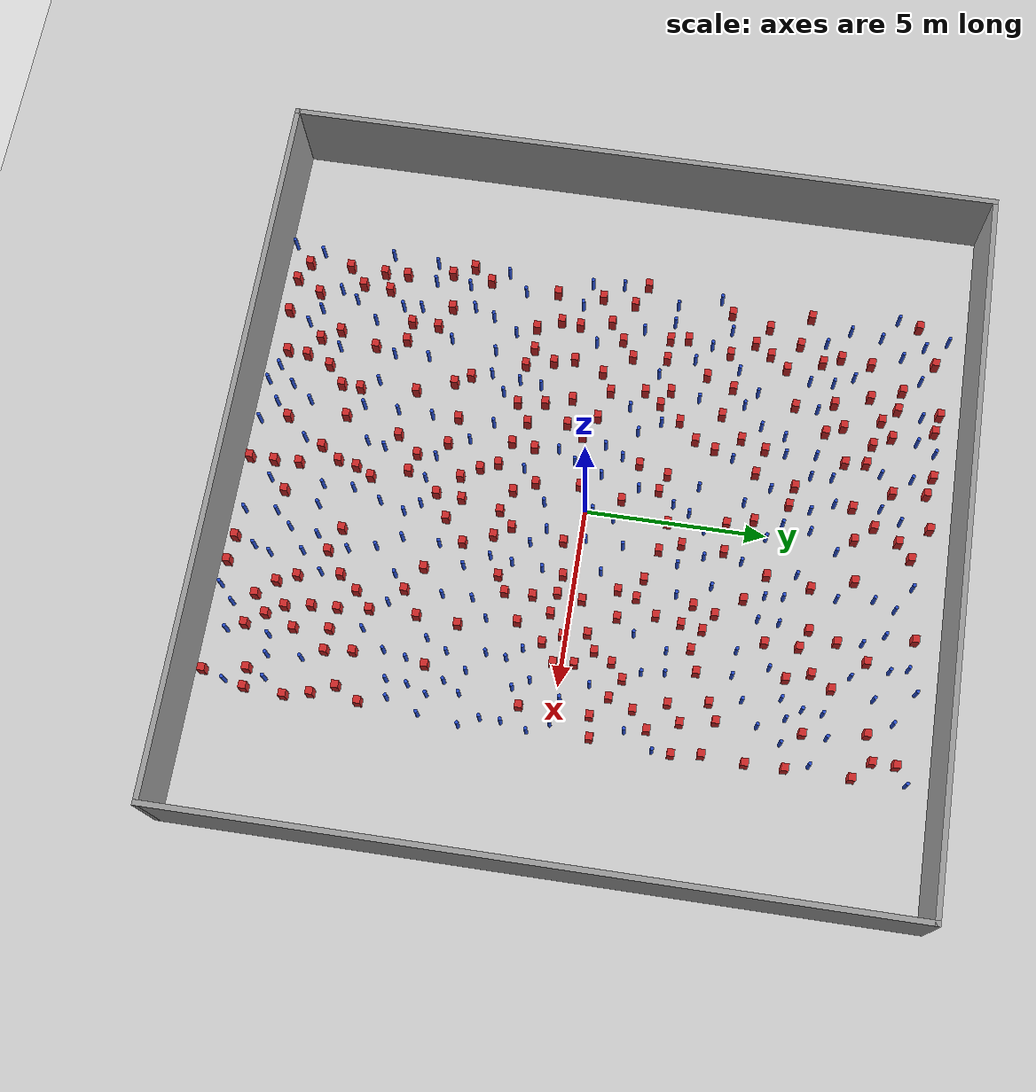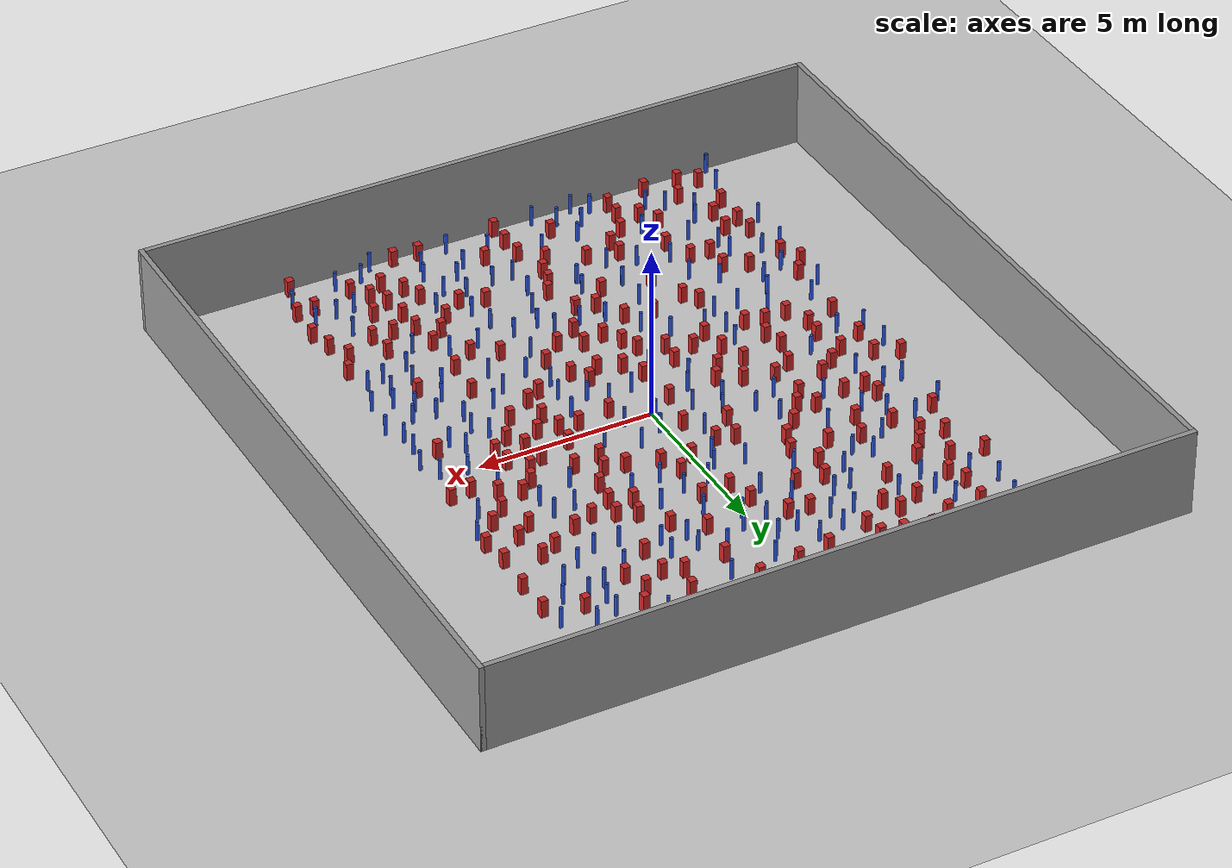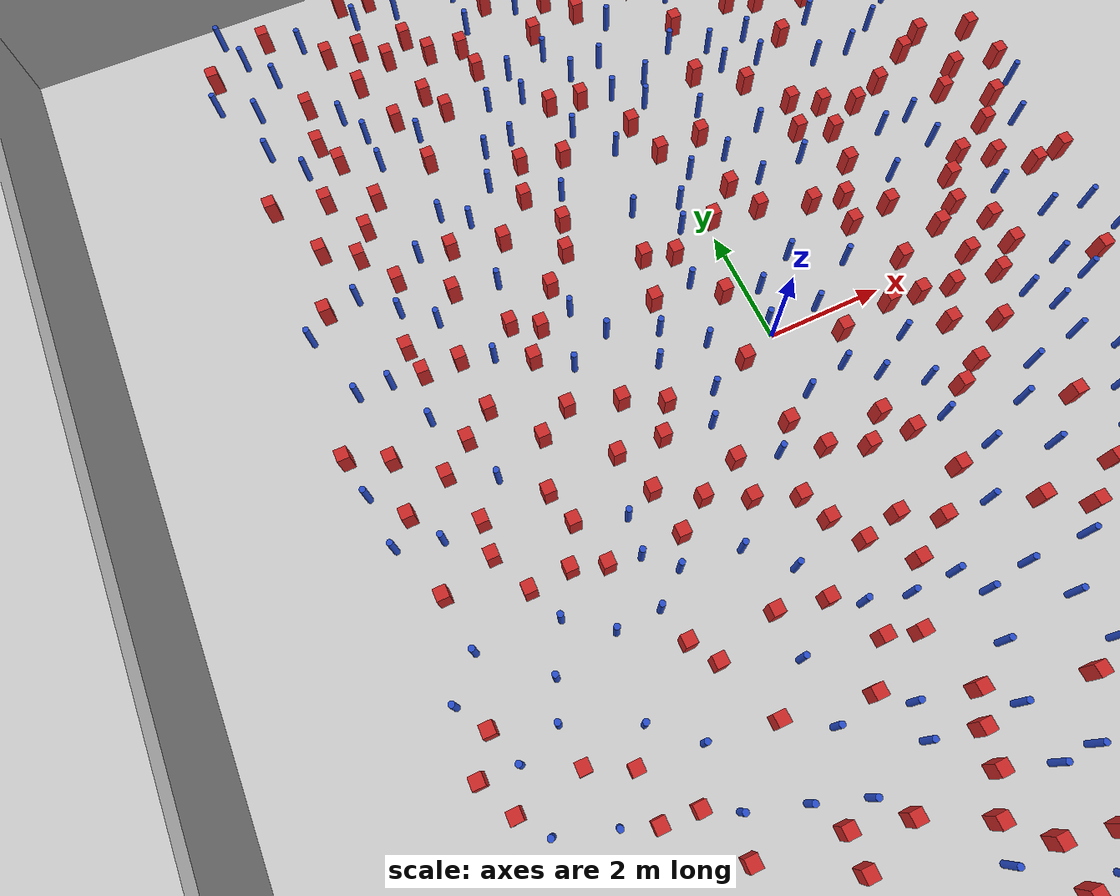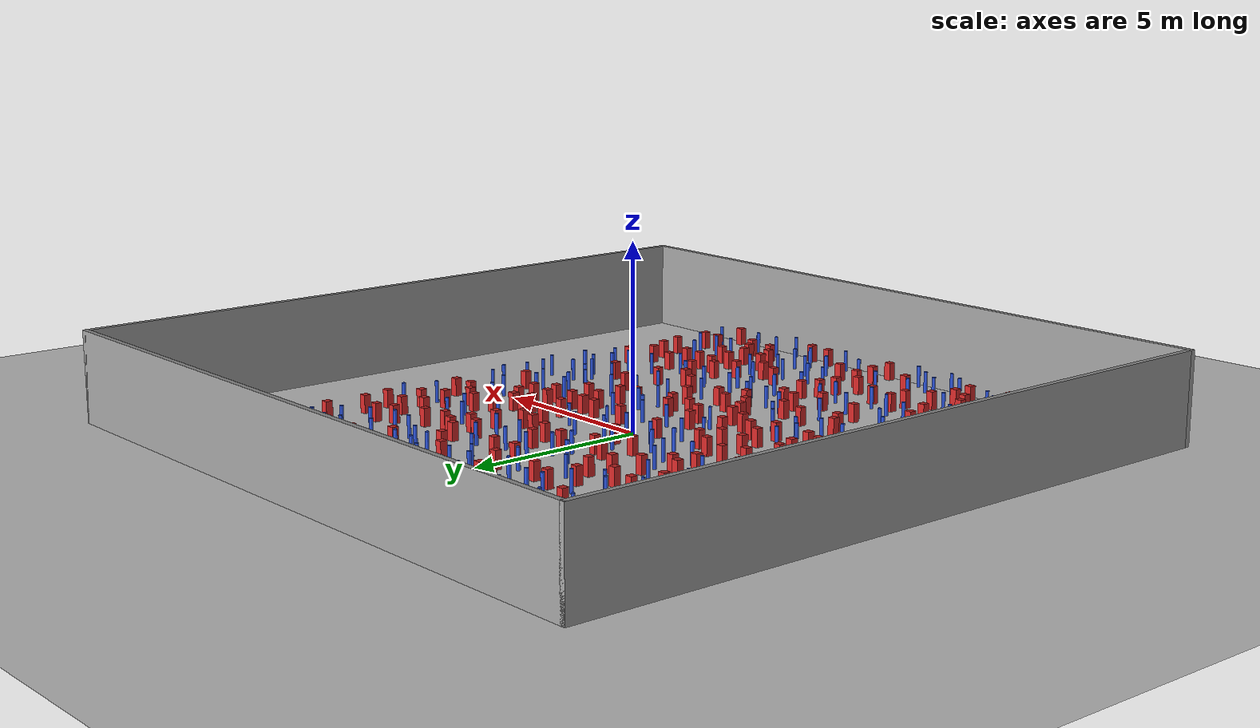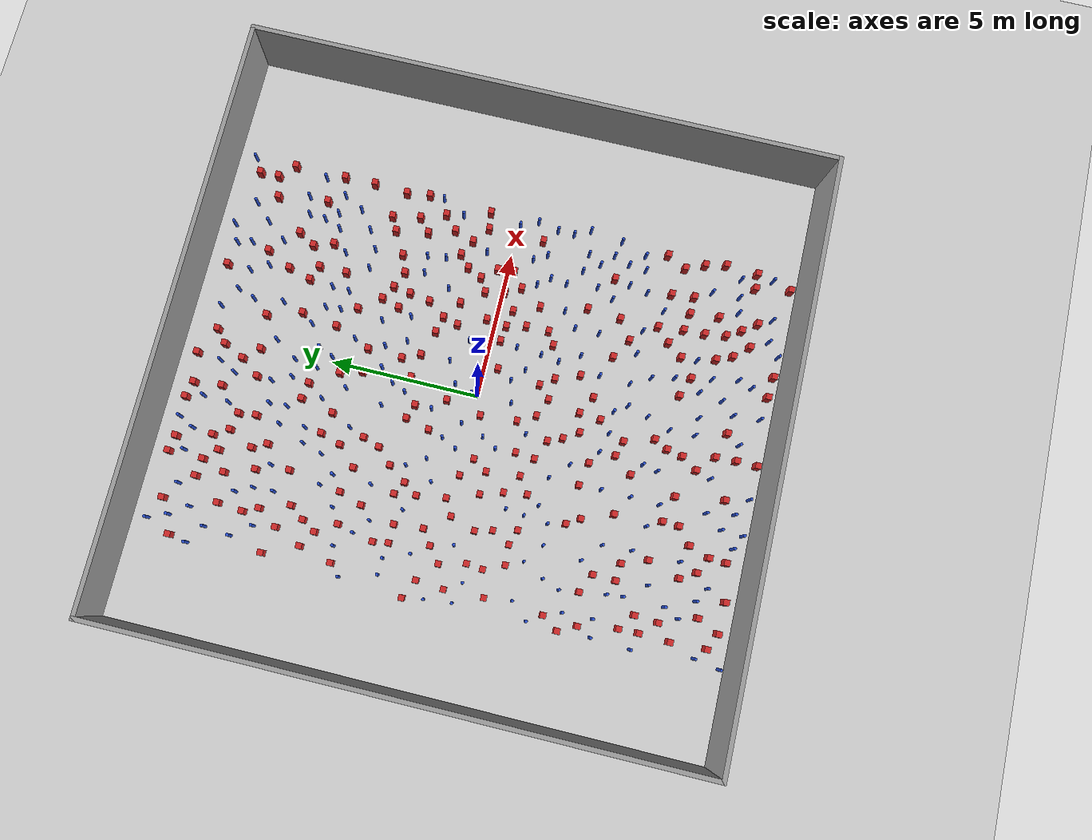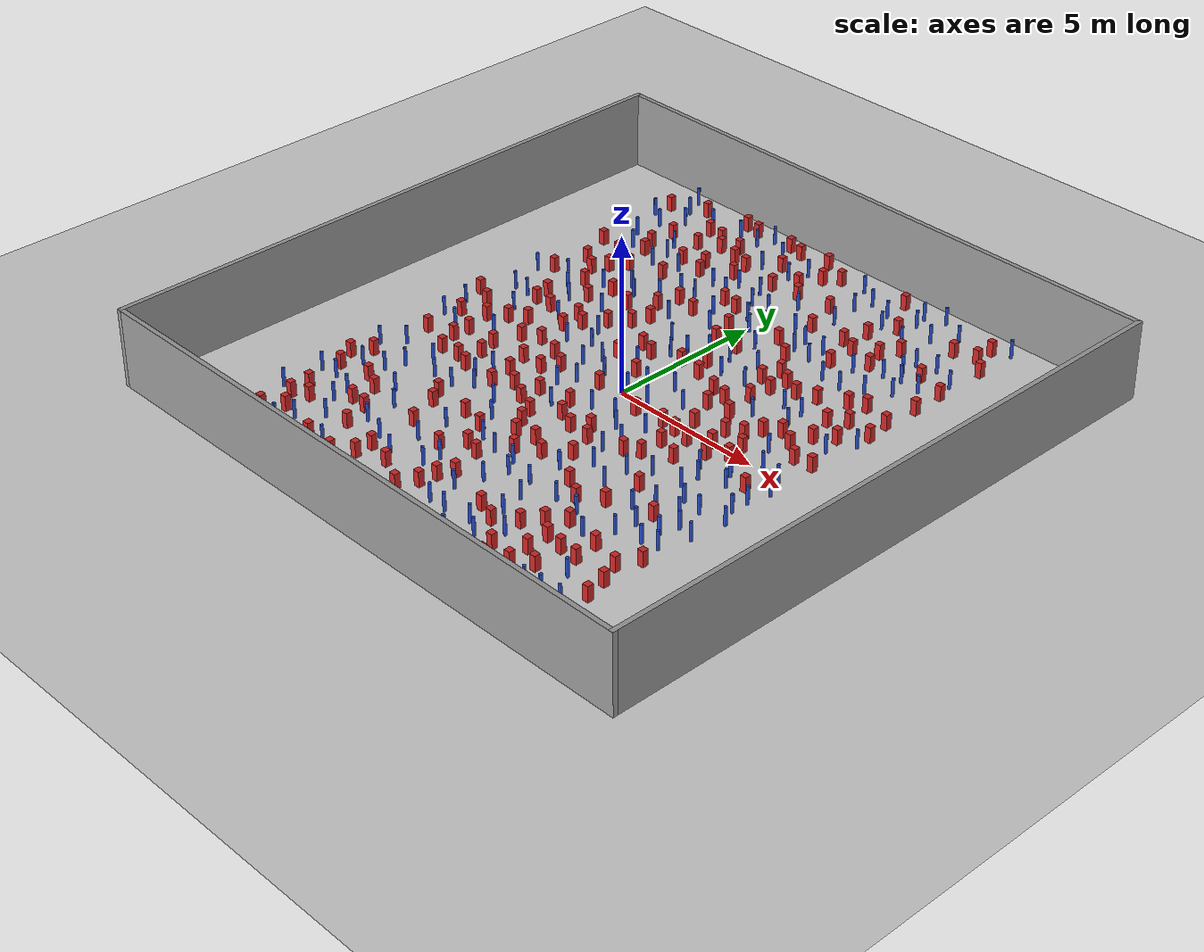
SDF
<sdf version="1.6">
 <world name="default">
  <light name="sun" type="directional">
   <pose>0 0 1000 0 -0 0</pose>
   <diffuse>0.8 0.8 0.8 1</diffuse>
   <specular>0.1 0.1 0.1 1</specular>
   <attenuation>
    <range>1000</range>
    <constant>0.9</constant>
    <linear>0.01</linear>
    <quadratic>0.001</quadratic>
   </attenuation>
   <direction>-0.5 0.5 -1</direction>
  </light>
  <model name="ground_plane">
   <static>1</static>
   <link name="link">
    <collision name="collision">
     <geometry><plane><normal>0 0 1</normal><size>100 100</size></plane></geometry>
     <surface><friction><ode><mu>100</mu><mu2>50</mu2></ode></friction></surface>
    </collision>
    <visual name="visual">
     <cast_shadows>0</cast_shadows>
     <geometry><plane><normal>0 0 1</normal><size>100 100</size></plane></geometry>
     <material>
      <ambient>1.0 1.0 1.0 1.0</ambient>
      <diffuse>0.8 0.8 0.8 1.0</diffuse>
      <specular>0.01 0.01 0.01 1.000000</specular>
     </material>
    </visual>
   </link>
  </model>
  <gravity>0 0 -9.8</gravity>
  <magnetic_field>6e-06 2.3e-05 -4.2e-05</magnetic_field>
  <atmosphere type="adiabatic"/>
  <physics name="default_physics" default="0" type="ode">
   <max_step_size>0.001</max_step_size>
   <real_time_factor>1</real_time_factor>
   <real_time_update_rate>1000</real_time_update_rate>
  </physics>
  <scene><ambient>0.4 0.4 0.4 1</ambient><background>0.7 0.7 0.7 1</background><shadows>1</shadows></scene>
  <spherical_coordinates>
   <surface_model>EARTH_WGS84</surface_model>
   <latitude_deg>0</latitude_deg>
   <longitude_deg>0</longitude_deg>
   <elevation>0</elevation>
   <heading_deg>0</heading_deg>
  </spherical_coordinates>
  <plugin name="gazebo_occupancy_map" filename="libgazebo_2Dmap_plugin.so">
   <map_resolution>0.05</map_resolution>
   <map_topic>generated_map</map_topic>
   <map_height>0.01</map_height>
   <map_size_x>50</map_size_x>
   <map_size_y>50</map_size_y>
  </plugin>
  <model name="NamedLocations">
   <static>true</static>
   <link name="DefaultStart"><pose>8.5 0 0 0 0 3.14</pose></link>
  </model>
  <model name="20x20_walls">
   <pose>0.044518 0.176112 0 0 -0 0</pose>
   <link name="Wall_1">
    <collision name="Wall_1_Collision">
     <geometry><box><size>20 0.15 2.5</size></box></geometry>
     <pose>0 0 1.25 0 -0 0</pose>
    </collision>
    <visual name="Wall_1_Visual">
     <pose>0 0 1.25 0 -0 0</pose>
     <geometry><box><size>20 0.15 2.5</size></box></geometry>
     <material>
      <script><uri>file://media/materials/scripts/gazebo.material</uri><name>Gazebo/Grey</name></script>
      <ambient>0.976471 0.992157 1 1</ambient>
     </material>
     <meta><layer>0</layer></meta>
    </visual>
    <pose>0 9.925 0 0 -0 0</pose>
   </link>
   <link name="Wall_3">
    <collision name="Wall_3_Collision">
     <geometry><box><size>20 0.15 2.5</size></box></geometry>
     <pose>0 0 1.25 0 -0 0</pose>
    </collision>
    <visual name="Wall_3_Visual">
     <pose>0 0 1.25 0 -0 0</pose>
     <geometry><box><size>20 0.15 2.5</size></box></geometry>
     <material>
      <script><uri>file://media/materials/scripts/gazebo.material</uri><name>Gazebo/Grey</name></script>
      <ambient>0.976471 0.992157 1 1</ambient>
     </material>
     <meta><layer>0</layer></meta>
    </visual>
    <pose>9.925 0 0 0 0 -1.5708</pose>
   </link>
   <link name="Wall_4">
    <collision name="Wall_4_Collision">
     <geometry><box><size>20 0.15 2.5</size></box></geometry>
     <pose>0 0 1.25 0 -0 0</pose>
    </collision>
    <visual name="Wall_4_Visual">
     <pose>0 0 1.25 0 -0 0</pose>
     <geometry><box><size>20 0.15 2.5</size></box></geometry>
     <material>
      <script><uri>file://media/materials/scripts/gazebo.material</uri><name>Gazebo/Grey</name></script>
      <ambient>0.976471 0.992157 1 1</ambient>
     </material>
     <meta><layer>0</layer></meta>
    </visual>
    <pose>0 -9.925 0 0 -0 3.14159</pose>
   </link>
   <link name="Wall_5">
    <collision name="Wall_5_Collision">
     <geometry><box><size>20 0.15 2.5</size></box></geometry>
     <pose>0 0 1.25 0 -0 0</pose>
    </collision>
    <visual name="Wall_5_Visual">
     <pose>0 0 1.25 0 -0 0</pose>
     <geometry><box><size>20 0.15 2.5</size></box></geometry>
     <material>
      <script><uri>file://media/materials/scripts/gazebo.material</uri><name>Gazebo/Grey</name></script>
      <ambient>0.976471 0.992157 1 1</ambient>
     </material>
     <meta><layer>0</layer></meta>
    </visual>
    <pose>-9.925 0 0 0 -0 1.5708</pose>
   </link>
   <static>1</static>
  </model>
  <model name="square_post_obstacle0">
   <static>true</static>
   <pose>3.03235378317 -7.45072302917 1.91545236811e-07 -7.35059704564e-06 1.12565212e-07 2.39332434364e-05</pose>
   <link name="link">
    <pose>0 0 0.25 0 -0 0</pose>
    <inertial>
     <mass>100</mass>
     <inertia>
      <ixx>0.166667</ixx>
      <ixy>0</ixy>
      <ixz>0</ixz>
      <iyy>0.166667</iyy>
      <iyz>0</iyz>
      <izz>0.166667</izz>
     </inertia>
    </inertial>
    <collision name="collision"><geometry><box><size>.2 .2 .5</size></box></geometry></collision>
    <visual name="visual">
     <geometry><box><size>.2 .2 .5</size></box></geometry>
     <material>
      <script><name>Gazebo/Red</name><uri>file://media/materials/scripts/gazebo.material</uri></script>
     </material>
    </visual>
   </link>
  </model>
  <model name="square_post_obstacle1">
   <static>true</static>
   <pose>-1.64343410092 -2.30711598032 1.91545236811e-07 -7.35059704564e-06 1.12565212e-07 2.39332434364e-05</pose>
   <link name="link">
    <pose>0 0 0.25 0 -0 0</pose>
    <inertial>
     <mass>100</mass>
     <inertia>
      <ixx>0.166667</ixx>
      <ixy>0</ixy>
      <ixz>0</ixz>
      <iyy>0.166667</iyy>
      <iyz>0</iyz>
      <izz>0.166667</izz>
     </inertia>
    </inertial>
    <collision name="collision"><geometry><box><size>.2 .2 .5</size></box></geometry></collision>
    <visual name="visual">
     <geometry><box><size>.2 .2 .5</size></box></geometry>
     <material>
      <script><name>Gazebo/Red</name><uri>file://media/materials/scripts/gazebo.material</uri></script>
     </material>
    </visual>
   </link>
  </model>
  <model name="pole_obstacle0">
   <static>true</static>
   <pose>5.95808666075 -7.75955042571 7.38925637345e-09 -8.47170692796e-08 1.24976764786e-08 -1.74513093032e-07</pose>
   <link name="link">
    <pose>0 0 0.3 0 -0 0</pose>
    <inertial>
     <mass>1</mass>
     <inertia><ixx>0.145833</ixx><ixy>0</ixy><ixz>0</ixz><iyy>0.145833</iyy><iyz>0</iyz><izz>0.125</izz></inertia>
    </inertial>
    <collision name="collision">
     <geometry><cylinder><radius>0.05</radius><length>.6</length></cylinder></geometry>
    </collision>
    <visual name="visual">
     <geometry><cylinder><radius>0.05</radius><length>.6</length></cylinder></geometry>
     <material>
      <script><name>Gazebo/Blue</name><uri>file://media/materials/scripts/gazebo.material</uri></script>
     </material>
    </visual>
   </link>
  </model>
  <model name="square_post_obstacle2">
   <static>true</static>
   <pose>-0.138965825792 3.89410492491 1.91545236811e-07 -7.35059704564e-06 1.12565212e-07 2.39332434364e-05</pose>
   <link name="link">
    <pose>0 0 0.25 0 -0 0</pose>
    <inertial>
     <mass>100</mass>
     <inertia>
      <ixx>0.166667</ixx>
      <ixy>0</ixy>
      <ixz>0</ixz>
      <iyy>0.166667</iyy>
      <iyz>0</iyz>
      <izz>0.166667</izz>
     </inertia>
    </inertial>
    <collision name="collision"><geometry><box><size>.2 .2 .5</size></box></geometry></collision>
    <visual name="visual">
     <geometry><box><size>.2 .2 .5</size></box></geometry>
     <material>
      <script><name>Gazebo/Red</name><uri>file://media/materials/scripts/gazebo.material</uri></script>
     </material>
    </visual>
   </link>
  </model>
  <model name="pole_obstacle1">
   <static>true</static>
   <pose>4.73851063794 6.49647820725 7.38925637345e-09 -8.47170692796e-08 1.24976764786e-08 -1.74513093032e-07</pose>
   <link name="link">
    <pose>0 0 0.3 0 -0 0</pose>
    <inertial>
     <mass>1</mass>
     <inertia><ixx>0.145833</ixx><ixy>0</ixy><ixz>0</ixz><iyy>0.145833</iyy><iyz>0</iyz><izz>0.125</izz></inertia>
    </inertial>
    <collision name="collision">
     <geometry><cylinder><radius>0.05</radius><length>.6</length></cylinder></geometry>
    </collision>
    <visual name="visual">
     <geometry><cylinder><radius>0.05</radius><length>.6</length></cylinder></geometry>
     <material>
      <script><name>Gazebo/Blue</name><uri>file://media/materials/scripts/gazebo.material</uri></script>
     </material>
    </visual>
   </link>
  </model>
  <model name="square_post_obstacle3">
   <static>true</static>
   <pose>5.14463022854 1.38851551591 1.91545236811e-07 -7.35059704564e-06 1.12565212e-07 2.39332434364e-05</pose>
   <link name="link">
    <pose>0 0 0.25 0 -0 0</pose>
    <inertial>
     <mass>100</mass>
     <inertia>
      <ixx>0.166667</ixx>
      <ixy>0</ixy>
      <ixz>0</ixz>
      <iyy>0.166667</iyy>
      <iyz>0</iyz>
      <izz>0.166667</izz>
     </inertia>
    </inertial>
    <collision name="collision"><geometry><box><size>.2 .2 .5</size></box></geometry></collision>
    <visual name="visual">
     <geometry><box><size>.2 .2 .5</size></box></geometry>
     <material>
      <script><name>Gazebo/Red</name><uri>file://media/materials/scripts/gazebo.material</uri></script>
     </material>
    </visual>
   </link>
  </model>
  <model name="pole_obstacle2">
   <static>true</static>
   <pose>4.98972135019 -2.48463313202 7.38925637345e-09 -8.47170692798e-08 1.24976764937e-08 -1.74513093023e-07</pose>
   <link name="link">
    <pose>0 0 0.3 0 -0 0</pose>
    <inertial>
     <mass>1</mass>
     <inertia><ixx>0.145833</ixx><ixy>0</ixy><ixz>0</ixz><iyy>0.145833</iyy><iyz>0</iyz><izz>0.125</izz></inertia>
    </inertial>
    <collision name="collision">
     <geometry><cylinder><radius>0.05</radius><length>.6</length></cylinder></geometry>
    </collision>
    <visual name="visual">
     <geometry><cylinder><radius>0.05</radius><length>.6</length></cylinder></geometry>
     <material>
      <script><name>Gazebo/Blue</name><uri>file://media/materials/scripts/gazebo.material</uri></script>
     </material>
    </visual>
   </link>
  </model>
  <model name="pole_obstacle3">
   <static>true</static>
   <pose>5.97604875241 1.91269889403 7.38925637345e-09 -8.471706928e-08 1.24976765134e-08 -1.74513093015e-07</pose>
   <link name="link">
    <pose>0 0 0.3 0 -0 0</pose>
    <inertial>
     <mass>1</mass>
     <inertia><ixx>0.145833</ixx><ixy>0</ixy><ixz>0</ixz><iyy>0.145833</iyy><iyz>0</iyz><izz>0.125</izz></inertia>
    </inertial>
    <collision name="collision">
     <geometry><cylinder><radius>0.05</radius><length>.6</length></cylinder></geometry>
    </collision>
    <visual name="visual">
     <geometry><cylinder><radius>0.05</radius><length>.6</length></cylinder></geometry>
     <material>
      <script><name>Gazebo/Blue</name><uri>file://media/materials/scripts/gazebo.material</uri></script>
     </material>
    </visual>
   </link>
  </model>
  <model name="square_post_obstacle4">
   <static>true</static>
   <pose>-6.3529247298 0.506604113943 1.91545236811e-07 -7.35059704564e-06 1.12565212e-07 2.39332434364e-05</pose>
   <link name="link">
    <pose>0 0 0.25 0 -0 0</pose>
    <inertial>
     <mass>100</mass>
     <inertia>
      <ixx>0.166667</ixx>
      <ixy>0</ixy>
      <ixz>0</ixz>
      <iyy>0.166667</iyy>
      <iyz>0</iyz>
      <izz>0.166667</izz>
     </inertia>
    </inertial>
    <collision name="collision"><geometry><box><size>.2 .2 .5</size></box></geometry></collision>
    <visual name="visual">
     <geometry><box><size>.2 .2 .5</size></box></geometry>
     <material>
      <script><name>Gazebo/Red</name><uri>file://media/materials/scripts/gazebo.material</uri></script>
     </material>
    </visual>
   </link>
  </model>
  <model name="square_post_obstacle5">
   <static>true</static>
   <pose>-2.94836752955 -1.5777060494 1.91545236811e-07 -7.35059704564e-06 1.12565212e-07 2.39332434364e-05</pose>
   <link name="link">
    <pose>0 0 0.25 0 -0 0</pose>
    <inertial>
     <mass>100</mass>
     <inertia>
      <ixx>0.166667</ixx>
      <ixy>0</ixy>
      <ixz>0</ixz>
      <iyy>0.166667</iyy>
      <iyz>0</iyz>
      <izz>0.166667</izz>
     </inertia>
    </inertial>
    <collision name="collision"><geometry><box><size>.2 .2 .5</size></box></geometry></collision>
    <visual name="visual">
     <geometry><box><size>.2 .2 .5</size></box></geometry>
     <material>
      <script><name>Gazebo/Red</name><uri>file://media/materials/scripts/gazebo.material</uri></script>
     </material>
    </visual>
   </link>
  </model>
  <model name="square_post_obstacle6">
   <static>true</static>
   <pose>-0.314412904541 -6.473569721 1.91545236811e-07 -7.35059704564e-06 1.12565212e-07 2.39332434364e-05</pose>
   <link name="link">
    <pose>0 0 0.25 0 -0 0</pose>
    <inertial>
     <mass>100</mass>
     <inertia>
      <ixx>0.166667</ixx>
      <ixy>0</ixy>
      <ixz>0</ixz>
      <iyy>0.166667</iyy>
      <iyz>0</iyz>
      <izz>0.166667</izz>
     </inertia>
    </inertial>
    <collision name="collision"><geometry><box><size>.2 .2 .5</size></box></geometry></collision>
    <visual name="visual">
     <geometry><box><size>.2 .2 .5</size></box></geometry>
     <material>
      <script><name>Gazebo/Red</name><uri>file://media/materials/scripts/gazebo.material</uri></script>
     </material>
    </visual>
   </link>
  </model>
  <model name="pole_obstacle4">
   <static>true</static>
   <pose>-5.57209997911 -4.01686630805 7.38925637345e-09 -8.47170692796e-08 1.24976764791e-08 -1.74513093031e-07</pose>
   <link name="link">
    <pose>0 0 0.3 0 -0 0</pose>
    <inertial>
     <mass>1</mass>
     <inertia><ixx>0.145833</ixx><ixy>0</ixy><ixz>0</ixz><iyy>0.145833</iyy><iyz>0</iyz><izz>0.125</izz></inertia>
    </inertial>
    <collision name="collision">
     <geometry><cylinder><radius>0.05</radius><length>.6</length></cylinder></geometry>
    </collision>
    <visual name="visual">
     <geometry><cylinder><radius>0.05</radius><length>.6</length></cylinder></geometry>
     <material>
      <script><name>Gazebo/Blue</name><uri>file://media/materials/scripts/gazebo.material</uri></script>
     </material>
    </visual>
   </link>
  </model>
  <model name="pole_obstacle5">
   <static>true</static>
   <pose>-6.83310321399 2.95984802754 7.38925637345e-09 -8.47170692798e-08 1.24976764937e-08 -1.74513093023e-07</pose>
   <link name="link">
    <pose>0 0 0.3 0 -0 0</pose>
    <inertial>
     <mass>1</mass>
     <inertia><ixx>0.145833</ixx><ixy>0</ixy><ixz>0</ixz><iyy>0.145833</iyy><iyz>0</iyz><izz>0.125</izz></inertia>
    </inertial>
    <collision name="collision">
     <geometry><cylinder><radius>0.05</radius><length>.6</length></cylinder></geometry>
    </collision>
    <visual name="visual">
     <geometry><cylinder><radius>0.05</radius><length>.6</length></cylinder></geometry>
     <material>
      <script><name>Gazebo/Blue</name><uri>file://media/materials/scripts/gazebo.material</uri></script>
     </material>
    </visual>
   </link>
  </model>
  <model name="square_post_obstacle7">
   <static>true</static>
   <pose>-2.95238209264 2.2382944484 1.91545236811e-07 -7.35059704564e-06 1.12565212e-07 2.39332434364e-05</pose>
   <link name="link">
    <pose>0 0 0.25 0 -0 0</pose>
    <inertial>
     <mass>100</mass>
     <inertia>
      <ixx>0.166667</ixx>
      <ixy>0</ixy>
      <ixz>0</ixz>
      <iyy>0.166667</iyy>
      <iyz>0</iyz>
      <izz>0.166667</izz>
     </inertia>
    </inertial>
    <collision name="collision"><geometry><box><size>.2 .2 .5</size></box></geometry></collision>
    <visual name="visual">
     <geometry><box><size>.2 .2 .5</size></box></geometry>
     <material>
      <script><name>Gazebo/Red</name><uri>file://media/materials/scripts/gazebo.material</uri></script>
     </material>
    </visual>
   </link>
  </model>
  <model name="square_post_obstacle8">
   <static>true</static>
   <pose>-5.78072870334 -6.53050007422 1.91545236811e-07 -7.35059704564e-06 1.12565212e-07 2.39332434364e-05</pose>
   <link name="link">
    <pose>0 0 0.25 0 -0 0</pose>
    <inertial>
     <mass>100</mass>
     <inertia>
      <ixx>0.166667</ixx>
      <ixy>0</ixy>
      <ixz>0</ixz>
      <iyy>0.166667</iyy>
      <iyz>0</iyz>
      <izz>0.166667</izz>
     </inertia>
    </inertial>
    <collision name="collision"><geometry><box><size>.2 .2 .5</size></box></geometry></collision>
    <visual name="visual">
     <geometry><box><size>.2 .2 .5</size></box></geometry>
     <material>
      <script><name>Gazebo/Red</name><uri>file://media/materials/scripts/gazebo.material</uri></script>
     </material>
    </visual>
   </link>
  </model>
  <model name="pole_obstacle6">
   <static>true</static>
   <pose>4.02126811115 -9.05385986758 7.38925637345e-09 -8.47170692799e-08 1.24976765044e-08 -1.74513093018e-07</pose>
   <link name="link">
    <pose>0 0 0.3 0 -0 0</pose>
    <inertial>
     <mass>1</mass>
     <inertia><ixx>0.145833</ixx><ixy>0</ixy><ixz>0</ixz><iyy>0.145833</iyy><iyz>0</iyz><izz>0.125</izz></inertia>
    </inertial>
    <collision name="collision">
     <geometry><cylinder><radius>0.05</radius><length>.6</length></cylinder></geometry>
    </collision>
    <visual name="visual">
     <geometry><cylinder><radius>0.05</radius><length>.6</length></cylinder></geometry>
     <material>
      <script><name>Gazebo/Blue</name><uri>file://media/materials/scripts/gazebo.material</uri></script>
     </material>
    </visual>
   </link>
  </model>
  <model name="pole_obstacle7">
   <static>true</static>
   <pose>2.70297682005 7.90768251212 7.38925637345e-09 -8.47170692798e-08 1.24976765033e-08 -1.74513093019e-07</pose>
   <link name="link">
    <pose>0 0 0.3 0 -0 0</pose>
    <inertial>
     <mass>1</mass>
     <inertia><ixx>0.145833</ixx><ixy>0</ixy><ixz>0</ixz><iyy>0.145833</iyy><iyz>0</iyz><izz>0.125</izz></inertia>
    </inertial>
    <collision name="collision">
     <geometry><cylinder><radius>0.05</radius><length>.6</length></cylinder></geometry>
    </collision>
    <visual name="visual">
     <geometry><cylinder><radius>0.05</radius><length>.6</length></cylinder></geometry>
     <material>
      <script><name>Gazebo/Blue</name><uri>file://media/materials/scripts/gazebo.material</uri></script>
     </material>
    </visual>
   </link>
  </model>
  <model name="square_post_obstacle9">
   <static>true</static>
   <pose>3.07814021229 -0.493479923198 1.91545236811e-07 -7.35059704564e-06 1.12565212e-07 2.39332434364e-05</pose>
   <link name="link">
    <pose>0 0 0.25 0 -0 0</pose>
    <inertial>
     <mass>100</mass>
     <inertia>
      <ixx>0.166667</ixx>
      <ixy>0</ixy>
      <ixz>0</ixz>
      <iyy>0.166667</iyy>
      <iyz>0</iyz>
      <izz>0.166667</izz>
     </inertia>
    </inertial>
    <collision name="collision"><geometry><box><size>.2 .2 .5</size></box></geometry></collision>
    <visual name="visual">
     <geometry><box><size>.2 .2 .5</size></box></geometry>
     <material>
      <script><name>Gazebo/Red</name><uri>file://media/materials/scripts/gazebo.material</uri></script>
     </material>
    </visual>
   </link>
  </model>
  <model name="square_post_obstacle10">
   <static>true</static>
   <pose>3.95411249766 0.828914553557 1.91545236811e-07 -7.35059704564e-06 1.12565212e-07 2.39332434364e-05</pose>
   <link name="link">
    <pose>0 0 0.25 0 -0 0</pose>
    <inertial>
     <mass>100</mass>
     <inertia>
      <ixx>0.166667</ixx>
      <ixy>0</ixy>
      <ixz>0</ixz>
      <iyy>0.166667</iyy>
      <iyz>0</iyz>
      <izz>0.166667</izz>
     </inertia>
    </inertial>
    <collision name="collision"><geometry><box><size>.2 .2 .5</size></box></geometry></collision>
    <visual name="visual">
     <geometry><box><size>.2 .2 .5</size></box></geometry>
     <material>
      <script><name>Gazebo/Red</name><uri>file://media/materials/scripts/gazebo.material</uri></script>
     </material>
    </visual>
   </link>
  </model>
  <model name="square_post_obstacle11">
   <static>true</static>
   <pose>-1.40964956682 -5.48230653608 1.91545236811e-07 -7.35059704564e-06 1.12565212e-07 2.39332434364e-05</pose>
   <link name="link">
    <pose>0 0 0.25 0 -0 0</pose>
    <inertial>
     <mass>100</mass>
     <inertia>
      <ixx>0.166667</ixx>
      <ixy>0</ixy>
      <ixz>0</ixz>
      <iyy>0.166667</iyy>
      <iyz>0</iyz>
      <izz>0.166667</izz>
     </inertia>
    </inertial>
    <collision name="collision"><geometry><box><size>.2 .2 .5</size></box></geometry></collision>
    <visual name="visual">
     <geometry><box><size>.2 .2 .5</size></box></geometry>
     <material>
      <script><name>Gazebo/Red</name><uri>file://media/materials/scripts/gazebo.material</uri></script>
     </material>
    </visual>
   </link>
  </model>
  <model name="square_post_obstacle12">
   <static>true</static>
   <pose>-6.83879509519 -4.23046960165 1.91545236811e-07 -7.35059704564e-06 1.12565212e-07 2.39332434364e-05</pose>
   <link name="link">
    <pose>0 0 0.25 0 -0 0</pose>
    <inertial>
     <mass>100</mass>
     <inertia>
      <ixx>0.166667</ixx>
      <ixy>0</ixy>
      <ixz>0</ixz>
      <iyy>0.166667</iyy>
      <iyz>0</iyz>
      <izz>0.166667</izz>
     </inertia>
    </inertial>
    <collision name="collision"><geometry><box><size>.2 .2 .5</size></box></geometry></collision>
    <visual name="visual">
     <geometry><box><size>.2 .2 .5</size></box></geometry>
     <material>
      <script><name>Gazebo/Red</name><uri>file://media/materials/scripts/gazebo.material</uri></script>
     </material>
    </visual>
   </link>
  </model>
  <model name="square_post_obstacle13">
   <static>true</static>
   <pose>3.70461877562 -8.47410973414 1.91545236811e-07 -7.35059704564e-06 1.12565212e-07 2.39332434364e-05</pose>
   <link name="link">
    <pose>0 0 0.25 0 -0 0</pose>
    <inertial>
     <mass>100</mass>
     <inertia>
      <ixx>0.166667</ixx>
      <ixy>0</ixy>
      <ixz>0</ixz>
      <iyy>0.166667</iyy>
      <iyz>0</iyz>
      <izz>0.166667</izz>
     </inertia>
    </inertial>
    <collision name="collision"><geometry><box><size>.2 .2 .5</size></box></geometry></collision>
    <visual name="visual">
     <geometry><box><size>.2 .2 .5</size></box></geometry>
     <material>
      <script><name>Gazebo/Red</name><uri>file://media/materials/scripts/gazebo.material</uri></script>
     </material>
    </visual>
   </link>
  </model>
  <model name="pole_obstacle8">
   <static>true</static>
   <pose>4.87359856132 -4.12664584839 7.38925637345e-09 -8.47170692796e-08 1.24976764786e-08 -1.74513093032e-07</pose>
   <link name="link">
    <pose>0 0 0.3 0 -0 0</pose>
    <inertial>
     <mass>1</mass>
     <inertia><ixx>0.145833</ixx><ixy>0</ixy><ixz>0</ixz><iyy>0.145833</iyy><iyz>0</iyz><izz>0.125</izz></inertia>
    </inertial>
    <collision name="collision">
     <geometry><cylinder><radius>0.05</radius><length>.6</length></cylinder></geometry>
    </collision>
    <visual name="visual">
     <geometry><cylinder><radius>0.05</radius><length>.6</length></cylinder></geometry>
     <material>
      <script><name>Gazebo/Blue</name><uri>file://media/materials/scripts/gazebo.material</uri></script>
     </material>
    </visual>
   </link>
  </model>
  <model name="square_post_obstacle14">
   <static>true</static>
   <pose>-0.408119338565 0.94953494307 1.91545236811e-07 -7.35059704564e-06 1.12565212e-07 2.39332434364e-05</pose>
   <link name="link">
    <pose>0 0 0.25 0 -0 0</pose>
    <inertial>
     <mass>100</mass>
     <inertia>
      <ixx>0.166667</ixx>
      <ixy>0</ixy>
      <ixz>0</ixz>
      <iyy>0.166667</iyy>
      <iyz>0</iyz>
      <izz>0.166667</izz>
     </inertia>
    </inertial>
    <collision name="collision"><geometry><box><size>.2 .2 .5</size></box></geometry></collision>
    <visual name="visual">
     <geometry><box><size>.2 .2 .5</size></box></geometry>
     <material>
      <script><name>Gazebo/Red</name><uri>file://media/materials/scripts/gazebo.material</uri></script>
     </material>
    </visual>
   </link>
  </model>
  <model name="square_post_obstacle15">
   <static>true</static>
   <pose>1.44649515637 -3.17782673812 1.91545236811e-07 -7.35059704564e-06 1.12565212e-07 2.39332434364e-05</pose>
   <link name="link">
    <pose>0 0 0.25 0 -0 0</pose>
    <inertial>
     <mass>100</mass>
     <inertia>
      <ixx>0.166667</ixx>
      <ixy>0</ixy>
      <ixz>0</ixz>
      <iyy>0.166667</iyy>
      <iyz>0</iyz>
      <izz>0.166667</izz>
     </inertia>
    </inertial>
    <collision name="collision"><geometry><box><size>.2 .2 .5</size></box></geometry></collision>
    <visual name="visual">
     <geometry><box><size>.2 .2 .5</size></box></geometry>
     <material>
      <script><name>Gazebo/Red</name><uri>file://media/materials/scripts/gazebo.material</uri></script>
     </material>
    </visual>
   </link>
  </model>
  <model name="square_post_obstacle16">
   <static>true</static>
   <pose>-6.29691629404 -6.77360591262 1.91545236811e-07 -7.35059704564e-06 1.12565212e-07 2.39332434364e-05</pose>
   <link name="link">
    <pose>0 0 0.25 0 -0 0</pose>
    <inertial>
     <mass>100</mass>
     <inertia>
      <ixx>0.166667</ixx>
      <ixy>0</ixy>
      <ixz>0</ixz>
      <iyy>0.166667</iyy>
      <iyz>0</iyz>
      <izz>0.166667</izz>
     </inertia>
    </inertial>
    <collision name="collision"><geometry><box><size>.2 .2 .5</size></box></geometry></collision>
    <visual name="visual">
     <geometry><box><size>.2 .2 .5</size></box></geometry>
     <material>
      <script><name>Gazebo/Red</name><uri>file://media/materials/scripts/gazebo.material</uri></script>
     </material>
    </visual>
   </link>
  </model>
  <model name="pole_obstacle9">
   <static>true</static>
   <pose>-6.08255972995 -0.967734815302 7.38925637345e-09 -8.47170692799e-08 1.24976765054e-08 -1.74513093018e-07</pose>
   <link name="link">
    <pose>0 0 0.3 0 -0 0</pose>
    <inertial>
     <mass>1</mass>
     <inertia><ixx>0.145833</ixx><ixy>0</ixy><ixz>0</ixz><iyy>0.145833</iyy><iyz>0</iyz><izz>0.125</izz></inertia>
    </inertial>
    <collision name="collision">
     <geometry><cylinder><radius>0.05</radius><length>.6</length></cylinder></geometry>
    </collision>
    <visual name="visual">
     <geometry><cylinder><radius>0.05</radius><length>.6</length></cylinder></geometry>
     <material>
      <script><name>Gazebo/Blue</name><uri>file://media/materials/scripts/gazebo.material</uri></script>
     </material>
    </visual>
   </link>
  </model>
  <model name="square_post_obstacle17">
   <static>true</static>
   <pose>-6.17913111131 4.42265076465 1.91545236811e-07 -7.35059704564e-06 1.12565212e-07 2.39332434364e-05</pose>
   <link name="link">
    <pose>0 0 0.25 0 -0 0</pose>
    <inertial>
     <mass>100</mass>
     <inertia>
      <ixx>0.166667</ixx>
      <ixy>0</ixy>
      <ixz>0</ixz>
      <iyy>0.166667</iyy>
      <iyz>0</iyz>
      <izz>0.166667</izz>
     </inertia>
    </inertial>
    <collision name="collision"><geometry><box><size>.2 .2 .5</size></box></geometry></collision>
    <visual name="visual">
     <geometry><box><size>.2 .2 .5</size></box></geometry>
     <material>
      <script><name>Gazebo/Red</name><uri>file://media/materials/scripts/gazebo.material</uri></script>
     </material>
    </visual>
   </link>
  </model>
  <model name="square_post_obstacle18">
   <static>true</static>
   <pose>-5.33817524046 4.54224600071 1.91545236811e-07 -7.35059704564e-06 1.12565212e-07 2.39332434364e-05</pose>
   <link name="link">
    <pose>0 0 0.25 0 -0 0</pose>
    <inertial>
     <mass>100</mass>
     <inertia>
      <ixx>0.166667</ixx>
      <ixy>0</ixy>
      <ixz>0</ixz>
      <iyy>0.166667</iyy>
      <iyz>0</iyz>
      <izz>0.166667</izz>
     </inertia>
    </inertial>
    <collision name="collision"><geometry><box><size>.2 .2 .5</size></box></geometry></collision>
    <visual name="visual">
     <geometry><box><size>.2 .2 .5</size></box></geometry>
     <material>
      <script><name>Gazebo/Red</name><uri>file://media/materials/scripts/gazebo.material</uri></script>
     </material>
    </visual>
   </link>
  </model>
  <model name="pole_obstacle10">
   <static>true</static>
   <pose>3.57856025257 -9.45177462803 7.38925637345e-09 -8.47170692793e-08 1.24976764408e-08 -1.74513093041e-07</pose>
   <link name="link">
    <pose>0 0 0.3 0 -0 0</pose>
    <inertial>
     <mass>1</mass>
     <inertia><ixx>0.145833</ixx><ixy>0</ixy><ixz>0</ixz><iyy>0.145833</iyy><iyz>0</iyz><izz>0.125</izz></inertia>
    </inertial>
    <collision name="collision">
     <geometry><cylinder><radius>0.05</radius><length>.6</length></cylinder></geometry>
    </collision>
    <visual name="visual">
     <geometry><cylinder><radius>0.05</radius><length>.6</length></cylinder></geometry>
     <material>
      <script><name>Gazebo/Blue</name><uri>file://media/materials/scripts/gazebo.material</uri></script>
     </material>
    </visual>
   </link>
  </model>
  <model name="square_post_obstacle19">
   <static>true</static>
   <pose>5.851577557 8.4508290675 1.91545236811e-07 -7.35059704564e-06 1.12565212e-07 2.39332434364e-05</pose>
   <link name="link">
    <pose>0 0 0.25 0 -0 0</pose>
    <inertial>
     <mass>100</mass>
     <inertia>
      <ixx>0.166667</ixx>
      <ixy>0</ixy>
      <ixz>0</ixz>
      <iyy>0.166667</iyy>
      <iyz>0</iyz>
      <izz>0.166667</izz>
     </inertia>
    </inertial>
    <collision name="collision"><geometry><box><size>.2 .2 .5</size></box></geometry></collision>
    <visual name="visual">
     <geometry><box><size>.2 .2 .5</size></box></geometry>
     <material>
      <script><name>Gazebo/Red</name><uri>file://media/materials/scripts/gazebo.material</uri></script>
     </material>
    </visual>
   </link>
  </model>
  <model name="pole_obstacle11">
   <static>true</static>
   <pose>5.32283034793 -7.82426257273 7.38925637345e-09 -8.47170692796e-08 1.24976764786e-08 -1.74513093032e-07</pose>
   <link name="link">
    <pose>0 0 0.3 0 -0 0</pose>
    <inertial>
     <mass>1</mass>
     <inertia><ixx>0.145833</ixx><ixy>0</ixy><ixz>0</ixz><iyy>0.145833</iyy><iyz>0</iyz><izz>0.125</izz></inertia>
    </inertial>
    <collision name="collision">
     <geometry><cylinder><radius>0.05</radius><length>.6</length></cylinder></geometry>
    </collision>
    <visual name="visual">
     <geometry><cylinder><radius>0.05</radius><length>.6</length></cylinder></geometry>
     <material>
      <script><name>Gazebo/Blue</name><uri>file://media/materials/scripts/gazebo.material</uri></script>
     </material>
    </visual>
   </link>
  </model>
  <model name="square_post_obstacle20">
   <static>true</static>
   <pose>-0.168599659876 -9.45162408497 1.91545236811e-07 -7.35059704564e-06 1.12565212e-07 2.39332434364e-05</pose>
   <link name="link">
    <pose>0 0 0.25 0 -0 0</pose>
    <inertial>
     <mass>100</mass>
     <inertia>
      <ixx>0.166667</ixx>
      <ixy>0</ixy>
      <ixz>0</ixz>
      <iyy>0.166667</iyy>
      <iyz>0</iyz>
      <izz>0.166667</izz>
     </inertia>
    </inertial>
    <collision name="collision"><geometry><box><size>.2 .2 .5</size></box></geometry></collision>
    <visual name="visual">
     <geometry><box><size>.2 .2 .5</size></box></geometry>
     <material>
      <script><name>Gazebo/Red</name><uri>file://media/materials/scripts/gazebo.material</uri></script>
     </material>
    </visual>
   </link>
  </model>
  <model name="pole_obstacle12">
   <static>true</static>
   <pose>5.34514261602 -3.01853340527 7.38925637345e-09 -8.47170692798e-08 1.24976764937e-08 -1.74513093023e-07</pose>
   <link name="link">
    <pose>0 0 0.3 0 -0 0</pose>
    <inertial>
     <mass>1</mass>
     <inertia><ixx>0.145833</ixx><ixy>0</ixy><ixz>0</ixz><iyy>0.145833</iyy><iyz>0</iyz><izz>0.125</izz></inertia>
    </inertial>
    <collision name="collision">
     <geometry><cylinder><radius>0.05</radius><length>.6</length></cylinder></geometry>
    </collision>
    <visual name="visual">
     <geometry><cylinder><radius>0.05</radius><length>.6</length></cylinder></geometry>
     <material>
      <script><name>Gazebo/Blue</name><uri>file://media/materials/scripts/gazebo.material</uri></script>
     </material>
    </visual>
   </link>
  </model>
  <model name="square_post_obstacle21">
   <static>true</static>
   <pose>-2.26156633794 3.30538135168 1.91545236811e-07 -7.35059704564e-06 1.12565212e-07 2.39332434364e-05</pose>
   <link name="link">
    <pose>0 0 0.25 0 -0 0</pose>
    <inertial>
     <mass>100</mass>
     <inertia>
      <ixx>0.166667</ixx>
      <ixy>0</ixy>
      <ixz>0</ixz>
      <iyy>0.166667</iyy>
      <iyz>0</iyz>
      <izz>0.166667</izz>
     </inertia>
    </inertial>
    <collision name="collision"><geometry><box><size>.2 .2 .5</size></box></geometry></collision>
    <visual name="visual">
     <geometry><box><size>.2 .2 .5</size></box></geometry>
     <material>
      <script><name>Gazebo/Red</name><uri>file://media/materials/scripts/gazebo.material</uri></script>
     </material>
    </visual>
   </link>
  </model>
  <model name="pole_obstacle13">
   <static>true</static>
   <pose>-6.44039647918 9.48726860901 7.38925637345e-09 -8.471706928e-08 1.24976765081e-08 -1.74513093015e-07</pose>
   <link name="link">
    <pose>0 0 0.3 0 -0 0</pose>
    <inertial>
     <mass>1</mass>
     <inertia><ixx>0.145833</ixx><ixy>0</ixy><ixz>0</ixz><iyy>0.145833</iyy><iyz>0</iyz><izz>0.125</izz></inertia>
    </inertial>
    <collision name="collision">
     <geometry><cylinder><radius>0.05</radius><length>.6</length></cylinder></geometry>
    </collision>
    <visual name="visual">
     <geometry><cylinder><radius>0.05</radius><length>.6</length></cylinder></geometry>
     <material>
      <script><name>Gazebo/Blue</name><uri>file://media/materials/scripts/gazebo.material</uri></script>
     </material>
    </visual>
   </link>
  </model>
  <model name="square_post_obstacle22">
   <static>true</static>
   <pose>-4.10464429854 -0.103522538844 1.91545236811e-07 -7.35059704564e-06 1.12565212e-07 2.39332434364e-05</pose>
   <link name="link">
    <pose>0 0 0.25 0 -0 0</pose>
    <inertial>
     <mass>100</mass>
     <inertia>
      <ixx>0.166667</ixx>
      <ixy>0</ixy>
      <ixz>0</ixz>
      <iyy>0.166667</iyy>
      <iyz>0</iyz>
      <izz>0.166667</izz>
     </inertia>
    </inertial>
    <collision name="collision"><geometry><box><size>.2 .2 .5</size></box></geometry></collision>
    <visual name="visual">
     <geometry><box><size>.2 .2 .5</size></box></geometry>
     <material>
      <script><name>Gazebo/Red</name><uri>file://media/materials/scripts/gazebo.material</uri></script>
     </material>
    </visual>
   </link>
  </model>
  <model name="pole_obstacle14">
   <static>true</static>
   <pose>2.60923949467 -4.84293142465 7.38925637345e-09 -8.47170692798e-08 1.24976765033e-08 -1.74513093019e-07</pose>
   <link name="link">
    <pose>0 0 0.3 0 -0 0</pose>
    <inertial>
     <mass>1</mass>
     <inertia><ixx>0.145833</ixx><ixy>0</ixy><ixz>0</ixz><iyy>0.145833</iyy><iyz>0</iyz><izz>0.125</izz></inertia>
    </inertial>
    <collision name="collision">
     <geometry><cylinder><radius>0.05</radius><length>.6</length></cylinder></geometry>
    </collision>
    <visual name="visual">
     <geometry><cylinder><radius>0.05</radius><length>.6</length></cylinder></geometry>
     <material>
      <script><name>Gazebo/Blue</name><uri>file://media/materials/scripts/gazebo.material</uri></script>
     </material>
    </visual>
   </link>
  </model>
  <model name="pole_obstacle15">
   <static>true</static>
   <pose>6.19638052908 -1.3493396878 7.38925637345e-09 -8.471706928e-08 1.24976765134e-08 -1.74513093015e-07</pose>
   <link name="link">
    <pose>0 0 0.3 0 -0 0</pose>
    <inertial>
     <mass>1</mass>
     <inertia><ixx>0.145833</ixx><ixy>0</ixy><ixz>0</ixz><iyy>0.145833</iyy><iyz>0</iyz><izz>0.125</izz></inertia>
    </inertial>
    <collision name="collision">
     <geometry><cylinder><radius>0.05</radius><length>.6</length></cylinder></geometry>
    </collision>
    <visual name="visual">
     <geometry><cylinder><radius>0.05</radius><length>.6</length></cylinder></geometry>
     <material>
      <script><name>Gazebo/Blue</name><uri>file://media/materials/scripts/gazebo.material</uri></script>
     </material>
    </visual>
   </link>
  </model>
  <model name="pole_obstacle16">
   <static>true</static>
   <pose>-0.988957043239 -5.80576864988 7.38925637345e-09 -8.47170692799e-08 1.2497676509e-08 -1.74513093015e-07</pose>
   <link name="link">
    <pose>0 0 0.3 0 -0 0</pose>
    <inertial>
     <mass>1</mass>
     <inertia><ixx>0.145833</ixx><ixy>0</ixy><ixz>0</ixz><iyy>0.145833</iyy><iyz>0</iyz><izz>0.125</izz></inertia>
    </inertial>
    <collision name="collision">
     <geometry><cylinder><radius>0.05</radius><length>.6</length></cylinder></geometry>
    </collision>
    <visual name="visual">
     <geometry><cylinder><radius>0.05</radius><length>.6</length></cylinder></geometry>
     <material>
      <script><name>Gazebo/Blue</name><uri>file://media/materials/scripts/gazebo.material</uri></script>
     </material>
    </visual>
   </link>
  </model>
  <model name="square_post_obstacle23">
   <static>true</static>
   <pose>-3.88642827105 5.38813392325 1.91545236811e-07 -7.35059704564e-06 1.12565212e-07 2.39332434364e-05</pose>
   <link name="link">
    <pose>0 0 0.25 0 -0 0</pose>
    <inertial>
     <mass>100</mass>
     <inertia>
      <ixx>0.166667</ixx>
      <ixy>0</ixy>
      <ixz>0</ixz>
      <iyy>0.166667</iyy>
      <iyz>0</iyz>
      <izz>0.166667</izz>
     </inertia>
    </inertial>
    <collision name="collision"><geometry><box><size>.2 .2 .5</size></box></geometry></collision>
    <visual name="visual">
     <geometry><box><size>.2 .2 .5</size></box></geometry>
     <material>
      <script><name>Gazebo/Red</name><uri>file://media/materials/scripts/gazebo.material</uri></script>
     </material>
    </visual>
   </link>
  </model>
  <model name="pole_obstacle17">
   <static>true</static>
   <pose>-3.26010692896 8.86807212109 7.38925637345e-09 -8.47170692793e-08 1.24976764408e-08 -1.74513093041e-07</pose>
   <link name="link">
    <pose>0 0 0.3 0 -0 0</pose>
    <inertial>
     <mass>1</mass>
     <inertia><ixx>0.145833</ixx><ixy>0</ixy><ixz>0</ixz><iyy>0.145833</iyy><iyz>0</iyz><izz>0.125</izz></inertia>
    </inertial>
    <collision name="collision">
     <geometry><cylinder><radius>0.05</radius><length>.6</length></cylinder></geometry>
    </collision>
    <visual name="visual">
     <geometry><cylinder><radius>0.05</radius><length>.6</length></cylinder></geometry>
     <material>
      <script><name>Gazebo/Blue</name><uri>file://media/materials/scripts/gazebo.material</uri></script>
     </material>
    </visual>
   </link>
  </model>
  <model name="square_post_obstacle24">
   <static>true</static>
   <pose>4.1140175235 3.5957617354 1.91545236811e-07 -7.35059704564e-06 1.12565212e-07 2.39332434364e-05</pose>
   <link name="link">
    <pose>0 0 0.25 0 -0 0</pose>
    <inertial>
     <mass>100</mass>
     <inertia>
      <ixx>0.166667</ixx>
      <ixy>0</ixy>
      <ixz>0</ixz>
      <iyy>0.166667</iyy>
      <iyz>0</iyz>
      <izz>0.166667</izz>
     </inertia>
    </inertial>
    <collision name="collision"><geometry><box><size>.2 .2 .5</size></box></geometry></collision>
    <visual name="visual">
     <geometry><box><size>.2 .2 .5</size></box></geometry>
     <material>
      <script><name>Gazebo/Red</name><uri>file://media/materials/scripts/gazebo.material</uri></script>
     </material>
    </visual>
   </link>
  </model>
  <model name="square_post_obstacle25">
   <static>true</static>
   <pose>-2.11228978998 -0.387941742074 1.91545236811e-07 -7.35059704564e-06 1.12565212e-07 2.39332434364e-05</pose>
   <link name="link">
    <pose>0 0 0.25 0 -0 0</pose>
    <inertial>
     <mass>100</mass>
     <inertia>
      <ixx>0.166667</ixx>
      <ixy>0</ixy>
      <ixz>0</ixz>
      <iyy>0.166667</iyy>
      <iyz>0</iyz>
      <izz>0.166667</izz>
     </inertia>
    </inertial>
    <collision name="collision"><geometry><box><size>.2 .2 .5</size></box></geometry></collision>
    <visual name="visual">
     <geometry><box><size>.2 .2 .5</size></box></geometry>
     <material>
      <script><name>Gazebo/Red</name><uri>file://media/materials/scripts/gazebo.material</uri></script>
     </material>
    </visual>
   </link>
  </model>
  <model name="square_post_obstacle26">
   <static>true</static>
   <pose>-3.97675487814 -6.61443142377 1.91545236811e-07 -7.35059704564e-06 1.12565212e-07 2.39332434364e-05</pose>
   <link name="link">
    <pose>0 0 0.25 0 -0 0</pose>
    <inertial>
     <mass>100</mass>
     <inertia>
      <ixx>0.166667</ixx>
      <ixy>0</ixy>
      <ixz>0</ixz>
      <iyy>0.166667</iyy>
      <iyz>0</iyz>
      <izz>0.166667</izz>
     </inertia>
    </inertial>
    <collision name="collision"><geometry><box><size>.2 .2 .5</size></box></geometry></collision>
    <visual name="visual">
     <geometry><box><size>.2 .2 .5</size></box></geometry>
     <material>
      <script><name>Gazebo/Red</name><uri>file://media/materials/scripts/gazebo.material</uri></script>
     </material>
    </visual>
   </link>
  </model>
  <model name="square_post_obstacle27">
   <static>true</static>
   <pose>-4.43828756062 2.82803165865 1.91545236811e-07 -7.35059704564e-06 1.12565212e-07 2.39332434364e-05</pose>
   <link name="link">
    <pose>0 0 0.25 0 -0 0</pose>
    <inertial>
     <mass>100</mass>
     <inertia>
      <ixx>0.166667</ixx>
      <ixy>0</ixy>
      <ixz>0</ixz>
      <iyy>0.166667</iyy>
      <iyz>0</iyz>
      <izz>0.166667</izz>
     </inertia>
    </inertial>
    <collision name="collision"><geometry><box><size>.2 .2 .5</size></box></geometry></collision>
    <visual name="visual">
     <geometry><box><size>.2 .2 .5</size></box></geometry>
     <material>
      <script><name>Gazebo/Red</name><uri>file://media/materials/scripts/gazebo.material</uri></script>
     </material>
    </visual>
   </link>
  </model>
  <model name="pole_obstacle18">
   <static>true</static>
   <pose>-1.30812867403 -9.41330701959 7.38925637345e-09 -8.47170692798e-08 1.24976764881e-08 -1.74513093027e-07</pose>
   <link name="link">
    <pose>0 0 0.3 0 -0 0</pose>
    <inertial>
     <mass>1</mass>
     <inertia><ixx>0.145833</ixx><ixy>0</ixy><ixz>0</ixz><iyy>0.145833</iyy><iyz>0</iyz><izz>0.125</izz></inertia>
    </inertial>
    <collision name="collision">
     <geometry><cylinder><radius>0.05</radius><length>.6</length></cylinder></geometry>
    </collision>
    <visual name="visual">
     <geometry><cylinder><radius>0.05</radius><length>.6</length></cylinder></geometry>
     <material>
      <script><name>Gazebo/Blue</name><uri>file://media/materials/scripts/gazebo.material</uri></script>
     </material>
    </visual>
   </link>
  </model>
  <model name="square_post_obstacle28">
   <static>true</static>
   <pose>2.31341641159 -4.09637459964 1.91545236811e-07 -7.35059704564e-06 1.12565212e-07 2.39332434364e-05</pose>
   <link name="link">
    <pose>0 0 0.25 0 -0 0</pose>
    <inertial>
     <mass>100</mass>
     <inertia>
      <ixx>0.166667</ixx>
      <ixy>0</ixy>
      <ixz>0</ixz>
      <iyy>0.166667</iyy>
      <iyz>0</iyz>
      <izz>0.166667</izz>
     </inertia>
    </inertial>
    <collision name="collision"><geometry><box><size>.2 .2 .5</size></box></geometry></collision>
    <visual name="visual">
     <geometry><box><size>.2 .2 .5</size></box></geometry>
     <material>
      <script><name>Gazebo/Red</name><uri>file://media/materials/scripts/gazebo.material</uri></script>
     </material>
    </visual>
   </link>
  </model>
  <model name="pole_obstacle19">
   <static>true</static>
   <pose>-1.91771582292 0.288101899503 7.38925637345e-09 -8.47170692799e-08 1.2497676507e-08 -1.74513093018e-07</pose>
   <link name="link">
    <pose>0 0 0.3 0 -0 0</pose>
    <inertial>
     <mass>1</mass>
     <inertia><ixx>0.145833</ixx><ixy>0</ixy><ixz>0</ixz><iyy>0.145833</iyy><iyz>0</iyz><izz>0.125</izz></inertia>
    </inertial>
    <collision name="collision">
     <geometry><cylinder><radius>0.05</radius><length>.6</length></cylinder></geometry>
    </collision>
    <visual name="visual">
     <geometry><cylinder><radius>0.05</radius><length>.6</length></cylinder></geometry>
     <material>
      <script><name>Gazebo/Blue</name><uri>file://media/materials/scripts/gazebo.material</uri></script>
     </material>
    </visual>
   </link>
  </model>
  <model name="square_post_obstacle29">
   <static>true</static>
   <pose>5.37796084478 2.05873233152 1.91545236811e-07 -7.35059704564e-06 1.12565212e-07 2.39332434364e-05</pose>
   <link name="link">
    <pose>0 0 0.25 0 -0 0</pose>
    <inertial>
     <mass>100</mass>
     <inertia>
      <ixx>0.166667</ixx>
      <ixy>0</ixy>
      <ixz>0</ixz>
      <iyy>0.166667</iyy>
      <iyz>0</iyz>
      <izz>0.166667</izz>
     </inertia>
    </inertial>
    <collision name="collision"><geometry><box><size>.2 .2 .5</size></box></geometry></collision>
    <visual name="visual">
     <geometry><box><size>.2 .2 .5</size></box></geometry>
     <material>
      <script><name>Gazebo/Red</name><uri>file://media/materials/scripts/gazebo.material</uri></script>
     </material>
    </visual>
   </link>
  </model>
  <model name="square_post_obstacle30">
   <static>true</static>
   <pose>-2.74436126305 -0.0576603866048 1.91545236811e-07 -7.35059704564e-06 1.12565212e-07 2.39332434364e-05</pose>
   <link name="link">
    <pose>0 0 0.25 0 -0 0</pose>
    <inertial>
     <mass>100</mass>
     <inertia>
      <ixx>0.166667</ixx>
      <ixy>0</ixy>
      <ixz>0</ixz>
      <iyy>0.166667</iyy>
      <iyz>0</iyz>
      <izz>0.166667</izz>
     </inertia>
    </inertial>
    <collision name="collision"><geometry><box><size>.2 .2 .5</size></box></geometry></collision>
    <visual name="visual">
     <geometry><box><size>.2 .2 .5</size></box></geometry>
     <material>
      <script><name>Gazebo/Red</name><uri>file://media/materials/scripts/gazebo.material</uri></script>
     </material>
    </visual>
   </link>
  </model>
  <model name="pole_obstacle20">
   <static>true</static>
   <pose>-6.47195309973 1.74322771378 7.38925637345e-09 -8.471706928e-08 1.24976765134e-08 -1.74513093015e-07</pose>
   <link name="link">
    <pose>0 0 0.3 0 -0 0</pose>
    <inertial>
     <mass>1</mass>
     <inertia><ixx>0.145833</ixx><ixy>0</ixy><ixz>0</ixz><iyy>0.145833</iyy><iyz>0</iyz><izz>0.125</izz></inertia>
    </inertial>
    <collision name="collision">
     <geometry><cylinder><radius>0.05</radius><length>.6</length></cylinder></geometry>
    </collision>
    <visual name="visual">
     <geometry><cylinder><radius>0.05</radius><length>.6</length></cylinder></geometry>
     <material>
      <script><name>Gazebo/Blue</name><uri>file://media/materials/scripts/gazebo.material</uri></script>
     </material>
    </visual>
   </link>
  </model>
  <model name="pole_obstacle21">
   <static>true</static>
   <pose>4.77213547349 8.9189755317 7.38925637345e-09 -8.471706928e-08 1.24976765081e-08 -1.74513093015e-07</pose>
   <link name="link">
    <pose>0 0 0.3 0 -0 0</pose>
    <inertial>
     <mass>1</mass>
     <inertia><ixx>0.145833</ixx><ixy>0</ixy><ixz>0</ixz><iyy>0.145833</iyy><iyz>0</iyz><izz>0.125</izz></inertia>
    </inertial>
    <collision name="collision">
     <geometry><cylinder><radius>0.05</radius><length>.6</length></cylinder></geometry>
    </collision>
    <visual name="visual">
     <geometry><cylinder><radius>0.05</radius><length>.6</length></cylinder></geometry>
     <material>
      <script><name>Gazebo/Blue</name><uri>file://media/materials/scripts/gazebo.material</uri></script>
     </material>
    </visual>
   </link>
  </model>
  <model name="square_post_obstacle31">
   <static>true</static>
   <pose>3.49266288055 0.577960330679 1.91545236811e-07 -7.35059704564e-06 1.12565212e-07 2.39332434364e-05</pose>
   <link name="link">
    <pose>0 0 0.25 0 -0 0</pose>
    <inertial>
     <mass>100</mass>
     <inertia>
      <ixx>0.166667</ixx>
      <ixy>0</ixy>
      <ixz>0</ixz>
      <iyy>0.166667</iyy>
      <iyz>0</iyz>
      <izz>0.166667</izz>
     </inertia>
    </inertial>
    <collision name="collision"><geometry><box><size>.2 .2 .5</size></box></geometry></collision>
    <visual name="visual">
     <geometry><box><size>.2 .2 .5</size></box></geometry>
     <material>
      <script><name>Gazebo/Red</name><uri>file://media/materials/scripts/gazebo.material</uri></script>
     </material>
    </visual>
   </link>
  </model>
  <model name="pole_obstacle22">
   <static>true</static>
   <pose>-5.36052672064 2.8588410902 7.38925637345e-09 -8.47170692798e-08 1.24976764937e-08 -1.74513093023e-07</pose>
   <link name="link">
    <pose>0 0 0.3 0 -0 0</pose>
    <inertial>
     <mass>1</mass>
     <inertia><ixx>0.145833</ixx><ixy>0</ixy><ixz>0</ixz><iyy>0.145833</iyy><iyz>0</iyz><izz>0.125</izz></inertia>
    </inertial>
    <collision name="collision">
     <geometry><cylinder><radius>0.05</radius><length>.6</length></cylinder></geometry>
    </collision>
    <visual name="visual">
     <geometry><cylinder><radius>0.05</radius><length>.6</length></cylinder></geometry>
     <material>
      <script><name>Gazebo/Blue</name><uri>file://media/materials/scripts/gazebo.material</uri></script>
     </material>
    </visual>
   </link>
  </model>
  <model name="pole_obstacle23">
   <static>true</static>
   <pose>-3.68616437885 3.97901580339 7.38925637345e-09 -8.47170692796e-08 1.24976764799e-08 -1.74513093033e-07</pose>
   <link name="link">
    <pose>0 0 0.3 0 -0 0</pose>
    <inertial>
     <mass>1</mass>
     <inertia><ixx>0.145833</ixx><ixy>0</ixy><ixz>0</ixz><iyy>0.145833</iyy><iyz>0</iyz><izz>0.125</izz></inertia>
    </inertial>
    <collision name="collision">
     <geometry><cylinder><radius>0.05</radius><length>.6</length></cylinder></geometry>
    </collision>
    <visual name="visual">
     <geometry><cylinder><radius>0.05</radius><length>.6</length></cylinder></geometry>
     <material>
      <script><name>Gazebo/Blue</name><uri>file://media/materials/scripts/gazebo.material</uri></script>
     </material>
    </visual>
   </link>
  </model>
  <model name="pole_obstacle24">
   <static>true</static>
   <pose>-3.85660867176 -5.06886521838 7.38925637345e-09 -8.47170692794e-08 1.24976764468e-08 -1.7451309304e-07</pose>
   <link name="link">
    <pose>0 0 0.3 0 -0 0</pose>
    <inertial>
     <mass>1</mass>
     <inertia><ixx>0.145833</ixx><ixy>0</ixy><ixz>0</ixz><iyy>0.145833</iyy><iyz>0</iyz><izz>0.125</izz></inertia>
    </inertial>
    <collision name="collision">
     <geometry><cylinder><radius>0.05</radius><length>.6</length></cylinder></geometry>
    </collision>
    <visual name="visual">
     <geometry><cylinder><radius>0.05</radius><length>.6</length></cylinder></geometry>
     <material>
      <script><name>Gazebo/Blue</name><uri>file://media/materials/scripts/gazebo.material</uri></script>
     </material>
    </visual>
   </link>
  </model>
  <model name="pole_obstacle25">
   <static>true</static>
   <pose>-0.934979429972 -8.04584384701 7.38925637345e-09 -8.47170692807e-08 1.24976765559e-08 -1.74513093001e-07</pose>
   <link name="link">
    <pose>0 0 0.3 0 -0 0</pose>
    <inertial>
     <mass>1</mass>
     <inertia><ixx>0.145833</ixx><ixy>0</ixy><ixz>0</ixz><iyy>0.145833</iyy><iyz>0</iyz><izz>0.125</izz></inertia>
    </inertial>
    <collision name="collision">
     <geometry><cylinder><radius>0.05</radius><length>.6</length></cylinder></geometry>
    </collision>
    <visual name="visual">
     <geometry><cylinder><radius>0.05</radius><length>.6</length></cylinder></geometry>
     <material>
      <script><name>Gazebo/Blue</name><uri>file://media/materials/scripts/gazebo.material</uri></script>
     </material>
    </visual>
   </link>
  </model>
  <model name="pole_obstacle26">
   <static>true</static>
   <pose>-4.98134884612 -0.418722331884 7.38925637345e-09 -8.47170692798e-08 1.24976765003e-08 -1.7451309302e-07</pose>
   <link name="link">
    <pose>0 0 0.3 0 -0 0</pose>
    <inertial>
     <mass>1</mass>
     <inertia><ixx>0.145833</ixx><ixy>0</ixy><ixz>0</ixz><iyy>0.145833</iyy><iyz>0</iyz><izz>0.125</izz></inertia>
    </inertial>
    <collision name="collision">
     <geometry><cylinder><radius>0.05</radius><length>.6</length></cylinder></geometry>
    </collision>
    <visual name="visual">
     <geometry><cylinder><radius>0.05</radius><length>.6</length></cylinder></geometry>
     <material>
      <script><name>Gazebo/Blue</name><uri>file://media/materials/scripts/gazebo.material</uri></script>
     </material>
    </visual>
   </link>
  </model>
  <model name="pole_obstacle27">
   <static>true</static>
   <pose>-5.12375333443 8.80899562639 7.38925637345e-09 -8.471706928e-08 1.24976765081e-08 -1.74513093015e-07</pose>
   <link name="link">
    <pose>0 0 0.3 0 -0 0</pose>
    <inertial>
     <mass>1</mass>
     <inertia><ixx>0.145833</ixx><ixy>0</ixy><ixz>0</ixz><iyy>0.145833</iyy><iyz>0</iyz><izz>0.125</izz></inertia>
    </inertial>
    <collision name="collision">
     <geometry><cylinder><radius>0.05</radius><length>.6</length></cylinder></geometry>
    </collision>
    <visual name="visual">
     <geometry><cylinder><radius>0.05</radius><length>.6</length></cylinder></geometry>
     <material>
      <script><name>Gazebo/Blue</name><uri>file://media/materials/scripts/gazebo.material</uri></script>
     </material>
    </visual>
   </link>
  </model>
  <model name="square_post_obstacle32">
   <static>true</static>
   <pose>-5.68270100299 -0.0684934742213 1.91545236811e-07 -7.35059704564e-06 1.12565212e-07 2.39332434364e-05</pose>
   <link name="link">
    <pose>0 0 0.25 0 -0 0</pose>
    <inertial>
     <mass>100</mass>
     <inertia>
      <ixx>0.166667</ixx>
      <ixy>0</ixy>
      <ixz>0</ixz>
      <iyy>0.166667</iyy>
      <iyz>0</iyz>
      <izz>0.166667</izz>
     </inertia>
    </inertial>
    <collision name="collision"><geometry><box><size>.2 .2 .5</size></box></geometry></collision>
    <visual name="visual">
     <geometry><box><size>.2 .2 .5</size></box></geometry>
     <material>
      <script><name>Gazebo/Red</name><uri>file://media/materials/scripts/gazebo.material</uri></script>
     </material>
    </visual>
   </link>
  </model>
  <model name="square_post_obstacle33">
   <static>true</static>
   <pose>-4.31258937845 -7.6849698161 1.91545236811e-07 -7.35059704564e-06 1.12565212e-07 2.39332434364e-05</pose>
   <link name="link">
    <pose>0 0 0.25 0 -0 0</pose>
    <inertial>
     <mass>100</mass>
     <inertia>
      <ixx>0.166667</ixx>
      <ixy>0</ixy>
      <ixz>0</ixz>
      <iyy>0.166667</iyy>
      <iyz>0</iyz>
      <izz>0.166667</izz>
     </inertia>
    </inertial>
    <collision name="collision"><geometry><box><size>.2 .2 .5</size></box></geometry></collision>
    <visual name="visual">
     <geometry><box><size>.2 .2 .5</size></box></geometry>
     <material>
      <script><name>Gazebo/Red</name><uri>file://media/materials/scripts/gazebo.material</uri></script>
     </material>
    </visual>
   </link>
  </model>
  <model name="pole_obstacle28">
   <static>true</static>
   <pose>5.34138181329 5.36523538126 7.38925637345e-09 -8.47170692796e-08 1.24976764786e-08 -1.74513093032e-07</pose>
   <link name="link">
    <pose>0 0 0.3 0 -0 0</pose>
    <inertial>
     <mass>1</mass>
     <inertia><ixx>0.145833</ixx><ixy>0</ixy><ixz>0</ixz><iyy>0.145833</iyy><iyz>0</iyz><izz>0.125</izz></inertia>
    </inertial>
    <collision name="collision">
     <geometry><cylinder><radius>0.05</radius><length>.6</length></cylinder></geometry>
    </collision>
    <visual name="visual">
     <geometry><cylinder><radius>0.05</radius><length>.6</length></cylinder></geometry>
     <material>
      <script><name>Gazebo/Blue</name><uri>file://media/materials/scripts/gazebo.material</uri></script>
     </material>
    </visual>
   </link>
  </model>
  <model name="pole_obstacle29">
   <static>true</static>
   <pose>-5.57817930022 0.881417759686 7.38925637345e-09 -8.47170692799e-08 1.24976765038e-08 -1.74513093018e-07</pose>
   <link name="link">
    <pose>0 0 0.3 0 -0 0</pose>
    <inertial>
     <mass>1</mass>
     <inertia><ixx>0.145833</ixx><ixy>0</ixy><ixz>0</ixz><iyy>0.145833</iyy><iyz>0</iyz><izz>0.125</izz></inertia>
    </inertial>
    <collision name="collision">
     <geometry><cylinder><radius>0.05</radius><length>.6</length></cylinder></geometry>
    </collision>
    <visual name="visual">
     <geometry><cylinder><radius>0.05</radius><length>.6</length></cylinder></geometry>
     <material>
      <script><name>Gazebo/Blue</name><uri>file://media/materials/scripts/gazebo.material</uri></script>
     </material>
    </visual>
   </link>
  </model>
  <model name="square_post_obstacle34">
   <static>true</static>
   <pose>-2.67959772439 -7.34721726852 1.91545236811e-07 -7.35059704564e-06 1.12565212e-07 2.39332434364e-05</pose>
   <link name="link">
    <pose>0 0 0.25 0 -0 0</pose>
    <inertial>
     <mass>100</mass>
     <inertia>
      <ixx>0.166667</ixx>
      <ixy>0</ixy>
      <ixz>0</ixz>
      <iyy>0.166667</iyy>
      <iyz>0</iyz>
      <izz>0.166667</izz>
     </inertia>
    </inertial>
    <collision name="collision"><geometry><box><size>.2 .2 .5</size></box></geometry></collision>
    <visual name="visual">
     <geometry><box><size>.2 .2 .5</size></box></geometry>
     <material>
      <script><name>Gazebo/Red</name><uri>file://media/materials/scripts/gazebo.material</uri></script>
     </material>
    </visual>
   </link>
  </model>
  <model name="pole_obstacle30">
   <static>true</static>
   <pose>-5.90218762142 6.07693218608 7.38925637345e-09 -8.47170692796e-08 1.24976764786e-08 -1.74513093032e-07</pose>
   <link name="link">
    <pose>0 0 0.3 0 -0 0</pose>
    <inertial>
     <mass>1</mass>
     <inertia><ixx>0.145833</ixx><ixy>0</ixy><ixz>0</ixz><iyy>0.145833</iyy><iyz>0</iyz><izz>0.125</izz></inertia>
    </inertial>
    <collision name="collision">
     <geometry><cylinder><radius>0.05</radius><length>.6</length></cylinder></geometry>
    </collision>
    <visual name="visual">
     <geometry><cylinder><radius>0.05</radius><length>.6</length></cylinder></geometry>
     <material>
      <script><name>Gazebo/Blue</name><uri>file://media/materials/scripts/gazebo.material</uri></script>
     </material>
    </visual>
   </link>
  </model>
  <model name="pole_obstacle31">
   <static>true</static>
   <pose>1.7422377974 0.685097908563 7.38925637345e-09 -8.47170692799e-08 1.24976765075e-08 -1.74513093017e-07</pose>
   <link name="link">
    <pose>0 0 0.3 0 -0 0</pose>
    <inertial>
     <mass>1</mass>
     <inertia><ixx>0.145833</ixx><ixy>0</ixy><ixz>0</ixz><iyy>0.145833</iyy><iyz>0</iyz><izz>0.125</izz></inertia>
    </inertial>
    <collision name="collision">
     <geometry><cylinder><radius>0.05</radius><length>.6</length></cylinder></geometry>
    </collision>
    <visual name="visual">
     <geometry><cylinder><radius>0.05</radius><length>.6</length></cylinder></geometry>
     <material>
      <script><name>Gazebo/Blue</name><uri>file://media/materials/scripts/gazebo.material</uri></script>
     </material>
    </visual>
   </link>
  </model>
  <model name="pole_obstacle32">
   <static>true</static>
   <pose>1.54902617877 -4.83356348568 7.38925637345e-09 -8.47170692799e-08 1.24976765033e-08 -1.74513093018e-07</pose>
   <link name="link">
    <pose>0 0 0.3 0 -0 0</pose>
    <inertial>
     <mass>1</mass>
     <inertia><ixx>0.145833</ixx><ixy>0</ixy><ixz>0</ixz><iyy>0.145833</iyy><iyz>0</iyz><izz>0.125</izz></inertia>
    </inertial>
    <collision name="collision">
     <geometry><cylinder><radius>0.05</radius><length>.6</length></cylinder></geometry>
    </collision>
    <visual name="visual">
     <geometry><cylinder><radius>0.05</radius><length>.6</length></cylinder></geometry>
     <material>
      <script><name>Gazebo/Blue</name><uri>file://media/materials/scripts/gazebo.material</uri></script>
     </material>
    </visual>
   </link>
  </model>
  <model name="pole_obstacle33">
   <static>true</static>
   <pose>2.84703641741 -6.84884851679 7.38925637345e-09 -8.47170692798e-08 1.24976765033e-08 -1.74513093019e-07</pose>
   <link name="link">
    <pose>0 0 0.3 0 -0 0</pose>
    <inertial>
     <mass>1</mass>
     <inertia><ixx>0.145833</ixx><ixy>0</ixy><ixz>0</ixz><iyy>0.145833</iyy><iyz>0</iyz><izz>0.125</izz></inertia>
    </inertial>
    <collision name="collision">
     <geometry><cylinder><radius>0.05</radius><length>.6</length></cylinder></geometry>
    </collision>
    <visual name="visual">
     <geometry><cylinder><radius>0.05</radius><length>.6</length></cylinder></geometry>
     <material>
      <script><name>Gazebo/Blue</name><uri>file://media/materials/scripts/gazebo.material</uri></script>
     </material>
    </visual>
   </link>
  </model>
  <model name="square_post_obstacle35">
   <static>true</static>
   <pose>5.0781885368 2.94960396655 1.91545236811e-07 -7.35059704564e-06 1.12565212e-07 2.39332434364e-05</pose>
   <link name="link">
    <pose>0 0 0.25 0 -0 0</pose>
    <inertial>
     <mass>100</mass>
     <inertia>
      <ixx>0.166667</ixx>
      <ixy>0</ixy>
      <ixz>0</ixz>
      <iyy>0.166667</iyy>
      <iyz>0</iyz>
      <izz>0.166667</izz>
     </inertia>
    </inertial>
    <collision name="collision"><geometry><box><size>.2 .2 .5</size></box></geometry></collision>
    <visual name="visual">
     <geometry><box><size>.2 .2 .5</size></box></geometry>
     <material>
      <script><name>Gazebo/Red</name><uri>file://media/materials/scripts/gazebo.material</uri></script>
     </material>
    </visual>
   </link>
  </model>
  <model name="pole_obstacle34">
   <static>true</static>
   <pose>-2.1779624521 7.95526782129 7.38925637345e-09 -8.47170692799e-08 1.24976765031e-08 -1.7451309302e-07</pose>
   <link name="link">
    <pose>0 0 0.3 0 -0 0</pose>
    <inertial>
     <mass>1</mass>
     <inertia><ixx>0.145833</ixx><ixy>0</ixy><ixz>0</ixz><iyy>0.145833</iyy><iyz>0</iyz><izz>0.125</izz></inertia>
    </inertial>
    <collision name="collision">
     <geometry><cylinder><radius>0.05</radius><length>.6</length></cylinder></geometry>
    </collision>
    <visual name="visual">
     <geometry><cylinder><radius>0.05</radius><length>.6</length></cylinder></geometry>
     <material>
      <script><name>Gazebo/Blue</name><uri>file://media/materials/scripts/gazebo.material</uri></script>
     </material>
    </visual>
   </link>
  </model>
  <model name="pole_obstacle35">
   <static>true</static>
   <pose>3.42085930414 -4.87880944352 7.38925637345e-09 -8.47170692798e-08 1.24976765033e-08 -1.74513093019e-07</pose>
   <link name="link">
    <pose>0 0 0.3 0 -0 0</pose>
    <inertial>
     <mass>1</mass>
     <inertia><ixx>0.145833</ixx><ixy>0</ixy><ixz>0</ixz><iyy>0.145833</iyy><iyz>0</iyz><izz>0.125</izz></inertia>
    </inertial>
    <collision name="collision">
     <geometry><cylinder><radius>0.05</radius><length>.6</length></cylinder></geometry>
    </collision>
    <visual name="visual">
     <geometry><cylinder><radius>0.05</radius><length>.6</length></cylinder></geometry>
     <material>
      <script><name>Gazebo/Blue</name><uri>file://media/materials/scripts/gazebo.material</uri></script>
     </material>
    </visual>
   </link>
  </model>
  <model name="pole_obstacle36">
   <static>true</static>
   <pose>1.22455151904 2.71217608818 7.38925637345e-09 -8.47170692799e-08 1.24976765053e-08 -1.74513093017e-07</pose>
   <link name="link">
    <pose>0 0 0.3 0 -0 0</pose>
    <inertial>
     <mass>1</mass>
     <inertia><ixx>0.145833</ixx><ixy>0</ixy><ixz>0</ixz><iyy>0.145833</iyy><iyz>0</iyz><izz>0.125</izz></inertia>
    </inertial>
    <collision name="collision">
     <geometry><cylinder><radius>0.05</radius><length>.6</length></cylinder></geometry>
    </collision>
    <visual name="visual">
     <geometry><cylinder><radius>0.05</radius><length>.6</length></cylinder></geometry>
     <material>
      <script><name>Gazebo/Blue</name><uri>file://media/materials/scripts/gazebo.material</uri></script>
     </material>
    </visual>
   </link>
  </model>
  <model name="square_post_obstacle36">
   <static>true</static>
   <pose>0.99745503329 7.52708948309 1.91545236811e-07 -7.35059704564e-06 1.12565212e-07 2.39332434364e-05</pose>
   <link name="link">
    <pose>0 0 0.25 0 -0 0</pose>
    <inertial>
     <mass>100</mass>
     <inertia>
      <ixx>0.166667</ixx>
      <ixy>0</ixy>
      <ixz>0</ixz>
      <iyy>0.166667</iyy>
      <iyz>0</iyz>
      <izz>0.166667</izz>
     </inertia>
    </inertial>
    <collision name="collision"><geometry><box><size>.2 .2 .5</size></box></geometry></collision>
    <visual name="visual">
     <geometry><box><size>.2 .2 .5</size></box></geometry>
     <material>
      <script><name>Gazebo/Red</name><uri>file://media/materials/scripts/gazebo.material</uri></script>
     </material>
    </visual>
   </link>
  </model>
  <model name="square_post_obstacle37">
   <static>true</static>
   <pose>-0.175916497783 7.40323019967 1.91545236811e-07 -7.35059704564e-06 1.12565212e-07 2.39332434364e-05</pose>
   <link name="link">
    <pose>0 0 0.25 0 -0 0</pose>
    <inertial>
     <mass>100</mass>
     <inertia>
      <ixx>0.166667</ixx>
      <ixy>0</ixy>
      <ixz>0</ixz>
      <iyy>0.166667</iyy>
      <iyz>0</iyz>
      <izz>0.166667</izz>
     </inertia>
    </inertial>
    <collision name="collision"><geometry><box><size>.2 .2 .5</size></box></geometry></collision>
    <visual name="visual">
     <geometry><box><size>.2 .2 .5</size></box></geometry>
     <material>
      <script><name>Gazebo/Red</name><uri>file://media/materials/scripts/gazebo.material</uri></script>
     </material>
    </visual>
   </link>
  </model>
  <model name="pole_obstacle37">
   <static>true</static>
   <pose>2.50806555149 -8.32532895145 7.38925637345e-09 -8.47170692793e-08 1.24976764408e-08 -1.74513093041e-07</pose>
   <link name="link">
    <pose>0 0 0.3 0 -0 0</pose>
    <inertial>
     <mass>1</mass>
     <inertia><ixx>0.145833</ixx><ixy>0</ixy><ixz>0</ixz><iyy>0.145833</iyy><iyz>0</iyz><izz>0.125</izz></inertia>
    </inertial>
    <collision name="collision">
     <geometry><cylinder><radius>0.05</radius><length>.6</length></cylinder></geometry>
    </collision>
    <visual name="visual">
     <geometry><cylinder><radius>0.05</radius><length>.6</length></cylinder></geometry>
     <material>
      <script><name>Gazebo/Blue</name><uri>file://media/materials/scripts/gazebo.material</uri></script>
     </material>
    </visual>
   </link>
  </model>
  <model name="pole_obstacle38">
   <static>true</static>
   <pose>-6.24662356583 -4.27376655272 7.38925637345e-09 -8.47170692796e-08 1.24976764786e-08 -1.74513093032e-07</pose>
   <link name="link">
    <pose>0 0 0.3 0 -0 0</pose>
    <inertial>
     <mass>1</mass>
     <inertia><ixx>0.145833</ixx><ixy>0</ixy><ixz>0</ixz><iyy>0.145833</iyy><iyz>0</iyz><izz>0.125</izz></inertia>
    </inertial>
    <collision name="collision">
     <geometry><cylinder><radius>0.05</radius><length>.6</length></cylinder></geometry>
    </collision>
    <visual name="visual">
     <geometry><cylinder><radius>0.05</radius><length>.6</length></cylinder></geometry>
     <material>
      <script><name>Gazebo/Blue</name><uri>file://media/materials/scripts/gazebo.material</uri></script>
     </material>
    </visual>
   </link>
  </model>
  <model name="square_post_obstacle38">
   <static>true</static>
   <pose>5.75331840696 -8.27404047727 1.91545236811e-07 -7.35059704564e-06 1.12565212e-07 2.39332434364e-05</pose>
   <link name="link">
    <pose>0 0 0.25 0 -0 0</pose>
    <inertial>
     <mass>100</mass>
     <inertia>
      <ixx>0.166667</ixx>
      <ixy>0</ixy>
      <ixz>0</ixz>
      <iyy>0.166667</iyy>
      <iyz>0</iyz>
      <izz>0.166667</izz>
     </inertia>
    </inertial>
    <collision name="collision"><geometry><box><size>.2 .2 .5</size></box></geometry></collision>
    <visual name="visual">
     <geometry><box><size>.2 .2 .5</size></box></geometry>
     <material>
      <script><name>Gazebo/Red</name><uri>file://media/materials/scripts/gazebo.material</uri></script>
     </material>
    </visual>
   </link>
  </model>
  <model name="square_post_obstacle39">
   <static>true</static>
   <pose>-4.78976473604 1.63890168509 1.91545236811e-07 -7.35059704564e-06 1.12565212e-07 2.39332434364e-05</pose>
   <link name="link">
    <pose>0 0 0.25 0 -0 0</pose>
    <inertial>
     <mass>100</mass>
     <inertia>
      <ixx>0.166667</ixx>
      <ixy>0</ixy>
      <ixz>0</ixz>
      <iyy>0.166667</iyy>
      <iyz>0</iyz>
      <izz>0.166667</izz>
     </inertia>
    </inertial>
    <collision name="collision"><geometry><box><size>.2 .2 .5</size></box></geometry></collision>
    <visual name="visual">
     <geometry><box><size>.2 .2 .5</size></box></geometry>
     <material>
      <script><name>Gazebo/Red</name><uri>file://media/materials/scripts/gazebo.material</uri></script>
     </material>
    </visual>
   </link>
  </model>
  <model name="pole_obstacle39">
   <static>true</static>
   <pose>2.46873665788 5.62912600046 7.38925637345e-09 -8.47170692798e-08 1.24976765033e-08 -1.74513093019e-07</pose>
   <link name="link">
    <pose>0 0 0.3 0 -0 0</pose>
    <inertial>
     <mass>1</mass>
     <inertia><ixx>0.145833</ixx><ixy>0</ixy><ixz>0</ixz><iyy>0.145833</iyy><iyz>0</iyz><izz>0.125</izz></inertia>
    </inertial>
    <collision name="collision">
     <geometry><cylinder><radius>0.05</radius><length>.6</length></cylinder></geometry>
    </collision>
    <visual name="visual">
     <geometry><cylinder><radius>0.05</radius><length>.6</length></cylinder></geometry>
     <material>
      <script><name>Gazebo/Blue</name><uri>file://media/materials/scripts/gazebo.material</uri></script>
     </material>
    </visual>
   </link>
  </model>
  <model name="pole_obstacle40">
   <static>true</static>
   <pose>-2.12644207171 -2.90971165932 7.38925637345e-09 -8.47170692798e-08 1.24976764939e-08 -1.74513093025e-07</pose>
   <link name="link">
    <pose>0 0 0.3 0 -0 0</pose>
    <inertial>
     <mass>1</mass>
     <inertia><ixx>0.145833</ixx><ixy>0</ixy><ixz>0</ixz><iyy>0.145833</iyy><iyz>0</iyz><izz>0.125</izz></inertia>
    </inertial>
    <collision name="collision">
     <geometry><cylinder><radius>0.05</radius><length>.6</length></cylinder></geometry>
    </collision>
    <visual name="visual">
     <geometry><cylinder><radius>0.05</radius><length>.6</length></cylinder></geometry>
     <material>
      <script><name>Gazebo/Blue</name><uri>file://media/materials/scripts/gazebo.material</uri></script>
     </material>
    </visual>
   </link>
  </model>
  <model name="pole_obstacle41">
   <static>true</static>
   <pose>3.36309769268 8.69456530944 7.38925637345e-09 -8.47170692793e-08 1.24976764408e-08 -1.74513093041e-07</pose>
   <link name="link">
    <pose>0 0 0.3 0 -0 0</pose>
    <inertial>
     <mass>1</mass>
     <inertia><ixx>0.145833</ixx><ixy>0</ixy><ixz>0</ixz><iyy>0.145833</iyy><iyz>0</iyz><izz>0.125</izz></inertia>
    </inertial>
    <collision name="collision">
     <geometry><cylinder><radius>0.05</radius><length>.6</length></cylinder></geometry>
    </collision>
    <visual name="visual">
     <geometry><cylinder><radius>0.05</radius><length>.6</length></cylinder></geometry>
     <material>
      <script><name>Gazebo/Blue</name><uri>file://media/materials/scripts/gazebo.material</uri></script>
     </material>
    </visual>
   </link>
  </model>
  <model name="pole_obstacle42">
   <static>true</static>
   <pose>-6.87903153385 0.124969918763 7.38925637345e-09 -8.47170692799e-08 1.24976765098e-08 -1.74513093016e-07</pose>
   <link name="link">
    <pose>0 0 0.3 0 -0 0</pose>
    <inertial>
     <mass>1</mass>
     <inertia><ixx>0.145833</ixx><ixy>0</ixy><ixz>0</ixz><iyy>0.145833</iyy><iyz>0</iyz><izz>0.125</izz></inertia>
    </inertial>
    <collision name="collision">
     <geometry><cylinder><radius>0.05</radius><length>.6</length></cylinder></geometry>
    </collision>
    <visual name="visual">
     <geometry><cylinder><radius>0.05</radius><length>.6</length></cylinder></geometry>
     <material>
      <script><name>Gazebo/Blue</name><uri>file://media/materials/scripts/gazebo.material</uri></script>
     </material>
    </visual>
   </link>
  </model>
  <model name="pole_obstacle43">
   <static>true</static>
   <pose>-3.70486956603 2.68859297781 7.38925637345e-09 -8.47170692798e-08 1.24976764939e-08 -1.74513093025e-07</pose>
   <link name="link">
    <pose>0 0 0.3 0 -0 0</pose>
    <inertial>
     <mass>1</mass>
     <inertia><ixx>0.145833</ixx><ixy>0</ixy><ixz>0</ixz><iyy>0.145833</iyy><iyz>0</iyz><izz>0.125</izz></inertia>
    </inertial>
    <collision name="collision">
     <geometry><cylinder><radius>0.05</radius><length>.6</length></cylinder></geometry>
    </collision>
    <visual name="visual">
     <geometry><cylinder><radius>0.05</radius><length>.6</length></cylinder></geometry>
     <material>
      <script><name>Gazebo/Blue</name><uri>file://media/materials/scripts/gazebo.material</uri></script>
     </material>
    </visual>
   </link>
  </model>
  <model name="square_post_obstacle40">
   <static>true</static>
   <pose>3.6616009602 -4.05863573165 1.91545236811e-07 -7.35059704564e-06 1.12565212e-07 2.39332434364e-05</pose>
   <link name="link">
    <pose>0 0 0.25 0 -0 0</pose>
    <inertial>
     <mass>100</mass>
     <inertia>
      <ixx>0.166667</ixx>
      <ixy>0</ixy>
      <ixz>0</ixz>
      <iyy>0.166667</iyy>
      <iyz>0</iyz>
      <izz>0.166667</izz>
     </inertia>
    </inertial>
    <collision name="collision"><geometry><box><size>.2 .2 .5</size></box></geometry></collision>
    <visual name="visual">
     <geometry><box><size>.2 .2 .5</size></box></geometry>
     <material>
      <script><name>Gazebo/Red</name><uri>file://media/materials/scripts/gazebo.material</uri></script>
     </material>
    </visual>
   </link>
  </model>
  <model name="square_post_obstacle41">
   <static>true</static>
   <pose>1.54093194746 -6.51098047376 1.91545236811e-07 -7.35059704564e-06 1.12565212e-07 2.39332434364e-05</pose>
   <link name="link">
    <pose>0 0 0.25 0 -0 0</pose>
    <inertial>
     <mass>100</mass>
     <inertia>
      <ixx>0.166667</ixx>
      <ixy>0</ixy>
      <ixz>0</ixz>
      <iyy>0.166667</iyy>
      <iyz>0</iyz>
      <izz>0.166667</izz>
     </inertia>
    </inertial>
    <collision name="collision"><geometry><box><size>.2 .2 .5</size></box></geometry></collision>
    <visual name="visual">
     <geometry><box><size>.2 .2 .5</size></box></geometry>
     <material>
      <script><name>Gazebo/Red</name><uri>file://media/materials/scripts/gazebo.material</uri></script>
     </material>
    </visual>
   </link>
  </model>
  <model name="pole_obstacle44">
   <static>true</static>
   <pose>3.73170947333 5.5100134365 7.38925637345e-09 -8.47170692798e-08 1.24976765033e-08 -1.74513093019e-07</pose>
   <link name="link">
    <pose>0 0 0.3 0 -0 0</pose>
    <inertial>
     <mass>1</mass>
     <inertia><ixx>0.145833</ixx><ixy>0</ixy><ixz>0</ixz><iyy>0.145833</iyy><iyz>0</iyz><izz>0.125</izz></inertia>
    </inertial>
    <collision name="collision">
     <geometry><cylinder><radius>0.05</radius><length>.6</length></cylinder></geometry>
    </collision>
    <visual name="visual">
     <geometry><cylinder><radius>0.05</radius><length>.6</length></cylinder></geometry>
     <material>
      <script><name>Gazebo/Blue</name><uri>file://media/materials/scripts/gazebo.material</uri></script>
     </material>
    </visual>
   </link>
  </model>
  <model name="pole_obstacle45">
   <static>true</static>
   <pose>-1.54442410574 -3.48772031681 7.38925637345e-09 -8.47170692799e-08 1.24976765053e-08 -1.74513093017e-07</pose>
   <link name="link">
    <pose>0 0 0.3 0 -0 0</pose>
    <inertial>
     <mass>1</mass>
     <inertia><ixx>0.145833</ixx><ixy>0</ixy><ixz>0</ixz><iyy>0.145833</iyy><iyz>0</iyz><izz>0.125</izz></inertia>
    </inertial>
    <collision name="collision">
     <geometry><cylinder><radius>0.05</radius><length>.6</length></cylinder></geometry>
    </collision>
    <visual name="visual">
     <geometry><cylinder><radius>0.05</radius><length>.6</length></cylinder></geometry>
     <material>
      <script><name>Gazebo/Blue</name><uri>file://media/materials/scripts/gazebo.material</uri></script>
     </material>
    </visual>
   </link>
  </model>
  <model name="square_post_obstacle42">
   <static>true</static>
   <pose>-4.55187009387 -2.13424766193 1.91545236811e-07 -7.35059704564e-06 1.12565212e-07 2.39332434364e-05</pose>
   <link name="link">
    <pose>0 0 0.25 0 -0 0</pose>
    <inertial>
     <mass>100</mass>
     <inertia>
      <ixx>0.166667</ixx>
      <ixy>0</ixy>
      <ixz>0</ixz>
      <iyy>0.166667</iyy>
      <iyz>0</iyz>
      <izz>0.166667</izz>
     </inertia>
    </inertial>
    <collision name="collision"><geometry><box><size>.2 .2 .5</size></box></geometry></collision>
    <visual name="visual">
     <geometry><box><size>.2 .2 .5</size></box></geometry>
     <material>
      <script><name>Gazebo/Red</name><uri>file://media/materials/scripts/gazebo.material</uri></script>
     </material>
    </visual>
   </link>
  </model>
  <model name="square_post_obstacle43">
   <static>true</static>
   <pose>-4.03150252659 -2.30666054844 1.91545236811e-07 -7.35059704564e-06 1.12565212e-07 2.39332434364e-05</pose>
   <link name="link">
    <pose>0 0 0.25 0 -0 0</pose>
    <inertial>
     <mass>100</mass>
     <inertia>
      <ixx>0.166667</ixx>
      <ixy>0</ixy>
      <ixz>0</ixz>
      <iyy>0.166667</iyy>
      <iyz>0</iyz>
      <izz>0.166667</izz>
     </inertia>
    </inertial>
    <collision name="collision"><geometry><box><size>.2 .2 .5</size></box></geometry></collision>
    <visual name="visual">
     <geometry><box><size>.2 .2 .5</size></box></geometry>
     <material>
      <script><name>Gazebo/Red</name><uri>file://media/materials/scripts/gazebo.material</uri></script>
     </material>
    </visual>
   </link>
  </model>
  <model name="square_post_obstacle44">
   <static>true</static>
   <pose>-4.84492656998 -4.96853906696 1.91545236811e-07 -7.35059704564e-06 1.12565212e-07 2.39332434364e-05</pose>
   <link name="link">
    <pose>0 0 0.25 0 -0 0</pose>
    <inertial>
     <mass>100</mass>
     <inertia>
      <ixx>0.166667</ixx>
      <ixy>0</ixy>
      <ixz>0</ixz>
      <iyy>0.166667</iyy>
      <iyz>0</iyz>
      <izz>0.166667</izz>
     </inertia>
    </inertial>
    <collision name="collision"><geometry><box><size>.2 .2 .5</size></box></geometry></collision>
    <visual name="visual">
     <geometry><box><size>.2 .2 .5</size></box></geometry>
     <material>
      <script><name>Gazebo/Red</name><uri>file://media/materials/scripts/gazebo.material</uri></script>
     </material>
    </visual>
   </link>
  </model>
  <model name="square_post_obstacle45">
   <static>true</static>
   <pose>-5.70250792023 9.16631879683 1.91545236811e-07 -7.35059704564e-06 1.12565212e-07 2.39332434364e-05</pose>
   <link name="link">
    <pose>0 0 0.25 0 -0 0</pose>
    <inertial>
     <mass>100</mass>
     <inertia>
      <ixx>0.166667</ixx>
      <ixy>0</ixy>
      <ixz>0</ixz>
      <iyy>0.166667</iyy>
      <iyz>0</iyz>
      <izz>0.166667</izz>
     </inertia>
    </inertial>
    <collision name="collision"><geometry><box><size>.2 .2 .5</size></box></geometry></collision>
    <visual name="visual">
     <geometry><box><size>.2 .2 .5</size></box></geometry>
     <material>
      <script><name>Gazebo/Red</name><uri>file://media/materials/scripts/gazebo.material</uri></script>
     </material>
    </visual>
   </link>
  </model>
  <model name="square_post_obstacle46">
   <static>true</static>
   <pose>3.91481133137 -0.595777153632 1.91545236811e-07 -7.35059704564e-06 1.12565212e-07 2.39332434364e-05</pose>
   <link name="link">
    <pose>0 0 0.25 0 -0 0</pose>
    <inertial>
     <mass>100</mass>
     <inertia>
      <ixx>0.166667</ixx>
      <ixy>0</ixy>
      <ixz>0</ixz>
      <iyy>0.166667</iyy>
      <iyz>0</iyz>
      <izz>0.166667</izz>
     </inertia>
    </inertial>
    <collision name="collision"><geometry><box><size>.2 .2 .5</size></box></geometry></collision>
    <visual name="visual">
     <geometry><box><size>.2 .2 .5</size></box></geometry>
     <material>
      <script><name>Gazebo/Red</name><uri>file://media/materials/scripts/gazebo.material</uri></script>
     </material>
    </visual>
   </link>
  </model>
  <model name="square_post_obstacle47">
   <static>true</static>
   <pose>-5.62767027378 4.07397571517 1.91545236811e-07 -7.35059704564e-06 1.12565212e-07 2.39332434364e-05</pose>
   <link name="link">
    <pose>0 0 0.25 0 -0 0</pose>
    <inertial>
     <mass>100</mass>
     <inertia>
      <ixx>0.166667</ixx>
      <ixy>0</ixy>
      <ixz>0</ixz>
      <iyy>0.166667</iyy>
      <iyz>0</iyz>
      <izz>0.166667</izz>
     </inertia>
    </inertial>
    <collision name="collision"><geometry><box><size>.2 .2 .5</size></box></geometry></collision>
    <visual name="visual">
     <geometry><box><size>.2 .2 .5</size></box></geometry>
     <material>
      <script><name>Gazebo/Red</name><uri>file://media/materials/scripts/gazebo.material</uri></script>
     </material>
    </visual>
   </link>
  </model>
  <model name="square_post_obstacle48">
   <static>true</static>
   <pose>-5.53184064909 6.52471061674 1.91545236811e-07 -7.35059704564e-06 1.12565212e-07 2.39332434364e-05</pose>
   <link name="link">
    <pose>0 0 0.25 0 -0 0</pose>
    <inertial>
     <mass>100</mass>
     <inertia>
      <ixx>0.166667</ixx>
      <ixy>0</ixy>
      <ixz>0</ixz>
      <iyy>0.166667</iyy>
      <iyz>0</iyz>
      <izz>0.166667</izz>
     </inertia>
    </inertial>
    <collision name="collision"><geometry><box><size>.2 .2 .5</size></box></geometry></collision>
    <visual name="visual">
     <geometry><box><size>.2 .2 .5</size></box></geometry>
     <material>
      <script><name>Gazebo/Red</name><uri>file://media/materials/scripts/gazebo.material</uri></script>
     </material>
    </visual>
   </link>
  </model>
  <model name="pole_obstacle46">
   <static>true</static>
   <pose>-4.02825660925 8.93498802025 7.38925637345e-09 -8.47170692799e-08 1.24976765075e-08 -1.74513093015e-07</pose>
   <link name="link">
    <pose>0 0 0.3 0 -0 0</pose>
    <inertial>
     <mass>1</mass>
     <inertia><ixx>0.145833</ixx><ixy>0</ixy><ixz>0</ixz><iyy>0.145833</iyy><iyz>0</iyz><izz>0.125</izz></inertia>
    </inertial>
    <collision name="collision">
     <geometry><cylinder><radius>0.05</radius><length>.6</length></cylinder></geometry>
    </collision>
    <visual name="visual">
     <geometry><cylinder><radius>0.05</radius><length>.6</length></cylinder></geometry>
     <material>
      <script><name>Gazebo/Blue</name><uri>file://media/materials/scripts/gazebo.material</uri></script>
     </material>
    </visual>
   </link>
  </model>
  <model name="pole_obstacle47">
   <static>true</static>
   <pose>-1.85244232559 6.04111435008 7.38925637345e-09 -8.47170692799e-08 1.24976765033e-08 -1.74513093018e-07</pose>
   <link name="link">
    <pose>0 0 0.3 0 -0 0</pose>
    <inertial>
     <mass>1</mass>
     <inertia><ixx>0.145833</ixx><ixy>0</ixy><ixz>0</ixz><iyy>0.145833</iyy><iyz>0</iyz><izz>0.125</izz></inertia>
    </inertial>
    <collision name="collision">
     <geometry><cylinder><radius>0.05</radius><length>.6</length></cylinder></geometry>
    </collision>
    <visual name="visual">
     <geometry><cylinder><radius>0.05</radius><length>.6</length></cylinder></geometry>
     <material>
      <script><name>Gazebo/Blue</name><uri>file://media/materials/scripts/gazebo.material</uri></script>
     </material>
    </visual>
   </link>
  </model>
  <model name="pole_obstacle48">
   <static>true</static>
   <pose>1.82363828428 -1.74900456657 7.38925637345e-09 -8.471706928e-08 1.24976765079e-08 -1.74513093017e-07</pose>
   <link name="link">
    <pose>0 0 0.3 0 -0 0</pose>
    <inertial>
     <mass>1</mass>
     <inertia><ixx>0.145833</ixx><ixy>0</ixy><ixz>0</ixz><iyy>0.145833</iyy><iyz>0</iyz><izz>0.125</izz></inertia>
    </inertial>
    <collision name="collision">
     <geometry><cylinder><radius>0.05</radius><length>.6</length></cylinder></geometry>
    </collision>
    <visual name="visual">
     <geometry><cylinder><radius>0.05</radius><length>.6</length></cylinder></geometry>
     <material>
      <script><name>Gazebo/Blue</name><uri>file://media/materials/scripts/gazebo.material</uri></script>
     </material>
    </visual>
   </link>
  </model>
  <model name="pole_obstacle49">
   <static>true</static>
   <pose>0.953303469608 -7.28886176376 7.38925637345e-09 -8.471706928e-08 1.24976765144e-08 -1.74513093012e-07</pose>
   <link name="link">
    <pose>0 0 0.3 0 -0 0</pose>
    <inertial>
     <mass>1</mass>
     <inertia><ixx>0.145833</ixx><ixy>0</ixy><ixz>0</ixz><iyy>0.145833</iyy><iyz>0</iyz><izz>0.125</izz></inertia>
    </inertial>
    <collision name="collision">
     <geometry><cylinder><radius>0.05</radius><length>.6</length></cylinder></geometry>
    </collision>
    <visual name="visual">
     <geometry><cylinder><radius>0.05</radius><length>.6</length></cylinder></geometry>
     <material>
      <script><name>Gazebo/Blue</name><uri>file://media/materials/scripts/gazebo.material</uri></script>
     </material>
    </visual>
   </link>
  </model>
  <model name="pole_obstacle50">
   <static>true</static>
   <pose>-3.85083431688 6.02337493945 7.38925637345e-09 -8.47170692798e-08 1.24976765033e-08 -1.74513093019e-07</pose>
   <link name="link">
    <pose>0 0 0.3 0 -0 0</pose>
    <inertial>
     <mass>1</mass>
     <inertia><ixx>0.145833</ixx><ixy>0</ixy><ixz>0</ixz><iyy>0.145833</iyy><iyz>0</iyz><izz>0.125</izz></inertia>
    </inertial>
    <collision name="collision">
     <geometry><cylinder><radius>0.05</radius><length>.6</length></cylinder></geometry>
    </collision>
    <visual name="visual">
     <geometry><cylinder><radius>0.05</radius><length>.6</length></cylinder></geometry>
     <material>
      <script><name>Gazebo/Blue</name><uri>file://media/materials/scripts/gazebo.material</uri></script>
     </material>
    </visual>
   </link>
  </model>
  <model name="square_post_obstacle49">
   <static>true</static>
   <pose>-1.5156441775 1.29515172548 1.91545236811e-07 -7.35059704564e-06 1.12565212e-07 2.39332434364e-05</pose>
   <link name="link">
    <pose>0 0 0.25 0 -0 0</pose>
    <inertial>
     <mass>100</mass>
     <inertia>
      <ixx>0.166667</ixx>
      <ixy>0</ixy>
      <ixz>0</ixz>
      <iyy>0.166667</iyy>
      <iyz>0</iyz>
      <izz>0.166667</izz>
     </inertia>
    </inertial>
    <collision name="collision"><geometry><box><size>.2 .2 .5</size></box></geometry></collision>
    <visual name="visual">
     <geometry><box><size>.2 .2 .5</size></box></geometry>
     <material>
      <script><name>Gazebo/Red</name><uri>file://media/materials/scripts/gazebo.material</uri></script>
     </material>
    </visual>
   </link>
  </model>
  <model name="square_post_obstacle50">
   <static>true</static>
   <pose>-0.348688621817 4.62892028573 1.91545236811e-07 -7.35059704564e-06 1.12565212e-07 2.39332434364e-05</pose>
   <link name="link">
    <pose>0 0 0.25 0 -0 0</pose>
    <inertial>
     <mass>100</mass>
     <inertia>
      <ixx>0.166667</ixx>
      <ixy>0</ixy>
      <ixz>0</ixz>
      <iyy>0.166667</iyy>
      <iyz>0</iyz>
      <izz>0.166667</izz>
     </inertia>
    </inertial>
    <collision name="collision"><geometry><box><size>.2 .2 .5</size></box></geometry></collision>
    <visual name="visual">
     <geometry><box><size>.2 .2 .5</size></box></geometry>
     <material>
      <script><name>Gazebo/Red</name><uri>file://media/materials/scripts/gazebo.material</uri></script>
     </material>
    </visual>
   </link>
  </model>
  <model name="square_post_obstacle51">
   <static>true</static>
   <pose>-4.71019757369 -9.27618763411 1.91545236811e-07 -7.35059704564e-06 1.12565212e-07 2.39332434364e-05</pose>
   <link name="link">
    <pose>0 0 0.25 0 -0 0</pose>
    <inertial>
     <mass>100</mass>
     <inertia>
      <ixx>0.166667</ixx>
      <ixy>0</ixy>
      <ixz>0</ixz>
      <iyy>0.166667</iyy>
      <iyz>0</iyz>
      <izz>0.166667</izz>
     </inertia>
    </inertial>
    <collision name="collision"><geometry><box><size>.2 .2 .5</size></box></geometry></collision>
    <visual name="visual">
     <geometry><box><size>.2 .2 .5</size></box></geometry>
     <material>
      <script><name>Gazebo/Red</name><uri>file://media/materials/scripts/gazebo.material</uri></script>
     </material>
    </visual>
   </link>
  </model>
  <model name="square_post_obstacle52">
   <static>true</static>
   <pose>0.0702555440371 2.2899034069 1.91545236811e-07 -7.35059704564e-06 1.12565212e-07 2.39332434364e-05</pose>
   <link name="link">
    <pose>0 0 0.25 0 -0 0</pose>
    <inertial>
     <mass>100</mass>
     <inertia>
      <ixx>0.166667</ixx>
      <ixy>0</ixy>
      <ixz>0</ixz>
      <iyy>0.166667</iyy>
      <iyz>0</iyz>
      <izz>0.166667</izz>
     </inertia>
    </inertial>
    <collision name="collision"><geometry><box><size>.2 .2 .5</size></box></geometry></collision>
    <visual name="visual">
     <geometry><box><size>.2 .2 .5</size></box></geometry>
     <material>
      <script><name>Gazebo/Red</name><uri>file://media/materials/scripts/gazebo.material</uri></script>
     </material>
    </visual>
   </link>
  </model>
  <model name="square_post_obstacle53">
   <static>true</static>
   <pose>-3.82791051901 1.87362824055 1.91545236811e-07 -7.35059704564e-06 1.12565212e-07 2.39332434364e-05</pose>
   <link name="link">
    <pose>0 0 0.25 0 -0 0</pose>
    <inertial>
     <mass>100</mass>
     <inertia>
      <ixx>0.166667</ixx>
      <ixy>0</ixy>
      <ixz>0</ixz>
      <iyy>0.166667</iyy>
      <iyz>0</iyz>
      <izz>0.166667</izz>
     </inertia>
    </inertial>
    <collision name="collision"><geometry><box><size>.2 .2 .5</size></box></geometry></collision>
    <visual name="visual">
     <geometry><box><size>.2 .2 .5</size></box></geometry>
     <material>
      <script><name>Gazebo/Red</name><uri>file://media/materials/scripts/gazebo.material</uri></script>
     </material>
    </visual>
   </link>
  </model>
  <model name="pole_obstacle51">
   <static>true</static>
   <pose>1.87616246916 -0.905502290944 7.38925637345e-09 -8.47170692799e-08 1.24976765075e-08 -1.74513093017e-07</pose>
   <link name="link">
    <pose>0 0 0.3 0 -0 0</pose>
    <inertial>
     <mass>1</mass>
     <inertia><ixx>0.145833</ixx><ixy>0</ixy><ixz>0</ixz><iyy>0.145833</iyy><iyz>0</iyz><izz>0.125</izz></inertia>
    </inertial>
    <collision name="collision">
     <geometry><cylinder><radius>0.05</radius><length>.6</length></cylinder></geometry>
    </collision>
    <visual name="visual">
     <geometry><cylinder><radius>0.05</radius><length>.6</length></cylinder></geometry>
     <material>
      <script><name>Gazebo/Blue</name><uri>file://media/materials/scripts/gazebo.material</uri></script>
     </material>
    </visual>
   </link>
  </model>
  <model name="square_post_obstacle54">
   <static>true</static>
   <pose>-5.39855343872 -8.52354060329 1.91545236811e-07 -7.35059704564e-06 1.12565212e-07 2.39332434364e-05</pose>
   <link name="link">
    <pose>0 0 0.25 0 -0 0</pose>
    <inertial>
     <mass>100</mass>
     <inertia>
      <ixx>0.166667</ixx>
      <ixy>0</ixy>
      <ixz>0</ixz>
      <iyy>0.166667</iyy>
      <iyz>0</iyz>
      <izz>0.166667</izz>
     </inertia>
    </inertial>
    <collision name="collision"><geometry><box><size>.2 .2 .5</size></box></geometry></collision>
    <visual name="visual">
     <geometry><box><size>.2 .2 .5</size></box></geometry>
     <material>
      <script><name>Gazebo/Red</name><uri>file://media/materials/scripts/gazebo.material</uri></script>
     </material>
    </visual>
   </link>
  </model>
  <model name="square_post_obstacle55">
   <static>true</static>
   <pose>-4.22952834789 -1.52711245303 1.91545236811e-07 -7.35059704564e-06 1.12565212e-07 2.39332434364e-05</pose>
   <link name="link">
    <pose>0 0 0.25 0 -0 0</pose>
    <inertial>
     <mass>100</mass>
     <inertia>
      <ixx>0.166667</ixx>
      <ixy>0</ixy>
      <ixz>0</ixz>
      <iyy>0.166667</iyy>
      <iyz>0</iyz>
      <izz>0.166667</izz>
     </inertia>
    </inertial>
    <collision name="collision"><geometry><box><size>.2 .2 .5</size></box></geometry></collision>
    <visual name="visual">
     <geometry><box><size>.2 .2 .5</size></box></geometry>
     <material>
      <script><name>Gazebo/Red</name><uri>file://media/materials/scripts/gazebo.material</uri></script>
     </material>
    </visual>
   </link>
  </model>
  <model name="pole_obstacle52">
   <static>true</static>
   <pose>4.2577325476 -3.66100865085 7.38925637345e-09 -8.47170692798e-08 1.24976764937e-08 -1.74513093023e-07</pose>
   <link name="link">
    <pose>0 0 0.3 0 -0 0</pose>
    <inertial>
     <mass>1</mass>
     <inertia><ixx>0.145833</ixx><ixy>0</ixy><ixz>0</ixz><iyy>0.145833</iyy><iyz>0</iyz><izz>0.125</izz></inertia>
    </inertial>
    <collision name="collision">
     <geometry><cylinder><radius>0.05</radius><length>.6</length></cylinder></geometry>
    </collision>
    <visual name="visual">
     <geometry><cylinder><radius>0.05</radius><length>.6</length></cylinder></geometry>
     <material>
      <script><name>Gazebo/Blue</name><uri>file://media/materials/scripts/gazebo.material</uri></script>
     </material>
    </visual>
   </link>
  </model>
  <model name="square_post_obstacle56">
   <static>true</static>
   <pose>-2.42086681745 -0.871610311276 1.91545236811e-07 -7.35059704564e-06 1.12565212e-07 2.39332434364e-05</pose>
   <link name="link">
    <pose>0 0 0.25 0 -0 0</pose>
    <inertial>
     <mass>100</mass>
     <inertia>
      <ixx>0.166667</ixx>
      <ixy>0</ixy>
      <ixz>0</ixz>
      <iyy>0.166667</iyy>
      <iyz>0</iyz>
      <izz>0.166667</izz>
     </inertia>
    </inertial>
    <collision name="collision"><geometry><box><size>.2 .2 .5</size></box></geometry></collision>
    <visual name="visual">
     <geometry><box><size>.2 .2 .5</size></box></geometry>
     <material>
      <script><name>Gazebo/Red</name><uri>file://media/materials/scripts/gazebo.material</uri></script>
     </material>
    </visual>
   </link>
  </model>
  <model name="pole_obstacle53">
   <static>true</static>
   <pose>5.76941700825 -3.42225584379 7.38925637345e-09 -8.47170692798e-08 1.24976764937e-08 -1.74513093023e-07</pose>
   <link name="link">
    <pose>0 0 0.3 0 -0 0</pose>
    <inertial>
     <mass>1</mass>
     <inertia><ixx>0.145833</ixx><ixy>0</ixy><ixz>0</ixz><iyy>0.145833</iyy><iyz>0</iyz><izz>0.125</izz></inertia>
    </inertial>
    <collision name="collision">
     <geometry><cylinder><radius>0.05</radius><length>.6</length></cylinder></geometry>
    </collision>
    <visual name="visual">
     <geometry><cylinder><radius>0.05</radius><length>.6</length></cylinder></geometry>
     <material>
      <script><name>Gazebo/Blue</name><uri>file://media/materials/scripts/gazebo.material</uri></script>
     </material>
    </visual>
   </link>
  </model>
  <model name="square_post_obstacle57">
   <static>true</static>
   <pose>-2.29592351154 -1.98381963339 1.91545236811e-07 -7.35059704564e-06 1.12565212e-07 2.39332434364e-05</pose>
   <link name="link">
    <pose>0 0 0.25 0 -0 0</pose>
    <inertial>
     <mass>100</mass>
     <inertia>
      <ixx>0.166667</ixx>
      <ixy>0</ixy>
      <ixz>0</ixz>
      <iyy>0.166667</iyy>
      <iyz>0</iyz>
      <izz>0.166667</izz>
     </inertia>
    </inertial>
    <collision name="collision"><geometry><box><size>.2 .2 .5</size></box></geometry></collision>
    <visual name="visual">
     <geometry><box><size>.2 .2 .5</size></box></geometry>
     <material>
      <script><name>Gazebo/Red</name><uri>file://media/materials/scripts/gazebo.material</uri></script>
     </material>
    </visual>
   </link>
  </model>
  <model name="pole_obstacle54">
   <static>true</static>
   <pose>-1.61348595148 -0.982863332915 7.38925637345e-09 -8.47170692798e-08 1.24976765028e-08 -1.74513093019e-07</pose>
   <link name="link">
    <pose>0 0 0.3 0 -0 0</pose>
    <inertial>
     <mass>1</mass>
     <inertia><ixx>0.145833</ixx><ixy>0</ixy><ixz>0</ixz><iyy>0.145833</iyy><iyz>0</iyz><izz>0.125</izz></inertia>
    </inertial>
    <collision name="collision">
     <geometry><cylinder><radius>0.05</radius><length>.6</length></cylinder></geometry>
    </collision>
    <visual name="visual">
     <geometry><cylinder><radius>0.05</radius><length>.6</length></cylinder></geometry>
     <material>
      <script><name>Gazebo/Blue</name><uri>file://media/materials/scripts/gazebo.material</uri></script>
     </material>
    </visual>
   </link>
  </model>
  <model name="pole_obstacle55">
   <static>true</static>
   <pose>0.904447537196 3.39687779336 7.38925637345e-09 -8.47170692799e-08 1.2497676509e-08 -1.74513093016e-07</pose>
   <link name="link">
    <pose>0 0 0.3 0 -0 0</pose>
    <inertial>
     <mass>1</mass>
     <inertia><ixx>0.145833</ixx><ixy>0</ixy><ixz>0</ixz><iyy>0.145833</iyy><iyz>0</iyz><izz>0.125</izz></inertia>
    </inertial>
    <collision name="collision">
     <geometry><cylinder><radius>0.05</radius><length>.6</length></cylinder></geometry>
    </collision>
    <visual name="visual">
     <geometry><cylinder><radius>0.05</radius><length>.6</length></cylinder></geometry>
     <material>
      <script><name>Gazebo/Blue</name><uri>file://media/materials/scripts/gazebo.material</uri></script>
     </material>
    </visual>
   </link>
  </model>
  <model name="square_post_obstacle58">
   <static>true</static>
   <pose>-0.546503109581 -1.47065398608 1.91545236811e-07 -7.35059704564e-06 1.12565212e-07 2.39332434364e-05</pose>
   <link name="link">
    <pose>0 0 0.25 0 -0 0</pose>
    <inertial>
     <mass>100</mass>
     <inertia>
      <ixx>0.166667</ixx>
      <ixy>0</ixy>
      <ixz>0</ixz>
      <iyy>0.166667</iyy>
      <iyz>0</iyz>
      <izz>0.166667</izz>
     </inertia>
    </inertial>
    <collision name="collision"><geometry><box><size>.2 .2 .5</size></box></geometry></collision>
    <visual name="visual">
     <geometry><box><size>.2 .2 .5</size></box></geometry>
     <material>
      <script><name>Gazebo/Red</name><uri>file://media/materials/scripts/gazebo.material</uri></script>
     </material>
    </visual>
   </link>
  </model>
  <model name="square_post_obstacle59">
   <static>true</static>
   <pose>-0.654382673865 -0.247175848637 1.91545236811e-07 -7.35059704564e-06 1.12565212e-07 2.39332434364e-05</pose>
   <link name="link">
    <pose>0 0 0.25 0 -0 0</pose>
    <inertial>
     <mass>100</mass>
     <inertia>
      <ixx>0.166667</ixx>
      <ixy>0</ixy>
      <ixz>0</ixz>
      <iyy>0.166667</iyy>
      <iyz>0</iyz>
      <izz>0.166667</izz>
     </inertia>
    </inertial>
    <collision name="collision"><geometry><box><size>.2 .2 .5</size></box></geometry></collision>
    <visual name="visual">
     <geometry><box><size>.2 .2 .5</size></box></geometry>
     <material>
      <script><name>Gazebo/Red</name><uri>file://media/materials/scripts/gazebo.material</uri></script>
     </material>
    </visual>
   </link>
  </model>
  <model name="square_post_obstacle60">
   <static>true</static>
   <pose>-0.915839271094 -4.86990770244 1.91545236811e-07 -7.35059704564e-06 1.12565212e-07 2.39332434364e-05</pose>
   <link name="link">
    <pose>0 0 0.25 0 -0 0</pose>
    <inertial>
     <mass>100</mass>
     <inertia>
      <ixx>0.166667</ixx>
      <ixy>0</ixy>
      <ixz>0</ixz>
      <iyy>0.166667</iyy>
      <iyz>0</iyz>
      <izz>0.166667</izz>
     </inertia>
    </inertial>
    <collision name="collision"><geometry><box><size>.2 .2 .5</size></box></geometry></collision>
    <visual name="visual">
     <geometry><box><size>.2 .2 .5</size></box></geometry>
     <material>
      <script><name>Gazebo/Red</name><uri>file://media/materials/scripts/gazebo.material</uri></script>
     </material>
    </visual>
   </link>
  </model>
  <model name="pole_obstacle56">
   <static>true</static>
   <pose>3.48493587139 -2.1916144072 7.38925637345e-09 -8.47170692798e-08 1.24976764939e-08 -1.74513093025e-07</pose>
   <link name="link">
    <pose>0 0 0.3 0 -0 0</pose>
    <inertial>
     <mass>1</mass>
     <inertia><ixx>0.145833</ixx><ixy>0</ixy><ixz>0</ixz><iyy>0.145833</iyy><iyz>0</iyz><izz>0.125</izz></inertia>
    </inertial>
    <collision name="collision">
     <geometry><cylinder><radius>0.05</radius><length>.6</length></cylinder></geometry>
    </collision>
    <visual name="visual">
     <geometry><cylinder><radius>0.05</radius><length>.6</length></cylinder></geometry>
     <material>
      <script><name>Gazebo/Blue</name><uri>file://media/materials/scripts/gazebo.material</uri></script>
     </material>
    </visual>
   </link>
  </model>
  <model name="pole_obstacle57">
   <static>true</static>
   <pose>-2.99184152287 9.38304316959 7.38925637345e-09 -8.47170692793e-08 1.24976764408e-08 -1.74513093041e-07</pose>
   <link name="link">
    <pose>0 0 0.3 0 -0 0</pose>
    <inertial>
     <mass>1</mass>
     <inertia><ixx>0.145833</ixx><ixy>0</ixy><ixz>0</ixz><iyy>0.145833</iyy><iyz>0</iyz><izz>0.125</izz></inertia>
    </inertial>
    <collision name="collision">
     <geometry><cylinder><radius>0.05</radius><length>.6</length></cylinder></geometry>
    </collision>
    <visual name="visual">
     <geometry><cylinder><radius>0.05</radius><length>.6</length></cylinder></geometry>
     <material>
      <script><name>Gazebo/Blue</name><uri>file://media/materials/scripts/gazebo.material</uri></script>
     </material>
    </visual>
   </link>
  </model>
  <model name="square_post_obstacle61">
   <static>true</static>
   <pose>-0.283159955035 8.6093693783 1.91545236811e-07 -7.35059704564e-06 1.12565212e-07 2.39332434364e-05</pose>
   <link name="link">
    <pose>0 0 0.25 0 -0 0</pose>
    <inertial>
     <mass>100</mass>
     <inertia>
      <ixx>0.166667</ixx>
      <ixy>0</ixy>
      <ixz>0</ixz>
      <iyy>0.166667</iyy>
      <iyz>0</iyz>
      <izz>0.166667</izz>
     </inertia>
    </inertial>
    <collision name="collision"><geometry><box><size>.2 .2 .5</size></box></geometry></collision>
    <visual name="visual">
     <geometry><box><size>.2 .2 .5</size></box></geometry>
     <material>
      <script><name>Gazebo/Red</name><uri>file://media/materials/scripts/gazebo.material</uri></script>
     </material>
    </visual>
   </link>
  </model>
  <model name="pole_obstacle58">
   <static>true</static>
   <pose>3.66218898532 7.67626708009 7.38925637345e-09 -8.47170692798e-08 1.24976765033e-08 -1.74513093019e-07</pose>
   <link name="link">
    <pose>0 0 0.3 0 -0 0</pose>
    <inertial>
     <mass>1</mass>
     <inertia><ixx>0.145833</ixx><ixy>0</ixy><ixz>0</ixz><iyy>0.145833</iyy><iyz>0</iyz><izz>0.125</izz></inertia>
    </inertial>
    <collision name="collision">
     <geometry><cylinder><radius>0.05</radius><length>.6</length></cylinder></geometry>
    </collision>
    <visual name="visual">
     <geometry><cylinder><radius>0.05</radius><length>.6</length></cylinder></geometry>
     <material>
      <script><name>Gazebo/Blue</name><uri>file://media/materials/scripts/gazebo.material</uri></script>
     </material>
    </visual>
   </link>
  </model>
  <model name="pole_obstacle59">
   <static>true</static>
   <pose>-4.49266097033 -4.51025792155 7.38925637345e-09 -8.47170692796e-08 1.24976764786e-08 -1.74513093032e-07</pose>
   <link name="link">
    <pose>0 0 0.3 0 -0 0</pose>
    <inertial>
     <mass>1</mass>
     <inertia><ixx>0.145833</ixx><ixy>0</ixy><ixz>0</ixz><iyy>0.145833</iyy><iyz>0</iyz><izz>0.125</izz></inertia>
    </inertial>
    <collision name="collision">
     <geometry><cylinder><radius>0.05</radius><length>.6</length></cylinder></geometry>
    </collision>
    <visual name="visual">
     <geometry><cylinder><radius>0.05</radius><length>.6</length></cylinder></geometry>
     <material>
      <script><name>Gazebo/Blue</name><uri>file://media/materials/scripts/gazebo.material</uri></script>
     </material>
    </visual>
   </link>
  </model>
  <model name="pole_obstacle60">
   <static>true</static>
   <pose>-4.71859003058 3.71049576946 7.38925637345e-09 -8.47170692798e-08 1.24976764937e-08 -1.74513093023e-07</pose>
   <link name="link">
    <pose>0 0 0.3 0 -0 0</pose>
    <inertial>
     <mass>1</mass>
     <inertia><ixx>0.145833</ixx><ixy>0</ixy><ixz>0</ixz><iyy>0.145833</iyy><iyz>0</iyz><izz>0.125</izz></inertia>
    </inertial>
    <collision name="collision">
     <geometry><cylinder><radius>0.05</radius><length>.6</length></cylinder></geometry>
    </collision>
    <visual name="visual">
     <geometry><cylinder><radius>0.05</radius><length>.6</length></cylinder></geometry>
     <material>
      <script><name>Gazebo/Blue</name><uri>file://media/materials/scripts/gazebo.material</uri></script>
     </material>
    </visual>
   </link>
  </model>
  <model name="square_post_obstacle62">
   <static>true</static>
   <pose>-2.14258319495 -3.91710662383 1.91545236811e-07 -7.35059704564e-06 1.12565212e-07 2.39332434364e-05</pose>
   <link name="link">
    <pose>0 0 0.25 0 -0 0</pose>
    <inertial>
     <mass>100</mass>
     <inertia>
      <ixx>0.166667</ixx>
      <ixy>0</ixy>
      <ixz>0</ixz>
      <iyy>0.166667</iyy>
      <iyz>0</iyz>
      <izz>0.166667</izz>
     </inertia>
    </inertial>
    <collision name="collision"><geometry><box><size>.2 .2 .5</size></box></geometry></collision>
    <visual name="visual">
     <geometry><box><size>.2 .2 .5</size></box></geometry>
     <material>
      <script><name>Gazebo/Red</name><uri>file://media/materials/scripts/gazebo.material</uri></script>
     </material>
    </visual>
   </link>
  </model>
  <model name="square_post_obstacle63">
   <static>true</static>
   <pose>-5.17980114572 0.326915965369 1.91545236811e-07 -7.35059704564e-06 1.12565212e-07 2.39332434364e-05</pose>
   <link name="link">
    <pose>0 0 0.25 0 -0 0</pose>
    <inertial>
     <mass>100</mass>
     <inertia>
      <ixx>0.166667</ixx>
      <ixy>0</ixy>
      <ixz>0</ixz>
      <iyy>0.166667</iyy>
      <iyz>0</iyz>
      <izz>0.166667</izz>
     </inertia>
    </inertial>
    <collision name="collision"><geometry><box><size>.2 .2 .5</size></box></geometry></collision>
    <visual name="visual">
     <geometry><box><size>.2 .2 .5</size></box></geometry>
     <material>
      <script><name>Gazebo/Red</name><uri>file://media/materials/scripts/gazebo.material</uri></script>
     </material>
    </visual>
   </link>
  </model>
  <model name="pole_obstacle61">
   <static>true</static>
   <pose>4.99258615142 -0.750755131839 7.38925637345e-09 -8.47170692799e-08 1.24976765038e-08 -1.74513093018e-07</pose>
   <link name="link">
    <pose>0 0 0.3 0 -0 0</pose>
    <inertial>
     <mass>1</mass>
     <inertia><ixx>0.145833</ixx><ixy>0</ixy><ixz>0</ixz><iyy>0.145833</iyy><iyz>0</iyz><izz>0.125</izz></inertia>
    </inertial>
    <collision name="collision">
     <geometry><cylinder><radius>0.05</radius><length>.6</length></cylinder></geometry>
    </collision>
    <visual name="visual">
     <geometry><cylinder><radius>0.05</radius><length>.6</length></cylinder></geometry>
     <material>
      <script><name>Gazebo/Blue</name><uri>file://media/materials/scripts/gazebo.material</uri></script>
     </material>
    </visual>
   </link>
  </model>
  <model name="pole_obstacle62">
   <static>true</static>
   <pose>4.76784411954 7.05149053623 7.38925637345e-09 -8.47170692796e-08 1.24976764786e-08 -1.74513093032e-07</pose>
   <link name="link">
    <pose>0 0 0.3 0 -0 0</pose>
    <inertial>
     <mass>1</mass>
     <inertia><ixx>0.145833</ixx><ixy>0</ixy><ixz>0</ixz><iyy>0.145833</iyy><iyz>0</iyz><izz>0.125</izz></inertia>
    </inertial>
    <collision name="collision">
     <geometry><cylinder><radius>0.05</radius><length>.6</length></cylinder></geometry>
    </collision>
    <visual name="visual">
     <geometry><cylinder><radius>0.05</radius><length>.6</length></cylinder></geometry>
     <material>
      <script><name>Gazebo/Blue</name><uri>file://media/materials/scripts/gazebo.material</uri></script>
     </material>
    </visual>
   </link>
  </model>
  <model name="square_post_obstacle64">
   <static>true</static>
   <pose>2.46749134295 3.88959529614 1.91545236811e-07 -7.35059704564e-06 1.12565212e-07 2.39332434364e-05</pose>
   <link name="link">
    <pose>0 0 0.25 0 -0 0</pose>
    <inertial>
     <mass>100</mass>
     <inertia>
      <ixx>0.166667</ixx>
      <ixy>0</ixy>
      <ixz>0</ixz>
      <iyy>0.166667</iyy>
      <iyz>0</iyz>
      <izz>0.166667</izz>
     </inertia>
    </inertial>
    <collision name="collision"><geometry><box><size>.2 .2 .5</size></box></geometry></collision>
    <visual name="visual">
     <geometry><box><size>.2 .2 .5</size></box></geometry>
     <material>
      <script><name>Gazebo/Red</name><uri>file://media/materials/scripts/gazebo.material</uri></script>
     </material>
    </visual>
   </link>
  </model>
  <model name="square_post_obstacle65">
   <static>true</static>
   <pose>4.60160197744 1.67271273966 1.91545236811e-07 -7.35059704564e-06 1.12565212e-07 2.39332434364e-05</pose>
   <link name="link">
    <pose>0 0 0.25 0 -0 0</pose>
    <inertial>
     <mass>100</mass>
     <inertia>
      <ixx>0.166667</ixx>
      <ixy>0</ixy>
      <ixz>0</ixz>
      <iyy>0.166667</iyy>
      <iyz>0</iyz>
      <izz>0.166667</izz>
     </inertia>
    </inertial>
    <collision name="collision"><geometry><box><size>.2 .2 .5</size></box></geometry></collision>
    <visual name="visual">
     <geometry><box><size>.2 .2 .5</size></box></geometry>
     <material>
      <script><name>Gazebo/Red</name><uri>file://media/materials/scripts/gazebo.material</uri></script>
     </material>
    </visual>
   </link>
  </model>
  <model name="pole_obstacle63">
   <static>true</static>
   <pose>-0.801210860221 4.29979876576 7.38925637345e-09 -8.471706928e-08 1.24976765086e-08 -1.74513093015e-07</pose>
   <link name="link">
    <pose>0 0 0.3 0 -0 0</pose>
    <inertial>
     <mass>1</mass>
     <inertia><ixx>0.145833</ixx><ixy>0</ixy><ixz>0</ixz><iyy>0.145833</iyy><iyz>0</iyz><izz>0.125</izz></inertia>
    </inertial>
    <collision name="collision">
     <geometry><cylinder><radius>0.05</radius><length>.6</length></cylinder></geometry>
    </collision>
    <visual name="visual">
     <geometry><cylinder><radius>0.05</radius><length>.6</length></cylinder></geometry>
     <material>
      <script><name>Gazebo/Blue</name><uri>file://media/materials/scripts/gazebo.material</uri></script>
     </material>
    </visual>
   </link>
  </model>
  <model name="square_post_obstacle66">
   <static>true</static>
   <pose>0.145859889346 8.98830412797 1.91545236811e-07 -7.35059704564e-06 1.12565212e-07 2.39332434364e-05</pose>
   <link name="link">
    <pose>0 0 0.25 0 -0 0</pose>
    <inertial>
     <mass>100</mass>
     <inertia>
      <ixx>0.166667</ixx>
      <ixy>0</ixy>
      <ixz>0</ixz>
      <iyy>0.166667</iyy>
      <iyz>0</iyz>
      <izz>0.166667</izz>
     </inertia>
    </inertial>
    <collision name="collision"><geometry><box><size>.2 .2 .5</size></box></geometry></collision>
    <visual name="visual">
     <geometry><box><size>.2 .2 .5</size></box></geometry>
     <material>
      <script><name>Gazebo/Red</name><uri>file://media/materials/scripts/gazebo.material</uri></script>
     </material>
    </visual>
   </link>
  </model>
  <model name="pole_obstacle64">
   <static>true</static>
   <pose>5.03148485791 6.08996904769 7.38925637345e-09 -8.47170692796e-08 1.24976764786e-08 -1.74513093032e-07</pose>
   <link name="link">
    <pose>0 0 0.3 0 -0 0</pose>
    <inertial>
     <mass>1</mass>
     <inertia><ixx>0.145833</ixx><ixy>0</ixy><ixz>0</ixz><iyy>0.145833</iyy><iyz>0</iyz><izz>0.125</izz></inertia>
    </inertial>
    <collision name="collision">
     <geometry><cylinder><radius>0.05</radius><length>.6</length></cylinder></geometry>
    </collision>
    <visual name="visual">
     <geometry><cylinder><radius>0.05</radius><length>.6</length></cylinder></geometry>
     <material>
      <script><name>Gazebo/Blue</name><uri>file://media/materials/scripts/gazebo.material</uri></script>
     </material>
    </visual>
   </link>
  </model>
  <model name="square_post_obstacle67">
   <static>true</static>
   <pose>2.95330168905 3.61341388761 1.91545236811e-07 -7.35059704564e-06 1.12565212e-07 2.39332434364e-05</pose>
   <link name="link">
    <pose>0 0 0.25 0 -0 0</pose>
    <inertial>
     <mass>100</mass>
     <inertia>
      <ixx>0.166667</ixx>
      <ixy>0</ixy>
      <ixz>0</ixz>
      <iyy>0.166667</iyy>
      <iyz>0</iyz>
      <izz>0.166667</izz>
     </inertia>
    </inertial>
    <collision name="collision"><geometry><box><size>.2 .2 .5</size></box></geometry></collision>
    <visual name="visual">
     <geometry><box><size>.2 .2 .5</size></box></geometry>
     <material>
      <script><name>Gazebo/Red</name><uri>file://media/materials/scripts/gazebo.material</uri></script>
     </material>
    </visual>
   </link>
  </model>
  <model name="pole_obstacle65">
   <static>true</static>
   <pose>0.00431629375057 0.201651696689 7.38925637345e-09 -8.47170692799e-08 1.24976764986e-08 -1.74513093021e-07</pose>
   <link name="link">
    <pose>0 0 0.3 0 -0 0</pose>
    <inertial>
     <mass>1</mass>
     <inertia><ixx>0.145833</ixx><ixy>0</ixy><ixz>0</ixz><iyy>0.145833</iyy><iyz>0</iyz><izz>0.125</izz></inertia>
    </inertial>
    <collision name="collision">
     <geometry><cylinder><radius>0.05</radius><length>.6</length></cylinder></geometry>
    </collision>
    <visual name="visual">
     <geometry><cylinder><radius>0.05</radius><length>.6</length></cylinder></geometry>
     <material>
      <script><name>Gazebo/Blue</name><uri>file://media/materials/scripts/gazebo.material</uri></script>
     </material>
    </visual>
   </link>
  </model>
  <model name="square_post_obstacle68">
   <static>true</static>
   <pose>-0.758814473766 -3.06621147289 1.91545236811e-07 -7.35059704564e-06 1.12565212e-07 2.39332434364e-05</pose>
   <link name="link">
    <pose>0 0 0.25 0 -0 0</pose>
    <inertial>
     <mass>100</mass>
     <inertia>
      <ixx>0.166667</ixx>
      <ixy>0</ixy>
      <ixz>0</ixz>
      <iyy>0.166667</iyy>
      <iyz>0</iyz>
      <izz>0.166667</izz>
     </inertia>
    </inertial>
    <collision name="collision"><geometry><box><size>.2 .2 .5</size></box></geometry></collision>
    <visual name="visual">
     <geometry><box><size>.2 .2 .5</size></box></geometry>
     <material>
      <script><name>Gazebo/Red</name><uri>file://media/materials/scripts/gazebo.material</uri></script>
     </material>
    </visual>
   </link>
  </model>
  <model name="pole_obstacle66">
   <static>true</static>
   <pose>0.342882053582 5.50436187087 7.38925637345e-09 -8.471706928e-08 1.24976765079e-08 -1.74513093015e-07</pose>
   <link name="link">
    <pose>0 0 0.3 0 -0 0</pose>
    <inertial>
     <mass>1</mass>
     <inertia><ixx>0.145833</ixx><ixy>0</ixy><ixz>0</ixz><iyy>0.145833</iyy><iyz>0</iyz><izz>0.125</izz></inertia>
    </inertial>
    <collision name="collision">
     <geometry><cylinder><radius>0.05</radius><length>.6</length></cylinder></geometry>
    </collision>
    <visual name="visual">
     <geometry><cylinder><radius>0.05</radius><length>.6</length></cylinder></geometry>
     <material>
      <script><name>Gazebo/Blue</name><uri>file://media/materials/scripts/gazebo.material</uri></script>
     </material>
    </visual>
   </link>
  </model>
  <model name="square_post_obstacle69">
   <static>true</static>
   <pose>-4.97964011506 5.03403945031 1.91545236811e-07 -7.35059704564e-06 1.12565212e-07 2.39332434364e-05</pose>
   <link name="link">
    <pose>0 0 0.25 0 -0 0</pose>
    <inertial>
     <mass>100</mass>
     <inertia>
      <ixx>0.166667</ixx>
      <ixy>0</ixy>
      <ixz>0</ixz>
      <iyy>0.166667</iyy>
      <iyz>0</iyz>
      <izz>0.166667</izz>
     </inertia>
    </inertial>
    <collision name="collision"><geometry><box><size>.2 .2 .5</size></box></geometry></collision>
    <visual name="visual">
     <geometry><box><size>.2 .2 .5</size></box></geometry>
     <material>
      <script><name>Gazebo/Red</name><uri>file://media/materials/scripts/gazebo.material</uri></script>
     </material>
    </visual>
   </link>
  </model>
  <model name="square_post_obstacle70">
   <static>true</static>
   <pose>-3.19444196023 -4.20843947092 1.91545236811e-07 -7.35059704564e-06 1.12565212e-07 2.39332434364e-05</pose>
   <link name="link">
    <pose>0 0 0.25 0 -0 0</pose>
    <inertial>
     <mass>100</mass>
     <inertia>
      <ixx>0.166667</ixx>
      <ixy>0</ixy>
      <ixz>0</ixz>
      <iyy>0.166667</iyy>
      <iyz>0</iyz>
      <izz>0.166667</izz>
     </inertia>
    </inertial>
    <collision name="collision"><geometry><box><size>.2 .2 .5</size></box></geometry></collision>
    <visual name="visual">
     <geometry><box><size>.2 .2 .5</size></box></geometry>
     <material>
      <script><name>Gazebo/Red</name><uri>file://media/materials/scripts/gazebo.material</uri></script>
     </material>
    </visual>
   </link>
  </model>
  <model name="pole_obstacle67">
   <static>true</static>
   <pose>-0.237826056629 -4.51177749484 7.38925637345e-09 -8.47170692799e-08 1.2497676507e-08 -1.74513093018e-07</pose>
   <link name="link">
    <pose>0 0 0.3 0 -0 0</pose>
    <inertial>
     <mass>1</mass>
     <inertia><ixx>0.145833</ixx><ixy>0</ixy><ixz>0</ixz><iyy>0.145833</iyy><iyz>0</iyz><izz>0.125</izz></inertia>
    </inertial>
    <collision name="collision">
     <geometry><cylinder><radius>0.05</radius><length>.6</length></cylinder></geometry>
    </collision>
    <visual name="visual">
     <geometry><cylinder><radius>0.05</radius><length>.6</length></cylinder></geometry>
     <material>
      <script><name>Gazebo/Blue</name><uri>file://media/materials/scripts/gazebo.material</uri></script>
     </material>
    </visual>
   </link>
  </model>
  <model name="square_post_obstacle71">
   <static>true</static>
   <pose>-5.20792225248 3.39765912745 1.91545236811e-07 -7.35059704564e-06 1.12565212e-07 2.39332434364e-05</pose>
   <link name="link">
    <pose>0 0 0.25 0 -0 0</pose>
    <inertial>
     <mass>100</mass>
     <inertia>
      <ixx>0.166667</ixx>
      <ixy>0</ixy>
      <ixz>0</ixz>
      <iyy>0.166667</iyy>
      <iyz>0</iyz>
      <izz>0.166667</izz>
     </inertia>
    </inertial>
    <collision name="collision"><geometry><box><size>.2 .2 .5</size></box></geometry></collision>
    <visual name="visual">
     <geometry><box><size>.2 .2 .5</size></box></geometry>
     <material>
      <script><name>Gazebo/Red</name><uri>file://media/materials/scripts/gazebo.material</uri></script>
     </material>
    </visual>
   </link>
  </model>
  <model name="pole_obstacle68">
   <static>true</static>
   <pose>3.39816816031 4.59161182173 7.38925637345e-09 -8.47170692798e-08 1.24976765033e-08 -1.74513093019e-07</pose>
   <link name="link">
    <pose>0 0 0.3 0 -0 0</pose>
    <inertial>
     <mass>1</mass>
     <inertia><ixx>0.145833</ixx><ixy>0</ixy><ixz>0</ixz><iyy>0.145833</iyy><iyz>0</iyz><izz>0.125</izz></inertia>
    </inertial>
    <collision name="collision">
     <geometry><cylinder><radius>0.05</radius><length>.6</length></cylinder></geometry>
    </collision>
    <visual name="visual">
     <geometry><cylinder><radius>0.05</radius><length>.6</length></cylinder></geometry>
     <material>
      <script><name>Gazebo/Blue</name><uri>file://media/materials/scripts/gazebo.material</uri></script>
     </material>
    </visual>
   </link>
  </model>
  <model name="square_post_obstacle72">
   <static>true</static>
   <pose>-2.38393506014 6.93142251107 1.91545236811e-07 -7.35059704564e-06 1.12565212e-07 2.39332434364e-05</pose>
   <link name="link">
    <pose>0 0 0.25 0 -0 0</pose>
    <inertial>
     <mass>100</mass>
     <inertia>
      <ixx>0.166667</ixx>
      <ixy>0</ixy>
      <ixz>0</ixz>
      <iyy>0.166667</iyy>
      <iyz>0</iyz>
      <izz>0.166667</izz>
     </inertia>
    </inertial>
    <collision name="collision"><geometry><box><size>.2 .2 .5</size></box></geometry></collision>
    <visual name="visual">
     <geometry><box><size>.2 .2 .5</size></box></geometry>
     <material>
      <script><name>Gazebo/Red</name><uri>file://media/materials/scripts/gazebo.material</uri></script>
     </material>
    </visual>
   </link>
  </model>
  <model name="square_post_obstacle73">
   <static>true</static>
   <pose>2.88201155537 -9.42691295089 1.91545236811e-07 -7.35059704564e-06 1.12565212e-07 2.39332434364e-05</pose>
   <link name="link">
    <pose>0 0 0.25 0 -0 0</pose>
    <inertial>
     <mass>100</mass>
     <inertia>
      <ixx>0.166667</ixx>
      <ixy>0</ixy>
      <ixz>0</ixz>
      <iyy>0.166667</iyy>
      <iyz>0</iyz>
      <izz>0.166667</izz>
     </inertia>
    </inertial>
    <collision name="collision"><geometry><box><size>.2 .2 .5</size></box></geometry></collision>
    <visual name="visual">
     <geometry><box><size>.2 .2 .5</size></box></geometry>
     <material>
      <script><name>Gazebo/Red</name><uri>file://media/materials/scripts/gazebo.material</uri></script>
     </material>
    </visual>
   </link>
  </model>
  <model name="square_post_obstacle74">
   <static>true</static>
   <pose>4.89296649259 -5.56479319291 1.91545236811e-07 -7.35059704564e-06 1.12565212e-07 2.39332434364e-05</pose>
   <link name="link">
    <pose>0 0 0.25 0 -0 0</pose>
    <inertial>
     <mass>100</mass>
     <inertia>
      <ixx>0.166667</ixx>
      <ixy>0</ixy>
      <ixz>0</ixz>
      <iyy>0.166667</iyy>
      <iyz>0</iyz>
      <izz>0.166667</izz>
     </inertia>
    </inertial>
    <collision name="collision"><geometry><box><size>.2 .2 .5</size></box></geometry></collision>
    <visual name="visual">
     <geometry><box><size>.2 .2 .5</size></box></geometry>
     <material>
      <script><name>Gazebo/Red</name><uri>file://media/materials/scripts/gazebo.material</uri></script>
     </material>
    </visual>
   </link>
  </model>
  <model name="square_post_obstacle75">
   <static>true</static>
   <pose>2.76381776139 7.22342882427 1.91545236811e-07 -7.35059704564e-06 1.12565212e-07 2.39332434364e-05</pose>
   <link name="link">
    <pose>0 0 0.25 0 -0 0</pose>
    <inertial>
     <mass>100</mass>
     <inertia>
      <ixx>0.166667</ixx>
      <ixy>0</ixy>
      <ixz>0</ixz>
      <iyy>0.166667</iyy>
      <iyz>0</iyz>
      <izz>0.166667</izz>
     </inertia>
    </inertial>
    <collision name="collision"><geometry><box><size>.2 .2 .5</size></box></geometry></collision>
    <visual name="visual">
     <geometry><box><size>.2 .2 .5</size></box></geometry>
     <material>
      <script><name>Gazebo/Red</name><uri>file://media/materials/scripts/gazebo.material</uri></script>
     </material>
    </visual>
   </link>
  </model>
  <model name="pole_obstacle69">
   <static>true</static>
   <pose>3.23704572217 9.18847404855 7.38925637345e-09 -8.47170692793e-08 1.24976764408e-08 -1.74513093041e-07</pose>
   <link name="link">
    <pose>0 0 0.3 0 -0 0</pose>
    <inertial>
     <mass>1</mass>
     <inertia><ixx>0.145833</ixx><ixy>0</ixy><ixz>0</ixz><iyy>0.145833</iyy><iyz>0</iyz><izz>0.125</izz></inertia>
    </inertial>
    <collision name="collision">
     <geometry><cylinder><radius>0.05</radius><length>.6</length></cylinder></geometry>
    </collision>
    <visual name="visual">
     <geometry><cylinder><radius>0.05</radius><length>.6</length></cylinder></geometry>
     <material>
      <script><name>Gazebo/Blue</name><uri>file://media/materials/scripts/gazebo.material</uri></script>
     </material>
    </visual>
   </link>
  </model>
  <model name="pole_obstacle70">
   <static>true</static>
   <pose>0.163192230053 3.31409830576 7.38925637345e-09 -8.47170692792e-08 1.24976764391e-08 -1.74513093041e-07</pose>
   <link name="link">
    <pose>0 0 0.3 0 -0 0</pose>
    <inertial>
     <mass>1</mass>
     <inertia><ixx>0.145833</ixx><ixy>0</ixy><ixz>0</ixz><iyy>0.145833</iyy><iyz>0</iyz><izz>0.125</izz></inertia>
    </inertial>
    <collision name="collision">
     <geometry><cylinder><radius>0.05</radius><length>.6</length></cylinder></geometry>
    </collision>
    <visual name="visual">
     <geometry><cylinder><radius>0.05</radius><length>.6</length></cylinder></geometry>
     <material>
      <script><name>Gazebo/Blue</name><uri>file://media/materials/scripts/gazebo.material</uri></script>
     </material>
    </visual>
   </link>
  </model>
  <model name="pole_obstacle71">
   <static>true</static>
   <pose>-4.963160413 -2.73008629406 7.38925637345e-09 -8.47170692798e-08 1.24976764937e-08 -1.74513093023e-07</pose>
   <link name="link">
    <pose>0 0 0.3 0 -0 0</pose>
    <inertial>
     <mass>1</mass>
     <inertia><ixx>0.145833</ixx><ixy>0</ixy><ixz>0</ixz><iyy>0.145833</iyy><iyz>0</iyz><izz>0.125</izz></inertia>
    </inertial>
    <collision name="collision">
     <geometry><cylinder><radius>0.05</radius><length>.6</length></cylinder></geometry>
    </collision>
    <visual name="visual">
     <geometry><cylinder><radius>0.05</radius><length>.6</length></cylinder></geometry>
     <material>
      <script><name>Gazebo/Blue</name><uri>file://media/materials/scripts/gazebo.material</uri></script>
     </material>
    </visual>
   </link>
  </model>
  <model name="square_post_obstacle76">
   <static>true</static>
   <pose>5.36292982853 6.56343718696 1.91545236811e-07 -7.35059704564e-06 1.12565212e-07 2.39332434364e-05</pose>
   <link name="link">
    <pose>0 0 0.25 0 -0 0</pose>
    <inertial>
     <mass>100</mass>
     <inertia>
      <ixx>0.166667</ixx>
      <ixy>0</ixy>
      <ixz>0</ixz>
      <iyy>0.166667</iyy>
      <iyz>0</iyz>
      <izz>0.166667</izz>
     </inertia>
    </inertial>
    <collision name="collision"><geometry><box><size>.2 .2 .5</size></box></geometry></collision>
    <visual name="visual">
     <geometry><box><size>.2 .2 .5</size></box></geometry>
     <material>
      <script><name>Gazebo/Red</name><uri>file://media/materials/scripts/gazebo.material</uri></script>
     </material>
    </visual>
   </link>
  </model>
  <model name="pole_obstacle72">
   <static>true</static>
   <pose>1.57068440585 7.09657875329 7.38925637345e-09 -8.47170692799e-08 1.24976765033e-08 -1.74513093018e-07</pose>
   <link name="link">
    <pose>0 0 0.3 0 -0 0</pose>
    <inertial>
     <mass>1</mass>
     <inertia><ixx>0.145833</ixx><ixy>0</ixy><ixz>0</ixz><iyy>0.145833</iyy><iyz>0</iyz><izz>0.125</izz></inertia>
    </inertial>
    <collision name="collision">
     <geometry><cylinder><radius>0.05</radius><length>.6</length></cylinder></geometry>
    </collision>
    <visual name="visual">
     <geometry><cylinder><radius>0.05</radius><length>.6</length></cylinder></geometry>
     <material>
      <script><name>Gazebo/Blue</name><uri>file://media/materials/scripts/gazebo.material</uri></script>
     </material>
    </visual>
   </link>
  </model>
  <model name="pole_obstacle73">
   <static>true</static>
   <pose>0.962466290451 9.10773886333 7.38925637345e-09 -8.47170692796e-08 1.24976764734e-08 -1.74513093035e-07</pose>
   <link name="link">
    <pose>0 0 0.3 0 -0 0</pose>
    <inertial>
     <mass>1</mass>
     <inertia><ixx>0.145833</ixx><ixy>0</ixy><ixz>0</ixz><iyy>0.145833</iyy><iyz>0</iyz><izz>0.125</izz></inertia>
    </inertial>
    <collision name="collision">
     <geometry><cylinder><radius>0.05</radius><length>.6</length></cylinder></geometry>
    </collision>
    <visual name="visual">
     <geometry><cylinder><radius>0.05</radius><length>.6</length></cylinder></geometry>
     <material>
      <script><name>Gazebo/Blue</name><uri>file://media/materials/scripts/gazebo.material</uri></script>
     </material>
    </visual>
   </link>
  </model>
  <model name="pole_obstacle74">
   <static>true</static>
   <pose>4.16450571436 -1.07371164675 7.38925637345e-09 -8.471706928e-08 1.24976765134e-08 -1.74513093015e-07</pose>
   <link name="link">
    <pose>0 0 0.3 0 -0 0</pose>
    <inertial>
     <mass>1</mass>
     <inertia><ixx>0.145833</ixx><ixy>0</ixy><ixz>0</ixz><iyy>0.145833</iyy><iyz>0</iyz><izz>0.125</izz></inertia>
    </inertial>
    <collision name="collision">
     <geometry><cylinder><radius>0.05</radius><length>.6</length></cylinder></geometry>
    </collision>
    <visual name="visual">
     <geometry><cylinder><radius>0.05</radius><length>.6</length></cylinder></geometry>
     <material>
      <script><name>Gazebo/Blue</name><uri>file://media/materials/scripts/gazebo.material</uri></script>
     </material>
    </visual>
   </link>
  </model>
  <model name="pole_obstacle75">
   <static>true</static>
   <pose>-3.0911874587 -2.79194348551 7.38925637345e-09 -8.47170692798e-08 1.24976764939e-08 -1.74513093025e-07</pose>
   <link name="link">
    <pose>0 0 0.3 0 -0 0</pose>
    <inertial>
     <mass>1</mass>
     <inertia><ixx>0.145833</ixx><ixy>0</ixy><ixz>0</ixz><iyy>0.145833</iyy><iyz>0</iyz><izz>0.125</izz></inertia>
    </inertial>
    <collision name="collision">
     <geometry><cylinder><radius>0.05</radius><length>.6</length></cylinder></geometry>
    </collision>
    <visual name="visual">
     <geometry><cylinder><radius>0.05</radius><length>.6</length></cylinder></geometry>
     <material>
      <script><name>Gazebo/Blue</name><uri>file://media/materials/scripts/gazebo.material</uri></script>
     </material>
    </visual>
   </link>
  </model>
  <model name="pole_obstacle76">
   <static>true</static>
   <pose>2.08085300164 2.79442751341 7.38925637345e-09 -8.47170692798e-08 1.24976764939e-08 -1.74513093025e-07</pose>
   <link name="link">
    <pose>0 0 0.3 0 -0 0</pose>
    <inertial>
     <mass>1</mass>
     <inertia><ixx>0.145833</ixx><ixy>0</ixy><ixz>0</ixz><iyy>0.145833</iyy><iyz>0</iyz><izz>0.125</izz></inertia>
    </inertial>
    <collision name="collision">
     <geometry><cylinder><radius>0.05</radius><length>.6</length></cylinder></geometry>
    </collision>
    <visual name="visual">
     <geometry><cylinder><radius>0.05</radius><length>.6</length></cylinder></geometry>
     <material>
      <script><name>Gazebo/Blue</name><uri>file://media/materials/scripts/gazebo.material</uri></script>
     </material>
    </visual>
   </link>
  </model>
  <model name="pole_obstacle77">
   <static>true</static>
   <pose>-6.18366212318 8.84186964665 7.38925637345e-09 -8.471706928e-08 1.24976765081e-08 -1.74513093015e-07</pose>
   <link name="link">
    <pose>0 0 0.3 0 -0 0</pose>
    <inertial>
     <mass>1</mass>
     <inertia><ixx>0.145833</ixx><ixy>0</ixy><ixz>0</ixz><iyy>0.145833</iyy><iyz>0</iyz><izz>0.125</izz></inertia>
    </inertial>
    <collision name="collision">
     <geometry><cylinder><radius>0.05</radius><length>.6</length></cylinder></geometry>
    </collision>
    <visual name="visual">
     <geometry><cylinder><radius>0.05</radius><length>.6</length></cylinder></geometry>
     <material>
      <script><name>Gazebo/Blue</name><uri>file://media/materials/scripts/gazebo.material</uri></script>
     </material>
    </visual>
   </link>
  </model>
  <model name="pole_obstacle78">
   <static>true</static>
   <pose>6.33162849417 9.38808715982 7.38925637345e-09 -8.471706928e-08 1.24976765081e-08 -1.74513093015e-07</pose>
   <link name="link">
    <pose>0 0 0.3 0 -0 0</pose>
    <inertial>
     <mass>1</mass>
     <inertia><ixx>0.145833</ixx><ixy>0</ixy><ixz>0</ixz><iyy>0.145833</iyy><iyz>0</iyz><izz>0.125</izz></inertia>
    </inertial>
    <collision name="collision">
     <geometry><cylinder><radius>0.05</radius><length>.6</length></cylinder></geometry>
    </collision>
    <visual name="visual">
     <geometry><cylinder><radius>0.05</radius><length>.6</length></cylinder></geometry>
     <material>
      <script><name>Gazebo/Blue</name><uri>file://media/materials/scripts/gazebo.material</uri></script>
     </material>
    </visual>
   </link>
  </model>
  <model name="square_post_obstacle77">
   <static>true</static>
   <pose>6.28894683591 1.03286256418 1.91545236811e-07 -7.35059704564e-06 1.12565212e-07 2.39332434364e-05</pose>
   <link name="link">
    <pose>0 0 0.25 0 -0 0</pose>
    <inertial>
     <mass>100</mass>
     <inertia>
      <ixx>0.166667</ixx>
      <ixy>0</ixy>
      <ixz>0</ixz>
      <iyy>0.166667</iyy>
      <iyz>0</iyz>
      <izz>0.166667</izz>
     </inertia>
    </inertial>
    <collision name="collision"><geometry><box><size>.2 .2 .5</size></box></geometry></collision>
    <visual name="visual">
     <geometry><box><size>.2 .2 .5</size></box></geometry>
     <material>
      <script><name>Gazebo/Red</name><uri>file://media/materials/scripts/gazebo.material</uri></script>
     </material>
    </visual>
   </link>
  </model>
  <model name="pole_obstacle79">
   <static>true</static>
   <pose>-0.468783634025 2.37928399803 7.38925637345e-09 -8.471706928e-08 1.24976765163e-08 -1.74513093012e-07</pose>
   <link name="link">
    <pose>0 0 0.3 0 -0 0</pose>
    <inertial>
     <mass>1</mass>
     <inertia><ixx>0.145833</ixx><ixy>0</ixy><ixz>0</ixz><iyy>0.145833</iyy><iyz>0</iyz><izz>0.125</izz></inertia>
    </inertial>
    <collision name="collision">
     <geometry><cylinder><radius>0.05</radius><length>.6</length></cylinder></geometry>
    </collision>
    <visual name="visual">
     <geometry><cylinder><radius>0.05</radius><length>.6</length></cylinder></geometry>
     <material>
      <script><name>Gazebo/Blue</name><uri>file://media/materials/scripts/gazebo.material</uri></script>
     </material>
    </visual>
   </link>
  </model>
  <model name="square_post_obstacle78">
   <static>true</static>
   <pose>4.19489611572 1.33245377225 1.91545236811e-07 -7.35059704564e-06 1.12565212e-07 2.39332434364e-05</pose>
   <link name="link">
    <pose>0 0 0.25 0 -0 0</pose>
    <inertial>
     <mass>100</mass>
     <inertia>
      <ixx>0.166667</ixx>
      <ixy>0</ixy>
      <ixz>0</ixz>
      <iyy>0.166667</iyy>
      <iyz>0</iyz>
      <izz>0.166667</izz>
     </inertia>
    </inertial>
    <collision name="collision"><geometry><box><size>.2 .2 .5</size></box></geometry></collision>
    <visual name="visual">
     <geometry><box><size>.2 .2 .5</size></box></geometry>
     <material>
      <script><name>Gazebo/Red</name><uri>file://media/materials/scripts/gazebo.material</uri></script>
     </material>
    </visual>
   </link>
  </model>
  <model name="square_post_obstacle79">
   <static>true</static>
   <pose>-4.86078657247 -5.72435086123 1.91545236811e-07 -7.35059704564e-06 1.12565212e-07 2.39332434364e-05</pose>
   <link name="link">
    <pose>0 0 0.25 0 -0 0</pose>
    <inertial>
     <mass>100</mass>
     <inertia>
      <ixx>0.166667</ixx>
      <ixy>0</ixy>
      <ixz>0</ixz>
      <iyy>0.166667</iyy>
      <iyz>0</iyz>
      <izz>0.166667</izz>
     </inertia>
    </inertial>
    <collision name="collision"><geometry><box><size>.2 .2 .5</size></box></geometry></collision>
    <visual name="visual">
     <geometry><box><size>.2 .2 .5</size></box></geometry>
     <material>
      <script><name>Gazebo/Red</name><uri>file://media/materials/scripts/gazebo.material</uri></script>
     </material>
    </visual>
   </link>
  </model>
  <model name="pole_obstacle80">
   <static>true</static>
   <pose>-3.44625279096 -1.77856532107 7.38925637345e-09 -8.47170692796e-08 1.24976764713e-08 -1.74513093037e-07</pose>
   <link name="link">
    <pose>0 0 0.3 0 -0 0</pose>
    <inertial>
     <mass>1</mass>
     <inertia><ixx>0.145833</ixx><ixy>0</ixy><ixz>0</ixz><iyy>0.145833</iyy><iyz>0</iyz><izz>0.125</izz></inertia>
    </inertial>
    <collision name="collision">
     <geometry><cylinder><radius>0.05</radius><length>.6</length></cylinder></geometry>
    </collision>
    <visual name="visual">
     <geometry><cylinder><radius>0.05</radius><length>.6</length></cylinder></geometry>
     <material>
      <script><name>Gazebo/Blue</name><uri>file://media/materials/scripts/gazebo.material</uri></script>
     </material>
    </visual>
   </link>
  </model>
  <model name="pole_obstacle81">
   <static>true</static>
   <pose>-1.32649329822 -0.495408055077 7.38925637345e-09 -8.47170692799e-08 1.24976765044e-08 -1.74513093018e-07</pose>
   <link name="link">
    <pose>0 0 0.3 0 -0 0</pose>
    <inertial>
     <mass>1</mass>
     <inertia><ixx>0.145833</ixx><ixy>0</ixy><ixz>0</ixz><iyy>0.145833</iyy><iyz>0</iyz><izz>0.125</izz></inertia>
    </inertial>
    <collision name="collision">
     <geometry><cylinder><radius>0.05</radius><length>.6</length></cylinder></geometry>
    </collision>
    <visual name="visual">
     <geometry><cylinder><radius>0.05</radius><length>.6</length></cylinder></geometry>
     <material>
      <script><name>Gazebo/Blue</name><uri>file://media/materials/scripts/gazebo.material</uri></script>
     </material>
    </visual>
   </link>
  </model>
  <model name="pole_obstacle82">
   <static>true</static>
   <pose>-1.15674981613 8.0379942242 7.38925637345e-09 -8.471706928e-08 1.24976765113e-08 -1.74513093014e-07</pose>
   <link name="link">
    <pose>0 0 0.3 0 -0 0</pose>
    <inertial>
     <mass>1</mass>
     <inertia><ixx>0.145833</ixx><ixy>0</ixy><ixz>0</ixz><iyy>0.145833</iyy><iyz>0</iyz><izz>0.125</izz></inertia>
    </inertial>
    <collision name="collision">
     <geometry><cylinder><radius>0.05</radius><length>.6</length></cylinder></geometry>
    </collision>
    <visual name="visual">
     <geometry><cylinder><radius>0.05</radius><length>.6</length></cylinder></geometry>
     <material>
      <script><name>Gazebo/Blue</name><uri>file://media/materials/scripts/gazebo.material</uri></script>
     </material>
    </visual>
   </link>
  </model>
  <model name="pole_obstacle83">
   <static>true</static>
   <pose>-6.80312424011 -9.49591714387 7.38925637345e-09 -8.471706928e-08 1.24976765081e-08 -1.74513093015e-07</pose>
   <link name="link">
    <pose>0 0 0.3 0 -0 0</pose>
    <inertial>
     <mass>1</mass>
     <inertia><ixx>0.145833</ixx><ixy>0</ixy><ixz>0</ixz><iyy>0.145833</iyy><iyz>0</iyz><izz>0.125</izz></inertia>
    </inertial>
    <collision name="collision">
     <geometry><cylinder><radius>0.05</radius><length>.6</length></cylinder></geometry>
    </collision>
    <visual name="visual">
     <geometry><cylinder><radius>0.05</radius><length>.6</length></cylinder></geometry>
     <material>
      <script><name>Gazebo/Blue</name><uri>file://media/materials/scripts/gazebo.material</uri></script>
     </material>
    </visual>
   </link>
  </model>
  <model name="pole_obstacle84">
   <static>true</static>
   <pose>6.14940699391 -8.81329303102 7.38925637345e-09 -8.471706928e-08 1.24976765081e-08 -1.74513093015e-07</pose>
   <link name="link">
    <pose>0 0 0.3 0 -0 0</pose>
    <inertial>
     <mass>1</mass>
     <inertia><ixx>0.145833</ixx><ixy>0</ixy><ixz>0</ixz><iyy>0.145833</iyy><iyz>0</iyz><izz>0.125</izz></inertia>
    </inertial>
    <collision name="collision">
     <geometry><cylinder><radius>0.05</radius><length>.6</length></cylinder></geometry>
    </collision>
    <visual name="visual">
     <geometry><cylinder><radius>0.05</radius><length>.6</length></cylinder></geometry>
     <material>
      <script><name>Gazebo/Blue</name><uri>file://media/materials/scripts/gazebo.material</uri></script>
     </material>
    </visual>
   </link>
  </model>
  <model name="pole_obstacle85">
   <static>true</static>
   <pose>5.57365459391 -3.96516409091 7.38925637345e-09 -8.47170692799e-08 1.24976764984e-08 -1.7451309302e-07</pose>
   <link name="link">
    <pose>0 0 0.3 0 -0 0</pose>
    <inertial>
     <mass>1</mass>
     <inertia><ixx>0.145833</ixx><ixy>0</ixy><ixz>0</ixz><iyy>0.145833</iyy><iyz>0</iyz><izz>0.125</izz></inertia>
    </inertial>
    <collision name="collision">
     <geometry><cylinder><radius>0.05</radius><length>.6</length></cylinder></geometry>
    </collision>
    <visual name="visual">
     <geometry><cylinder><radius>0.05</radius><length>.6</length></cylinder></geometry>
     <material>
      <script><name>Gazebo/Blue</name><uri>file://media/materials/scripts/gazebo.material</uri></script>
     </material>
    </visual>
   </link>
  </model>
  <model name="square_post_obstacle80">
   <static>true</static>
   <pose>3.43149985435 -1.34768225889 1.91545236811e-07 -7.35059704564e-06 1.12565212e-07 2.39332434364e-05</pose>
   <link name="link">
    <pose>0 0 0.25 0 -0 0</pose>
    <inertial>
     <mass>100</mass>
     <inertia>
      <ixx>0.166667</ixx>
      <ixy>0</ixy>
      <ixz>0</ixz>
      <iyy>0.166667</iyy>
      <iyz>0</iyz>
      <izz>0.166667</izz>
     </inertia>
    </inertial>
    <collision name="collision"><geometry><box><size>.2 .2 .5</size></box></geometry></collision>
    <visual name="visual">
     <geometry><box><size>.2 .2 .5</size></box></geometry>
     <material>
      <script><name>Gazebo/Red</name><uri>file://media/materials/scripts/gazebo.material</uri></script>
     </material>
    </visual>
   </link>
  </model>
  <model name="pole_obstacle86">
   <static>true</static>
   <pose>4.18841774367 8.34520979916 7.38925637345e-09 -8.471706928e-08 1.24976765081e-08 -1.74513093015e-07</pose>
   <link name="link">
    <pose>0 0 0.3 0 -0 0</pose>
    <inertial>
     <mass>1</mass>
     <inertia><ixx>0.145833</ixx><ixy>0</ixy><ixz>0</ixz><iyy>0.145833</iyy><iyz>0</iyz><izz>0.125</izz></inertia>
    </inertial>
    <collision name="collision">
     <geometry><cylinder><radius>0.05</radius><length>.6</length></cylinder></geometry>
    </collision>
    <visual name="visual">
     <geometry><cylinder><radius>0.05</radius><length>.6</length></cylinder></geometry>
     <material>
      <script><name>Gazebo/Blue</name><uri>file://media/materials/scripts/gazebo.material</uri></script>
     </material>
    </visual>
   </link>
  </model>
  <model name="pole_obstacle87">
   <static>true</static>
   <pose>1.29187072466 -8.3794708407 7.38925637345e-09 -8.47170692798e-08 1.24976764881e-08 -1.74513093027e-07</pose>
   <link name="link">
    <pose>0 0 0.3 0 -0 0</pose>
    <inertial>
     <mass>1</mass>
     <inertia><ixx>0.145833</ixx><ixy>0</ixy><ixz>0</ixz><iyy>0.145833</iyy><iyz>0</iyz><izz>0.125</izz></inertia>
    </inertial>
    <collision name="collision">
     <geometry><cylinder><radius>0.05</radius><length>.6</length></cylinder></geometry>
    </collision>
    <visual name="visual">
     <geometry><cylinder><radius>0.05</radius><length>.6</length></cylinder></geometry>
     <material>
      <script><name>Gazebo/Blue</name><uri>file://media/materials/scripts/gazebo.material</uri></script>
     </material>
    </visual>
   </link>
  </model>
  <model name="square_post_obstacle81">
   <static>true</static>
   <pose>4.0607975957 7.19972878992 1.91545236811e-07 -7.35059704564e-06 1.12565212e-07 2.39332434364e-05</pose>
   <link name="link">
    <pose>0 0 0.25 0 -0 0</pose>
    <inertial>
     <mass>100</mass>
     <inertia>
      <ixx>0.166667</ixx>
      <ixy>0</ixy>
      <ixz>0</ixz>
      <iyy>0.166667</iyy>
      <iyz>0</iyz>
      <izz>0.166667</izz>
     </inertia>
    </inertial>
    <collision name="collision"><geometry><box><size>.2 .2 .5</size></box></geometry></collision>
    <visual name="visual">
     <geometry><box><size>.2 .2 .5</size></box></geometry>
     <material>
      <script><name>Gazebo/Red</name><uri>file://media/materials/scripts/gazebo.material</uri></script>
     </material>
    </visual>
   </link>
  </model>
  <model name="pole_obstacle88">
   <static>true</static>
   <pose>4.41776695109 -2.03692035002 7.38925637345e-09 -8.471706928e-08 1.2497676506e-08 -1.74513093017e-07</pose>
   <link name="link">
    <pose>0 0 0.3 0 -0 0</pose>
    <inertial>
     <mass>1</mass>
     <inertia><ixx>0.145833</ixx><ixy>0</ixy><ixz>0</ixz><iyy>0.145833</iyy><iyz>0</iyz><izz>0.125</izz></inertia>
    </inertial>
    <collision name="collision">
     <geometry><cylinder><radius>0.05</radius><length>.6</length></cylinder></geometry>
    </collision>
    <visual name="visual">
     <geometry><cylinder><radius>0.05</radius><length>.6</length></cylinder></geometry>
     <material>
      <script><name>Gazebo/Blue</name><uri>file://media/materials/scripts/gazebo.material</uri></script>
     </material>
    </visual>
   </link>
  </model>
  <model name="pole_obstacle89">
   <static>true</static>
   <pose>-1.12663115622 6.76977434522 7.38925637345e-09 -8.47170692799e-08 1.24976765033e-08 -1.74513093018e-07</pose>
   <link name="link">
    <pose>0 0 0.3 0 -0 0</pose>
    <inertial>
     <mass>1</mass>
     <inertia><ixx>0.145833</ixx><ixy>0</ixy><ixz>0</ixz><iyy>0.145833</iyy><iyz>0</iyz><izz>0.125</izz></inertia>
    </inertial>
    <collision name="collision">
     <geometry><cylinder><radius>0.05</radius><length>.6</length></cylinder></geometry>
    </collision>
    <visual name="visual">
     <geometry><cylinder><radius>0.05</radius><length>.6</length></cylinder></geometry>
     <material>
      <script><name>Gazebo/Blue</name><uri>file://media/materials/scripts/gazebo.material</uri></script>
     </material>
    </visual>
   </link>
  </model>
  <model name="square_post_obstacle82">
   <static>true</static>
   <pose>0.668629986887 -8.29789823071 1.91545236811e-07 -7.35059704564e-06 1.12565212e-07 2.39332434364e-05</pose>
   <link name="link">
    <pose>0 0 0.25 0 -0 0</pose>
    <inertial>
     <mass>100</mass>
     <inertia>
      <ixx>0.166667</ixx>
      <ixy>0</ixy>
      <ixz>0</ixz>
      <iyy>0.166667</iyy>
      <iyz>0</iyz>
      <izz>0.166667</izz>
     </inertia>
    </inertial>
    <collision name="collision"><geometry><box><size>.2 .2 .5</size></box></geometry></collision>
    <visual name="visual">
     <geometry><box><size>.2 .2 .5</size></box></geometry>
     <material>
      <script><name>Gazebo/Red</name><uri>file://media/materials/scripts/gazebo.material</uri></script>
     </material>
    </visual>
   </link>
  </model>
  <model name="pole_obstacle90">
   <static>true</static>
   <pose>-4.75607005969 -6.75959815398 7.38925637345e-09 -8.47170692796e-08 1.24976764786e-08 -1.74513093032e-07</pose>
   <link name="link">
    <pose>0 0 0.3 0 -0 0</pose>
    <inertial>
     <mass>1</mass>
     <inertia><ixx>0.145833</ixx><ixy>0</ixy><ixz>0</ixz><iyy>0.145833</iyy><iyz>0</iyz><izz>0.125</izz></inertia>
    </inertial>
    <collision name="collision">
     <geometry><cylinder><radius>0.05</radius><length>.6</length></cylinder></geometry>
    </collision>
    <visual name="visual">
     <geometry><cylinder><radius>0.05</radius><length>.6</length></cylinder></geometry>
     <material>
      <script><name>Gazebo/Blue</name><uri>file://media/materials/scripts/gazebo.material</uri></script>
     </material>
    </visual>
   </link>
  </model>
  <model name="pole_obstacle91">
   <static>true</static>
   <pose>-0.918378129979 -4.33464727859 7.38925637345e-09 -8.471706928e-08 1.24976765086e-08 -1.74513093015e-07</pose>
   <link name="link">
    <pose>0 0 0.3 0 -0 0</pose>
    <inertial>
     <mass>1</mass>
     <inertia><ixx>0.145833</ixx><ixy>0</ixy><ixz>0</ixz><iyy>0.145833</iyy><iyz>0</iyz><izz>0.125</izz></inertia>
    </inertial>
    <collision name="collision">
     <geometry><cylinder><radius>0.05</radius><length>.6</length></cylinder></geometry>
    </collision>
    <visual name="visual">
     <geometry><cylinder><radius>0.05</radius><length>.6</length></cylinder></geometry>
     <material>
      <script><name>Gazebo/Blue</name><uri>file://media/materials/scripts/gazebo.material</uri></script>
     </material>
    </visual>
   </link>
  </model>
  <model name="pole_obstacle92">
   <static>true</static>
   <pose>1.69711403165 -7.92943717917 7.38925637345e-09 -8.47170692799e-08 1.24976765033e-08 -1.74513093018e-07</pose>
   <link name="link">
    <pose>0 0 0.3 0 -0 0</pose>
    <inertial>
     <mass>1</mass>
     <inertia><ixx>0.145833</ixx><ixy>0</ixy><ixz>0</ixz><iyy>0.145833</iyy><iyz>0</iyz><izz>0.125</izz></inertia>
    </inertial>
    <collision name="collision">
     <geometry><cylinder><radius>0.05</radius><length>.6</length></cylinder></geometry>
    </collision>
    <visual name="visual">
     <geometry><cylinder><radius>0.05</radius><length>.6</length></cylinder></geometry>
     <material>
      <script><name>Gazebo/Blue</name><uri>file://media/materials/scripts/gazebo.material</uri></script>
     </material>
    </visual>
   </link>
  </model>
  <model name="pole_obstacle93">
   <static>true</static>
   <pose>-5.35724060562 -5.53326961515 7.38925637345e-09 -8.47170692796e-08 1.24976764786e-08 -1.74513093032e-07</pose>
   <link name="link">
    <pose>0 0 0.3 0 -0 0</pose>
    <inertial>
     <mass>1</mass>
     <inertia><ixx>0.145833</ixx><ixy>0</ixy><ixz>0</ixz><iyy>0.145833</iyy><iyz>0</iyz><izz>0.125</izz></inertia>
    </inertial>
    <collision name="collision">
     <geometry><cylinder><radius>0.05</radius><length>.6</length></cylinder></geometry>
    </collision>
    <visual name="visual">
     <geometry><cylinder><radius>0.05</radius><length>.6</length></cylinder></geometry>
     <material>
      <script><name>Gazebo/Blue</name><uri>file://media/materials/scripts/gazebo.material</uri></script>
     </material>
    </visual>
   </link>
  </model>
  <model name="pole_obstacle94">
   <static>true</static>
   <pose>4.3595060855 2.14647876484 7.38925637345e-09 -8.47170692798e-08 1.24976764937e-08 -1.74513093023e-07</pose>
   <link name="link">
    <pose>0 0 0.3 0 -0 0</pose>
    <inertial>
     <mass>1</mass>
     <inertia><ixx>0.145833</ixx><ixy>0</ixy><ixz>0</ixz><iyy>0.145833</iyy><iyz>0</iyz><izz>0.125</izz></inertia>
    </inertial>
    <collision name="collision">
     <geometry><cylinder><radius>0.05</radius><length>.6</length></cylinder></geometry>
    </collision>
    <visual name="visual">
     <geometry><cylinder><radius>0.05</radius><length>.6</length></cylinder></geometry>
     <material>
      <script><name>Gazebo/Blue</name><uri>file://media/materials/scripts/gazebo.material</uri></script>
     </material>
    </visual>
   </link>
  </model>
  <model name="square_post_obstacle83">
   <static>true</static>
   <pose>2.83266618873 -6.3024516225 1.91545236811e-07 -7.35059704564e-06 1.12565212e-07 2.39332434364e-05</pose>
   <link name="link">
    <pose>0 0 0.25 0 -0 0</pose>
    <inertial>
     <mass>100</mass>
     <inertia>
      <ixx>0.166667</ixx>
      <ixy>0</ixy>
      <ixz>0</ixz>
      <iyy>0.166667</iyy>
      <iyz>0</iyz>
      <izz>0.166667</izz>
     </inertia>
    </inertial>
    <collision name="collision"><geometry><box><size>.2 .2 .5</size></box></geometry></collision>
    <visual name="visual">
     <geometry><box><size>.2 .2 .5</size></box></geometry>
     <material>
      <script><name>Gazebo/Red</name><uri>file://media/materials/scripts/gazebo.material</uri></script>
     </material>
    </visual>
   </link>
  </model>
  <model name="pole_obstacle95">
   <static>true</static>
   <pose>-4.96622983246 6.94463585222 7.38925637345e-09 -8.47170692796e-08 1.24976764786e-08 -1.74513093032e-07</pose>
   <link name="link">
    <pose>0 0 0.3 0 -0 0</pose>
    <inertial>
     <mass>1</mass>
     <inertia><ixx>0.145833</ixx><ixy>0</ixy><ixz>0</ixz><iyy>0.145833</iyy><iyz>0</iyz><izz>0.125</izz></inertia>
    </inertial>
    <collision name="collision">
     <geometry><cylinder><radius>0.05</radius><length>.6</length></cylinder></geometry>
    </collision>
    <visual name="visual">
     <geometry><cylinder><radius>0.05</radius><length>.6</length></cylinder></geometry>
     <material>
      <script><name>Gazebo/Blue</name><uri>file://media/materials/scripts/gazebo.material</uri></script>
     </material>
    </visual>
   </link>
  </model>
  <model name="pole_obstacle96">
   <static>true</static>
   <pose>2.32926103049 -7.45607614981 7.38925637345e-09 -8.47170692798e-08 1.24976765033e-08 -1.74513093019e-07</pose>
   <link name="link">
    <pose>0 0 0.3 0 -0 0</pose>
    <inertial>
     <mass>1</mass>
     <inertia><ixx>0.145833</ixx><ixy>0</ixy><ixz>0</ixz><iyy>0.145833</iyy><iyz>0</iyz><izz>0.125</izz></inertia>
    </inertial>
    <collision name="collision">
     <geometry><cylinder><radius>0.05</radius><length>.6</length></cylinder></geometry>
    </collision>
    <visual name="visual">
     <geometry><cylinder><radius>0.05</radius><length>.6</length></cylinder></geometry>
     <material>
      <script><name>Gazebo/Blue</name><uri>file://media/materials/scripts/gazebo.material</uri></script>
     </material>
    </visual>
   </link>
  </model>
  <model name="square_post_obstacle84">
   <static>true</static>
   <pose>3.7747361427 -6.20009780479 1.91545236811e-07 -7.35059704564e-06 1.12565212e-07 2.39332434364e-05</pose>
   <link name="link">
    <pose>0 0 0.25 0 -0 0</pose>
    <inertial>
     <mass>100</mass>
     <inertia>
      <ixx>0.166667</ixx>
      <ixy>0</ixy>
      <ixz>0</ixz>
      <iyy>0.166667</iyy>
      <iyz>0</iyz>
      <izz>0.166667</izz>
     </inertia>
    </inertial>
    <collision name="collision"><geometry><box><size>.2 .2 .5</size></box></geometry></collision>
    <visual name="visual">
     <geometry><box><size>.2 .2 .5</size></box></geometry>
     <material>
      <script><name>Gazebo/Red</name><uri>file://media/materials/scripts/gazebo.material</uri></script>
     </material>
    </visual>
   </link>
  </model>
  <model name="square_post_obstacle85">
   <static>true</static>
   <pose>-1.35530000632 -4.07528991214 1.91545236811e-07 -7.35059704564e-06 1.12565212e-07 2.39332434364e-05</pose>
   <link name="link">
    <pose>0 0 0.25 0 -0 0</pose>
    <inertial>
     <mass>100</mass>
     <inertia>
      <ixx>0.166667</ixx>
      <ixy>0</ixy>
      <ixz>0</ixz>
      <iyy>0.166667</iyy>
      <iyz>0</iyz>
      <izz>0.166667</izz>
     </inertia>
    </inertial>
    <collision name="collision"><geometry><box><size>.2 .2 .5</size></box></geometry></collision>
    <visual name="visual">
     <geometry><box><size>.2 .2 .5</size></box></geometry>
     <material>
      <script><name>Gazebo/Red</name><uri>file://media/materials/scripts/gazebo.material</uri></script>
     </material>
    </visual>
   </link>
  </model>
  <model name="square_post_obstacle86">
   <static>true</static>
   <pose>2.50342741893 -0.389893578889 1.91545236811e-07 -7.35059704564e-06 1.12565212e-07 2.39332434364e-05</pose>
   <link name="link">
    <pose>0 0 0.25 0 -0 0</pose>
    <inertial>
     <mass>100</mass>
     <inertia>
      <ixx>0.166667</ixx>
      <ixy>0</ixy>
      <ixz>0</ixz>
      <iyy>0.166667</iyy>
      <iyz>0</iyz>
      <izz>0.166667</izz>
     </inertia>
    </inertial>
    <collision name="collision"><geometry><box><size>.2 .2 .5</size></box></geometry></collision>
    <visual name="visual">
     <geometry><box><size>.2 .2 .5</size></box></geometry>
     <material>
      <script><name>Gazebo/Red</name><uri>file://media/materials/scripts/gazebo.material</uri></script>
     </material>
    </visual>
   </link>
  </model>
  <model name="square_post_obstacle87">
   <static>true</static>
   <pose>-0.768279841867 -7.53531447641 1.91545236811e-07 -7.35059704564e-06 1.12565212e-07 2.39332434364e-05</pose>
   <link name="link">
    <pose>0 0 0.25 0 -0 0</pose>
    <inertial>
     <mass>100</mass>
     <inertia>
      <ixx>0.166667</ixx>
      <ixy>0</ixy>
      <ixz>0</ixz>
      <iyy>0.166667</iyy>
      <iyz>0</iyz>
      <izz>0.166667</izz>
     </inertia>
    </inertial>
    <collision name="collision"><geometry><box><size>.2 .2 .5</size></box></geometry></collision>
    <visual name="visual">
     <geometry><box><size>.2 .2 .5</size></box></geometry>
     <material>
      <script><name>Gazebo/Red</name><uri>file://media/materials/scripts/gazebo.material</uri></script>
     </material>
    </visual>
   </link>
  </model>
  <model name="pole_obstacle97">
   <static>true</static>
   <pose>0.902263964944 4.43381720186 7.38925637345e-09 -8.471706928e-08 1.24976765086e-08 -1.74513093015e-07</pose>
   <link name="link">
    <pose>0 0 0.3 0 -0 0</pose>
    <inertial>
     <mass>1</mass>
     <inertia><ixx>0.145833</ixx><ixy>0</ixy><ixz>0</ixz><iyy>0.145833</iyy><iyz>0</iyz><izz>0.125</izz></inertia>
    </inertial>
    <collision name="collision">
     <geometry><cylinder><radius>0.05</radius><length>.6</length></cylinder></geometry>
    </collision>
    <visual name="visual">
     <geometry><cylinder><radius>0.05</radius><length>.6</length></cylinder></geometry>
     <material>
      <script><name>Gazebo/Blue</name><uri>file://media/materials/scripts/gazebo.material</uri></script>
     </material>
    </visual>
   </link>
  </model>
  <model name="pole_obstacle98">
   <static>true</static>
   <pose>-2.93355644269 -6.32455213967 7.38925637345e-09 -8.47170692798e-08 1.24976765033e-08 -1.74513093019e-07</pose>
   <link name="link">
    <pose>0 0 0.3 0 -0 0</pose>
    <inertial>
     <mass>1</mass>
     <inertia><ixx>0.145833</ixx><ixy>0</ixy><ixz>0</ixz><iyy>0.145833</iyy><iyz>0</iyz><izz>0.125</izz></inertia>
    </inertial>
    <collision name="collision">
     <geometry><cylinder><radius>0.05</radius><length>.6</length></cylinder></geometry>
    </collision>
    <visual name="visual">
     <geometry><cylinder><radius>0.05</radius><length>.6</length></cylinder></geometry>
     <material>
      <script><name>Gazebo/Blue</name><uri>file://media/materials/scripts/gazebo.material</uri></script>
     </material>
    </visual>
   </link>
  </model>
  <model name="pole_obstacle99">
   <static>true</static>
   <pose>4.70937086408 4.89312772793 7.38925637345e-09 -8.47170692796e-08 1.24976764786e-08 -1.74513093032e-07</pose>
   <link name="link">
    <pose>0 0 0.3 0 -0 0</pose>
    <inertial>
     <mass>1</mass>
     <inertia><ixx>0.145833</ixx><ixy>0</ixy><ixz>0</ixz><iyy>0.145833</iyy><iyz>0</iyz><izz>0.125</izz></inertia>
    </inertial>
    <collision name="collision">
     <geometry><cylinder><radius>0.05</radius><length>.6</length></cylinder></geometry>
    </collision>
    <visual name="visual">
     <geometry><cylinder><radius>0.05</radius><length>.6</length></cylinder></geometry>
     <material>
      <script><name>Gazebo/Blue</name><uri>file://media/materials/scripts/gazebo.material</uri></script>
     </material>
    </visual>
   </link>
  </model>
  <model name="pole_obstacle100">
   <static>true</static>
   <pose>-1.32776017299 4.98010724254 7.38925637345e-09 -8.47170692799e-08 1.24976765033e-08 -1.74513093018e-07</pose>
   <link name="link">
    <pose>0 0 0.3 0 -0 0</pose>
    <inertial>
     <mass>1</mass>
     <inertia><ixx>0.145833</ixx><ixy>0</ixy><ixz>0</ixz><iyy>0.145833</iyy><iyz>0</iyz><izz>0.125</izz></inertia>
    </inertial>
    <collision name="collision">
     <geometry><cylinder><radius>0.05</radius><length>.6</length></cylinder></geometry>
    </collision>
    <visual name="visual">
     <geometry><cylinder><radius>0.05</radius><length>.6</length></cylinder></geometry>
     <material>
      <script><name>Gazebo/Blue</name><uri>file://media/materials/scripts/gazebo.material</uri></script>
     </material>
    </visual>
   </link>
  </model>
  <model name="square_post_obstacle88">
   <static>true</static>
   <pose>2.31779961405 1.73828418707 1.91545236811e-07 -7.35059704564e-06 1.12565212e-07 2.39332434364e-05</pose>
   <link name="link">
    <pose>0 0 0.25 0 -0 0</pose>
    <inertial>
     <mass>100</mass>
     <inertia>
      <ixx>0.166667</ixx>
      <ixy>0</ixy>
      <ixz>0</ixz>
      <iyy>0.166667</iyy>
      <iyz>0</iyz>
      <izz>0.166667</izz>
     </inertia>
    </inertial>
    <collision name="collision"><geometry><box><size>.2 .2 .5</size></box></geometry></collision>
    <visual name="visual">
     <geometry><box><size>.2 .2 .5</size></box></geometry>
     <material>
      <script><name>Gazebo/Red</name><uri>file://media/materials/scripts/gazebo.material</uri></script>
     </material>
    </visual>
   </link>
  </model>
  <model name="pole_obstacle101">
   <static>true</static>
   <pose>4.78612297666 -9.0425380028 7.38925637345e-09 -8.471706928e-08 1.24976765081e-08 -1.74513093015e-07</pose>
   <link name="link">
    <pose>0 0 0.3 0 -0 0</pose>
    <inertial>
     <mass>1</mass>
     <inertia><ixx>0.145833</ixx><ixy>0</ixy><ixz>0</ixz><iyy>0.145833</iyy><iyz>0</iyz><izz>0.125</izz></inertia>
    </inertial>
    <collision name="collision">
     <geometry><cylinder><radius>0.05</radius><length>.6</length></cylinder></geometry>
    </collision>
    <visual name="visual">
     <geometry><cylinder><radius>0.05</radius><length>.6</length></cylinder></geometry>
     <material>
      <script><name>Gazebo/Blue</name><uri>file://media/materials/scripts/gazebo.material</uri></script>
     </material>
    </visual>
   </link>
  </model>
  <model name="square_post_obstacle89">
   <static>true</static>
   <pose>-3.3147046513 3.38430847459 1.91545236811e-07 -7.35059704564e-06 1.12565212e-07 2.39332434364e-05</pose>
   <link name="link">
    <pose>0 0 0.25 0 -0 0</pose>
    <inertial>
     <mass>100</mass>
     <inertia>
      <ixx>0.166667</ixx>
      <ixy>0</ixy>
      <ixz>0</ixz>
      <iyy>0.166667</iyy>
      <iyz>0</iyz>
      <izz>0.166667</izz>
     </inertia>
    </inertial>
    <collision name="collision"><geometry><box><size>.2 .2 .5</size></box></geometry></collision>
    <visual name="visual">
     <geometry><box><size>.2 .2 .5</size></box></geometry>
     <material>
      <script><name>Gazebo/Red</name><uri>file://media/materials/scripts/gazebo.material</uri></script>
     </material>
    </visual>
   </link>
  </model>
  <model name="square_post_obstacle90">
   <static>true</static>
   <pose>-4.18159011079 8.24602097663 1.91545236811e-07 -7.35059704564e-06 1.12565212e-07 2.39332434364e-05</pose>
   <link name="link">
    <pose>0 0 0.25 0 -0 0</pose>
    <inertial>
     <mass>100</mass>
     <inertia>
      <ixx>0.166667</ixx>
      <ixy>0</ixy>
      <ixz>0</ixz>
      <iyy>0.166667</iyy>
      <iyz>0</iyz>
      <izz>0.166667</izz>
     </inertia>
    </inertial>
    <collision name="collision"><geometry><box><size>.2 .2 .5</size></box></geometry></collision>
    <visual name="visual">
     <geometry><box><size>.2 .2 .5</size></box></geometry>
     <material>
      <script><name>Gazebo/Red</name><uri>file://media/materials/scripts/gazebo.material</uri></script>
     </material>
    </visual>
   </link>
  </model>
  <model name="pole_obstacle102">
   <static>true</static>
   <pose>-1.87773299122 6.63169610025 7.38925637345e-09 -8.47170692799e-08 1.24976765033e-08 -1.74513093018e-07</pose>
   <link name="link">
    <pose>0 0 0.3 0 -0 0</pose>
    <inertial>
     <mass>1</mass>
     <inertia><ixx>0.145833</ixx><ixy>0</ixy><ixz>0</ixz><iyy>0.145833</iyy><iyz>0</iyz><izz>0.125</izz></inertia>
    </inertial>
    <collision name="collision">
     <geometry><cylinder><radius>0.05</radius><length>.6</length></cylinder></geometry>
    </collision>
    <visual name="visual">
     <geometry><cylinder><radius>0.05</radius><length>.6</length></cylinder></geometry>
     <material>
      <script><name>Gazebo/Blue</name><uri>file://media/materials/scripts/gazebo.material</uri></script>
     </material>
    </visual>
   </link>
  </model>
  <model name="square_post_obstacle91">
   <static>true</static>
   <pose>4.48863140282 -7.27508244954 1.91545236811e-07 -7.35059704564e-06 1.12565212e-07 2.39332434364e-05</pose>
   <link name="link">
    <pose>0 0 0.25 0 -0 0</pose>
    <inertial>
     <mass>100</mass>
     <inertia>
      <ixx>0.166667</ixx>
      <ixy>0</ixy>
      <ixz>0</ixz>
      <iyy>0.166667</iyy>
      <iyz>0</iyz>
      <izz>0.166667</izz>
     </inertia>
    </inertial>
    <collision name="collision"><geometry><box><size>.2 .2 .5</size></box></geometry></collision>
    <visual name="visual">
     <geometry><box><size>.2 .2 .5</size></box></geometry>
     <material>
      <script><name>Gazebo/Red</name><uri>file://media/materials/scripts/gazebo.material</uri></script>
     </material>
    </visual>
   </link>
  </model>
  <model name="pole_obstacle103">
   <static>true</static>
   <pose>0.356736249376 -7.2783823474 7.38925637345e-09 -8.471706928e-08 1.24976765079e-08 -1.74513093015e-07</pose>
   <link name="link">
    <pose>0 0 0.3 0 -0 0</pose>
    <inertial>
     <mass>1</mass>
     <inertia><ixx>0.145833</ixx><ixy>0</ixy><ixz>0</ixz><iyy>0.145833</iyy><iyz>0</iyz><izz>0.125</izz></inertia>
    </inertial>
    <collision name="collision">
     <geometry><cylinder><radius>0.05</radius><length>.6</length></cylinder></geometry>
    </collision>
    <visual name="visual">
     <geometry><cylinder><radius>0.05</radius><length>.6</length></cylinder></geometry>
     <material>
      <script><name>Gazebo/Blue</name><uri>file://media/materials/scripts/gazebo.material</uri></script>
     </material>
    </visual>
   </link>
  </model>
  <model name="pole_obstacle104">
   <static>true</static>
   <pose>-2.06164450153 -8.12606021757 7.38925637345e-09 -8.47170692793e-08 1.24976764408e-08 -1.74513093041e-07</pose>
   <link name="link">
    <pose>0 0 0.3 0 -0 0</pose>
    <inertial>
     <mass>1</mass>
     <inertia><ixx>0.145833</ixx><ixy>0</ixy><ixz>0</ixz><iyy>0.145833</iyy><iyz>0</iyz><izz>0.125</izz></inertia>
    </inertial>
    <collision name="collision">
     <geometry><cylinder><radius>0.05</radius><length>.6</length></cylinder></geometry>
    </collision>
    <visual name="visual">
     <geometry><cylinder><radius>0.05</radius><length>.6</length></cylinder></geometry>
     <material>
      <script><name>Gazebo/Blue</name><uri>file://media/materials/scripts/gazebo.material</uri></script>
     </material>
    </visual>
   </link>
  </model>
  <model name="square_post_obstacle92">
   <static>true</static>
   <pose>-3.2173856991 6.30843144289 1.91545236811e-07 -7.35059704564e-06 1.12565212e-07 2.39332434364e-05</pose>
   <link name="link">
    <pose>0 0 0.25 0 -0 0</pose>
    <inertial>
     <mass>100</mass>
     <inertia>
      <ixx>0.166667</ixx>
      <ixy>0</ixy>
      <ixz>0</ixz>
      <iyy>0.166667</iyy>
      <iyz>0</iyz>
      <izz>0.166667</izz>
     </inertia>
    </inertial>
    <collision name="collision"><geometry><box><size>.2 .2 .5</size></box></geometry></collision>
    <visual name="visual">
     <geometry><box><size>.2 .2 .5</size></box></geometry>
     <material>
      <script><name>Gazebo/Red</name><uri>file://media/materials/scripts/gazebo.material</uri></script>
     </material>
    </visual>
   </link>
  </model>
  <model name="square_post_obstacle93">
   <static>true</static>
   <pose>-3.32841613555 8.15983913552 1.91545236811e-07 -7.35059704564e-06 1.12565212e-07 2.39332434364e-05</pose>
   <link name="link">
    <pose>0 0 0.25 0 -0 0</pose>
    <inertial>
     <mass>100</mass>
     <inertia>
      <ixx>0.166667</ixx>
      <ixy>0</ixy>
      <ixz>0</ixz>
      <iyy>0.166667</iyy>
      <iyz>0</iyz>
      <izz>0.166667</izz>
     </inertia>
    </inertial>
    <collision name="collision"><geometry><box><size>.2 .2 .5</size></box></geometry></collision>
    <visual name="visual">
     <geometry><box><size>.2 .2 .5</size></box></geometry>
     <material>
      <script><name>Gazebo/Red</name><uri>file://media/materials/scripts/gazebo.material</uri></script>
     </material>
    </visual>
   </link>
  </model>
  <model name="pole_obstacle105">
   <static>true</static>
   <pose>1.05998482462 5.96294602468 7.38925637345e-09 -8.47170692799e-08 1.24976765033e-08 -1.74513093018e-07</pose>
   <link name="link">
    <pose>0 0 0.3 0 -0 0</pose>
    <inertial>
     <mass>1</mass>
     <inertia><ixx>0.145833</ixx><ixy>0</ixy><ixz>0</ixz><iyy>0.145833</iyy><iyz>0</iyz><izz>0.125</izz></inertia>
    </inertial>
    <collision name="collision">
     <geometry><cylinder><radius>0.05</radius><length>.6</length></cylinder></geometry>
    </collision>
    <visual name="visual">
     <geometry><cylinder><radius>0.05</radius><length>.6</length></cylinder></geometry>
     <material>
      <script><name>Gazebo/Blue</name><uri>file://media/materials/scripts/gazebo.material</uri></script>
     </material>
    </visual>
   </link>
  </model>
  <model name="pole_obstacle106">
   <static>true</static>
   <pose>1.72171827089 3.70765480404 7.38925637345e-09 -8.47170692799e-08 1.24976765053e-08 -1.74513093017e-07</pose>
   <link name="link">
    <pose>0 0 0.3 0 -0 0</pose>
    <inertial>
     <mass>1</mass>
     <inertia><ixx>0.145833</ixx><ixy>0</ixy><ixz>0</ixz><iyy>0.145833</iyy><iyz>0</iyz><izz>0.125</izz></inertia>
    </inertial>
    <collision name="collision">
     <geometry><cylinder><radius>0.05</radius><length>.6</length></cylinder></geometry>
    </collision>
    <visual name="visual">
     <geometry><cylinder><radius>0.05</radius><length>.6</length></cylinder></geometry>
     <material>
      <script><name>Gazebo/Blue</name><uri>file://media/materials/scripts/gazebo.material</uri></script>
     </material>
    </visual>
   </link>
  </model>
  <model name="square_post_obstacle94">
   <static>true</static>
   <pose>2.5878057942 0.294584842697 1.91545236811e-07 -7.35059704564e-06 1.12565212e-07 2.39332434364e-05</pose>
   <link name="link">
    <pose>0 0 0.25 0 -0 0</pose>
    <inertial>
     <mass>100</mass>
     <inertia>
      <ixx>0.166667</ixx>
      <ixy>0</ixy>
      <ixz>0</ixz>
      <iyy>0.166667</iyy>
      <iyz>0</iyz>
      <izz>0.166667</izz>
     </inertia>
    </inertial>
    <collision name="collision"><geometry><box><size>.2 .2 .5</size></box></geometry></collision>
    <visual name="visual">
     <geometry><box><size>.2 .2 .5</size></box></geometry>
     <material>
      <script><name>Gazebo/Red</name><uri>file://media/materials/scripts/gazebo.material</uri></script>
     </material>
    </visual>
   </link>
  </model>
  <model name="pole_obstacle107">
   <static>true</static>
   <pose>1.5799974567 -3.80295663081 7.38925637345e-09 -8.47170692799e-08 1.24976765053e-08 -1.74513093017e-07</pose>
   <link name="link">
    <pose>0 0 0.3 0 -0 0</pose>
    <inertial>
     <mass>1</mass>
     <inertia><ixx>0.145833</ixx><ixy>0</ixy><ixz>0</ixz><iyy>0.145833</iyy><iyz>0</iyz><izz>0.125</izz></inertia>
    </inertial>
    <collision name="collision">
     <geometry><cylinder><radius>0.05</radius><length>.6</length></cylinder></geometry>
    </collision>
    <visual name="visual">
     <geometry><cylinder><radius>0.05</radius><length>.6</length></cylinder></geometry>
     <material>
      <script><name>Gazebo/Blue</name><uri>file://media/materials/scripts/gazebo.material</uri></script>
     </material>
    </visual>
   </link>
  </model>
  <model name="square_post_obstacle95">
   <static>true</static>
   <pose>3.21959620704 -5.78762131966 1.91545236811e-07 -7.35059704564e-06 1.12565212e-07 2.39332434364e-05</pose>
   <link name="link">
    <pose>0 0 0.25 0 -0 0</pose>
    <inertial>
     <mass>100</mass>
     <inertia>
      <ixx>0.166667</ixx>
      <ixy>0</ixy>
      <ixz>0</ixz>
      <iyy>0.166667</iyy>
      <iyz>0</iyz>
      <izz>0.166667</izz>
     </inertia>
    </inertial>
    <collision name="collision"><geometry><box><size>.2 .2 .5</size></box></geometry></collision>
    <visual name="visual">
     <geometry><box><size>.2 .2 .5</size></box></geometry>
     <material>
      <script><name>Gazebo/Red</name><uri>file://media/materials/scripts/gazebo.material</uri></script>
     </material>
    </visual>
   </link>
  </model>
  <model name="pole_obstacle108">
   <static>true</static>
   <pose>-5.29847077119 -6.0573890956 7.38925637345e-09 -8.47170692796e-08 1.24976764786e-08 -1.74513093032e-07</pose>
   <link name="link">
    <pose>0 0 0.3 0 -0 0</pose>
    <inertial>
     <mass>1</mass>
     <inertia><ixx>0.145833</ixx><ixy>0</ixy><ixz>0</ixz><iyy>0.145833</iyy><iyz>0</iyz><izz>0.125</izz></inertia>
    </inertial>
    <collision name="collision">
     <geometry><cylinder><radius>0.05</radius><length>.6</length></cylinder></geometry>
    </collision>
    <visual name="visual">
     <geometry><cylinder><radius>0.05</radius><length>.6</length></cylinder></geometry>
     <material>
      <script><name>Gazebo/Blue</name><uri>file://media/materials/scripts/gazebo.material</uri></script>
     </material>
    </visual>
   </link>
  </model>
  <model name="square_post_obstacle96">
   <static>true</static>
   <pose>4.20351650143 -8.09346550458 1.91545236811e-07 -7.35059704564e-06 1.12565212e-07 2.39332434364e-05</pose>
   <link name="link">
    <pose>0 0 0.25 0 -0 0</pose>
    <inertial>
     <mass>100</mass>
     <inertia>
      <ixx>0.166667</ixx>
      <ixy>0</ixy>
      <ixz>0</ixz>
      <iyy>0.166667</iyy>
      <iyz>0</iyz>
      <izz>0.166667</izz>
     </inertia>
    </inertial>
    <collision name="collision"><geometry><box><size>.2 .2 .5</size></box></geometry></collision>
    <visual name="visual">
     <geometry><box><size>.2 .2 .5</size></box></geometry>
     <material>
      <script><name>Gazebo/Red</name><uri>file://media/materials/scripts/gazebo.material</uri></script>
     </material>
    </visual>
   </link>
  </model>
  <model name="pole_obstacle109">
   <static>true</static>
   <pose>3.85930907778 9.44563204068 7.38925637345e-09 -8.47170692793e-08 1.24976764408e-08 -1.74513093041e-07</pose>
   <link name="link">
    <pose>0 0 0.3 0 -0 0</pose>
    <inertial>
     <mass>1</mass>
     <inertia><ixx>0.145833</ixx><ixy>0</ixy><ixz>0</ixz><iyy>0.145833</iyy><iyz>0</iyz><izz>0.125</izz></inertia>
    </inertial>
    <collision name="collision">
     <geometry><cylinder><radius>0.05</radius><length>.6</length></cylinder></geometry>
    </collision>
    <visual name="visual">
     <geometry><cylinder><radius>0.05</radius><length>.6</length></cylinder></geometry>
     <material>
      <script><name>Gazebo/Blue</name><uri>file://media/materials/scripts/gazebo.material</uri></script>
     </material>
    </visual>
   </link>
  </model>
  <model name="square_post_obstacle97">
   <static>true</static>
   <pose>2.53398918597 6.4442494845 1.91545236811e-07 -7.35059704564e-06 1.12565212e-07 2.39332434364e-05</pose>
   <link name="link">
    <pose>0 0 0.25 0 -0 0</pose>
    <inertial>
     <mass>100</mass>
     <inertia>
      <ixx>0.166667</ixx>
      <ixy>0</ixy>
      <ixz>0</ixz>
      <iyy>0.166667</iyy>
      <iyz>0</iyz>
      <izz>0.166667</izz>
     </inertia>
    </inertial>
    <collision name="collision"><geometry><box><size>.2 .2 .5</size></box></geometry></collision>
    <visual name="visual">
     <geometry><box><size>.2 .2 .5</size></box></geometry>
     <material>
      <script><name>Gazebo/Red</name><uri>file://media/materials/scripts/gazebo.material</uri></script>
     </material>
    </visual>
   </link>
  </model>
  <model name="square_post_obstacle98">
   <static>true</static>
   <pose>1.76050068355 1.86905709729 1.91545236811e-07 -7.35059704564e-06 1.12565212e-07 2.39332434364e-05</pose>
   <link name="link">
    <pose>0 0 0.25 0 -0 0</pose>
    <inertial>
     <mass>100</mass>
     <inertia>
      <ixx>0.166667</ixx>
      <ixy>0</ixy>
      <ixz>0</ixz>
      <iyy>0.166667</iyy>
      <iyz>0</iyz>
      <izz>0.166667</izz>
     </inertia>
    </inertial>
    <collision name="collision"><geometry><box><size>.2 .2 .5</size></box></geometry></collision>
    <visual name="visual">
     <geometry><box><size>.2 .2 .5</size></box></geometry>
     <material>
      <script><name>Gazebo/Red</name><uri>file://media/materials/scripts/gazebo.material</uri></script>
     </material>
    </visual>
   </link>
  </model>
  <model name="pole_obstacle110">
   <static>true</static>
   <pose>0.92080690967 1.1678289721 7.38925637345e-09 -8.47170692799e-08 1.24976765033e-08 -1.7451309302e-07</pose>
   <link name="link">
    <pose>0 0 0.3 0 -0 0</pose>
    <inertial>
     <mass>1</mass>
     <inertia><ixx>0.145833</ixx><ixy>0</ixy><ixz>0</ixz><iyy>0.145833</iyy><iyz>0</iyz><izz>0.125</izz></inertia>
    </inertial>
    <collision name="collision">
     <geometry><cylinder><radius>0.05</radius><length>.6</length></cylinder></geometry>
    </collision>
    <visual name="visual">
     <geometry><cylinder><radius>0.05</radius><length>.6</length></cylinder></geometry>
     <material>
      <script><name>Gazebo/Blue</name><uri>file://media/materials/scripts/gazebo.material</uri></script>
     </material>
    </visual>
   </link>
  </model>
  <model name="pole_obstacle111">
   <static>true</static>
   <pose>0.807580830368 -4.93312595332 7.38925637345e-09 -8.471706928e-08 1.24976765086e-08 -1.74513093015e-07</pose>
   <link name="link">
    <pose>0 0 0.3 0 -0 0</pose>
    <inertial>
     <mass>1</mass>
     <inertia><ixx>0.145833</ixx><ixy>0</ixy><ixz>0</ixz><iyy>0.145833</iyy><iyz>0</iyz><izz>0.125</izz></inertia>
    </inertial>
    <collision name="collision">
     <geometry><cylinder><radius>0.05</radius><length>.6</length></cylinder></geometry>
    </collision>
    <visual name="visual">
     <geometry><cylinder><radius>0.05</radius><length>.6</length></cylinder></geometry>
     <material>
      <script><name>Gazebo/Blue</name><uri>file://media/materials/scripts/gazebo.material</uri></script>
     </material>
    </visual>
   </link>
  </model>
  <model name="pole_obstacle112">
   <static>true</static>
   <pose>-3.11993438013 4.52050692928 7.38925637345e-09 -8.47170692798e-08 1.24976765033e-08 -1.74513093019e-07</pose>
   <link name="link">
    <pose>0 0 0.3 0 -0 0</pose>
    <inertial>
     <mass>1</mass>
     <inertia><ixx>0.145833</ixx><ixy>0</ixy><ixz>0</ixz><iyy>0.145833</iyy><iyz>0</iyz><izz>0.125</izz></inertia>
    </inertial>
    <collision name="collision">
     <geometry><cylinder><radius>0.05</radius><length>.6</length></cylinder></geometry>
    </collision>
    <visual name="visual">
     <geometry><cylinder><radius>0.05</radius><length>.6</length></cylinder></geometry>
     <material>
      <script><name>Gazebo/Blue</name><uri>file://media/materials/scripts/gazebo.material</uri></script>
     </material>
    </visual>
   </link>
  </model>
  <model name="square_post_obstacle99">
   <static>true</static>
   <pose>5.70543708673 0.956556716797 1.91545236811e-07 -7.35059704564e-06 1.12565212e-07 2.39332434364e-05</pose>
   <link name="link">
    <pose>0 0 0.25 0 -0 0</pose>
    <inertial>
     <mass>100</mass>
     <inertia>
      <ixx>0.166667</ixx>
      <ixy>0</ixy>
      <ixz>0</ixz>
      <iyy>0.166667</iyy>
      <iyz>0</iyz>
      <izz>0.166667</izz>
     </inertia>
    </inertial>
    <collision name="collision"><geometry><box><size>.2 .2 .5</size></box></geometry></collision>
    <visual name="visual">
     <geometry><box><size>.2 .2 .5</size></box></geometry>
     <material>
      <script><name>Gazebo/Red</name><uri>file://media/materials/scripts/gazebo.material</uri></script>
     </material>
    </visual>
   </link>
  </model>
  <model name="pole_obstacle113">
   <static>true</static>
   <pose>5.5223241672 -4.55224135968 7.38925637345e-09 -8.47170692796e-08 1.24976764786e-08 -1.74513093032e-07</pose>
   <link name="link">
    <pose>0 0 0.3 0 -0 0</pose>
    <inertial>
     <mass>1</mass>
     <inertia><ixx>0.145833</ixx><ixy>0</ixy><ixz>0</ixz><iyy>0.145833</iyy><iyz>0</iyz><izz>0.125</izz></inertia>
    </inertial>
    <collision name="collision">
     <geometry><cylinder><radius>0.05</radius><length>.6</length></cylinder></geometry>
    </collision>
    <visual name="visual">
     <geometry><cylinder><radius>0.05</radius><length>.6</length></cylinder></geometry>
     <material>
      <script><name>Gazebo/Blue</name><uri>file://media/materials/scripts/gazebo.material</uri></script>
     </material>
    </visual>
   </link>
  </model>
  <model name="square_post_obstacle100">
   <static>true</static>
   <pose>-2.4574253053 2.7399407573 1.91545236811e-07 -7.35059704564e-06 1.12565212e-07 2.39332434364e-05</pose>
   <link name="link">
    <pose>0 0 0.25 0 -0 0</pose>
    <inertial>
     <mass>100</mass>
     <inertia>
      <ixx>0.166667</ixx>
      <ixy>0</ixy>
      <ixz>0</ixz>
      <iyy>0.166667</iyy>
      <iyz>0</iyz>
      <izz>0.166667</izz>
     </inertia>
    </inertial>
    <collision name="collision"><geometry><box><size>.2 .2 .5</size></box></geometry></collision>
    <visual name="visual">
     <geometry><box><size>.2 .2 .5</size></box></geometry>
     <material>
      <script><name>Gazebo/Red</name><uri>file://media/materials/scripts/gazebo.material</uri></script>
     </material>
    </visual>
   </link>
  </model>
  <model name="square_post_obstacle101">
   <static>true</static>
   <pose>-1.77780974908 9.25629348462 1.91545236811e-07 -7.35059704564e-06 1.12565212e-07 2.39332434364e-05</pose>
   <link name="link">
    <pose>0 0 0.25 0 -0 0</pose>
    <inertial>
     <mass>100</mass>
     <inertia>
      <ixx>0.166667</ixx>
      <ixy>0</ixy>
      <ixz>0</ixz>
      <iyy>0.166667</iyy>
      <iyz>0</iyz>
      <izz>0.166667</izz>
     </inertia>
    </inertial>
    <collision name="collision"><geometry><box><size>.2 .2 .5</size></box></geometry></collision>
    <visual name="visual">
     <geometry><box><size>.2 .2 .5</size></box></geometry>
     <material>
      <script><name>Gazebo/Red</name><uri>file://media/materials/scripts/gazebo.material</uri></script>
     </material>
    </visual>
   </link>
  </model>
  <model name="pole_obstacle114">
   <static>true</static>
   <pose>5.25472346224 -1.19340477333 7.38925637345e-09 -8.471706928e-08 1.24976765134e-08 -1.74513093015e-07</pose>
   <link name="link">
    <pose>0 0 0.3 0 -0 0</pose>
    <inertial>
     <mass>1</mass>
     <inertia><ixx>0.145833</ixx><ixy>0</ixy><ixz>0</ixz><iyy>0.145833</iyy><iyz>0</iyz><izz>0.125</izz></inertia>
    </inertial>
    <collision name="collision">
     <geometry><cylinder><radius>0.05</radius><length>.6</length></cylinder></geometry>
    </collision>
    <visual name="visual">
     <geometry><cylinder><radius>0.05</radius><length>.6</length></cylinder></geometry>
     <material>
      <script><name>Gazebo/Blue</name><uri>file://media/materials/scripts/gazebo.material</uri></script>
     </material>
    </visual>
   </link>
  </model>
  <model name="pole_obstacle115">
   <static>true</static>
   <pose>-6.2924871837 7.6079009055 7.38925637345e-09 -8.47170692796e-08 1.24976764786e-08 -1.74513093032e-07</pose>
   <link name="link">
    <pose>0 0 0.3 0 -0 0</pose>
    <inertial>
     <mass>1</mass>
     <inertia><ixx>0.145833</ixx><ixy>0</ixy><ixz>0</ixz><iyy>0.145833</iyy><iyz>0</iyz><izz>0.125</izz></inertia>
    </inertial>
    <collision name="collision">
     <geometry><cylinder><radius>0.05</radius><length>.6</length></cylinder></geometry>
    </collision>
    <visual name="visual">
     <geometry><cylinder><radius>0.05</radius><length>.6</length></cylinder></geometry>
     <material>
      <script><name>Gazebo/Blue</name><uri>file://media/materials/scripts/gazebo.material</uri></script>
     </material>
    </visual>
   </link>
  </model>
  <model name="square_post_obstacle102">
   <static>true</static>
   <pose>5.36546399933 4.27174322469 1.91545236811e-07 -7.35059704564e-06 1.12565212e-07 2.39332434364e-05</pose>
   <link name="link">
    <pose>0 0 0.25 0 -0 0</pose>
    <inertial>
     <mass>100</mass>
     <inertia>
      <ixx>0.166667</ixx>
      <ixy>0</ixy>
      <ixz>0</ixz>
      <iyy>0.166667</iyy>
      <iyz>0</iyz>
      <izz>0.166667</izz>
     </inertia>
    </inertial>
    <collision name="collision"><geometry><box><size>.2 .2 .5</size></box></geometry></collision>
    <visual name="visual">
     <geometry><box><size>.2 .2 .5</size></box></geometry>
     <material>
      <script><name>Gazebo/Red</name><uri>file://media/materials/scripts/gazebo.material</uri></script>
     </material>
    </visual>
   </link>
  </model>
  <model name="pole_obstacle116">
   <static>true</static>
   <pose>-5.56209451328 -7.89873725427 7.38925637345e-09 -8.47170692796e-08 1.24976764786e-08 -1.74513093032e-07</pose>
   <link name="link">
    <pose>0 0 0.3 0 -0 0</pose>
    <inertial>
     <mass>1</mass>
     <inertia><ixx>0.145833</ixx><ixy>0</ixy><ixz>0</ixz><iyy>0.145833</iyy><iyz>0</iyz><izz>0.125</izz></inertia>
    </inertial>
    <collision name="collision">
     <geometry><cylinder><radius>0.05</radius><length>.6</length></cylinder></geometry>
    </collision>
    <visual name="visual">
     <geometry><cylinder><radius>0.05</radius><length>.6</length></cylinder></geometry>
     <material>
      <script><name>Gazebo/Blue</name><uri>file://media/materials/scripts/gazebo.material</uri></script>
     </material>
    </visual>
   </link>
  </model>
  <model name="pole_obstacle117">
   <static>true</static>
   <pose>5.70467759612 6.02529274957 7.38925637345e-09 -8.47170692796e-08 1.24976764786e-08 -1.74513093032e-07</pose>
   <link name="link">
    <pose>0 0 0.3 0 -0 0</pose>
    <inertial>
     <mass>1</mass>
     <inertia><ixx>0.145833</ixx><ixy>0</ixy><ixz>0</ixz><iyy>0.145833</iyy><iyz>0</iyz><izz>0.125</izz></inertia>
    </inertial>
    <collision name="collision">
     <geometry><cylinder><radius>0.05</radius><length>.6</length></cylinder></geometry>
    </collision>
    <visual name="visual">
     <geometry><cylinder><radius>0.05</radius><length>.6</length></cylinder></geometry>
     <material>
      <script><name>Gazebo/Blue</name><uri>file://media/materials/scripts/gazebo.material</uri></script>
     </material>
    </visual>
   </link>
  </model>
  <model name="pole_obstacle118">
   <static>true</static>
   <pose>3.67298668401 2.73111250935 7.38925637345e-09 -8.47170692798e-08 1.24976764939e-08 -1.74513093025e-07</pose>
   <link name="link">
    <pose>0 0 0.3 0 -0 0</pose>
    <inertial>
     <mass>1</mass>
     <inertia><ixx>0.145833</ixx><ixy>0</ixy><ixz>0</ixz><iyy>0.145833</iyy><iyz>0</iyz><izz>0.125</izz></inertia>
    </inertial>
    <collision name="collision">
     <geometry><cylinder><radius>0.05</radius><length>.6</length></cylinder></geometry>
    </collision>
    <visual name="visual">
     <geometry><cylinder><radius>0.05</radius><length>.6</length></cylinder></geometry>
     <material>
      <script><name>Gazebo/Blue</name><uri>file://media/materials/scripts/gazebo.material</uri></script>
     </material>
    </visual>
   </link>
  </model>
  <model name="square_post_obstacle103">
   <static>true</static>
   <pose>2.7443310339 2.32354825051 1.91545236811e-07 -7.35059704564e-06 1.12565212e-07 2.39332434364e-05</pose>
   <link name="link">
    <pose>0 0 0.25 0 -0 0</pose>
    <inertial>
     <mass>100</mass>
     <inertia>
      <ixx>0.166667</ixx>
      <ixy>0</ixy>
      <ixz>0</ixz>
      <iyy>0.166667</iyy>
      <iyz>0</iyz>
      <izz>0.166667</izz>
     </inertia>
    </inertial>
    <collision name="collision"><geometry><box><size>.2 .2 .5</size></box></geometry></collision>
    <visual name="visual">
     <geometry><box><size>.2 .2 .5</size></box></geometry>
     <material>
      <script><name>Gazebo/Red</name><uri>file://media/materials/scripts/gazebo.material</uri></script>
     </material>
    </visual>
   </link>
  </model>
  <model name="square_post_obstacle104">
   <static>true</static>
   <pose>5.95421312081 -9.4335130322 1.91545236811e-07 -7.35059704564e-06 1.12565212e-07 2.39332434364e-05</pose>
   <link name="link">
    <pose>0 0 0.25 0 -0 0</pose>
    <inertial>
     <mass>100</mass>
     <inertia>
      <ixx>0.166667</ixx>
      <ixy>0</ixy>
      <ixz>0</ixz>
      <iyy>0.166667</iyy>
      <iyz>0</iyz>
      <izz>0.166667</izz>
     </inertia>
    </inertial>
    <collision name="collision"><geometry><box><size>.2 .2 .5</size></box></geometry></collision>
    <visual name="visual">
     <geometry><box><size>.2 .2 .5</size></box></geometry>
     <material>
      <script><name>Gazebo/Red</name><uri>file://media/materials/scripts/gazebo.material</uri></script>
     </material>
    </visual>
   </link>
  </model>
  <model name="square_post_obstacle105">
   <static>true</static>
   <pose>6.36695720167 5.15044858903 1.91545236811e-07 -7.35059704564e-06 1.12565212e-07 2.39332434364e-05</pose>
   <link name="link">
    <pose>0 0 0.25 0 -0 0</pose>
    <inertial>
     <mass>100</mass>
     <inertia>
      <ixx>0.166667</ixx>
      <ixy>0</ixy>
      <ixz>0</ixz>
      <iyy>0.166667</iyy>
      <iyz>0</iyz>
      <izz>0.166667</izz>
     </inertia>
    </inertial>
    <collision name="collision"><geometry><box><size>.2 .2 .5</size></box></geometry></collision>
    <visual name="visual">
     <geometry><box><size>.2 .2 .5</size></box></geometry>
     <material>
      <script><name>Gazebo/Red</name><uri>file://media/materials/scripts/gazebo.material</uri></script>
     </material>
    </visual>
   </link>
  </model>
  <model name="square_post_obstacle106">
   <static>true</static>
   <pose>5.70944358557 -0.939359294038 1.91545236811e-07 -7.35059704564e-06 1.12565212e-07 2.39332434364e-05</pose>
   <link name="link">
    <pose>0 0 0.25 0 -0 0</pose>
    <inertial>
     <mass>100</mass>
     <inertia>
      <ixx>0.166667</ixx>
      <ixy>0</ixy>
      <ixz>0</ixz>
      <iyy>0.166667</iyy>
      <iyz>0</iyz>
      <izz>0.166667</izz>
     </inertia>
    </inertial>
    <collision name="collision"><geometry><box><size>.2 .2 .5</size></box></geometry></collision>
    <visual name="visual">
     <geometry><box><size>.2 .2 .5</size></box></geometry>
     <material>
      <script><name>Gazebo/Red</name><uri>file://media/materials/scripts/gazebo.material</uri></script>
     </material>
    </visual>
   </link>
  </model>
  <model name="square_post_obstacle107">
   <static>true</static>
   <pose>2.66814691827 -1.81201320713 1.91545236811e-07 -7.35059704564e-06 1.12565212e-07 2.39332434364e-05</pose>
   <link name="link">
    <pose>0 0 0.25 0 -0 0</pose>
    <inertial>
     <mass>100</mass>
     <inertia>
      <ixx>0.166667</ixx>
      <ixy>0</ixy>
      <ixz>0</ixz>
      <iyy>0.166667</iyy>
      <iyz>0</iyz>
      <izz>0.166667</izz>
     </inertia>
    </inertial>
    <collision name="collision"><geometry><box><size>.2 .2 .5</size></box></geometry></collision>
    <visual name="visual">
     <geometry><box><size>.2 .2 .5</size></box></geometry>
     <material>
      <script><name>Gazebo/Red</name><uri>file://media/materials/scripts/gazebo.material</uri></script>
     </material>
    </visual>
   </link>
  </model>
  <model name="pole_obstacle119">
   <static>true</static>
   <pose>5.39058000218 7.21884123294 7.38925637345e-09 -8.47170692796e-08 1.24976764786e-08 -1.74513093032e-07</pose>
   <link name="link">
    <pose>0 0 0.3 0 -0 0</pose>
    <inertial>
     <mass>1</mass>
     <inertia><ixx>0.145833</ixx><ixy>0</ixy><ixz>0</ixz><iyy>0.145833</iyy><iyz>0</iyz><izz>0.125</izz></inertia>
    </inertial>
    <collision name="collision">
     <geometry><cylinder><radius>0.05</radius><length>.6</length></cylinder></geometry>
    </collision>
    <visual name="visual">
     <geometry><cylinder><radius>0.05</radius><length>.6</length></cylinder></geometry>
     <material>
      <script><name>Gazebo/Blue</name><uri>file://media/materials/scripts/gazebo.material</uri></script>
     </material>
    </visual>
   </link>
  </model>
  <model name="square_post_obstacle108">
   <static>true</static>
   <pose>-4.7677067139 8.32890515588 1.91545236811e-07 -7.35059704564e-06 1.12565212e-07 2.39332434364e-05</pose>
   <link name="link">
    <pose>0 0 0.25 0 -0 0</pose>
    <inertial>
     <mass>100</mass>
     <inertia>
      <ixx>0.166667</ixx>
      <ixy>0</ixy>
      <ixz>0</ixz>
      <iyy>0.166667</iyy>
      <iyz>0</iyz>
      <izz>0.166667</izz>
     </inertia>
    </inertial>
    <collision name="collision"><geometry><box><size>.2 .2 .5</size></box></geometry></collision>
    <visual name="visual">
     <geometry><box><size>.2 .2 .5</size></box></geometry>
     <material>
      <script><name>Gazebo/Red</name><uri>file://media/materials/scripts/gazebo.material</uri></script>
     </material>
    </visual>
   </link>
  </model>
  <model name="square_post_obstacle109">
   <static>true</static>
   <pose>-1.77033462593 -7.03571893373 1.91545236811e-07 -7.35059704564e-06 1.12565212e-07 2.39332434364e-05</pose>
   <link name="link">
    <pose>0 0 0.25 0 -0 0</pose>
    <inertial>
     <mass>100</mass>
     <inertia>
      <ixx>0.166667</ixx>
      <ixy>0</ixy>
      <ixz>0</ixz>
      <iyy>0.166667</iyy>
      <iyz>0</iyz>
      <izz>0.166667</izz>
     </inertia>
    </inertial>
    <collision name="collision"><geometry><box><size>.2 .2 .5</size></box></geometry></collision>
    <visual name="visual">
     <geometry><box><size>.2 .2 .5</size></box></geometry>
     <material>
      <script><name>Gazebo/Red</name><uri>file://media/materials/scripts/gazebo.material</uri></script>
     </material>
    </visual>
   </link>
  </model>
  <model name="square_post_obstacle110">
   <static>true</static>
   <pose>5.54735582471 3.33137913863 1.91545236811e-07 -7.35059704564e-06 1.12565212e-07 2.39332434364e-05</pose>
   <link name="link">
    <pose>0 0 0.25 0 -0 0</pose>
    <inertial>
     <mass>100</mass>
     <inertia>
      <ixx>0.166667</ixx>
      <ixy>0</ixy>
      <ixz>0</ixz>
      <iyy>0.166667</iyy>
      <iyz>0</iyz>
      <izz>0.166667</izz>
     </inertia>
    </inertial>
    <collision name="collision"><geometry><box><size>.2 .2 .5</size></box></geometry></collision>
    <visual name="visual">
     <geometry><box><size>.2 .2 .5</size></box></geometry>
     <material>
      <script><name>Gazebo/Red</name><uri>file://media/materials/scripts/gazebo.material</uri></script>
     </material>
    </visual>
   </link>
  </model>
  <model name="square_post_obstacle111">
   <static>true</static>
   <pose>-1.31546912429 2.1038866209 1.91545236811e-07 -7.35059704564e-06 1.12565212e-07 2.39332434364e-05</pose>
   <link name="link">
    <pose>0 0 0.25 0 -0 0</pose>
    <inertial>
     <mass>100</mass>
     <inertia>
      <ixx>0.166667</ixx>
      <ixy>0</ixy>
      <ixz>0</ixz>
      <iyy>0.166667</iyy>
      <iyz>0</iyz>
      <izz>0.166667</izz>
     </inertia>
    </inertial>
    <collision name="collision"><geometry><box><size>.2 .2 .5</size></box></geometry></collision>
    <visual name="visual">
     <geometry><box><size>.2 .2 .5</size></box></geometry>
     <material>
      <script><name>Gazebo/Red</name><uri>file://media/materials/scripts/gazebo.material</uri></script>
     </material>
    </visual>
   </link>
  </model>
  <model name="pole_obstacle120">
   <static>true</static>
   <pose>1.65739493847 8.68549212809 7.38925637345e-09 -8.47170692798e-08 1.24976764881e-08 -1.74513093027e-07</pose>
   <link name="link">
    <pose>0 0 0.3 0 -0 0</pose>
    <inertial>
     <mass>1</mass>
     <inertia><ixx>0.145833</ixx><ixy>0</ixy><ixz>0</ixz><iyy>0.145833</iyy><iyz>0</iyz><izz>0.125</izz></inertia>
    </inertial>
    <collision name="collision">
     <geometry><cylinder><radius>0.05</radius><length>.6</length></cylinder></geometry>
    </collision>
    <visual name="visual">
     <geometry><cylinder><radius>0.05</radius><length>.6</length></cylinder></geometry>
     <material>
      <script><name>Gazebo/Blue</name><uri>file://media/materials/scripts/gazebo.material</uri></script>
     </material>
    </visual>
   </link>
  </model>
  <model name="square_post_obstacle112">
   <static>true</static>
   <pose>-3.18716690373 -0.840455420941 1.91545236811e-07 -7.35059704564e-06 1.12565212e-07 2.39332434364e-05</pose>
   <link name="link">
    <pose>0 0 0.25 0 -0 0</pose>
    <inertial>
     <mass>100</mass>
     <inertia>
      <ixx>0.166667</ixx>
      <ixy>0</ixy>
      <ixz>0</ixz>
      <iyy>0.166667</iyy>
      <iyz>0</iyz>
      <izz>0.166667</izz>
     </inertia>
    </inertial>
    <collision name="collision"><geometry><box><size>.2 .2 .5</size></box></geometry></collision>
    <visual name="visual">
     <geometry><box><size>.2 .2 .5</size></box></geometry>
     <material>
      <script><name>Gazebo/Red</name><uri>file://media/materials/scripts/gazebo.material</uri></script>
     </material>
    </visual>
   </link>
  </model>
  <model name="pole_obstacle121">
   <static>true</static>
   <pose>-1.89489620973 -9.04016715943 7.38925637345e-09 -8.47170692798e-08 1.24976764881e-08 -1.74513093027e-07</pose>
   <link name="link">
    <pose>0 0 0.3 0 -0 0</pose>
    <inertial>
     <mass>1</mass>
     <inertia><ixx>0.145833</ixx><ixy>0</ixy><ixz>0</ixz><iyy>0.145833</iyy><iyz>0</iyz><izz>0.125</izz></inertia>
    </inertial>
    <collision name="collision">
     <geometry><cylinder><radius>0.05</radius><length>.6</length></cylinder></geometry>
    </collision>
    <visual name="visual">
     <geometry><cylinder><radius>0.05</radius><length>.6</length></cylinder></geometry>
     <material>
      <script><name>Gazebo/Blue</name><uri>file://media/materials/scripts/gazebo.material</uri></script>
     </material>
    </visual>
   </link>
  </model>
  <model name="pole_obstacle122">
   <static>true</static>
   <pose>-4.67218156826 5.71932839307 7.38925637345e-09 -8.47170692796e-08 1.24976764786e-08 -1.74513093032e-07</pose>
   <link name="link">
    <pose>0 0 0.3 0 -0 0</pose>
    <inertial>
     <mass>1</mass>
     <inertia><ixx>0.145833</ixx><ixy>0</ixy><ixz>0</ixz><iyy>0.145833</iyy><iyz>0</iyz><izz>0.125</izz></inertia>
    </inertial>
    <collision name="collision">
     <geometry><cylinder><radius>0.05</radius><length>.6</length></cylinder></geometry>
    </collision>
    <visual name="visual">
     <geometry><cylinder><radius>0.05</radius><length>.6</length></cylinder></geometry>
     <material>
      <script><name>Gazebo/Blue</name><uri>file://media/materials/scripts/gazebo.material</uri></script>
     </material>
    </visual>
   </link>
  </model>
  <model name="pole_obstacle123">
   <static>true</static>
   <pose>-3.78758304065 -7.61913452715 7.38925637345e-09 -8.47170692798e-08 1.24976765033e-08 -1.74513093019e-07</pose>
   <link name="link">
    <pose>0 0 0.3 0 -0 0</pose>
    <inertial>
     <mass>1</mass>
     <inertia><ixx>0.145833</ixx><ixy>0</ixy><ixz>0</ixz><iyy>0.145833</iyy><iyz>0</iyz><izz>0.125</izz></inertia>
    </inertial>
    <collision name="collision">
     <geometry><cylinder><radius>0.05</radius><length>.6</length></cylinder></geometry>
    </collision>
    <visual name="visual">
     <geometry><cylinder><radius>0.05</radius><length>.6</length></cylinder></geometry>
     <material>
      <script><name>Gazebo/Blue</name><uri>file://media/materials/scripts/gazebo.material</uri></script>
     </material>
    </visual>
   </link>
  </model>
  <model name="pole_obstacle124">
   <static>true</static>
   <pose>0.191067560133 0.805281625534 7.38925637345e-09 -8.47170692797e-08 1.24976764912e-08 -1.74513093025e-07</pose>
   <link name="link">
    <pose>0 0 0.3 0 -0 0</pose>
    <inertial>
     <mass>1</mass>
     <inertia><ixx>0.145833</ixx><ixy>0</ixy><ixz>0</ixz><iyy>0.145833</iyy><iyz>0</iyz><izz>0.125</izz></inertia>
    </inertial>
    <collision name="collision">
     <geometry><cylinder><radius>0.05</radius><length>.6</length></cylinder></geometry>
    </collision>
    <visual name="visual">
     <geometry><cylinder><radius>0.05</radius><length>.6</length></cylinder></geometry>
     <material>
      <script><name>Gazebo/Blue</name><uri>file://media/materials/scripts/gazebo.material</uri></script>
     </material>
    </visual>
   </link>
  </model>
  <model name="pole_obstacle125">
   <static>true</static>
   <pose>0.333119051174 -6.42329488841 7.38925637345e-09 -8.471706928e-08 1.24976765079e-08 -1.74513093015e-07</pose>
   <link name="link">
    <pose>0 0 0.3 0 -0 0</pose>
    <inertial>
     <mass>1</mass>
     <inertia><ixx>0.145833</ixx><ixy>0</ixy><ixz>0</ixz><iyy>0.145833</iyy><iyz>0</iyz><izz>0.125</izz></inertia>
    </inertial>
    <collision name="collision">
     <geometry><cylinder><radius>0.05</radius><length>.6</length></cylinder></geometry>
    </collision>
    <visual name="visual">
     <geometry><cylinder><radius>0.05</radius><length>.6</length></cylinder></geometry>
     <material>
      <script><name>Gazebo/Blue</name><uri>file://media/materials/scripts/gazebo.material</uri></script>
     </material>
    </visual>
   </link>
  </model>
  <model name="pole_obstacle126">
   <static>true</static>
   <pose>4.4852120022 -1.47841758249 7.38925637345e-09 -8.471706928e-08 1.24976765134e-08 -1.74513093015e-07</pose>
   <link name="link">
    <pose>0 0 0.3 0 -0 0</pose>
    <inertial>
     <mass>1</mass>
     <inertia><ixx>0.145833</ixx><ixy>0</ixy><ixz>0</ixz><iyy>0.145833</iyy><iyz>0</iyz><izz>0.125</izz></inertia>
    </inertial>
    <collision name="collision">
     <geometry><cylinder><radius>0.05</radius><length>.6</length></cylinder></geometry>
    </collision>
    <visual name="visual">
     <geometry><cylinder><radius>0.05</radius><length>.6</length></cylinder></geometry>
     <material>
      <script><name>Gazebo/Blue</name><uri>file://media/materials/scripts/gazebo.material</uri></script>
     </material>
    </visual>
   </link>
  </model>
  <model name="pole_obstacle127">
   <static>true</static>
   <pose>5.27932744459 -6.89397688747 7.38925637345e-09 -8.47170692796e-08 1.24976764786e-08 -1.74513093032e-07</pose>
   <link name="link">
    <pose>0 0 0.3 0 -0 0</pose>
    <inertial>
     <mass>1</mass>
     <inertia><ixx>0.145833</ixx><ixy>0</ixy><ixz>0</ixz><iyy>0.145833</iyy><iyz>0</iyz><izz>0.125</izz></inertia>
    </inertial>
    <collision name="collision">
     <geometry><cylinder><radius>0.05</radius><length>.6</length></cylinder></geometry>
    </collision>
    <visual name="visual">
     <geometry><cylinder><radius>0.05</radius><length>.6</length></cylinder></geometry>
     <material>
      <script><name>Gazebo/Blue</name><uri>file://media/materials/scripts/gazebo.material</uri></script>
     </material>
    </visual>
   </link>
  </model>
  <model name="square_post_obstacle113">
   <static>true</static>
   <pose>-0.0776508363008 -6.02166428387 1.91545236811e-07 -7.35059704564e-06 1.12565212e-07 2.39332434364e-05</pose>
   <link name="link">
    <pose>0 0 0.25 0 -0 0</pose>
    <inertial>
     <mass>100</mass>
     <inertia>
      <ixx>0.166667</ixx>
      <ixy>0</ixy>
      <ixz>0</ixz>
      <iyy>0.166667</iyy>
      <iyz>0</iyz>
      <izz>0.166667</izz>
     </inertia>
    </inertial>
    <collision name="collision"><geometry><box><size>.2 .2 .5</size></box></geometry></collision>
    <visual name="visual">
     <geometry><box><size>.2 .2 .5</size></box></geometry>
     <material>
      <script><name>Gazebo/Red</name><uri>file://media/materials/scripts/gazebo.material</uri></script>
     </material>
    </visual>
   </link>
  </model>
  <model name="pole_obstacle128">
   <static>true</static>
   <pose>-4.10897451834 4.3078829134 7.38925637345e-09 -8.47170692796e-08 1.24976764786e-08 -1.74513093032e-07</pose>
   <link name="link">
    <pose>0 0 0.3 0 -0 0</pose>
    <inertial>
     <mass>1</mass>
     <inertia><ixx>0.145833</ixx><ixy>0</ixy><ixz>0</ixz><iyy>0.145833</iyy><iyz>0</iyz><izz>0.125</izz></inertia>
    </inertial>
    <collision name="collision">
     <geometry><cylinder><radius>0.05</radius><length>.6</length></cylinder></geometry>
    </collision>
    <visual name="visual">
     <geometry><cylinder><radius>0.05</radius><length>.6</length></cylinder></geometry>
     <material>
      <script><name>Gazebo/Blue</name><uri>file://media/materials/scripts/gazebo.material</uri></script>
     </material>
    </visual>
   </link>
  </model>
  <model name="pole_obstacle129">
   <static>true</static>
   <pose>-2.99116245288 -9.19319185652 7.38925637345e-09 -8.47170692793e-08 1.24976764408e-08 -1.74513093041e-07</pose>
   <link name="link">
    <pose>0 0 0.3 0 -0 0</pose>
    <inertial>
     <mass>1</mass>
     <inertia><ixx>0.145833</ixx><ixy>0</ixy><ixz>0</ixz><iyy>0.145833</iyy><iyz>0</iyz><izz>0.125</izz></inertia>
    </inertial>
    <collision name="collision">
     <geometry><cylinder><radius>0.05</radius><length>.6</length></cylinder></geometry>
    </collision>
    <visual name="visual">
     <geometry><cylinder><radius>0.05</radius><length>.6</length></cylinder></geometry>
     <material>
      <script><name>Gazebo/Blue</name><uri>file://media/materials/scripts/gazebo.material</uri></script>
     </material>
    </visual>
   </link>
  </model>
  <model name="square_post_obstacle114">
   <static>true</static>
   <pose>0.136373822371 -4.13757862447 1.91545236811e-07 -7.35059704564e-06 1.12565212e-07 2.39332434364e-05</pose>
   <link name="link">
    <pose>0 0 0.25 0 -0 0</pose>
    <inertial>
     <mass>100</mass>
     <inertia>
      <ixx>0.166667</ixx>
      <ixy>0</ixy>
      <ixz>0</ixz>
      <iyy>0.166667</iyy>
      <iyz>0</iyz>
      <izz>0.166667</izz>
     </inertia>
    </inertial>
    <collision name="collision"><geometry><box><size>.2 .2 .5</size></box></geometry></collision>
    <visual name="visual">
     <geometry><box><size>.2 .2 .5</size></box></geometry>
     <material>
      <script><name>Gazebo/Red</name><uri>file://media/materials/scripts/gazebo.material</uri></script>
     </material>
    </visual>
   </link>
  </model>
  <model name="pole_obstacle130">
   <static>true</static>
   <pose>2.09309644037 -6.24570424946 7.38925637345e-09 -8.47170692798e-08 1.24976765033e-08 -1.74513093019e-07</pose>
   <link name="link">
    <pose>0 0 0.3 0 -0 0</pose>
    <inertial>
     <mass>1</mass>
     <inertia><ixx>0.145833</ixx><ixy>0</ixy><ixz>0</ixz><iyy>0.145833</iyy><iyz>0</iyz><izz>0.125</izz></inertia>
    </inertial>
    <collision name="collision">
     <geometry><cylinder><radius>0.05</radius><length>.6</length></cylinder></geometry>
    </collision>
    <visual name="visual">
     <geometry><cylinder><radius>0.05</radius><length>.6</length></cylinder></geometry>
     <material>
      <script><name>Gazebo/Blue</name><uri>file://media/materials/scripts/gazebo.material</uri></script>
     </material>
    </visual>
   </link>
  </model>
  <model name="pole_obstacle131">
   <static>true</static>
   <pose>1.80474031233 -7.14058997991 7.38925637345e-09 -8.47170692799e-08 1.24976765033e-08 -1.74513093018e-07</pose>
   <link name="link">
    <pose>0 0 0.3 0 -0 0</pose>
    <inertial>
     <mass>1</mass>
     <inertia><ixx>0.145833</ixx><ixy>0</ixy><ixz>0</ixz><iyy>0.145833</iyy><iyz>0</iyz><izz>0.125</izz></inertia>
    </inertial>
    <collision name="collision">
     <geometry><cylinder><radius>0.05</radius><length>.6</length></cylinder></geometry>
    </collision>
    <visual name="visual">
     <geometry><cylinder><radius>0.05</radius><length>.6</length></cylinder></geometry>
     <material>
      <script><name>Gazebo/Blue</name><uri>file://media/materials/scripts/gazebo.material</uri></script>
     </material>
    </visual>
   </link>
  </model>
  <model name="pole_obstacle132">
   <static>true</static>
   <pose>-6.21557122804 -5.26115105574 7.38925637345e-09 -8.47170692796e-08 1.24976764786e-08 -1.74513093032e-07</pose>
   <link name="link">
    <pose>0 0 0.3 0 -0 0</pose>
    <inertial>
     <mass>1</mass>
     <inertia><ixx>0.145833</ixx><ixy>0</ixy><ixz>0</ixz><iyy>0.145833</iyy><iyz>0</iyz><izz>0.125</izz></inertia>
    </inertial>
    <collision name="collision">
     <geometry><cylinder><radius>0.05</radius><length>.6</length></cylinder></geometry>
    </collision>
    <visual name="visual">
     <geometry><cylinder><radius>0.05</radius><length>.6</length></cylinder></geometry>
     <material>
      <script><name>Gazebo/Blue</name><uri>file://media/materials/scripts/gazebo.material</uri></script>
     </material>
    </visual>
   </link>
  </model>
  <model name="pole_obstacle133">
   <static>true</static>
   <pose>-5.92671595359 1.72529804063 7.38925637345e-09 -8.471706928e-08 1.24976765134e-08 -1.74513093015e-07</pose>
   <link name="link">
    <pose>0 0 0.3 0 -0 0</pose>
    <inertial>
     <mass>1</mass>
     <inertia><ixx>0.145833</ixx><ixy>0</ixy><ixz>0</ixz><iyy>0.145833</iyy><iyz>0</iyz><izz>0.125</izz></inertia>
    </inertial>
    <collision name="collision">
     <geometry><cylinder><radius>0.05</radius><length>.6</length></cylinder></geometry>
    </collision>
    <visual name="visual">
     <geometry><cylinder><radius>0.05</radius><length>.6</length></cylinder></geometry>
     <material>
      <script><name>Gazebo/Blue</name><uri>file://media/materials/scripts/gazebo.material</uri></script>
     </material>
    </visual>
   </link>
  </model>
  <model name="square_post_obstacle115">
   <static>true</static>
   <pose>-0.781212544834 9.42266509782 1.91545236811e-07 -7.35059704564e-06 1.12565212e-07 2.39332434364e-05</pose>
   <link name="link">
    <pose>0 0 0.25 0 -0 0</pose>
    <inertial>
     <mass>100</mass>
     <inertia>
      <ixx>0.166667</ixx>
      <ixy>0</ixy>
      <ixz>0</ixz>
      <iyy>0.166667</iyy>
      <iyz>0</iyz>
      <izz>0.166667</izz>
     </inertia>
    </inertial>
    <collision name="collision"><geometry><box><size>.2 .2 .5</size></box></geometry></collision>
    <visual name="visual">
     <geometry><box><size>.2 .2 .5</size></box></geometry>
     <material>
      <script><name>Gazebo/Red</name><uri>file://media/materials/scripts/gazebo.material</uri></script>
     </material>
    </visual>
   </link>
  </model>
  <model name="pole_obstacle134">
   <static>true</static>
   <pose>2.44600133066 5.05134250954 7.38925637345e-09 -8.47170692798e-08 1.24976765033e-08 -1.74513093019e-07</pose>
   <link name="link">
    <pose>0 0 0.3 0 -0 0</pose>
    <inertial>
     <mass>1</mass>
     <inertia><ixx>0.145833</ixx><ixy>0</ixy><ixz>0</ixz><iyy>0.145833</iyy><iyz>0</iyz><izz>0.125</izz></inertia>
    </inertial>
    <collision name="collision">
     <geometry><cylinder><radius>0.05</radius><length>.6</length></cylinder></geometry>
    </collision>
    <visual name="visual">
     <geometry><cylinder><radius>0.05</radius><length>.6</length></cylinder></geometry>
     <material>
      <script><name>Gazebo/Blue</name><uri>file://media/materials/scripts/gazebo.material</uri></script>
     </material>
    </visual>
   </link>
  </model>
  <model name="pole_obstacle135">
   <static>true</static>
   <pose>2.34840887435 -8.7993237154 7.38925637345e-09 -8.47170692793e-08 1.24976764408e-08 -1.74513093041e-07</pose>
   <link name="link">
    <pose>0 0 0.3 0 -0 0</pose>
    <inertial>
     <mass>1</mass>
     <inertia><ixx>0.145833</ixx><ixy>0</ixy><ixz>0</ixz><iyy>0.145833</iyy><iyz>0</iyz><izz>0.125</izz></inertia>
    </inertial>
    <collision name="collision">
     <geometry><cylinder><radius>0.05</radius><length>.6</length></cylinder></geometry>
    </collision>
    <visual name="visual">
     <geometry><cylinder><radius>0.05</radius><length>.6</length></cylinder></geometry>
     <material>
      <script><name>Gazebo/Blue</name><uri>file://media/materials/scripts/gazebo.material</uri></script>
     </material>
    </visual>
   </link>
  </model>
  <model name="square_post_obstacle116">
   <static>true</static>
   <pose>-6.3805257658 -1.73973527856 1.91545236811e-07 -7.35059704564e-06 1.12565212e-07 2.39332434364e-05</pose>
   <link name="link">
    <pose>0 0 0.25 0 -0 0</pose>
    <inertial>
     <mass>100</mass>
     <inertia>
      <ixx>0.166667</ixx>
      <ixy>0</ixy>
      <ixz>0</ixz>
      <iyy>0.166667</iyy>
      <iyz>0</iyz>
      <izz>0.166667</izz>
     </inertia>
    </inertial>
    <collision name="collision"><geometry><box><size>.2 .2 .5</size></box></geometry></collision>
    <visual name="visual">
     <geometry><box><size>.2 .2 .5</size></box></geometry>
     <material>
      <script><name>Gazebo/Red</name><uri>file://media/materials/scripts/gazebo.material</uri></script>
     </material>
    </visual>
   </link>
  </model>
  <model name="square_post_obstacle117">
   <static>true</static>
   <pose>-6.67382146757 5.56837264222 1.91545236811e-07 -7.35059704564e-06 1.12565212e-07 2.39332434364e-05</pose>
   <link name="link">
    <pose>0 0 0.25 0 -0 0</pose>
    <inertial>
     <mass>100</mass>
     <inertia>
      <ixx>0.166667</ixx>
      <ixy>0</ixy>
      <ixz>0</ixz>
      <iyy>0.166667</iyy>
      <iyz>0</iyz>
      <izz>0.166667</izz>
     </inertia>
    </inertial>
    <collision name="collision"><geometry><box><size>.2 .2 .5</size></box></geometry></collision>
    <visual name="visual">
     <geometry><box><size>.2 .2 .5</size></box></geometry>
     <material>
      <script><name>Gazebo/Red</name><uri>file://media/materials/scripts/gazebo.material</uri></script>
     </material>
    </visual>
   </link>
  </model>
  <model name="pole_obstacle136">
   <static>true</static>
   <pose>-6.78582721013 -0.786805553828 7.38925637345e-09 -8.47170692799e-08 1.24976765038e-08 -1.74513093018e-07</pose>
   <link name="link">
    <pose>0 0 0.3 0 -0 0</pose>
    <inertial>
     <mass>1</mass>
     <inertia><ixx>0.145833</ixx><ixy>0</ixy><ixz>0</ixz><iyy>0.145833</iyy><iyz>0</iyz><izz>0.125</izz></inertia>
    </inertial>
    <collision name="collision">
     <geometry><cylinder><radius>0.05</radius><length>.6</length></cylinder></geometry>
    </collision>
    <visual name="visual">
     <geometry><cylinder><radius>0.05</radius><length>.6</length></cylinder></geometry>
     <material>
      <script><name>Gazebo/Blue</name><uri>file://media/materials/scripts/gazebo.material</uri></script>
     </material>
    </visual>
   </link>
  </model>
  <model name="square_post_obstacle118">
   <static>true</static>
   <pose>-4.00478361583 -8.20778416112 1.91545236811e-07 -7.35059704564e-06 1.12565212e-07 2.39332434364e-05</pose>
   <link name="link">
    <pose>0 0 0.25 0 -0 0</pose>
    <inertial>
     <mass>100</mass>
     <inertia>
      <ixx>0.166667</ixx>
      <ixy>0</ixy>
      <ixz>0</ixz>
      <iyy>0.166667</iyy>
      <iyz>0</iyz>
      <izz>0.166667</izz>
     </inertia>
    </inertial>
    <collision name="collision"><geometry><box><size>.2 .2 .5</size></box></geometry></collision>
    <visual name="visual">
     <geometry><box><size>.2 .2 .5</size></box></geometry>
     <material>
      <script><name>Gazebo/Red</name><uri>file://media/materials/scripts/gazebo.material</uri></script>
     </material>
    </visual>
   </link>
  </model>
  <model name="pole_obstacle137">
   <static>true</static>
   <pose>0.7416067111 -0.963800972033 7.38925637345e-09 -8.47170692799e-08 1.24976765014e-08 -1.7451309302e-07</pose>
   <link name="link">
    <pose>0 0 0.3 0 -0 0</pose>
    <inertial>
     <mass>1</mass>
     <inertia><ixx>0.145833</ixx><ixy>0</ixy><ixz>0</ixz><iyy>0.145833</iyy><iyz>0</iyz><izz>0.125</izz></inertia>
    </inertial>
    <collision name="collision">
     <geometry><cylinder><radius>0.05</radius><length>.6</length></cylinder></geometry>
    </collision>
    <visual name="visual">
     <geometry><cylinder><radius>0.05</radius><length>.6</length></cylinder></geometry>
     <material>
      <script><name>Gazebo/Blue</name><uri>file://media/materials/scripts/gazebo.material</uri></script>
     </material>
    </visual>
   </link>
  </model>
  <model name="pole_obstacle138">
   <static>true</static>
   <pose>-2.47747607831 -8.71095470044 7.38925637345e-09 -8.47170692793e-08 1.24976764408e-08 -1.74513093041e-07</pose>
   <link name="link">
    <pose>0 0 0.3 0 -0 0</pose>
    <inertial>
     <mass>1</mass>
     <inertia><ixx>0.145833</ixx><ixy>0</ixy><ixz>0</ixz><iyy>0.145833</iyy><iyz>0</iyz><izz>0.125</izz></inertia>
    </inertial>
    <collision name="collision">
     <geometry><cylinder><radius>0.05</radius><length>.6</length></cylinder></geometry>
    </collision>
    <visual name="visual">
     <geometry><cylinder><radius>0.05</radius><length>.6</length></cylinder></geometry>
     <material>
      <script><name>Gazebo/Blue</name><uri>file://media/materials/scripts/gazebo.material</uri></script>
     </material>
    </visual>
   </link>
  </model>
  <model name="square_post_obstacle119">
   <static>true</static>
   <pose>-6.27838740973 -8.97854852874 1.91545236811e-07 -7.35059704564e-06 1.12565212e-07 2.39332434364e-05</pose>
   <link name="link">
    <pose>0 0 0.25 0 -0 0</pose>
    <inertial>
     <mass>100</mass>
     <inertia>
      <ixx>0.166667</ixx>
      <ixy>0</ixy>
      <ixz>0</ixz>
      <iyy>0.166667</iyy>
      <iyz>0</iyz>
      <izz>0.166667</izz>
     </inertia>
    </inertial>
    <collision name="collision"><geometry><box><size>.2 .2 .5</size></box></geometry></collision>
    <visual name="visual">
     <geometry><box><size>.2 .2 .5</size></box></geometry>
     <material>
      <script><name>Gazebo/Red</name><uri>file://media/materials/scripts/gazebo.material</uri></script>
     </material>
    </visual>
   </link>
  </model>
  <model name="square_post_obstacle120">
   <static>true</static>
   <pose>-1.57708687951 -1.66377284536 1.91545236811e-07 -7.35059704564e-06 1.12565212e-07 2.39332434364e-05</pose>
   <link name="link">
    <pose>0 0 0.25 0 -0 0</pose>
    <inertial>
     <mass>100</mass>
     <inertia>
      <ixx>0.166667</ixx>
      <ixy>0</ixy>
      <ixz>0</ixz>
      <iyy>0.166667</iyy>
      <iyz>0</iyz>
      <izz>0.166667</izz>
     </inertia>
    </inertial>
    <collision name="collision"><geometry><box><size>.2 .2 .5</size></box></geometry></collision>
    <visual name="visual">
     <geometry><box><size>.2 .2 .5</size></box></geometry>
     <material>
      <script><name>Gazebo/Red</name><uri>file://media/materials/scripts/gazebo.material</uri></script>
     </material>
    </visual>
   </link>
  </model>
  <model name="square_post_obstacle121">
   <static>true</static>
   <pose>6.40349135738 3.20865403521 1.91545236811e-07 -7.35059704564e-06 1.12565212e-07 2.39332434364e-05</pose>
   <link name="link">
    <pose>0 0 0.25 0 -0 0</pose>
    <inertial>
     <mass>100</mass>
     <inertia>
      <ixx>0.166667</ixx>
      <ixy>0</ixy>
      <ixz>0</ixz>
      <iyy>0.166667</iyy>
      <iyz>0</iyz>
      <izz>0.166667</izz>
     </inertia>
    </inertial>
    <collision name="collision"><geometry><box><size>.2 .2 .5</size></box></geometry></collision>
    <visual name="visual">
     <geometry><box><size>.2 .2 .5</size></box></geometry>
     <material>
      <script><name>Gazebo/Red</name><uri>file://media/materials/scripts/gazebo.material</uri></script>
     </material>
    </visual>
   </link>
  </model>
  <model name="square_post_obstacle122">
   <static>true</static>
   <pose>-6.99555524239 0.814432601812 1.91545236811e-07 -7.35059704564e-06 1.12565212e-07 2.39332434364e-05</pose>
   <link name="link">
    <pose>0 0 0.25 0 -0 0</pose>
    <inertial>
     <mass>100</mass>
     <inertia>
      <ixx>0.166667</ixx>
      <ixy>0</ixy>
      <ixz>0</ixz>
      <iyy>0.166667</iyy>
      <iyz>0</iyz>
      <izz>0.166667</izz>
     </inertia>
    </inertial>
    <collision name="collision"><geometry><box><size>.2 .2 .5</size></box></geometry></collision>
    <visual name="visual">
     <geometry><box><size>.2 .2 .5</size></box></geometry>
     <material>
      <script><name>Gazebo/Red</name><uri>file://media/materials/scripts/gazebo.material</uri></script>
     </material>
    </visual>
   </link>
  </model>
  <model name="pole_obstacle139">
   <static>true</static>
   <pose>3.33122110136 1.80654924732 7.38925637345e-09 -8.471706928e-08 1.24976765152e-08 -1.74513093012e-07</pose>
   <link name="link">
    <pose>0 0 0.3 0 -0 0</pose>
    <inertial>
     <mass>1</mass>
     <inertia><ixx>0.145833</ixx><ixy>0</ixy><ixz>0</ixz><iyy>0.145833</iyy><iyz>0</iyz><izz>0.125</izz></inertia>
    </inertial>
    <collision name="collision">
     <geometry><cylinder><radius>0.05</radius><length>.6</length></cylinder></geometry>
    </collision>
    <visual name="visual">
     <geometry><cylinder><radius>0.05</radius><length>.6</length></cylinder></geometry>
     <material>
      <script><name>Gazebo/Blue</name><uri>file://media/materials/scripts/gazebo.material</uri></script>
     </material>
    </visual>
   </link>
  </model>
  <model name="square_post_obstacle123">
   <static>true</static>
   <pose>-5.48599838082 -4.6613567158 1.91545236811e-07 -7.35059704564e-06 1.12565212e-07 2.39332434364e-05</pose>
   <link name="link">
    <pose>0 0 0.25 0 -0 0</pose>
    <inertial>
     <mass>100</mass>
     <inertia>
      <ixx>0.166667</ixx>
      <ixy>0</ixy>
      <ixz>0</ixz>
      <iyy>0.166667</iyy>
      <iyz>0</iyz>
      <izz>0.166667</izz>
     </inertia>
    </inertial>
    <collision name="collision"><geometry><box><size>.2 .2 .5</size></box></geometry></collision>
    <visual name="visual">
     <geometry><box><size>.2 .2 .5</size></box></geometry>
     <material>
      <script><name>Gazebo/Red</name><uri>file://media/materials/scripts/gazebo.material</uri></script>
     </material>
    </visual>
   </link>
  </model>
  <model name="square_post_obstacle124">
   <static>true</static>
   <pose>4.55847532211 -8.58673547656 1.91545236811e-07 -7.35059704564e-06 1.12565212e-07 2.39332434364e-05</pose>
   <link name="link">
    <pose>0 0 0.25 0 -0 0</pose>
    <inertial>
     <mass>100</mass>
     <inertia>
      <ixx>0.166667</ixx>
      <ixy>0</ixy>
      <ixz>0</ixz>
      <iyy>0.166667</iyy>
      <iyz>0</iyz>
      <izz>0.166667</izz>
     </inertia>
    </inertial>
    <collision name="collision"><geometry><box><size>.2 .2 .5</size></box></geometry></collision>
    <visual name="visual">
     <geometry><box><size>.2 .2 .5</size></box></geometry>
     <material>
      <script><name>Gazebo/Red</name><uri>file://media/materials/scripts/gazebo.material</uri></script>
     </material>
    </visual>
   </link>
  </model>
  <model name="square_post_obstacle125">
   <static>true</static>
   <pose>-3.47970079604 -9.06307022789 1.91545236811e-07 -7.35059704564e-06 1.12565212e-07 2.39332434364e-05</pose>
   <link name="link">
    <pose>0 0 0.25 0 -0 0</pose>
    <inertial>
     <mass>100</mass>
     <inertia>
      <ixx>0.166667</ixx>
      <ixy>0</ixy>
      <ixz>0</ixz>
      <iyy>0.166667</iyy>
      <iyz>0</iyz>
      <izz>0.166667</izz>
     </inertia>
    </inertial>
    <collision name="collision"><geometry><box><size>.2 .2 .5</size></box></geometry></collision>
    <visual name="visual">
     <geometry><box><size>.2 .2 .5</size></box></geometry>
     <material>
      <script><name>Gazebo/Red</name><uri>file://media/materials/scripts/gazebo.material</uri></script>
     </material>
    </visual>
   </link>
  </model>
  <model name="pole_obstacle140">
   <static>true</static>
   <pose>4.74934820061 -4.75603895316 7.38925637345e-09 -8.47170692796e-08 1.24976764786e-08 -1.74513093032e-07</pose>
   <link name="link">
    <pose>0 0 0.3 0 -0 0</pose>
    <inertial>
     <mass>1</mass>
     <inertia><ixx>0.145833</ixx><ixy>0</ixy><ixz>0</ixz><iyy>0.145833</iyy><iyz>0</iyz><izz>0.125</izz></inertia>
    </inertial>
    <collision name="collision">
     <geometry><cylinder><radius>0.05</radius><length>.6</length></cylinder></geometry>
    </collision>
    <visual name="visual">
     <geometry><cylinder><radius>0.05</radius><length>.6</length></cylinder></geometry>
     <material>
      <script><name>Gazebo/Blue</name><uri>file://media/materials/scripts/gazebo.material</uri></script>
     </material>
    </visual>
   </link>
  </model>
  <model name="pole_obstacle141">
   <static>true</static>
   <pose>5.36460090257 0.103062775015 7.38925637345e-09 -8.47170692799e-08 1.24976765066e-08 -1.74513093016e-07</pose>
   <link name="link">
    <pose>0 0 0.3 0 -0 0</pose>
    <inertial>
     <mass>1</mass>
     <inertia><ixx>0.145833</ixx><ixy>0</ixy><ixz>0</ixz><iyy>0.145833</iyy><iyz>0</iyz><izz>0.125</izz></inertia>
    </inertial>
    <collision name="collision">
     <geometry><cylinder><radius>0.05</radius><length>.6</length></cylinder></geometry>
    </collision>
    <visual name="visual">
     <geometry><cylinder><radius>0.05</radius><length>.6</length></cylinder></geometry>
     <material>
      <script><name>Gazebo/Blue</name><uri>file://media/materials/scripts/gazebo.material</uri></script>
     </material>
    </visual>
   </link>
  </model>
  <model name="square_post_obstacle126">
   <static>true</static>
   <pose>-3.77676736881 7.82656806944 1.91545236811e-07 -7.35059704564e-06 1.12565212e-07 2.39332434364e-05</pose>
   <link name="link">
    <pose>0 0 0.25 0 -0 0</pose>
    <inertial>
     <mass>100</mass>
     <inertia>
      <ixx>0.166667</ixx>
      <ixy>0</ixy>
      <ixz>0</ixz>
      <iyy>0.166667</iyy>
      <iyz>0</iyz>
      <izz>0.166667</izz>
     </inertia>
    </inertial>
    <collision name="collision"><geometry><box><size>.2 .2 .5</size></box></geometry></collision>
    <visual name="visual">
     <geometry><box><size>.2 .2 .5</size></box></geometry>
     <material>
      <script><name>Gazebo/Red</name><uri>file://media/materials/scripts/gazebo.material</uri></script>
     </material>
    </visual>
   </link>
  </model>
  <model name="square_post_obstacle127">
   <static>true</static>
   <pose>5.89403588995 -5.83280870268 1.91545236811e-07 -7.35059704564e-06 1.12565212e-07 2.39332434364e-05</pose>
   <link name="link">
    <pose>0 0 0.25 0 -0 0</pose>
    <inertial>
     <mass>100</mass>
     <inertia>
      <ixx>0.166667</ixx>
      <ixy>0</ixy>
      <ixz>0</ixz>
      <iyy>0.166667</iyy>
      <iyz>0</iyz>
      <izz>0.166667</izz>
     </inertia>
    </inertial>
    <collision name="collision"><geometry><box><size>.2 .2 .5</size></box></geometry></collision>
    <visual name="visual">
     <geometry><box><size>.2 .2 .5</size></box></geometry>
     <material>
      <script><name>Gazebo/Red</name><uri>file://media/materials/scripts/gazebo.material</uri></script>
     </material>
    </visual>
   </link>
  </model>
  <model name="square_post_obstacle128">
   <static>true</static>
   <pose>3.80616921865 -6.91331966926 1.91545236811e-07 -7.35059704564e-06 1.12565212e-07 2.39332434364e-05</pose>
   <link name="link">
    <pose>0 0 0.25 0 -0 0</pose>
    <inertial>
     <mass>100</mass>
     <inertia>
      <ixx>0.166667</ixx>
      <ixy>0</ixy>
      <ixz>0</ixz>
      <iyy>0.166667</iyy>
      <iyz>0</iyz>
      <izz>0.166667</izz>
     </inertia>
    </inertial>
    <collision name="collision"><geometry><box><size>.2 .2 .5</size></box></geometry></collision>
    <visual name="visual">
     <geometry><box><size>.2 .2 .5</size></box></geometry>
     <material>
      <script><name>Gazebo/Red</name><uri>file://media/materials/scripts/gazebo.material</uri></script>
     </material>
    </visual>
   </link>
  </model>
  <model name="square_post_obstacle129">
   <static>true</static>
   <pose>-5.83234866847 -7.31344361337 1.91545236811e-07 -7.35059704564e-06 1.12565212e-07 2.39332434364e-05</pose>
   <link name="link">
    <pose>0 0 0.25 0 -0 0</pose>
    <inertial>
     <mass>100</mass>
     <inertia>
      <ixx>0.166667</ixx>
      <ixy>0</ixy>
      <ixz>0</ixz>
      <iyy>0.166667</iyy>
      <iyz>0</iyz>
      <izz>0.166667</izz>
     </inertia>
    </inertial>
    <collision name="collision"><geometry><box><size>.2 .2 .5</size></box></geometry></collision>
    <visual name="visual">
     <geometry><box><size>.2 .2 .5</size></box></geometry>
     <material>
      <script><name>Gazebo/Red</name><uri>file://media/materials/scripts/gazebo.material</uri></script>
     </material>
    </visual>
   </link>
  </model>
  <model name="pole_obstacle142">
   <static>true</static>
   <pose>-1.08096957681 3.01912231686 7.38925637345e-09 -8.47170692799e-08 1.24976765053e-08 -1.74513093017e-07</pose>
   <link name="link">
    <pose>0 0 0.3 0 -0 0</pose>
    <inertial>
     <mass>1</mass>
     <inertia><ixx>0.145833</ixx><ixy>0</ixy><ixz>0</ixz><iyy>0.145833</iyy><iyz>0</iyz><izz>0.125</izz></inertia>
    </inertial>
    <collision name="collision">
     <geometry><cylinder><radius>0.05</radius><length>.6</length></cylinder></geometry>
    </collision>
    <visual name="visual">
     <geometry><cylinder><radius>0.05</radius><length>.6</length></cylinder></geometry>
     <material>
      <script><name>Gazebo/Blue</name><uri>file://media/materials/scripts/gazebo.material</uri></script>
     </material>
    </visual>
   </link>
  </model>
  <model name="square_post_obstacle130">
   <static>true</static>
   <pose>-4.28406136314 -5.77384121092 1.91545236811e-07 -7.35059704564e-06 1.12565212e-07 2.39332434364e-05</pose>
   <link name="link">
    <pose>0 0 0.25 0 -0 0</pose>
    <inertial>
     <mass>100</mass>
     <inertia>
      <ixx>0.166667</ixx>
      <ixy>0</ixy>
      <ixz>0</ixz>
      <iyy>0.166667</iyy>
      <iyz>0</iyz>
      <izz>0.166667</izz>
     </inertia>
    </inertial>
    <collision name="collision"><geometry><box><size>.2 .2 .5</size></box></geometry></collision>
    <visual name="visual">
     <geometry><box><size>.2 .2 .5</size></box></geometry>
     <material>
      <script><name>Gazebo/Red</name><uri>file://media/materials/scripts/gazebo.material</uri></script>
     </material>
    </visual>
   </link>
  </model>
  <model name="square_post_obstacle131">
   <static>true</static>
   <pose>3.74814416444 -2.91928226518 1.91545236811e-07 -7.35059704564e-06 1.12565212e-07 2.39332434364e-05</pose>
   <link name="link">
    <pose>0 0 0.25 0 -0 0</pose>
    <inertial>
     <mass>100</mass>
     <inertia>
      <ixx>0.166667</ixx>
      <ixy>0</ixy>
      <ixz>0</ixz>
      <iyy>0.166667</iyy>
      <iyz>0</iyz>
      <izz>0.166667</izz>
     </inertia>
    </inertial>
    <collision name="collision"><geometry><box><size>.2 .2 .5</size></box></geometry></collision>
    <visual name="visual">
     <geometry><box><size>.2 .2 .5</size></box></geometry>
     <material>
      <script><name>Gazebo/Red</name><uri>file://media/materials/scripts/gazebo.material</uri></script>
     </material>
    </visual>
   </link>
  </model>
  <model name="square_post_obstacle132">
   <static>true</static>
   <pose>-2.83939870883 -2.34881716546 1.91545236811e-07 -7.35059704564e-06 1.12565212e-07 2.39332434364e-05</pose>
   <link name="link">
    <pose>0 0 0.25 0 -0 0</pose>
    <inertial>
     <mass>100</mass>
     <inertia>
      <ixx>0.166667</ixx>
      <ixy>0</ixy>
      <ixz>0</ixz>
      <iyy>0.166667</iyy>
      <iyz>0</iyz>
      <izz>0.166667</izz>
     </inertia>
    </inertial>
    <collision name="collision"><geometry><box><size>.2 .2 .5</size></box></geometry></collision>
    <visual name="visual">
     <geometry><box><size>.2 .2 .5</size></box></geometry>
     <material>
      <script><name>Gazebo/Red</name><uri>file://media/materials/scripts/gazebo.material</uri></script>
     </material>
    </visual>
   </link>
  </model>
  <model name="pole_obstacle143">
   <static>true</static>
   <pose>0.87673713134 0.132313028075 7.38925637345e-09 -8.471706928e-08 1.24976765092e-08 -1.74513093014e-07</pose>
   <link name="link">
    <pose>0 0 0.3 0 -0 0</pose>
    <inertial>
     <mass>1</mass>
     <inertia><ixx>0.145833</ixx><ixy>0</ixy><ixz>0</ixz><iyy>0.145833</iyy><iyz>0</iyz><izz>0.125</izz></inertia>
    </inertial>
    <collision name="collision">
     <geometry><cylinder><radius>0.05</radius><length>.6</length></cylinder></geometry>
    </collision>
    <visual name="visual">
     <geometry><cylinder><radius>0.05</radius><length>.6</length></cylinder></geometry>
     <material>
      <script><name>Gazebo/Blue</name><uri>file://media/materials/scripts/gazebo.material</uri></script>
     </material>
    </visual>
   </link>
  </model>
  <model name="square_post_obstacle133">
   <static>true</static>
   <pose>-3.44986947254 -8.49113025682 1.91545236811e-07 -7.35059704564e-06 1.12565212e-07 2.39332434364e-05</pose>
   <link name="link">
    <pose>0 0 0.25 0 -0 0</pose>
    <inertial>
     <mass>100</mass>
     <inertia>
      <ixx>0.166667</ixx>
      <ixy>0</ixy>
      <ixz>0</ixz>
      <iyy>0.166667</iyy>
      <iyz>0</iyz>
      <izz>0.166667</izz>
     </inertia>
    </inertial>
    <collision name="collision"><geometry><box><size>.2 .2 .5</size></box></geometry></collision>
    <visual name="visual">
     <geometry><box><size>.2 .2 .5</size></box></geometry>
     <material>
      <script><name>Gazebo/Red</name><uri>file://media/materials/scripts/gazebo.material</uri></script>
     </material>
    </visual>
   </link>
  </model>
  <model name="pole_obstacle144">
   <static>true</static>
   <pose>-0.906635102961 -1.849996162 7.38925637345e-09 -8.47170692799e-08 1.24976765033e-08 -1.7451309302e-07</pose>
   <link name="link">
    <pose>0 0 0.3 0 -0 0</pose>
    <inertial>
     <mass>1</mass>
     <inertia><ixx>0.145833</ixx><ixy>0</ixy><ixz>0</ixz><iyy>0.145833</iyy><iyz>0</iyz><izz>0.125</izz></inertia>
    </inertial>
    <collision name="collision">
     <geometry><cylinder><radius>0.05</radius><length>.6</length></cylinder></geometry>
    </collision>
    <visual name="visual">
     <geometry><cylinder><radius>0.05</radius><length>.6</length></cylinder></geometry>
     <material>
      <script><name>Gazebo/Blue</name><uri>file://media/materials/scripts/gazebo.material</uri></script>
     </material>
    </visual>
   </link>
  </model>
  <model name="square_post_obstacle134">
   <static>true</static>
   <pose>-5.48918496754 2.16441303287 1.91545236811e-07 -7.35059704564e-06 1.12565212e-07 2.39332434364e-05</pose>
   <link name="link">
    <pose>0 0 0.25 0 -0 0</pose>
    <inertial>
     <mass>100</mass>
     <inertia>
      <ixx>0.166667</ixx>
      <ixy>0</ixy>
      <ixz>0</ixz>
      <iyy>0.166667</iyy>
      <iyz>0</iyz>
      <izz>0.166667</izz>
     </inertia>
    </inertial>
    <collision name="collision"><geometry><box><size>.2 .2 .5</size></box></geometry></collision>
    <visual name="visual">
     <geometry><box><size>.2 .2 .5</size></box></geometry>
     <material>
      <script><name>Gazebo/Red</name><uri>file://media/materials/scripts/gazebo.material</uri></script>
     </material>
    </visual>
   </link>
  </model>
  <model name="square_post_obstacle135">
   <static>true</static>
   <pose>-5.2143056561 -2.1731994282 1.91545236811e-07 -7.35059704564e-06 1.12565212e-07 2.39332434364e-05</pose>
   <link name="link">
    <pose>0 0 0.25 0 -0 0</pose>
    <inertial>
     <mass>100</mass>
     <inertia>
      <ixx>0.166667</ixx>
      <ixy>0</ixy>
      <ixz>0</ixz>
      <iyy>0.166667</iyy>
      <iyz>0</iyz>
      <izz>0.166667</izz>
     </inertia>
    </inertial>
    <collision name="collision"><geometry><box><size>.2 .2 .5</size></box></geometry></collision>
    <visual name="visual">
     <geometry><box><size>.2 .2 .5</size></box></geometry>
     <material>
      <script><name>Gazebo/Red</name><uri>file://media/materials/scripts/gazebo.material</uri></script>
     </material>
    </visual>
   </link>
  </model>
  <model name="pole_obstacle145">
   <static>true</static>
   <pose>1.45265563021 8.10210608472 7.38925637345e-09 -8.47170692798e-08 1.24976764881e-08 -1.74513093027e-07</pose>
   <link name="link">
    <pose>0 0 0.3 0 -0 0</pose>
    <inertial>
     <mass>1</mass>
     <inertia><ixx>0.145833</ixx><ixy>0</ixy><ixz>0</ixz><iyy>0.145833</iyy><iyz>0</iyz><izz>0.125</izz></inertia>
    </inertial>
    <collision name="collision">
     <geometry><cylinder><radius>0.05</radius><length>.6</length></cylinder></geometry>
    </collision>
    <visual name="visual">
     <geometry><cylinder><radius>0.05</radius><length>.6</length></cylinder></geometry>
     <material>
      <script><name>Gazebo/Blue</name><uri>file://media/materials/scripts/gazebo.material</uri></script>
     </material>
    </visual>
   </link>
  </model>
  <model name="square_post_obstacle136">
   <static>true</static>
   <pose>4.36298839099 0.341302831048 1.91545236811e-07 -7.35059704564e-06 1.12565212e-07 2.39332434364e-05</pose>
   <link name="link">
    <pose>0 0 0.25 0 -0 0</pose>
    <inertial>
     <mass>100</mass>
     <inertia>
      <ixx>0.166667</ixx>
      <ixy>0</ixy>
      <ixz>0</ixz>
      <iyy>0.166667</iyy>
      <iyz>0</iyz>
      <izz>0.166667</izz>
     </inertia>
    </inertial>
    <collision name="collision"><geometry><box><size>.2 .2 .5</size></box></geometry></collision>
    <visual name="visual">
     <geometry><box><size>.2 .2 .5</size></box></geometry>
     <material>
      <script><name>Gazebo/Red</name><uri>file://media/materials/scripts/gazebo.material</uri></script>
     </material>
    </visual>
   </link>
  </model>
  <model name="pole_obstacle146">
   <static>true</static>
   <pose>2.99019535703 -3.47109933406 7.38925637345e-09 -8.47170692798e-08 1.24976764939e-08 -1.74513093025e-07</pose>
   <link name="link">
    <pose>0 0 0.3 0 -0 0</pose>
    <inertial>
     <mass>1</mass>
     <inertia><ixx>0.145833</ixx><ixy>0</ixy><ixz>0</ixz><iyy>0.145833</iyy><iyz>0</iyz><izz>0.125</izz></inertia>
    </inertial>
    <collision name="collision">
     <geometry><cylinder><radius>0.05</radius><length>.6</length></cylinder></geometry>
    </collision>
    <visual name="visual">
     <geometry><cylinder><radius>0.05</radius><length>.6</length></cylinder></geometry>
     <material>
      <script><name>Gazebo/Blue</name><uri>file://media/materials/scripts/gazebo.material</uri></script>
     </material>
    </visual>
   </link>
  </model>
  <model name="pole_obstacle147">
   <static>true</static>
   <pose>0.113833105558 5.01429860752 7.38925637345e-09 -8.47170692799e-08 1.2497676504e-08 -1.74513093019e-07</pose>
   <link name="link">
    <pose>0 0 0.3 0 -0 0</pose>
    <inertial>
     <mass>1</mass>
     <inertia><ixx>0.145833</ixx><ixy>0</ixy><ixz>0</ixz><iyy>0.145833</iyy><iyz>0</iyz><izz>0.125</izz></inertia>
    </inertial>
    <collision name="collision">
     <geometry><cylinder><radius>0.05</radius><length>.6</length></cylinder></geometry>
    </collision>
    <visual name="visual">
     <geometry><cylinder><radius>0.05</radius><length>.6</length></cylinder></geometry>
     <material>
      <script><name>Gazebo/Blue</name><uri>file://media/materials/scripts/gazebo.material</uri></script>
     </material>
    </visual>
   </link>
  </model>
  <model name="pole_obstacle148">
   <static>true</static>
   <pose>-2.13981645294 8.82054663086 7.38925637345e-09 -8.47170692793e-08 1.24976764408e-08 -1.74513093041e-07</pose>
   <link name="link">
    <pose>0 0 0.3 0 -0 0</pose>
    <inertial>
     <mass>1</mass>
     <inertia><ixx>0.145833</ixx><ixy>0</ixy><ixz>0</ixz><iyy>0.145833</iyy><iyz>0</iyz><izz>0.125</izz></inertia>
    </inertial>
    <collision name="collision">
     <geometry><cylinder><radius>0.05</radius><length>.6</length></cylinder></geometry>
    </collision>
    <visual name="visual">
     <geometry><cylinder><radius>0.05</radius><length>.6</length></cylinder></geometry>
     <material>
      <script><name>Gazebo/Blue</name><uri>file://media/materials/scripts/gazebo.material</uri></script>
     </material>
    </visual>
   </link>
  </model>
  <model name="square_post_obstacle137">
   <static>true</static>
   <pose>6.29671615669 4.00153702977 1.91545236811e-07 -7.35059704564e-06 1.12565212e-07 2.39332434364e-05</pose>
   <link name="link">
    <pose>0 0 0.25 0 -0 0</pose>
    <inertial>
     <mass>100</mass>
     <inertia>
      <ixx>0.166667</ixx>
      <ixy>0</ixy>
      <ixz>0</ixz>
      <iyy>0.166667</iyy>
      <iyz>0</iyz>
      <izz>0.166667</izz>
     </inertia>
    </inertial>
    <collision name="collision"><geometry><box><size>.2 .2 .5</size></box></geometry></collision>
    <visual name="visual">
     <geometry><box><size>.2 .2 .5</size></box></geometry>
     <material>
      <script><name>Gazebo/Red</name><uri>file://media/materials/scripts/gazebo.material</uri></script>
     </material>
    </visual>
   </link>
  </model>
  <model name="square_post_obstacle138">
   <static>true</static>
   <pose>1.93578529821 4.60521904289 1.91545236811e-07 -7.35059704564e-06 1.12565212e-07 2.39332434364e-05</pose>
   <link name="link">
    <pose>0 0 0.25 0 -0 0</pose>
    <inertial>
     <mass>100</mass>
     <inertia>
      <ixx>0.166667</ixx>
      <ixy>0</ixy>
      <ixz>0</ixz>
      <iyy>0.166667</iyy>
      <iyz>0</iyz>
      <izz>0.166667</izz>
     </inertia>
    </inertial>
    <collision name="collision"><geometry><box><size>.2 .2 .5</size></box></geometry></collision>
    <visual name="visual">
     <geometry><box><size>.2 .2 .5</size></box></geometry>
     <material>
      <script><name>Gazebo/Red</name><uri>file://media/materials/scripts/gazebo.material</uri></script>
     </material>
    </visual>
   </link>
  </model>
  <model name="square_post_obstacle139">
   <static>true</static>
   <pose>-3.71363794688 1.16143794472 1.91545236811e-07 -7.35059704564e-06 1.12565212e-07 2.39332434364e-05</pose>
   <link name="link">
    <pose>0 0 0.25 0 -0 0</pose>
    <inertial>
     <mass>100</mass>
     <inertia>
      <ixx>0.166667</ixx>
      <ixy>0</ixy>
      <ixz>0</ixz>
      <iyy>0.166667</iyy>
      <iyz>0</iyz>
      <izz>0.166667</izz>
     </inertia>
    </inertial>
    <collision name="collision"><geometry><box><size>.2 .2 .5</size></box></geometry></collision>
    <visual name="visual">
     <geometry><box><size>.2 .2 .5</size></box></geometry>
     <material>
      <script><name>Gazebo/Red</name><uri>file://media/materials/scripts/gazebo.material</uri></script>
     </material>
    </visual>
   </link>
  </model>
  <model name="square_post_obstacle140">
   <static>true</static>
   <pose>-5.31113129489 6.01989400184 1.91545236811e-07 -7.35059704564e-06 1.12565212e-07 2.39332434364e-05</pose>
   <link name="link">
    <pose>0 0 0.25 0 -0 0</pose>
    <inertial>
     <mass>100</mass>
     <inertia>
      <ixx>0.166667</ixx>
      <ixy>0</ixy>
      <ixz>0</ixz>
      <iyy>0.166667</iyy>
      <iyz>0</iyz>
      <izz>0.166667</izz>
     </inertia>
    </inertial>
    <collision name="collision"><geometry><box><size>.2 .2 .5</size></box></geometry></collision>
    <visual name="visual">
     <geometry><box><size>.2 .2 .5</size></box></geometry>
     <material>
      <script><name>Gazebo/Red</name><uri>file://media/materials/scripts/gazebo.material</uri></script>
     </material>
    </visual>
   </link>
  </model>
  <model name="pole_obstacle149">
   <static>true</static>
   <pose>-1.04344529667 0.291717361823 7.38925637345e-09 -8.471706928e-08 1.24976765083e-08 -1.74513093015e-07</pose>
   <link name="link">
    <pose>0 0 0.3 0 -0 0</pose>
    <inertial>
     <mass>1</mass>
     <inertia><ixx>0.145833</ixx><ixy>0</ixy><ixz>0</ixz><iyy>0.145833</iyy><iyz>0</iyz><izz>0.125</izz></inertia>
    </inertial>
    <collision name="collision">
     <geometry><cylinder><radius>0.05</radius><length>.6</length></cylinder></geometry>
    </collision>
    <visual name="visual">
     <geometry><cylinder><radius>0.05</radius><length>.6</length></cylinder></geometry>
     <material>
      <script><name>Gazebo/Blue</name><uri>file://media/materials/scripts/gazebo.material</uri></script>
     </material>
    </visual>
   </link>
  </model>
  <model name="pole_obstacle150">
   <static>true</static>
   <pose>-5.35133343874 -3.43959096463 7.38925637345e-09 -8.47170692798e-08 1.24976764937e-08 -1.74513093023e-07</pose>
   <link name="link">
    <pose>0 0 0.3 0 -0 0</pose>
    <inertial>
     <mass>1</mass>
     <inertia><ixx>0.145833</ixx><ixy>0</ixy><ixz>0</ixz><iyy>0.145833</iyy><iyz>0</iyz><izz>0.125</izz></inertia>
    </inertial>
    <collision name="collision">
     <geometry><cylinder><radius>0.05</radius><length>.6</length></cylinder></geometry>
    </collision>
    <visual name="visual">
     <geometry><cylinder><radius>0.05</radius><length>.6</length></cylinder></geometry>
     <material>
      <script><name>Gazebo/Blue</name><uri>file://media/materials/scripts/gazebo.material</uri></script>
     </material>
    </visual>
   </link>
  </model>
  <model name="pole_obstacle151">
   <static>true</static>
   <pose>-2.83056226783 1.73244614249 7.38925637345e-09 -8.471706928e-08 1.24976765152e-08 -1.74513093012e-07</pose>
   <link name="link">
    <pose>0 0 0.3 0 -0 0</pose>
    <inertial>
     <mass>1</mass>
     <inertia><ixx>0.145833</ixx><ixy>0</ixy><ixz>0</ixz><iyy>0.145833</iyy><iyz>0</iyz><izz>0.125</izz></inertia>
    </inertial>
    <collision name="collision">
     <geometry><cylinder><radius>0.05</radius><length>.6</length></cylinder></geometry>
    </collision>
    <visual name="visual">
     <geometry><cylinder><radius>0.05</radius><length>.6</length></cylinder></geometry>
     <material>
      <script><name>Gazebo/Blue</name><uri>file://media/materials/scripts/gazebo.material</uri></script>
     </material>
    </visual>
   </link>
  </model>
  <model name="square_post_obstacle141">
   <static>true</static>
   <pose>-5.51604489508 -1.49415057436 1.91545236811e-07 -7.35059704564e-06 1.12565212e-07 2.39332434364e-05</pose>
   <link name="link">
    <pose>0 0 0.25 0 -0 0</pose>
    <inertial>
     <mass>100</mass>
     <inertia>
      <ixx>0.166667</ixx>
      <ixy>0</ixy>
      <ixz>0</ixz>
      <iyy>0.166667</iyy>
      <iyz>0</iyz>
      <izz>0.166667</izz>
     </inertia>
    </inertial>
    <collision name="collision"><geometry><box><size>.2 .2 .5</size></box></geometry></collision>
    <visual name="visual">
     <geometry><box><size>.2 .2 .5</size></box></geometry>
     <material>
      <script><name>Gazebo/Red</name><uri>file://media/materials/scripts/gazebo.material</uri></script>
     </material>
    </visual>
   </link>
  </model>
  <model name="pole_obstacle152">
   <static>true</static>
   <pose>-6.26146299945 -2.64551091946 7.38925637345e-09 -8.47170692798e-08 1.24976764937e-08 -1.74513093023e-07</pose>
   <link name="link">
    <pose>0 0 0.3 0 -0 0</pose>
    <inertial>
     <mass>1</mass>
     <inertia><ixx>0.145833</ixx><ixy>0</ixy><ixz>0</ixz><iyy>0.145833</iyy><iyz>0</iyz><izz>0.125</izz></inertia>
    </inertial>
    <collision name="collision">
     <geometry><cylinder><radius>0.05</radius><length>.6</length></cylinder></geometry>
    </collision>
    <visual name="visual">
     <geometry><cylinder><radius>0.05</radius><length>.6</length></cylinder></geometry>
     <material>
      <script><name>Gazebo/Blue</name><uri>file://media/materials/scripts/gazebo.material</uri></script>
     </material>
    </visual>
   </link>
  </model>
  <model name="pole_obstacle153">
   <static>true</static>
   <pose>-3.80233700134 -6.03752701245 7.38925637345e-09 -8.47170692798e-08 1.24976765033e-08 -1.74513093019e-07</pose>
   <link name="link">
    <pose>0 0 0.3 0 -0 0</pose>
    <inertial>
     <mass>1</mass>
     <inertia><ixx>0.145833</ixx><ixy>0</ixy><ixz>0</ixz><iyy>0.145833</iyy><iyz>0</iyz><izz>0.125</izz></inertia>
    </inertial>
    <collision name="collision">
     <geometry><cylinder><radius>0.05</radius><length>.6</length></cylinder></geometry>
    </collision>
    <visual name="visual">
     <geometry><cylinder><radius>0.05</radius><length>.6</length></cylinder></geometry>
     <material>
      <script><name>Gazebo/Blue</name><uri>file://media/materials/scripts/gazebo.material</uri></script>
     </material>
    </visual>
   </link>
  </model>
  <model name="square_post_obstacle142">
   <static>true</static>
   <pose>2.17583908435 1.21439173181 1.91545236811e-07 -7.35059704564e-06 1.12565212e-07 2.39332434364e-05</pose>
   <link name="link">
    <pose>0 0 0.25 0 -0 0</pose>
    <inertial>
     <mass>100</mass>
     <inertia>
      <ixx>0.166667</ixx>
      <ixy>0</ixy>
      <ixz>0</ixz>
      <iyy>0.166667</iyy>
      <iyz>0</iyz>
      <izz>0.166667</izz>
     </inertia>
    </inertial>
    <collision name="collision"><geometry><box><size>.2 .2 .5</size></box></geometry></collision>
    <visual name="visual">
     <geometry><box><size>.2 .2 .5</size></box></geometry>
     <material>
      <script><name>Gazebo/Red</name><uri>file://media/materials/scripts/gazebo.material</uri></script>
     </material>
    </visual>
   </link>
  </model>
  <model name="square_post_obstacle143">
   <static>true</static>
   <pose>-1.48800279479 5.63152693915 1.91545236811e-07 -7.35059704564e-06 1.12565212e-07 2.39332434364e-05</pose>
   <link name="link">
    <pose>0 0 0.25 0 -0 0</pose>
    <inertial>
     <mass>100</mass>
     <inertia>
      <ixx>0.166667</ixx>
      <ixy>0</ixy>
      <ixz>0</ixz>
      <iyy>0.166667</iyy>
      <iyz>0</iyz>
      <izz>0.166667</izz>
     </inertia>
    </inertial>
    <collision name="collision"><geometry><box><size>.2 .2 .5</size></box></geometry></collision>
    <visual name="visual">
     <geometry><box><size>.2 .2 .5</size></box></geometry>
     <material>
      <script><name>Gazebo/Red</name><uri>file://media/materials/scripts/gazebo.material</uri></script>
     </material>
    </visual>
   </link>
  </model>
  <model name="pole_obstacle154">
   <static>true</static>
   <pose>4.27350407744 2.77445538911 7.38925637345e-09 -8.47170692798e-08 1.24976764937e-08 -1.74513093023e-07</pose>
   <link name="link">
    <pose>0 0 0.3 0 -0 0</pose>
    <inertial>
     <mass>1</mass>
     <inertia><ixx>0.145833</ixx><ixy>0</ixy><ixz>0</ixz><iyy>0.145833</iyy><iyz>0</iyz><izz>0.125</izz></inertia>
    </inertial>
    <collision name="collision">
     <geometry><cylinder><radius>0.05</radius><length>.6</length></cylinder></geometry>
    </collision>
    <visual name="visual">
     <geometry><cylinder><radius>0.05</radius><length>.6</length></cylinder></geometry>
     <material>
      <script><name>Gazebo/Blue</name><uri>file://media/materials/scripts/gazebo.material</uri></script>
     </material>
    </visual>
   </link>
  </model>
  <model name="square_post_obstacle144">
   <static>true</static>
   <pose>-4.44659335062 7.45662614467 1.91545236811e-07 -7.35059704564e-06 1.12565212e-07 2.39332434364e-05</pose>
   <link name="link">
    <pose>0 0 0.25 0 -0 0</pose>
    <inertial>
     <mass>100</mass>
     <inertia>
      <ixx>0.166667</ixx>
      <ixy>0</ixy>
      <ixz>0</ixz>
      <iyy>0.166667</iyy>
      <iyz>0</iyz>
      <izz>0.166667</izz>
     </inertia>
    </inertial>
    <collision name="collision"><geometry><box><size>.2 .2 .5</size></box></geometry></collision>
    <visual name="visual">
     <geometry><box><size>.2 .2 .5</size></box></geometry>
     <material>
      <script><name>Gazebo/Red</name><uri>file://media/materials/scripts/gazebo.material</uri></script>
     </material>
    </visual>
   </link>
  </model>
  <model name="pole_obstacle155">
   <static>true</static>
   <pose>6.07490149262 -0.0525671194133 7.38925637345e-09 -8.47170692799e-08 1.24976765036e-08 -1.7451309302e-07</pose>
   <link name="link">
    <pose>0 0 0.3 0 -0 0</pose>
    <inertial>
     <mass>1</mass>
     <inertia><ixx>0.145833</ixx><ixy>0</ixy><ixz>0</ixz><iyy>0.145833</iyy><iyz>0</iyz><izz>0.125</izz></inertia>
    </inertial>
    <collision name="collision">
     <geometry><cylinder><radius>0.05</radius><length>.6</length></cylinder></geometry>
    </collision>
    <visual name="visual">
     <geometry><cylinder><radius>0.05</radius><length>.6</length></cylinder></geometry>
     <material>
      <script><name>Gazebo/Blue</name><uri>file://media/materials/scripts/gazebo.material</uri></script>
     </material>
    </visual>
   </link>
  </model>
  <model name="square_post_obstacle145">
   <static>true</static>
   <pose>-4.11423589233 6.47485336474 1.91545236811e-07 -7.35059704564e-06 1.12565212e-07 2.39332434364e-05</pose>
   <link name="link">
    <pose>0 0 0.25 0 -0 0</pose>
    <inertial>
     <mass>100</mass>
     <inertia>
      <ixx>0.166667</ixx>
      <ixy>0</ixy>
      <ixz>0</ixz>
      <iyy>0.166667</iyy>
      <iyz>0</iyz>
      <izz>0.166667</izz>
     </inertia>
    </inertial>
    <collision name="collision"><geometry><box><size>.2 .2 .5</size></box></geometry></collision>
    <visual name="visual">
     <geometry><box><size>.2 .2 .5</size></box></geometry>
     <material>
      <script><name>Gazebo/Red</name><uri>file://media/materials/scripts/gazebo.material</uri></script>
     </material>
    </visual>
   </link>
  </model>
  <model name="square_post_obstacle146">
   <static>true</static>
   <pose>2.16452007404 -9.36451453233 1.91545236811e-07 -7.35059704564e-06 1.12565212e-07 2.39332434364e-05</pose>
   <link name="link">
    <pose>0 0 0.25 0 -0 0</pose>
    <inertial>
     <mass>100</mass>
     <inertia>
      <ixx>0.166667</ixx>
      <ixy>0</ixy>
      <ixz>0</ixz>
      <iyy>0.166667</iyy>
      <iyz>0</iyz>
      <izz>0.166667</izz>
     </inertia>
    </inertial>
    <collision name="collision"><geometry><box><size>.2 .2 .5</size></box></geometry></collision>
    <visual name="visual">
     <geometry><box><size>.2 .2 .5</size></box></geometry>
     <material>
      <script><name>Gazebo/Red</name><uri>file://media/materials/scripts/gazebo.material</uri></script>
     </material>
    </visual>
   </link>
  </model>
  <model name="pole_obstacle156">
   <static>true</static>
   <pose>4.53890651596 -3.08607616318 7.38925637345e-09 -8.47170692798e-08 1.24976764937e-08 -1.74513093023e-07</pose>
   <link name="link">
    <pose>0 0 0.3 0 -0 0</pose>
    <inertial>
     <mass>1</mass>
     <inertia><ixx>0.145833</ixx><ixy>0</ixy><ixz>0</ixz><iyy>0.145833</iyy><iyz>0</iyz><izz>0.125</izz></inertia>
    </inertial>
    <collision name="collision">
     <geometry><cylinder><radius>0.05</radius><length>.6</length></cylinder></geometry>
    </collision>
    <visual name="visual">
     <geometry><cylinder><radius>0.05</radius><length>.6</length></cylinder></geometry>
     <material>
      <script><name>Gazebo/Blue</name><uri>file://media/materials/scripts/gazebo.material</uri></script>
     </material>
    </visual>
   </link>
  </model>
  <model name="square_post_obstacle147">
   <static>true</static>
   <pose>2.93563737621 1.29784893824 1.91545236811e-07 -7.35059704564e-06 1.12565212e-07 2.39332434364e-05</pose>
   <link name="link">
    <pose>0 0 0.25 0 -0 0</pose>
    <inertial>
     <mass>100</mass>
     <inertia>
      <ixx>0.166667</ixx>
      <ixy>0</ixy>
      <ixz>0</ixz>
      <iyy>0.166667</iyy>
      <iyz>0</iyz>
      <izz>0.166667</izz>
     </inertia>
    </inertial>
    <collision name="collision"><geometry><box><size>.2 .2 .5</size></box></geometry></collision>
    <visual name="visual">
     <geometry><box><size>.2 .2 .5</size></box></geometry>
     <material>
      <script><name>Gazebo/Red</name><uri>file://media/materials/scripts/gazebo.material</uri></script>
     </material>
    </visual>
   </link>
  </model>
  <model name="square_post_obstacle148">
   <static>true</static>
   <pose>-0.160610262279 -8.76265140407 1.91545236811e-07 -7.35059704564e-06 1.12565212e-07 2.39332434364e-05</pose>
   <link name="link">
    <pose>0 0 0.25 0 -0 0</pose>
    <inertial>
     <mass>100</mass>
     <inertia>
      <ixx>0.166667</ixx>
      <ixy>0</ixy>
      <ixz>0</ixz>
      <iyy>0.166667</iyy>
      <iyz>0</iyz>
      <izz>0.166667</izz>
     </inertia>
    </inertial>
    <collision name="collision"><geometry><box><size>.2 .2 .5</size></box></geometry></collision>
    <visual name="visual">
     <geometry><box><size>.2 .2 .5</size></box></geometry>
     <material>
      <script><name>Gazebo/Red</name><uri>file://media/materials/scripts/gazebo.material</uri></script>
     </material>
    </visual>
   </link>
  </model>
  <model name="square_post_obstacle149">
   <static>true</static>
   <pose>-2.65497548119 -6.80403922361 1.91545236811e-07 -7.35059704564e-06 1.12565212e-07 2.39332434364e-05</pose>
   <link name="link">
    <pose>0 0 0.25 0 -0 0</pose>
    <inertial>
     <mass>100</mass>
     <inertia>
      <ixx>0.166667</ixx>
      <ixy>0</ixy>
      <ixz>0</ixz>
      <iyy>0.166667</iyy>
      <iyz>0</iyz>
      <izz>0.166667</izz>
     </inertia>
    </inertial>
    <collision name="collision"><geometry><box><size>.2 .2 .5</size></box></geometry></collision>
    <visual name="visual">
     <geometry><box><size>.2 .2 .5</size></box></geometry>
     <material>
      <script><name>Gazebo/Red</name><uri>file://media/materials/scripts/gazebo.material</uri></script>
     </material>
    </visual>
   </link>
  </model>
  <model name="square_post_obstacle150">
   <static>true</static>
   <pose>-1.71622131364 4.51447909867 1.91545236811e-07 -7.35059704564e-06 1.12565212e-07 2.39332434364e-05</pose>
   <link name="link">
    <pose>0 0 0.25 0 -0 0</pose>
    <inertial>
     <mass>100</mass>
     <inertia>
      <ixx>0.166667</ixx>
      <ixy>0</ixy>
      <ixz>0</ixz>
      <iyy>0.166667</iyy>
      <iyz>0</iyz>
      <izz>0.166667</izz>
     </inertia>
    </inertial>
    <collision name="collision"><geometry><box><size>.2 .2 .5</size></box></geometry></collision>
    <visual name="visual">
     <geometry><box><size>.2 .2 .5</size></box></geometry>
     <material>
      <script><name>Gazebo/Red</name><uri>file://media/materials/scripts/gazebo.material</uri></script>
     </material>
    </visual>
   </link>
  </model>
  <model name="square_post_obstacle151">
   <static>true</static>
   <pose>-2.67663405792 4.0067133744 1.91545236811e-07 -7.35059704564e-06 1.12565212e-07 2.39332434364e-05</pose>
   <link name="link">
    <pose>0 0 0.25 0 -0 0</pose>
    <inertial>
     <mass>100</mass>
     <inertia>
      <ixx>0.166667</ixx>
      <ixy>0</ixy>
      <ixz>0</ixz>
      <iyy>0.166667</iyy>
      <iyz>0</iyz>
      <izz>0.166667</izz>
     </inertia>
    </inertial>
    <collision name="collision"><geometry><box><size>.2 .2 .5</size></box></geometry></collision>
    <visual name="visual">
     <geometry><box><size>.2 .2 .5</size></box></geometry>
     <material>
      <script><name>Gazebo/Red</name><uri>file://media/materials/scripts/gazebo.material</uri></script>
     </material>
    </visual>
   </link>
  </model>
  <model name="pole_obstacle157">
   <static>true</static>
   <pose>-0.805900515058 1.37249535112 7.38925637345e-09 -8.47170692799e-08 1.24976765033e-08 -1.7451309302e-07</pose>
   <link name="link">
    <pose>0 0 0.3 0 -0 0</pose>
    <inertial>
     <mass>1</mass>
     <inertia><ixx>0.145833</ixx><ixy>0</ixy><ixz>0</ixz><iyy>0.145833</iyy><iyz>0</iyz><izz>0.125</izz></inertia>
    </inertial>
    <collision name="collision">
     <geometry><cylinder><radius>0.05</radius><length>.6</length></cylinder></geometry>
    </collision>
    <visual name="visual">
     <geometry><cylinder><radius>0.05</radius><length>.6</length></cylinder></geometry>
     <material>
      <script><name>Gazebo/Blue</name><uri>file://media/materials/scripts/gazebo.material</uri></script>
     </material>
    </visual>
   </link>
  </model>
  <model name="pole_obstacle158">
   <static>true</static>
   <pose>-6.79666927033 -5.30907871456 7.38925637345e-09 -8.47170692796e-08 1.24976764786e-08 -1.74513093032e-07</pose>
   <link name="link">
    <pose>0 0 0.3 0 -0 0</pose>
    <inertial>
     <mass>1</mass>
     <inertia><ixx>0.145833</ixx><ixy>0</ixy><ixz>0</ixz><iyy>0.145833</iyy><iyz>0</iyz><izz>0.125</izz></inertia>
    </inertial>
    <collision name="collision">
     <geometry><cylinder><radius>0.05</radius><length>.6</length></cylinder></geometry>
    </collision>
    <visual name="visual">
     <geometry><cylinder><radius>0.05</radius><length>.6</length></cylinder></geometry>
     <material>
      <script><name>Gazebo/Blue</name><uri>file://media/materials/scripts/gazebo.material</uri></script>
     </material>
    </visual>
   </link>
  </model>
  <model name="pole_obstacle159">
   <static>true</static>
   <pose>6.31994936171 -3.5640185029 7.38925637345e-09 -8.47170692798e-08 1.24976764937e-08 -1.74513093023e-07</pose>
   <link name="link">
    <pose>0 0 0.3 0 -0 0</pose>
    <inertial>
     <mass>1</mass>
     <inertia><ixx>0.145833</ixx><ixy>0</ixy><ixz>0</ixz><iyy>0.145833</iyy><iyz>0</iyz><izz>0.125</izz></inertia>
    </inertial>
    <collision name="collision">
     <geometry><cylinder><radius>0.05</radius><length>.6</length></cylinder></geometry>
    </collision>
    <visual name="visual">
     <geometry><cylinder><radius>0.05</radius><length>.6</length></cylinder></geometry>
     <material>
      <script><name>Gazebo/Blue</name><uri>file://media/materials/scripts/gazebo.material</uri></script>
     </material>
    </visual>
   </link>
  </model>
  <model name="square_post_obstacle152">
   <static>true</static>
   <pose>6.34530614926 7.95795415552 1.91545236811e-07 -7.35059704564e-06 1.12565212e-07 2.39332434364e-05</pose>
   <link name="link">
    <pose>0 0 0.25 0 -0 0</pose>
    <inertial>
     <mass>100</mass>
     <inertia>
      <ixx>0.166667</ixx>
      <ixy>0</ixy>
      <ixz>0</ixz>
      <iyy>0.166667</iyy>
      <iyz>0</iyz>
      <izz>0.166667</izz>
     </inertia>
    </inertial>
    <collision name="collision"><geometry><box><size>.2 .2 .5</size></box></geometry></collision>
    <visual name="visual">
     <geometry><box><size>.2 .2 .5</size></box></geometry>
     <material>
      <script><name>Gazebo/Red</name><uri>file://media/materials/scripts/gazebo.material</uri></script>
     </material>
    </visual>
   </link>
  </model>
  <model name="square_post_obstacle153">
   <static>true</static>
   <pose>-0.623475087878 7.9083196984 1.91545236811e-07 -7.35059704564e-06 1.12565212e-07 2.39332434364e-05</pose>
   <link name="link">
    <pose>0 0 0.25 0 -0 0</pose>
    <inertial>
     <mass>100</mass>
     <inertia>
      <ixx>0.166667</ixx>
      <ixy>0</ixy>
      <ixz>0</ixz>
      <iyy>0.166667</iyy>
      <iyz>0</iyz>
      <izz>0.166667</izz>
     </inertia>
    </inertial>
    <collision name="collision"><geometry><box><size>.2 .2 .5</size></box></geometry></collision>
    <visual name="visual">
     <geometry><box><size>.2 .2 .5</size></box></geometry>
     <material>
      <script><name>Gazebo/Red</name><uri>file://media/materials/scripts/gazebo.material</uri></script>
     </material>
    </visual>
   </link>
  </model>
  <model name="pole_obstacle160">
   <static>true</static>
   <pose>2.39498688018 8.50074505772 7.38925637345e-09 -8.47170692793e-08 1.24976764408e-08 -1.74513093041e-07</pose>
   <link name="link">
    <pose>0 0 0.3 0 -0 0</pose>
    <inertial>
     <mass>1</mass>
     <inertia><ixx>0.145833</ixx><ixy>0</ixy><ixz>0</ixz><iyy>0.145833</iyy><iyz>0</iyz><izz>0.125</izz></inertia>
    </inertial>
    <collision name="collision">
     <geometry><cylinder><radius>0.05</radius><length>.6</length></cylinder></geometry>
    </collision>
    <visual name="visual">
     <geometry><cylinder><radius>0.05</radius><length>.6</length></cylinder></geometry>
     <material>
      <script><name>Gazebo/Blue</name><uri>file://media/materials/scripts/gazebo.material</uri></script>
     </material>
    </visual>
   </link>
  </model>
  <model name="pole_obstacle161">
   <static>true</static>
   <pose>-1.65695136149 0.796018960412 7.38925637345e-09 -8.47170692799e-08 1.24976765075e-08 -1.74513093017e-07</pose>
   <link name="link">
    <pose>0 0 0.3 0 -0 0</pose>
    <inertial>
     <mass>1</mass>
     <inertia><ixx>0.145833</ixx><ixy>0</ixy><ixz>0</ixz><iyy>0.145833</iyy><iyz>0</iyz><izz>0.125</izz></inertia>
    </inertial>
    <collision name="collision">
     <geometry><cylinder><radius>0.05</radius><length>.6</length></cylinder></geometry>
    </collision>
    <visual name="visual">
     <geometry><cylinder><radius>0.05</radius><length>.6</length></cylinder></geometry>
     <material>
      <script><name>Gazebo/Blue</name><uri>file://media/materials/scripts/gazebo.material</uri></script>
     </material>
    </visual>
   </link>
  </model>
  <model name="pole_obstacle162">
   <static>true</static>
   <pose>5.62460637313 -2.56305321455 7.38925637345e-09 -8.47170692798e-08 1.24976764937e-08 -1.74513093023e-07</pose>
   <link name="link">
    <pose>0 0 0.3 0 -0 0</pose>
    <inertial>
     <mass>1</mass>
     <inertia><ixx>0.145833</ixx><ixy>0</ixy><ixz>0</ixz><iyy>0.145833</iyy><iyz>0</iyz><izz>0.125</izz></inertia>
    </inertial>
    <collision name="collision">
     <geometry><cylinder><radius>0.05</radius><length>.6</length></cylinder></geometry>
    </collision>
    <visual name="visual">
     <geometry><cylinder><radius>0.05</radius><length>.6</length></cylinder></geometry>
     <material>
      <script><name>Gazebo/Blue</name><uri>file://media/materials/scripts/gazebo.material</uri></script>
     </material>
    </visual>
   </link>
  </model>
  <model name="square_post_obstacle154">
   <static>true</static>
   <pose>2.99799571102 -4.5071311967 1.91545236811e-07 -7.35059704564e-06 1.12565212e-07 2.39332434364e-05</pose>
   <link name="link">
    <pose>0 0 0.25 0 -0 0</pose>
    <inertial>
     <mass>100</mass>
     <inertia>
      <ixx>0.166667</ixx>
      <ixy>0</ixy>
      <ixz>0</ixz>
      <iyy>0.166667</iyy>
      <iyz>0</iyz>
      <izz>0.166667</izz>
     </inertia>
    </inertial>
    <collision name="collision"><geometry><box><size>.2 .2 .5</size></box></geometry></collision>
    <visual name="visual">
     <geometry><box><size>.2 .2 .5</size></box></geometry>
     <material>
      <script><name>Gazebo/Red</name><uri>file://media/materials/scripts/gazebo.material</uri></script>
     </material>
    </visual>
   </link>
  </model>
  <model name="pole_obstacle163">
   <static>true</static>
   <pose>0.507660578908 -4.51206893657 7.38925637345e-09 -8.47170692799e-08 1.24976765073e-08 -1.74513093015e-07</pose>
   <link name="link">
    <pose>0 0 0.3 0 -0 0</pose>
    <inertial>
     <mass>1</mass>
     <inertia><ixx>0.145833</ixx><ixy>0</ixy><ixz>0</ixz><iyy>0.145833</iyy><iyz>0</iyz><izz>0.125</izz></inertia>
    </inertial>
    <collision name="collision">
     <geometry><cylinder><radius>0.05</radius><length>.6</length></cylinder></geometry>
    </collision>
    <visual name="visual">
     <geometry><cylinder><radius>0.05</radius><length>.6</length></cylinder></geometry>
     <material>
      <script><name>Gazebo/Blue</name><uri>file://media/materials/scripts/gazebo.material</uri></script>
     </material>
    </visual>
   </link>
  </model>
  <model name="square_post_obstacle155">
   <static>true</static>
   <pose>2.2347777786 -2.06303816644 1.91545236811e-07 -7.35059704564e-06 1.12565212e-07 2.39332434364e-05</pose>
   <link name="link">
    <pose>0 0 0.25 0 -0 0</pose>
    <inertial>
     <mass>100</mass>
     <inertia>
      <ixx>0.166667</ixx>
      <ixy>0</ixy>
      <ixz>0</ixz>
      <iyy>0.166667</iyy>
      <iyz>0</iyz>
      <izz>0.166667</izz>
     </inertia>
    </inertial>
    <collision name="collision"><geometry><box><size>.2 .2 .5</size></box></geometry></collision>
    <visual name="visual">
     <geometry><box><size>.2 .2 .5</size></box></geometry>
     <material>
      <script><name>Gazebo/Red</name><uri>file://media/materials/scripts/gazebo.material</uri></script>
     </material>
    </visual>
   </link>
  </model>
  <model name="square_post_obstacle156">
   <static>true</static>
   <pose>-4.6960214045 0.668855936107 1.91545236811e-07 -7.35059704564e-06 1.12565212e-07 2.39332434364e-05</pose>
   <link name="link">
    <pose>0 0 0.25 0 -0 0</pose>
    <inertial>
     <mass>100</mass>
     <inertia>
      <ixx>0.166667</ixx>
      <ixy>0</ixy>
      <ixz>0</ixz>
      <iyy>0.166667</iyy>
      <iyz>0</iyz>
      <izz>0.166667</izz>
     </inertia>
    </inertial>
    <collision name="collision"><geometry><box><size>.2 .2 .5</size></box></geometry></collision>
    <visual name="visual">
     <geometry><box><size>.2 .2 .5</size></box></geometry>
     <material>
      <script><name>Gazebo/Red</name><uri>file://media/materials/scripts/gazebo.material</uri></script>
     </material>
    </visual>
   </link>
  </model>
  <model name="square_post_obstacle157">
   <static>true</static>
   <pose>-3.56339186485 0.189207808144 1.91545236811e-07 -7.35059704564e-06 1.12565212e-07 2.39332434364e-05</pose>
   <link name="link">
    <pose>0 0 0.25 0 -0 0</pose>
    <inertial>
     <mass>100</mass>
     <inertia>
      <ixx>0.166667</ixx>
      <ixy>0</ixy>
      <ixz>0</ixz>
      <iyy>0.166667</iyy>
      <iyz>0</iyz>
      <izz>0.166667</izz>
     </inertia>
    </inertial>
    <collision name="collision"><geometry><box><size>.2 .2 .5</size></box></geometry></collision>
    <visual name="visual">
     <geometry><box><size>.2 .2 .5</size></box></geometry>
     <material>
      <script><name>Gazebo/Red</name><uri>file://media/materials/scripts/gazebo.material</uri></script>
     </material>
    </visual>
   </link>
  </model>
  <model name="pole_obstacle164">
   <static>true</static>
   <pose>2.97585049013 -2.64877470138 7.38925637345e-09 -8.47170692798e-08 1.24976764939e-08 -1.74513093025e-07</pose>
   <link name="link">
    <pose>0 0 0.3 0 -0 0</pose>
    <inertial>
     <mass>1</mass>
     <inertia><ixx>0.145833</ixx><ixy>0</ixy><ixz>0</ixz><iyy>0.145833</iyy><iyz>0</iyz><izz>0.125</izz></inertia>
    </inertial>
    <collision name="collision">
     <geometry><cylinder><radius>0.05</radius><length>.6</length></cylinder></geometry>
    </collision>
    <visual name="visual">
     <geometry><cylinder><radius>0.05</radius><length>.6</length></cylinder></geometry>
     <material>
      <script><name>Gazebo/Blue</name><uri>file://media/materials/scripts/gazebo.material</uri></script>
     </material>
    </visual>
   </link>
  </model>
  <model name="pole_obstacle165">
   <static>true</static>
   <pose>-0.270992686049 2.84189945677 7.38925637345e-09 -8.471706928e-08 1.24976765139e-08 -1.74513093014e-07</pose>
   <link name="link">
    <pose>0 0 0.3 0 -0 0</pose>
    <inertial>
     <mass>1</mass>
     <inertia><ixx>0.145833</ixx><ixy>0</ixy><ixz>0</ixz><iyy>0.145833</iyy><iyz>0</iyz><izz>0.125</izz></inertia>
    </inertial>
    <collision name="collision">
     <geometry><cylinder><radius>0.05</radius><length>.6</length></cylinder></geometry>
    </collision>
    <visual name="visual">
     <geometry><cylinder><radius>0.05</radius><length>.6</length></cylinder></geometry>
     <material>
      <script><name>Gazebo/Blue</name><uri>file://media/materials/scripts/gazebo.material</uri></script>
     </material>
    </visual>
   </link>
  </model>
  <model name="pole_obstacle166">
   <static>true</static>
   <pose>1.91594490239 -5.48794362934 7.38925637345e-09 -8.47170692799e-08 1.24976765033e-08 -1.74513093018e-07</pose>
   <link name="link">
    <pose>0 0 0.3 0 -0 0</pose>
    <inertial>
     <mass>1</mass>
     <inertia><ixx>0.145833</ixx><ixy>0</ixy><ixz>0</ixz><iyy>0.145833</iyy><iyz>0</iyz><izz>0.125</izz></inertia>
    </inertial>
    <collision name="collision">
     <geometry><cylinder><radius>0.05</radius><length>.6</length></cylinder></geometry>
    </collision>
    <visual name="visual">
     <geometry><cylinder><radius>0.05</radius><length>.6</length></cylinder></geometry>
     <material>
      <script><name>Gazebo/Blue</name><uri>file://media/materials/scripts/gazebo.material</uri></script>
     </material>
    </visual>
   </link>
  </model>
  <model name="square_post_obstacle158">
   <static>true</static>
   <pose>-0.196838635281 -8.06607282174 1.91545236811e-07 -7.35059704564e-06 1.12565212e-07 2.39332434364e-05</pose>
   <link name="link">
    <pose>0 0 0.25 0 -0 0</pose>
    <inertial>
     <mass>100</mass>
     <inertia>
      <ixx>0.166667</ixx>
      <ixy>0</ixy>
      <ixz>0</ixz>
      <iyy>0.166667</iyy>
      <iyz>0</iyz>
      <izz>0.166667</izz>
     </inertia>
    </inertial>
    <collision name="collision"><geometry><box><size>.2 .2 .5</size></box></geometry></collision>
    <visual name="visual">
     <geometry><box><size>.2 .2 .5</size></box></geometry>
     <material>
      <script><name>Gazebo/Red</name><uri>file://media/materials/scripts/gazebo.material</uri></script>
     </material>
    </visual>
   </link>
  </model>
  <model name="square_post_obstacle159">
   <static>true</static>
   <pose>6.33046536103 -7.16580078019 1.91545236811e-07 -7.35059704564e-06 1.12565212e-07 2.39332434364e-05</pose>
   <link name="link">
    <pose>0 0 0.25 0 -0 0</pose>
    <inertial>
     <mass>100</mass>
     <inertia>
      <ixx>0.166667</ixx>
      <ixy>0</ixy>
      <ixz>0</ixz>
      <iyy>0.166667</iyy>
      <iyz>0</iyz>
      <izz>0.166667</izz>
     </inertia>
    </inertial>
    <collision name="collision"><geometry><box><size>.2 .2 .5</size></box></geometry></collision>
    <visual name="visual">
     <geometry><box><size>.2 .2 .5</size></box></geometry>
     <material>
      <script><name>Gazebo/Red</name><uri>file://media/materials/scripts/gazebo.material</uri></script>
     </material>
    </visual>
   </link>
  </model>
  <model name="pole_obstacle167">
   <static>true</static>
   <pose>-5.78040862386 8.23448389983 7.38925637345e-09 -8.471706928e-08 1.24976765081e-08 -1.74513093015e-07</pose>
   <link name="link">
    <pose>0 0 0.3 0 -0 0</pose>
    <inertial>
     <mass>1</mass>
     <inertia><ixx>0.145833</ixx><ixy>0</ixy><ixz>0</ixz><iyy>0.145833</iyy><iyz>0</iyz><izz>0.125</izz></inertia>
    </inertial>
    <collision name="collision">
     <geometry><cylinder><radius>0.05</radius><length>.6</length></cylinder></geometry>
    </collision>
    <visual name="visual">
     <geometry><cylinder><radius>0.05</radius><length>.6</length></cylinder></geometry>
     <material>
      <script><name>Gazebo/Blue</name><uri>file://media/materials/scripts/gazebo.material</uri></script>
     </material>
    </visual>
   </link>
  </model>
  <model name="square_post_obstacle160">
   <static>true</static>
   <pose>-2.4558068023 4.69533709662 1.91545236811e-07 -7.35059704564e-06 1.12565212e-07 2.39332434364e-05</pose>
   <link name="link">
    <pose>0 0 0.25 0 -0 0</pose>
    <inertial>
     <mass>100</mass>
     <inertia>
      <ixx>0.166667</ixx>
      <ixy>0</ixy>
      <ixz>0</ixz>
      <iyy>0.166667</iyy>
      <iyz>0</iyz>
      <izz>0.166667</izz>
     </inertia>
    </inertial>
    <collision name="collision"><geometry><box><size>.2 .2 .5</size></box></geometry></collision>
    <visual name="visual">
     <geometry><box><size>.2 .2 .5</size></box></geometry>
     <material>
      <script><name>Gazebo/Red</name><uri>file://media/materials/scripts/gazebo.material</uri></script>
     </material>
    </visual>
   </link>
  </model>
  <model name="pole_obstacle168">
   <static>true</static>
   <pose>2.10690674525 -3.04759617157 7.38925637345e-09 -8.47170692798e-08 1.24976764939e-08 -1.74513093025e-07</pose>
   <link name="link">
    <pose>0 0 0.3 0 -0 0</pose>
    <inertial>
     <mass>1</mass>
     <inertia><ixx>0.145833</ixx><ixy>0</ixy><ixz>0</ixz><iyy>0.145833</iyy><iyz>0</iyz><izz>0.125</izz></inertia>
    </inertial>
    <collision name="collision">
     <geometry><cylinder><radius>0.05</radius><length>.6</length></cylinder></geometry>
    </collision>
    <visual name="visual">
     <geometry><cylinder><radius>0.05</radius><length>.6</length></cylinder></geometry>
     <material>
      <script><name>Gazebo/Blue</name><uri>file://media/materials/scripts/gazebo.material</uri></script>
     </material>
    </visual>
   </link>
  </model>
  <model name="pole_obstacle169">
   <static>true</static>
   <pose>-3.60220724065 -3.19968331425 7.38925637345e-09 -8.47170692798e-08 1.24976764939e-08 -1.74513093025e-07</pose>
   <link name="link">
    <pose>0 0 0.3 0 -0 0</pose>
    <inertial>
     <mass>1</mass>
     <inertia><ixx>0.145833</ixx><ixy>0</ixy><ixz>0</ixz><iyy>0.145833</iyy><iyz>0</iyz><izz>0.125</izz></inertia>
    </inertial>
    <collision name="collision">
     <geometry><cylinder><radius>0.05</radius><length>.6</length></cylinder></geometry>
    </collision>
    <visual name="visual">
     <geometry><cylinder><radius>0.05</radius><length>.6</length></cylinder></geometry>
     <material>
      <script><name>Gazebo/Blue</name><uri>file://media/materials/scripts/gazebo.material</uri></script>
     </material>
    </visual>
   </link>
  </model>
  <model name="pole_obstacle170">
   <static>true</static>
   <pose>4.24455447902 -5.42393687474 7.38925637345e-09 -8.47170692796e-08 1.24976764786e-08 -1.74513093032e-07</pose>
   <link name="link">
    <pose>0 0 0.3 0 -0 0</pose>
    <inertial>
     <mass>1</mass>
     <inertia><ixx>0.145833</ixx><ixy>0</ixy><ixz>0</ixz><iyy>0.145833</iyy><iyz>0</iyz><izz>0.125</izz></inertia>
    </inertial>
    <collision name="collision">
     <geometry><cylinder><radius>0.05</radius><length>.6</length></cylinder></geometry>
    </collision>
    <visual name="visual">
     <geometry><cylinder><radius>0.05</radius><length>.6</length></cylinder></geometry>
     <material>
      <script><name>Gazebo/Blue</name><uri>file://media/materials/scripts/gazebo.material</uri></script>
     </material>
    </visual>
   </link>
  </model>
  <model name="square_post_obstacle161">
   <static>true</static>
   <pose>-4.38110678978 -0.953895193665 1.91545236811e-07 -7.35059704564e-06 1.12565212e-07 2.39332434364e-05</pose>
   <link name="link">
    <pose>0 0 0.25 0 -0 0</pose>
    <inertial>
     <mass>100</mass>
     <inertia>
      <ixx>0.166667</ixx>
      <ixy>0</ixy>
      <ixz>0</ixz>
      <iyy>0.166667</iyy>
      <iyz>0</iyz>
      <izz>0.166667</izz>
     </inertia>
    </inertial>
    <collision name="collision"><geometry><box><size>.2 .2 .5</size></box></geometry></collision>
    <visual name="visual">
     <geometry><box><size>.2 .2 .5</size></box></geometry>
     <material>
      <script><name>Gazebo/Red</name><uri>file://media/materials/scripts/gazebo.material</uri></script>
     </material>
    </visual>
   </link>
  </model>
  <model name="pole_obstacle171">
   <static>true</static>
   <pose>1.77308325886 5.16357823981 7.38925637345e-09 -8.47170692799e-08 1.24976765033e-08 -1.74513093018e-07</pose>
   <link name="link">
    <pose>0 0 0.3 0 -0 0</pose>
    <inertial>
     <mass>1</mass>
     <inertia><ixx>0.145833</ixx><ixy>0</ixy><ixz>0</ixz><iyy>0.145833</iyy><iyz>0</iyz><izz>0.125</izz></inertia>
    </inertial>
    <collision name="collision">
     <geometry><cylinder><radius>0.05</radius><length>.6</length></cylinder></geometry>
    </collision>
    <visual name="visual">
     <geometry><cylinder><radius>0.05</radius><length>.6</length></cylinder></geometry>
     <material>
      <script><name>Gazebo/Blue</name><uri>file://media/materials/scripts/gazebo.material</uri></script>
     </material>
    </visual>
   </link>
  </model>
  <model name="square_post_obstacle162">
   <static>true</static>
   <pose>1.13104413808 -2.37479826405 1.91545236811e-07 -7.35059704564e-06 1.12565212e-07 2.39332434364e-05</pose>
   <link name="link">
    <pose>0 0 0.25 0 -0 0</pose>
    <inertial>
     <mass>100</mass>
     <inertia>
      <ixx>0.166667</ixx>
      <ixy>0</ixy>
      <ixz>0</ixz>
      <iyy>0.166667</iyy>
      <iyz>0</iyz>
      <izz>0.166667</izz>
     </inertia>
    </inertial>
    <collision name="collision"><geometry><box><size>.2 .2 .5</size></box></geometry></collision>
    <visual name="visual">
     <geometry><box><size>.2 .2 .5</size></box></geometry>
     <material>
      <script><name>Gazebo/Red</name><uri>file://media/materials/scripts/gazebo.material</uri></script>
     </material>
    </visual>
   </link>
  </model>
  <model name="pole_obstacle172">
   <static>true</static>
   <pose>-4.70600620406 6.38841216344 7.38925637345e-09 -8.47170692796e-08 1.24976764786e-08 -1.74513093032e-07</pose>
   <link name="link">
    <pose>0 0 0.3 0 -0 0</pose>
    <inertial>
     <mass>1</mass>
     <inertia><ixx>0.145833</ixx><ixy>0</ixy><ixz>0</ixz><iyy>0.145833</iyy><iyz>0</iyz><izz>0.125</izz></inertia>
    </inertial>
    <collision name="collision">
     <geometry><cylinder><radius>0.05</radius><length>.6</length></cylinder></geometry>
    </collision>
    <visual name="visual">
     <geometry><cylinder><radius>0.05</radius><length>.6</length></cylinder></geometry>
     <material>
      <script><name>Gazebo/Blue</name><uri>file://media/materials/scripts/gazebo.material</uri></script>
     </material>
    </visual>
   </link>
  </model>
  <model name="square_post_obstacle163">
   <static>true</static>
   <pose>5.85555483544 2.49526825522 1.91545236811e-07 -7.35059704564e-06 1.12565212e-07 2.39332434364e-05</pose>
   <link name="link">
    <pose>0 0 0.25 0 -0 0</pose>
    <inertial>
     <mass>100</mass>
     <inertia>
      <ixx>0.166667</ixx>
      <ixy>0</ixy>
      <ixz>0</ixz>
      <iyy>0.166667</iyy>
      <iyz>0</iyz>
      <izz>0.166667</izz>
     </inertia>
    </inertial>
    <collision name="collision"><geometry><box><size>.2 .2 .5</size></box></geometry></collision>
    <visual name="visual">
     <geometry><box><size>.2 .2 .5</size></box></geometry>
     <material>
      <script><name>Gazebo/Red</name><uri>file://media/materials/scripts/gazebo.material</uri></script>
     </material>
    </visual>
   </link>
  </model>
  <model name="pole_obstacle173">
   <static>true</static>
   <pose>-6.38331620374 6.7224258277 7.38925637345e-09 -8.47170692796e-08 1.24976764786e-08 -1.74513093032e-07</pose>
   <link name="link">
    <pose>0 0 0.3 0 -0 0</pose>
    <inertial>
     <mass>1</mass>
     <inertia><ixx>0.145833</ixx><ixy>0</ixy><ixz>0</ixz><iyy>0.145833</iyy><iyz>0</iyz><izz>0.125</izz></inertia>
    </inertial>
    <collision name="collision">
     <geometry><cylinder><radius>0.05</radius><length>.6</length></cylinder></geometry>
    </collision>
    <visual name="visual">
     <geometry><cylinder><radius>0.05</radius><length>.6</length></cylinder></geometry>
     <material>
      <script><name>Gazebo/Blue</name><uri>file://media/materials/scripts/gazebo.material</uri></script>
     </material>
    </visual>
   </link>
  </model>
  <model name="pole_obstacle174">
   <static>true</static>
   <pose>0.249535903185 6.95630511431 7.38925637345e-09 -8.471706928e-08 1.24976765124e-08 -1.74513093014e-07</pose>
   <link name="link">
    <pose>0 0 0.3 0 -0 0</pose>
    <inertial>
     <mass>1</mass>
     <inertia><ixx>0.145833</ixx><ixy>0</ixy><ixz>0</ixz><iyy>0.145833</iyy><iyz>0</iyz><izz>0.125</izz></inertia>
    </inertial>
    <collision name="collision">
     <geometry><cylinder><radius>0.05</radius><length>.6</length></cylinder></geometry>
    </collision>
    <visual name="visual">
     <geometry><cylinder><radius>0.05</radius><length>.6</length></cylinder></geometry>
     <material>
      <script><name>Gazebo/Blue</name><uri>file://media/materials/scripts/gazebo.material</uri></script>
     </material>
    </visual>
   </link>
  </model>
  <model name="square_post_obstacle164">
   <static>true</static>
   <pose>4.42096691485 -0.220567401748 1.91545236811e-07 -7.35059704564e-06 1.12565212e-07 2.39332434364e-05</pose>
   <link name="link">
    <pose>0 0 0.25 0 -0 0</pose>
    <inertial>
     <mass>100</mass>
     <inertia>
      <ixx>0.166667</ixx>
      <ixy>0</ixy>
      <ixz>0</ixz>
      <iyy>0.166667</iyy>
      <iyz>0</iyz>
      <izz>0.166667</izz>
     </inertia>
    </inertial>
    <collision name="collision"><geometry><box><size>.2 .2 .5</size></box></geometry></collision>
    <visual name="visual">
     <geometry><box><size>.2 .2 .5</size></box></geometry>
     <material>
      <script><name>Gazebo/Red</name><uri>file://media/materials/scripts/gazebo.material</uri></script>
     </material>
    </visual>
   </link>
  </model>
  <model name="pole_obstacle175">
   <static>true</static>
   <pose>-6.78062775274 -3.2114565358 7.38925637345e-09 -8.47170692798e-08 1.24976764937e-08 -1.74513093023e-07</pose>
   <link name="link">
    <pose>0 0 0.3 0 -0 0</pose>
    <inertial>
     <mass>1</mass>
     <inertia><ixx>0.145833</ixx><ixy>0</ixy><ixz>0</ixz><iyy>0.145833</iyy><iyz>0</iyz><izz>0.125</izz></inertia>
    </inertial>
    <collision name="collision">
     <geometry><cylinder><radius>0.05</radius><length>.6</length></cylinder></geometry>
    </collision>
    <visual name="visual">
     <geometry><cylinder><radius>0.05</radius><length>.6</length></cylinder></geometry>
     <material>
      <script><name>Gazebo/Blue</name><uri>file://media/materials/scripts/gazebo.material</uri></script>
     </material>
    </visual>
   </link>
  </model>
  <model name="pole_obstacle176">
   <static>true</static>
   <pose>-0.349598590617 5.42788591438 7.38925637345e-09 -8.471706928e-08 1.24976765079e-08 -1.74513093015e-07</pose>
   <link name="link">
    <pose>0 0 0.3 0 -0 0</pose>
    <inertial>
     <mass>1</mass>
     <inertia><ixx>0.145833</ixx><ixy>0</ixy><ixz>0</ixz><iyy>0.145833</iyy><iyz>0</iyz><izz>0.125</izz></inertia>
    </inertial>
    <collision name="collision">
     <geometry><cylinder><radius>0.05</radius><length>.6</length></cylinder></geometry>
    </collision>
    <visual name="visual">
     <geometry><cylinder><radius>0.05</radius><length>.6</length></cylinder></geometry>
     <material>
      <script><name>Gazebo/Blue</name><uri>file://media/materials/scripts/gazebo.material</uri></script>
     </material>
    </visual>
   </link>
  </model>
  <model name="square_post_obstacle165">
   <static>true</static>
   <pose>-5.40790337919 1.6560419479 1.91545236811e-07 -7.35059704564e-06 1.12565212e-07 2.39332434364e-05</pose>
   <link name="link">
    <pose>0 0 0.25 0 -0 0</pose>
    <inertial>
     <mass>100</mass>
     <inertia>
      <ixx>0.166667</ixx>
      <ixy>0</ixy>
      <ixz>0</ixz>
      <iyy>0.166667</iyy>
      <iyz>0</iyz>
      <izz>0.166667</izz>
     </inertia>
    </inertial>
    <collision name="collision"><geometry><box><size>.2 .2 .5</size></box></geometry></collision>
    <visual name="visual">
     <geometry><box><size>.2 .2 .5</size></box></geometry>
     <material>
      <script><name>Gazebo/Red</name><uri>file://media/materials/scripts/gazebo.material</uri></script>
     </material>
    </visual>
   </link>
  </model>
  <model name="pole_obstacle177">
   <static>true</static>
   <pose>-2.14418086305 -6.60470720475 7.38925637345e-09 -8.47170692798e-08 1.24976765033e-08 -1.74513093019e-07</pose>
   <link name="link">
    <pose>0 0 0.3 0 -0 0</pose>
    <inertial>
     <mass>1</mass>
     <inertia><ixx>0.145833</ixx><ixy>0</ixy><ixz>0</ixz><iyy>0.145833</iyy><iyz>0</iyz><izz>0.125</izz></inertia>
    </inertial>
    <collision name="collision">
     <geometry><cylinder><radius>0.05</radius><length>.6</length></cylinder></geometry>
    </collision>
    <visual name="visual">
     <geometry><cylinder><radius>0.05</radius><length>.6</length></cylinder></geometry>
     <material>
      <script><name>Gazebo/Blue</name><uri>file://media/materials/scripts/gazebo.material</uri></script>
     </material>
    </visual>
   </link>
  </model>
  <model name="square_post_obstacle166">
   <static>true</static>
   <pose>1.02100460611 -0.452402780209 1.91545236811e-07 -7.35059704564e-06 1.12565212e-07 2.39332434364e-05</pose>
   <link name="link">
    <pose>0 0 0.25 0 -0 0</pose>
    <inertial>
     <mass>100</mass>
     <inertia>
      <ixx>0.166667</ixx>
      <ixy>0</ixy>
      <ixz>0</ixz>
      <iyy>0.166667</iyy>
      <iyz>0</iyz>
      <izz>0.166667</izz>
     </inertia>
    </inertial>
    <collision name="collision"><geometry><box><size>.2 .2 .5</size></box></geometry></collision>
    <visual name="visual">
     <geometry><box><size>.2 .2 .5</size></box></geometry>
     <material>
      <script><name>Gazebo/Red</name><uri>file://media/materials/scripts/gazebo.material</uri></script>
     </material>
    </visual>
   </link>
  </model>
  <model name="square_post_obstacle167">
   <static>true</static>
   <pose>3.68433460433 -5.34673133508 1.91545236811e-07 -7.35059704564e-06 1.12565212e-07 2.39332434364e-05</pose>
   <link name="link">
    <pose>0 0 0.25 0 -0 0</pose>
    <inertial>
     <mass>100</mass>
     <inertia>
      <ixx>0.166667</ixx>
      <ixy>0</ixy>
      <ixz>0</ixz>
      <iyy>0.166667</iyy>
      <iyz>0</iyz>
      <izz>0.166667</izz>
     </inertia>
    </inertial>
    <collision name="collision"><geometry><box><size>.2 .2 .5</size></box></geometry></collision>
    <visual name="visual">
     <geometry><box><size>.2 .2 .5</size></box></geometry>
     <material>
      <script><name>Gazebo/Red</name><uri>file://media/materials/scripts/gazebo.material</uri></script>
     </material>
    </visual>
   </link>
  </model>
  <model name="square_post_obstacle168">
   <static>true</static>
   <pose>-1.67891494094 8.31547173463 1.91545236811e-07 -7.35059704564e-06 1.12565212e-07 2.39332434364e-05</pose>
   <link name="link">
    <pose>0 0 0.25 0 -0 0</pose>
    <inertial>
     <mass>100</mass>
     <inertia>
      <ixx>0.166667</ixx>
      <ixy>0</ixy>
      <ixz>0</ixz>
      <iyy>0.166667</iyy>
      <iyz>0</iyz>
      <izz>0.166667</izz>
     </inertia>
    </inertial>
    <collision name="collision"><geometry><box><size>.2 .2 .5</size></box></geometry></collision>
    <visual name="visual">
     <geometry><box><size>.2 .2 .5</size></box></geometry>
     <material>
      <script><name>Gazebo/Red</name><uri>file://media/materials/scripts/gazebo.material</uri></script>
     </material>
    </visual>
   </link>
  </model>
  <model name="pole_obstacle178">
   <static>true</static>
   <pose>-4.42402189181 -8.63707230219 7.38925637345e-09 -8.471706928e-08 1.24976765081e-08 -1.74513093015e-07</pose>
   <link name="link">
    <pose>0 0 0.3 0 -0 0</pose>
    <inertial>
     <mass>1</mass>
     <inertia><ixx>0.145833</ixx><ixy>0</ixy><ixz>0</ixz><iyy>0.145833</iyy><iyz>0</iyz><izz>0.125</izz></inertia>
    </inertial>
    <collision name="collision">
     <geometry><cylinder><radius>0.05</radius><length>.6</length></cylinder></geometry>
    </collision>
    <visual name="visual">
     <geometry><cylinder><radius>0.05</radius><length>.6</length></cylinder></geometry>
     <material>
      <script><name>Gazebo/Blue</name><uri>file://media/materials/scripts/gazebo.material</uri></script>
     </material>
    </visual>
   </link>
  </model>
  <model name="square_post_obstacle169">
   <static>true</static>
   <pose>4.38257716318 -6.30112132354 1.91545236811e-07 -7.35059704564e-06 1.12565212e-07 2.39332434364e-05</pose>
   <link name="link">
    <pose>0 0 0.25 0 -0 0</pose>
    <inertial>
     <mass>100</mass>
     <inertia>
      <ixx>0.166667</ixx>
      <ixy>0</ixy>
      <ixz>0</ixz>
      <iyy>0.166667</iyy>
      <iyz>0</iyz>
      <izz>0.166667</izz>
     </inertia>
    </inertial>
    <collision name="collision"><geometry><box><size>.2 .2 .5</size></box></geometry></collision>
    <visual name="visual">
     <geometry><box><size>.2 .2 .5</size></box></geometry>
     <material>
      <script><name>Gazebo/Red</name><uri>file://media/materials/scripts/gazebo.material</uri></script>
     </material>
    </visual>
   </link>
  </model>
  <model name="pole_obstacle179">
   <static>true</static>
   <pose>6.18075201557 6.8324407885 7.38925637345e-09 -8.47170692796e-08 1.24976764786e-08 -1.74513093032e-07</pose>
   <link name="link">
    <pose>0 0 0.3 0 -0 0</pose>
    <inertial>
     <mass>1</mass>
     <inertia><ixx>0.145833</ixx><ixy>0</ixy><ixz>0</ixz><iyy>0.145833</iyy><iyz>0</iyz><izz>0.125</izz></inertia>
    </inertial>
    <collision name="collision">
     <geometry><cylinder><radius>0.05</radius><length>.6</length></cylinder></geometry>
    </collision>
    <visual name="visual">
     <geometry><cylinder><radius>0.05</radius><length>.6</length></cylinder></geometry>
     <material>
      <script><name>Gazebo/Blue</name><uri>file://media/materials/scripts/gazebo.material</uri></script>
     </material>
    </visual>
   </link>
  </model>
  <model name="pole_obstacle180">
   <static>true</static>
   <pose>-4.31682125059 -3.21925501805 7.38925637345e-09 -8.47170692798e-08 1.24976764937e-08 -1.74513093023e-07</pose>
   <link name="link">
    <pose>0 0 0.3 0 -0 0</pose>
    <inertial>
     <mass>1</mass>
     <inertia><ixx>0.145833</ixx><ixy>0</ixy><ixz>0</ixz><iyy>0.145833</iyy><iyz>0</iyz><izz>0.125</izz></inertia>
    </inertial>
    <collision name="collision">
     <geometry><cylinder><radius>0.05</radius><length>.6</length></cylinder></geometry>
    </collision>
    <visual name="visual">
     <geometry><cylinder><radius>0.05</radius><length>.6</length></cylinder></geometry>
     <material>
      <script><name>Gazebo/Blue</name><uri>file://media/materials/scripts/gazebo.material</uri></script>
     </material>
    </visual>
   </link>
  </model>
  <model name="pole_obstacle181">
   <static>true</static>
   <pose>1.37323056644 -9.26421169341 7.38925637345e-09 -8.47170692798e-08 1.24976764881e-08 -1.74513093027e-07</pose>
   <link name="link">
    <pose>0 0 0.3 0 -0 0</pose>
    <inertial>
     <mass>1</mass>
     <inertia><ixx>0.145833</ixx><ixy>0</ixy><ixz>0</ixz><iyy>0.145833</iyy><iyz>0</iyz><izz>0.125</izz></inertia>
    </inertial>
    <collision name="collision">
     <geometry><cylinder><radius>0.05</radius><length>.6</length></cylinder></geometry>
    </collision>
    <visual name="visual">
     <geometry><cylinder><radius>0.05</radius><length>.6</length></cylinder></geometry>
     <material>
      <script><name>Gazebo/Blue</name><uri>file://media/materials/scripts/gazebo.material</uri></script>
     </material>
    </visual>
   </link>
  </model>
  <model name="square_post_obstacle170">
   <static>true</static>
   <pose>0.396161854688 -2.3184791263 1.91545236811e-07 -7.35059704564e-06 1.12565212e-07 2.39332434364e-05</pose>
   <link name="link">
    <pose>0 0 0.25 0 -0 0</pose>
    <inertial>
     <mass>100</mass>
     <inertia>
      <ixx>0.166667</ixx>
      <ixy>0</ixy>
      <ixz>0</ixz>
      <iyy>0.166667</iyy>
      <iyz>0</iyz>
      <izz>0.166667</izz>
     </inertia>
    </inertial>
    <collision name="collision"><geometry><box><size>.2 .2 .5</size></box></geometry></collision>
    <visual name="visual">
     <geometry><box><size>.2 .2 .5</size></box></geometry>
     <material>
      <script><name>Gazebo/Red</name><uri>file://media/materials/scripts/gazebo.material</uri></script>
     </material>
    </visual>
   </link>
  </model>
  <model name="pole_obstacle182">
   <static>true</static>
   <pose>6.18720259038 -1.91457130856 7.38925637345e-09 -8.471706928e-08 1.24976765134e-08 -1.74513093015e-07</pose>
   <link name="link">
    <pose>0 0 0.3 0 -0 0</pose>
    <inertial>
     <mass>1</mass>
     <inertia><ixx>0.145833</ixx><ixy>0</ixy><ixz>0</ixz><iyy>0.145833</iyy><iyz>0</iyz><izz>0.125</izz></inertia>
    </inertial>
    <collision name="collision">
     <geometry><cylinder><radius>0.05</radius><length>.6</length></cylinder></geometry>
    </collision>
    <visual name="visual">
     <geometry><cylinder><radius>0.05</radius><length>.6</length></cylinder></geometry>
     <material>
      <script><name>Gazebo/Blue</name><uri>file://media/materials/scripts/gazebo.material</uri></script>
     </material>
    </visual>
   </link>
  </model>
  <model name="square_post_obstacle171">
   <static>true</static>
   <pose>1.17675517936 5.15094009659 1.91545236811e-07 -7.35059704564e-06 1.12565212e-07 2.39332434364e-05</pose>
   <link name="link">
    <pose>0 0 0.25 0 -0 0</pose>
    <inertial>
     <mass>100</mass>
     <inertia>
      <ixx>0.166667</ixx>
      <ixy>0</ixy>
      <ixz>0</ixz>
      <iyy>0.166667</iyy>
      <iyz>0</iyz>
      <izz>0.166667</izz>
     </inertia>
    </inertial>
    <collision name="collision"><geometry><box><size>.2 .2 .5</size></box></geometry></collision>
    <visual name="visual">
     <geometry><box><size>.2 .2 .5</size></box></geometry>
     <material>
      <script><name>Gazebo/Red</name><uri>file://media/materials/scripts/gazebo.material</uri></script>
     </material>
    </visual>
   </link>
  </model>
  <model name="pole_obstacle183">
   <static>true</static>
   <pose>6.34881195491 -0.64148931268 7.38925637345e-09 -8.47170692799e-08 1.24976765038e-08 -1.74513093018e-07</pose>
   <link name="link">
    <pose>0 0 0.3 0 -0 0</pose>
    <inertial>
     <mass>1</mass>
     <inertia><ixx>0.145833</ixx><ixy>0</ixy><ixz>0</ixz><iyy>0.145833</iyy><iyz>0</iyz><izz>0.125</izz></inertia>
    </inertial>
    <collision name="collision">
     <geometry><cylinder><radius>0.05</radius><length>.6</length></cylinder></geometry>
    </collision>
    <visual name="visual">
     <geometry><cylinder><radius>0.05</radius><length>.6</length></cylinder></geometry>
     <material>
      <script><name>Gazebo/Blue</name><uri>file://media/materials/scripts/gazebo.material</uri></script>
     </material>
    </visual>
   </link>
  </model>
  <model name="square_post_obstacle172">
   <static>true</static>
   <pose>0.197882625179 -3.42013677511 1.91545236811e-07 -7.35059704564e-06 1.12565212e-07 2.39332434364e-05</pose>
   <link name="link">
    <pose>0 0 0.25 0 -0 0</pose>
    <inertial>
     <mass>100</mass>
     <inertia>
      <ixx>0.166667</ixx>
      <ixy>0</ixy>
      <ixz>0</ixz>
      <iyy>0.166667</iyy>
      <iyz>0</iyz>
      <izz>0.166667</izz>
     </inertia>
    </inertial>
    <collision name="collision"><geometry><box><size>.2 .2 .5</size></box></geometry></collision>
    <visual name="visual">
     <geometry><box><size>.2 .2 .5</size></box></geometry>
     <material>
      <script><name>Gazebo/Red</name><uri>file://media/materials/scripts/gazebo.material</uri></script>
     </material>
    </visual>
   </link>
  </model>
  <model name="pole_obstacle184">
   <static>true</static>
   <pose>6.01133383429 -4.44258551671 7.38925637345e-09 -8.47170692796e-08 1.24976764786e-08 -1.74513093032e-07</pose>
   <link name="link">
    <pose>0 0 0.3 0 -0 0</pose>
    <inertial>
     <mass>1</mass>
     <inertia><ixx>0.145833</ixx><ixy>0</ixy><ixz>0</ixz><iyy>0.145833</iyy><iyz>0</iyz><izz>0.125</izz></inertia>
    </inertial>
    <collision name="collision">
     <geometry><cylinder><radius>0.05</radius><length>.6</length></cylinder></geometry>
    </collision>
    <visual name="visual">
     <geometry><cylinder><radius>0.05</radius><length>.6</length></cylinder></geometry>
     <material>
      <script><name>Gazebo/Blue</name><uri>file://media/materials/scripts/gazebo.material</uri></script>
     </material>
    </visual>
   </link>
  </model>
  <model name="pole_obstacle185">
   <static>true</static>
   <pose>0.370205486994 -8.75325233149 7.38925637345e-09 -8.47170692796e-08 1.24976764724e-08 -1.74513093036e-07</pose>
   <link name="link">
    <pose>0 0 0.3 0 -0 0</pose>
    <inertial>
     <mass>1</mass>
     <inertia><ixx>0.145833</ixx><ixy>0</ixy><ixz>0</ixz><iyy>0.145833</iyy><iyz>0</iyz><izz>0.125</izz></inertia>
    </inertial>
    <collision name="collision">
     <geometry><cylinder><radius>0.05</radius><length>.6</length></cylinder></geometry>
    </collision>
    <visual name="visual">
     <geometry><cylinder><radius>0.05</radius><length>.6</length></cylinder></geometry>
     <material>
      <script><name>Gazebo/Blue</name><uri>file://media/materials/scripts/gazebo.material</uri></script>
     </material>
    </visual>
   </link>
  </model>
  <model name="pole_obstacle186">
   <static>true</static>
   <pose>4.07852052353 4.55731223871 7.38925637345e-09 -8.47170692796e-08 1.24976764786e-08 -1.74513093032e-07</pose>
   <link name="link">
    <pose>0 0 0.3 0 -0 0</pose>
    <inertial>
     <mass>1</mass>
     <inertia><ixx>0.145833</ixx><ixy>0</ixy><ixz>0</ixz><iyy>0.145833</iyy><iyz>0</iyz><izz>0.125</izz></inertia>
    </inertial>
    <collision name="collision">
     <geometry><cylinder><radius>0.05</radius><length>.6</length></cylinder></geometry>
    </collision>
    <visual name="visual">
     <geometry><cylinder><radius>0.05</radius><length>.6</length></cylinder></geometry>
     <material>
      <script><name>Gazebo/Blue</name><uri>file://media/materials/scripts/gazebo.material</uri></script>
     </material>
    </visual>
   </link>
  </model>
  <model name="pole_obstacle187">
   <static>true</static>
   <pose>-0.00785798756538 -1.14890192886 7.38925637345e-09 -8.47170692798e-08 1.24976765026e-08 -1.7451309302e-07</pose>
   <link name="link">
    <pose>0 0 0.3 0 -0 0</pose>
    <inertial>
     <mass>1</mass>
     <inertia><ixx>0.145833</ixx><ixy>0</ixy><ixz>0</ixz><iyy>0.145833</iyy><iyz>0</iyz><izz>0.125</izz></inertia>
    </inertial>
    <collision name="collision">
     <geometry><cylinder><radius>0.05</radius><length>.6</length></cylinder></geometry>
    </collision>
    <visual name="visual">
     <geometry><cylinder><radius>0.05</radius><length>.6</length></cylinder></geometry>
     <material>
      <script><name>Gazebo/Blue</name><uri>file://media/materials/scripts/gazebo.material</uri></script>
     </material>
    </visual>
   </link>
  </model>
  <model name="square_post_obstacle173">
   <static>true</static>
   <pose>-0.422541174121 -7.00263536726 1.91545236811e-07 -7.35059704564e-06 1.12565212e-07 2.39332434364e-05</pose>
   <link name="link">
    <pose>0 0 0.25 0 -0 0</pose>
    <inertial>
     <mass>100</mass>
     <inertia>
      <ixx>0.166667</ixx>
      <ixy>0</ixy>
      <ixz>0</ixz>
      <iyy>0.166667</iyy>
      <iyz>0</iyz>
      <izz>0.166667</izz>
     </inertia>
    </inertial>
    <collision name="collision"><geometry><box><size>.2 .2 .5</size></box></geometry></collision>
    <visual name="visual">
     <geometry><box><size>.2 .2 .5</size></box></geometry>
     <material>
      <script><name>Gazebo/Red</name><uri>file://media/materials/scripts/gazebo.material</uri></script>
     </material>
    </visual>
   </link>
  </model>
  <model name="square_post_obstacle174">
   <static>true</static>
   <pose>-3.4645127947 -3.77703253977 1.91545236811e-07 -7.35059704564e-06 1.12565212e-07 2.39332434364e-05</pose>
   <link name="link">
    <pose>0 0 0.25 0 -0 0</pose>
    <inertial>
     <mass>100</mass>
     <inertia>
      <ixx>0.166667</ixx>
      <ixy>0</ixy>
      <ixz>0</ixz>
      <iyy>0.166667</iyy>
      <iyz>0</iyz>
      <izz>0.166667</izz>
     </inertia>
    </inertial>
    <collision name="collision"><geometry><box><size>.2 .2 .5</size></box></geometry></collision>
    <visual name="visual">
     <geometry><box><size>.2 .2 .5</size></box></geometry>
     <material>
      <script><name>Gazebo/Red</name><uri>file://media/materials/scripts/gazebo.material</uri></script>
     </material>
    </visual>
   </link>
  </model>
  <model name="square_post_obstacle175">
   <static>true</static>
   <pose>-4.18460183278 9.42134023679 1.91545236811e-07 -7.35059704564e-06 1.12565212e-07 2.39332434364e-05</pose>
   <link name="link">
    <pose>0 0 0.25 0 -0 0</pose>
    <inertial>
     <mass>100</mass>
     <inertia>
      <ixx>0.166667</ixx>
      <ixy>0</ixy>
      <ixz>0</ixz>
      <iyy>0.166667</iyy>
      <iyz>0</iyz>
      <izz>0.166667</izz>
     </inertia>
    </inertial>
    <collision name="collision"><geometry><box><size>.2 .2 .5</size></box></geometry></collision>
    <visual name="visual">
     <geometry><box><size>.2 .2 .5</size></box></geometry>
     <material>
      <script><name>Gazebo/Red</name><uri>file://media/materials/scripts/gazebo.material</uri></script>
     </material>
    </visual>
   </link>
  </model>
  <model name="square_post_obstacle176">
   <static>true</static>
   <pose>-2.79298538878 -5.23197864336 1.91545236811e-07 -7.35059704564e-06 1.12565212e-07 2.39332434364e-05</pose>
   <link name="link">
    <pose>0 0 0.25 0 -0 0</pose>
    <inertial>
     <mass>100</mass>
     <inertia>
      <ixx>0.166667</ixx>
      <ixy>0</ixy>
      <ixz>0</ixz>
      <iyy>0.166667</iyy>
      <iyz>0</iyz>
      <izz>0.166667</izz>
     </inertia>
    </inertial>
    <collision name="collision"><geometry><box><size>.2 .2 .5</size></box></geometry></collision>
    <visual name="visual">
     <geometry><box><size>.2 .2 .5</size></box></geometry>
     <material>
      <script><name>Gazebo/Red</name><uri>file://media/materials/scripts/gazebo.material</uri></script>
     </material>
    </visual>
   </link>
  </model>
  <model name="square_post_obstacle177">
   <static>true</static>
   <pose>-5.77647782692 5.33915454318 1.91545236811e-07 -7.35059704564e-06 1.12565212e-07 2.39332434364e-05</pose>
   <link name="link">
    <pose>0 0 0.25 0 -0 0</pose>
    <inertial>
     <mass>100</mass>
     <inertia>
      <ixx>0.166667</ixx>
      <ixy>0</ixy>
      <ixz>0</ixz>
      <iyy>0.166667</iyy>
      <iyz>0</iyz>
      <izz>0.166667</izz>
     </inertia>
    </inertial>
    <collision name="collision"><geometry><box><size>.2 .2 .5</size></box></geometry></collision>
    <visual name="visual">
     <geometry><box><size>.2 .2 .5</size></box></geometry>
     <material>
      <script><name>Gazebo/Red</name><uri>file://media/materials/scripts/gazebo.material</uri></script>
     </material>
    </visual>
   </link>
  </model>
  <model name="square_post_obstacle178">
   <static>true</static>
   <pose>6.22035996845 -5.17676125367 1.91545236811e-07 -7.35059704564e-06 1.12565212e-07 2.39332434364e-05</pose>
   <link name="link">
    <pose>0 0 0.25 0 -0 0</pose>
    <inertial>
     <mass>100</mass>
     <inertia>
      <ixx>0.166667</ixx>
      <ixy>0</ixy>
      <ixz>0</ixz>
      <iyy>0.166667</iyy>
      <iyz>0</iyz>
      <izz>0.166667</izz>
     </inertia>
    </inertial>
    <collision name="collision"><geometry><box><size>.2 .2 .5</size></box></geometry></collision>
    <visual name="visual">
     <geometry><box><size>.2 .2 .5</size></box></geometry>
     <material>
      <script><name>Gazebo/Red</name><uri>file://media/materials/scripts/gazebo.material</uri></script>
     </material>
    </visual>
   </link>
  </model>
  <model name="square_post_obstacle179">
   <static>true</static>
   <pose>-6.80023423038 8.63365327411 1.91545236811e-07 -7.35059704564e-06 1.12565212e-07 2.39332434364e-05</pose>
   <link name="link">
    <pose>0 0 0.25 0 -0 0</pose>
    <inertial>
     <mass>100</mass>
     <inertia>
      <ixx>0.166667</ixx>
      <ixy>0</ixy>
      <ixz>0</ixz>
      <iyy>0.166667</iyy>
      <iyz>0</iyz>
      <izz>0.166667</izz>
     </inertia>
    </inertial>
    <collision name="collision"><geometry><box><size>.2 .2 .5</size></box></geometry></collision>
    <visual name="visual">
     <geometry><box><size>.2 .2 .5</size></box></geometry>
     <material>
      <script><name>Gazebo/Red</name><uri>file://media/materials/scripts/gazebo.material</uri></script>
     </material>
    </visual>
   </link>
  </model>
  <model name="square_post_obstacle180">
   <static>true</static>
   <pose>3.05482067368 5.30514050131 1.91545236811e-07 -7.35059704564e-06 1.12565212e-07 2.39332434364e-05</pose>
   <link name="link">
    <pose>0 0 0.25 0 -0 0</pose>
    <inertial>
     <mass>100</mass>
     <inertia>
      <ixx>0.166667</ixx>
      <ixy>0</ixy>
      <ixz>0</ixz>
      <iyy>0.166667</iyy>
      <iyz>0</iyz>
      <izz>0.166667</izz>
     </inertia>
    </inertial>
    <collision name="collision"><geometry><box><size>.2 .2 .5</size></box></geometry></collision>
    <visual name="visual">
     <geometry><box><size>.2 .2 .5</size></box></geometry>
     <material>
      <script><name>Gazebo/Red</name><uri>file://media/materials/scripts/gazebo.material</uri></script>
     </material>
    </visual>
   </link>
  </model>
  <model name="square_post_obstacle181">
   <static>true</static>
   <pose>-1.10437913716 7.27305128442 1.91545236811e-07 -7.35059704564e-06 1.12565212e-07 2.39332434364e-05</pose>
   <link name="link">
    <pose>0 0 0.25 0 -0 0</pose>
    <inertial>
     <mass>100</mass>
     <inertia>
      <ixx>0.166667</ixx>
      <ixy>0</ixy>
      <ixz>0</ixz>
      <iyy>0.166667</iyy>
      <iyz>0</iyz>
      <izz>0.166667</izz>
     </inertia>
    </inertial>
    <collision name="collision"><geometry><box><size>.2 .2 .5</size></box></geometry></collision>
    <visual name="visual">
     <geometry><box><size>.2 .2 .5</size></box></geometry>
     <material>
      <script><name>Gazebo/Red</name><uri>file://media/materials/scripts/gazebo.material</uri></script>
     </material>
    </visual>
   </link>
  </model>
  <model name="square_post_obstacle182">
   <static>true</static>
   <pose>4.89114206241 4.03238972312 1.91545236811e-07 -7.35059704564e-06 1.12565212e-07 2.39332434364e-05</pose>
   <link name="link">
    <pose>0 0 0.25 0 -0 0</pose>
    <inertial>
     <mass>100</mass>
     <inertia>
      <ixx>0.166667</ixx>
      <ixy>0</ixy>
      <ixz>0</ixz>
      <iyy>0.166667</iyy>
      <iyz>0</iyz>
      <izz>0.166667</izz>
     </inertia>
    </inertial>
    <collision name="collision"><geometry><box><size>.2 .2 .5</size></box></geometry></collision>
    <visual name="visual">
     <geometry><box><size>.2 .2 .5</size></box></geometry>
     <material>
      <script><name>Gazebo/Red</name><uri>file://media/materials/scripts/gazebo.material</uri></script>
     </material>
    </visual>
   </link>
  </model>
  <model name="square_post_obstacle183">
   <static>true</static>
   <pose>-5.4587748667 -0.950536431432 1.91545236811e-07 -7.35059704564e-06 1.12565212e-07 2.39332434364e-05</pose>
   <link name="link">
    <pose>0 0 0.25 0 -0 0</pose>
    <inertial>
     <mass>100</mass>
     <inertia>
      <ixx>0.166667</ixx>
      <ixy>0</ixy>
      <ixz>0</ixz>
      <iyy>0.166667</iyy>
      <iyz>0</iyz>
      <izz>0.166667</izz>
     </inertia>
    </inertial>
    <collision name="collision"><geometry><box><size>.2 .2 .5</size></box></geometry></collision>
    <visual name="visual">
     <geometry><box><size>.2 .2 .5</size></box></geometry>
     <material>
      <script><name>Gazebo/Red</name><uri>file://media/materials/scripts/gazebo.material</uri></script>
     </material>
    </visual>
   </link>
  </model>
  <model name="square_post_obstacle184">
   <static>true</static>
   <pose>-1.50420959684 -8.6493784088 1.91545236811e-07 -7.35059704564e-06 1.12565212e-07 2.39332434364e-05</pose>
   <link name="link">
    <pose>0 0 0.25 0 -0 0</pose>
    <inertial>
     <mass>100</mass>
     <inertia>
      <ixx>0.166667</ixx>
      <ixy>0</ixy>
      <ixz>0</ixz>
      <iyy>0.166667</iyy>
      <iyz>0</iyz>
      <izz>0.166667</izz>
     </inertia>
    </inertial>
    <collision name="collision"><geometry><box><size>.2 .2 .5</size></box></geometry></collision>
    <visual name="visual">
     <geometry><box><size>.2 .2 .5</size></box></geometry>
     <material>
      <script><name>Gazebo/Red</name><uri>file://media/materials/scripts/gazebo.material</uri></script>
     </material>
    </visual>
   </link>
  </model>
  <model name="square_post_obstacle185">
   <static>true</static>
   <pose>3.19757737077 8.06747246791 1.91545236811e-07 -7.35059704564e-06 1.12565212e-07 2.39332434364e-05</pose>
   <link name="link">
    <pose>0 0 0.25 0 -0 0</pose>
    <inertial>
     <mass>100</mass>
     <inertia>
      <ixx>0.166667</ixx>
      <ixy>0</ixy>
      <ixz>0</ixz>
      <iyy>0.166667</iyy>
      <iyz>0</iyz>
      <izz>0.166667</izz>
     </inertia>
    </inertial>
    <collision name="collision"><geometry><box><size>.2 .2 .5</size></box></geometry></collision>
    <visual name="visual">
     <geometry><box><size>.2 .2 .5</size></box></geometry>
     <material>
      <script><name>Gazebo/Red</name><uri>file://media/materials/scripts/gazebo.material</uri></script>
     </material>
    </visual>
   </link>
  </model>
  <model name="square_post_obstacle186">
   <static>true</static>
   <pose>-5.45355347591 7.38248292433 1.91545236811e-07 -7.35059704564e-06 1.12565212e-07 2.39332434364e-05</pose>
   <link name="link">
    <pose>0 0 0.25 0 -0 0</pose>
    <inertial>
     <mass>100</mass>
     <inertia>
      <ixx>0.166667</ixx>
      <ixy>0</ixy>
      <ixz>0</ixz>
      <iyy>0.166667</iyy>
      <iyz>0</iyz>
      <izz>0.166667</izz>
     </inertia>
    </inertial>
    <collision name="collision"><geometry><box><size>.2 .2 .5</size></box></geometry></collision>
    <visual name="visual">
     <geometry><box><size>.2 .2 .5</size></box></geometry>
     <material>
      <script><name>Gazebo/Red</name><uri>file://media/materials/scripts/gazebo.material</uri></script>
     </material>
    </visual>
   </link>
  </model>
  <model name="square_post_obstacle187">
   <static>true</static>
   <pose>-0.962146282744 -2.58966163376 1.91545236811e-07 -7.35059704564e-06 1.12565212e-07 2.39332434364e-05</pose>
   <link name="link">
    <pose>0 0 0.25 0 -0 0</pose>
    <inertial>
     <mass>100</mass>
     <inertia>
      <ixx>0.166667</ixx>
      <ixy>0</ixy>
      <ixz>0</ixz>
      <iyy>0.166667</iyy>
      <iyz>0</iyz>
      <izz>0.166667</izz>
     </inertia>
    </inertial>
    <collision name="collision"><geometry><box><size>.2 .2 .5</size></box></geometry></collision>
    <visual name="visual">
     <geometry><box><size>.2 .2 .5</size></box></geometry>
     <material>
      <script><name>Gazebo/Red</name><uri>file://media/materials/scripts/gazebo.material</uri></script>
     </material>
    </visual>
   </link>
  </model>
  <model name="square_post_obstacle188">
   <static>true</static>
   <pose>0.630352029219 2.75181247238 1.91545236811e-07 -7.35059704564e-06 1.12565212e-07 2.39332434364e-05</pose>
   <link name="link">
    <pose>0 0 0.25 0 -0 0</pose>
    <inertial>
     <mass>100</mass>
     <inertia>
      <ixx>0.166667</ixx>
      <ixy>0</ixy>
      <ixz>0</ixz>
      <iyy>0.166667</iyy>
      <iyz>0</iyz>
      <izz>0.166667</izz>
     </inertia>
    </inertial>
    <collision name="collision"><geometry><box><size>.2 .2 .5</size></box></geometry></collision>
    <visual name="visual">
     <geometry><box><size>.2 .2 .5</size></box></geometry>
     <material>
      <script><name>Gazebo/Red</name><uri>file://media/materials/scripts/gazebo.material</uri></script>
     </material>
    </visual>
   </link>
  </model>
  <model name="square_post_obstacle189">
   <static>true</static>
   <pose>-4.17675510595 3.59984396351 1.91545236811e-07 -7.35059704564e-06 1.12565212e-07 2.39332434364e-05</pose>
   <link name="link">
    <pose>0 0 0.25 0 -0 0</pose>
    <inertial>
     <mass>100</mass>
     <inertia>
      <ixx>0.166667</ixx>
      <ixy>0</ixy>
      <ixz>0</ixz>
      <iyy>0.166667</iyy>
      <iyz>0</iyz>
      <izz>0.166667</izz>
     </inertia>
    </inertial>
    <collision name="collision"><geometry><box><size>.2 .2 .5</size></box></geometry></collision>
    <visual name="visual">
     <geometry><box><size>.2 .2 .5</size></box></geometry>
     <material>
      <script><name>Gazebo/Red</name><uri>file://media/materials/scripts/gazebo.material</uri></script>
     </material>
    </visual>
   </link>
  </model>
  <model name="square_post_obstacle190">
   <static>true</static>
   <pose>3.26353169232 -7.98364357279 1.91545236811e-07 -7.35059704564e-06 1.12565212e-07 2.39332434364e-05</pose>
   <link name="link">
    <pose>0 0 0.25 0 -0 0</pose>
    <inertial>
     <mass>100</mass>
     <inertia>
      <ixx>0.166667</ixx>
      <ixy>0</ixy>
      <ixz>0</ixz>
      <iyy>0.166667</iyy>
      <iyz>0</iyz>
      <izz>0.166667</izz>
     </inertia>
    </inertial>
    <collision name="collision"><geometry><box><size>.2 .2 .5</size></box></geometry></collision>
    <visual name="visual">
     <geometry><box><size>.2 .2 .5</size></box></geometry>
     <material>
      <script><name>Gazebo/Red</name><uri>file://media/materials/scripts/gazebo.material</uri></script>
     </material>
    </visual>
   </link>
  </model>
  <model name="square_post_obstacle191">
   <static>true</static>
   <pose>0.667543835318 3.92040506279 1.91545236811e-07 -7.35059704564e-06 1.12565212e-07 2.39332434364e-05</pose>
   <link name="link">
    <pose>0 0 0.25 0 -0 0</pose>
    <inertial>
     <mass>100</mass>
     <inertia>
      <ixx>0.166667</ixx>
      <ixy>0</ixy>
      <ixz>0</ixz>
      <iyy>0.166667</iyy>
      <iyz>0</iyz>
      <izz>0.166667</izz>
     </inertia>
    </inertial>
    <collision name="collision"><geometry><box><size>.2 .2 .5</size></box></geometry></collision>
    <visual name="visual">
     <geometry><box><size>.2 .2 .5</size></box></geometry>
     <material>
      <script><name>Gazebo/Red</name><uri>file://media/materials/scripts/gazebo.material</uri></script>
     </material>
    </visual>
   </link>
  </model>
  <model name="square_post_obstacle192">
   <static>true</static>
   <pose>3.52108912221 3.37461014823 1.91545236811e-07 -7.35059704564e-06 1.12565212e-07 2.39332434364e-05</pose>
   <link name="link">
    <pose>0 0 0.25 0 -0 0</pose>
    <inertial>
     <mass>100</mass>
     <inertia>
      <ixx>0.166667</ixx>
      <ixy>0</ixy>
      <ixz>0</ixz>
      <iyy>0.166667</iyy>
      <iyz>0</iyz>
      <izz>0.166667</izz>
     </inertia>
    </inertial>
    <collision name="collision"><geometry><box><size>.2 .2 .5</size></box></geometry></collision>
    <visual name="visual">
     <geometry><box><size>.2 .2 .5</size></box></geometry>
     <material>
      <script><name>Gazebo/Red</name><uri>file://media/materials/scripts/gazebo.material</uri></script>
     </material>
    </visual>
   </link>
  </model>
  <model name="square_post_obstacle193">
   <static>true</static>
   <pose>-3.21425086587 -7.80176847182 1.91545236811e-07 -7.35059704564e-06 1.12565212e-07 2.39332434364e-05</pose>
   <link name="link">
    <pose>0 0 0.25 0 -0 0</pose>
    <inertial>
     <mass>100</mass>
     <inertia>
      <ixx>0.166667</ixx>
      <ixy>0</ixy>
      <ixz>0</ixz>
      <iyy>0.166667</iyy>
      <iyz>0</iyz>
      <izz>0.166667</izz>
     </inertia>
    </inertial>
    <collision name="collision"><geometry><box><size>.2 .2 .5</size></box></geometry></collision>
    <visual name="visual">
     <geometry><box><size>.2 .2 .5</size></box></geometry>
     <material>
      <script><name>Gazebo/Red</name><uri>file://media/materials/scripts/gazebo.material</uri></script>
     </material>
    </visual>
   </link>
  </model>
  <model name="square_post_obstacle194">
   <static>true</static>
   <pose>-3.04168312901 7.64888347605 1.91545236811e-07 -7.35059704564e-06 1.12565212e-07 2.39332434364e-05</pose>
   <link name="link">
    <pose>0 0 0.25 0 -0 0</pose>
    <inertial>
     <mass>100</mass>
     <inertia>
      <ixx>0.166667</ixx>
      <ixy>0</ixy>
      <ixz>0</ixz>
      <iyy>0.166667</iyy>
      <iyz>0</iyz>
      <izz>0.166667</izz>
     </inertia>
    </inertial>
    <collision name="collision"><geometry><box><size>.2 .2 .5</size></box></geometry></collision>
    <visual name="visual">
     <geometry><box><size>.2 .2 .5</size></box></geometry>
     <material>
      <script><name>Gazebo/Red</name><uri>file://media/materials/scripts/gazebo.material</uri></script>
     </material>
    </visual>
   </link>
  </model>
  <model name="square_post_obstacle195">
   <static>true</static>
   <pose>-3.38732373522 1.63047150801 1.91545236811e-07 -7.35059704564e-06 1.12565212e-07 2.39332434364e-05</pose>
   <link name="link">
    <pose>0 0 0.25 0 -0 0</pose>
    <inertial>
     <mass>100</mass>
     <inertia>
      <ixx>0.166667</ixx>
      <ixy>0</ixy>
      <ixz>0</ixz>
      <iyy>0.166667</iyy>
      <iyz>0</iyz>
      <izz>0.166667</izz>
     </inertia>
    </inertial>
    <collision name="collision"><geometry><box><size>.2 .2 .5</size></box></geometry></collision>
    <visual name="visual">
     <geometry><box><size>.2 .2 .5</size></box></geometry>
     <material>
      <script><name>Gazebo/Red</name><uri>file://media/materials/scripts/gazebo.material</uri></script>
     </material>
    </visual>
   </link>
  </model>
  <model name="square_post_obstacle196">
   <static>true</static>
   <pose>3.64492574496 -0.0768338833891 1.91545236811e-07 -7.35059704564e-06 1.12565212e-07 2.39332434364e-05</pose>
   <link name="link">
    <pose>0 0 0.25 0 -0 0</pose>
    <inertial>
     <mass>100</mass>
     <inertia>
      <ixx>0.166667</ixx>
      <ixy>0</ixy>
      <ixz>0</ixz>
      <iyy>0.166667</iyy>
      <iyz>0</iyz>
      <izz>0.166667</izz>
     </inertia>
    </inertial>
    <collision name="collision"><geometry><box><size>.2 .2 .5</size></box></geometry></collision>
    <visual name="visual">
     <geometry><box><size>.2 .2 .5</size></box></geometry>
     <material>
      <script><name>Gazebo/Red</name><uri>file://media/materials/scripts/gazebo.material</uri></script>
     </material>
    </visual>
   </link>
  </model>
  <model name="square_post_obstacle197">
   <static>true</static>
   <pose>6.16733120335 -6.46843334628 1.91545236811e-07 -7.35059704564e-06 1.12565212e-07 2.39332434364e-05</pose>
   <link name="link">
    <pose>0 0 0.25 0 -0 0</pose>
    <inertial>
     <mass>100</mass>
     <inertia>
      <ixx>0.166667</ixx>
      <ixy>0</ixy>
      <ixz>0</ixz>
      <iyy>0.166667</iyy>
      <iyz>0</iyz>
      <izz>0.166667</izz>
     </inertia>
    </inertial>
    <collision name="collision"><geometry><box><size>.2 .2 .5</size></box></geometry></collision>
    <visual name="visual">
     <geometry><box><size>.2 .2 .5</size></box></geometry>
     <material>
      <script><name>Gazebo/Red</name><uri>file://media/materials/scripts/gazebo.material</uri></script>
     </material>
    </visual>
   </link>
  </model>
  <model name="square_post_obstacle198">
   <static>true</static>
   <pose>2.21290196498 -6.76779589164 1.91545236811e-07 -7.35059704564e-06 1.12565212e-07 2.39332434364e-05</pose>
   <link name="link">
    <pose>0 0 0.25 0 -0 0</pose>
    <inertial>
     <mass>100</mass>
     <inertia>
      <ixx>0.166667</ixx>
      <ixy>0</ixy>
      <ixz>0</ixz>
      <iyy>0.166667</iyy>
      <iyz>0</iyz>
      <izz>0.166667</izz>
     </inertia>
    </inertial>
    <collision name="collision"><geometry><box><size>.2 .2 .5</size></box></geometry></collision>
    <visual name="visual">
     <geometry><box><size>.2 .2 .5</size></box></geometry>
     <material>
      <script><name>Gazebo/Red</name><uri>file://media/materials/scripts/gazebo.material</uri></script>
     </material>
    </visual>
   </link>
  </model>
  <model name="square_post_obstacle199">
   <static>true</static>
   <pose>1.35655716432 6.37078682594 1.91545236811e-07 -7.35059704564e-06 1.12565212e-07 2.39332434364e-05</pose>
   <link name="link">
    <pose>0 0 0.25 0 -0 0</pose>
    <inertial>
     <mass>100</mass>
     <inertia>
      <ixx>0.166667</ixx>
      <ixy>0</ixy>
      <ixz>0</ixz>
      <iyy>0.166667</iyy>
      <iyz>0</iyz>
      <izz>0.166667</izz>
     </inertia>
    </inertial>
    <collision name="collision"><geometry><box><size>.2 .2 .5</size></box></geometry></collision>
    <visual name="visual">
     <geometry><box><size>.2 .2 .5</size></box></geometry>
     <material>
      <script><name>Gazebo/Red</name><uri>file://media/materials/scripts/gazebo.material</uri></script>
     </material>
    </visual>
   </link>
  </model>
  <model name="square_post_obstacle200">
   <static>true</static>
   <pose>-5.73165164379 -9.23816659118 1.91545236811e-07 -7.35059704564e-06 1.12565212e-07 2.39332434364e-05</pose>
   <link name="link">
    <pose>0 0 0.25 0 -0 0</pose>
    <inertial>
     <mass>100</mass>
     <inertia>
      <ixx>0.166667</ixx>
      <ixy>0</ixy>
      <ixz>0</ixz>
      <iyy>0.166667</iyy>
      <iyz>0</iyz>
      <izz>0.166667</izz>
     </inertia>
    </inertial>
    <collision name="collision"><geometry><box><size>.2 .2 .5</size></box></geometry></collision>
    <visual name="visual">
     <geometry><box><size>.2 .2 .5</size></box></geometry>
     <material>
      <script><name>Gazebo/Red</name><uri>file://media/materials/scripts/gazebo.material</uri></script>
     </material>
    </visual>
   </link>
  </model>
  <model name="square_post_obstacle201">
   <static>true</static>
   <pose>0.810958035451 -1.92517687764 1.91545236811e-07 -7.35059704564e-06 1.12565212e-07 2.39332434364e-05</pose>
   <link name="link">
    <pose>0 0 0.25 0 -0 0</pose>
    <inertial>
     <mass>100</mass>
     <inertia>
      <ixx>0.166667</ixx>
      <ixy>0</ixy>
      <ixz>0</ixz>
      <iyy>0.166667</iyy>
      <iyz>0</iyz>
      <izz>0.166667</izz>
     </inertia>
    </inertial>
    <collision name="collision"><geometry><box><size>.2 .2 .5</size></box></geometry></collision>
    <visual name="visual">
     <geometry><box><size>.2 .2 .5</size></box></geometry>
     <material>
      <script><name>Gazebo/Red</name><uri>file://media/materials/scripts/gazebo.material</uri></script>
     </material>
    </visual>
   </link>
  </model>
  <model name="square_post_obstacle202">
   <static>true</static>
   <pose>2.85928667563 3.02329963935 1.91545236811e-07 -7.35059704564e-06 1.12565212e-07 2.39332434364e-05</pose>
   <link name="link">
    <pose>0 0 0.25 0 -0 0</pose>
    <inertial>
     <mass>100</mass>
     <inertia>
      <ixx>0.166667</ixx>
      <ixy>0</ixy>
      <ixz>0</ixz>
      <iyy>0.166667</iyy>
      <iyz>0</iyz>
      <izz>0.166667</izz>
     </inertia>
    </inertial>
    <collision name="collision"><geometry><box><size>.2 .2 .5</size></box></geometry></collision>
    <visual name="visual">
     <geometry><box><size>.2 .2 .5</size></box></geometry>
     <material>
      <script><name>Gazebo/Red</name><uri>file://media/materials/scripts/gazebo.material</uri></script>
     </material>
    </visual>
   </link>
  </model>
  <model name="square_post_obstacle203">
   <static>true</static>
   <pose>1.96948504798 -0.320153745723 1.91545236811e-07 -7.35059704564e-06 1.12565212e-07 2.39332434364e-05</pose>
   <link name="link">
    <pose>0 0 0.25 0 -0 0</pose>
    <inertial>
     <mass>100</mass>
     <inertia>
      <ixx>0.166667</ixx>
      <ixy>0</ixy>
      <ixz>0</ixz>
      <iyy>0.166667</iyy>
      <iyz>0</iyz>
      <izz>0.166667</izz>
     </inertia>
    </inertial>
    <collision name="collision"><geometry><box><size>.2 .2 .5</size></box></geometry></collision>
    <visual name="visual">
     <geometry><box><size>.2 .2 .5</size></box></geometry>
     <material>
      <script><name>Gazebo/Red</name><uri>file://media/materials/scripts/gazebo.material</uri></script>
     </material>
    </visual>
   </link>
  </model>
  <model name="pole_obstacle188">
   <static>true</static>
   <pose>-4.85437634176 2.43482976268 7.38925637345e-09 -8.47170692798e-08 1.24976764937e-08 -1.74513093023e-07</pose>
   <link name="link">
    <pose>0 0 0.3 0 -0 0</pose>
    <inertial>
     <mass>1</mass>
     <inertia><ixx>0.145833</ixx><ixy>0</ixy><ixz>0</ixz><iyy>0.145833</iyy><iyz>0</iyz><izz>0.125</izz></inertia>
    </inertial>
    <collision name="collision">
     <geometry><cylinder><radius>0.05</radius><length>.6</length></cylinder></geometry>
    </collision>
    <visual name="visual">
     <geometry><cylinder><radius>0.05</radius><length>.6</length></cylinder></geometry>
     <material>
      <script><name>Gazebo/Blue</name><uri>file://media/materials/scripts/gazebo.material</uri></script>
     </material>
    </visual>
   </link>
  </model>
  <model name="pole_obstacle189">
   <static>true</static>
   <pose>-0.863339972766 8.60359382682 7.38925637345e-09 -8.47170692797e-08 1.249767648e-08 -1.74513093032e-07</pose>
   <link name="link">
    <pose>0 0 0.3 0 -0 0</pose>
    <inertial>
     <mass>1</mass>
     <inertia><ixx>0.145833</ixx><ixy>0</ixy><ixz>0</ixz><iyy>0.145833</iyy><iyz>0</iyz><izz>0.125</izz></inertia>
    </inertial>
    <collision name="collision">
     <geometry><cylinder><radius>0.05</radius><length>.6</length></cylinder></geometry>
    </collision>
    <visual name="visual">
     <geometry><cylinder><radius>0.05</radius><length>.6</length></cylinder></geometry>
     <material>
      <script><name>Gazebo/Blue</name><uri>file://media/materials/scripts/gazebo.material</uri></script>
     </material>
    </visual>
   </link>
  </model>
  <model name="pole_obstacle190">
   <static>true</static>
   <pose>-6.65929814446 -8.64698079891 7.38925637345e-09 -8.471706928e-08 1.24976765081e-08 -1.74513093015e-07</pose>
   <link name="link">
    <pose>0 0 0.3 0 -0 0</pose>
    <inertial>
     <mass>1</mass>
     <inertia><ixx>0.145833</ixx><ixy>0</ixy><ixz>0</ixz><iyy>0.145833</iyy><iyz>0</iyz><izz>0.125</izz></inertia>
    </inertial>
    <collision name="collision">
     <geometry><cylinder><radius>0.05</radius><length>.6</length></cylinder></geometry>
    </collision>
    <visual name="visual">
     <geometry><cylinder><radius>0.05</radius><length>.6</length></cylinder></geometry>
     <material>
      <script><name>Gazebo/Blue</name><uri>file://media/materials/scripts/gazebo.material</uri></script>
     </material>
    </visual>
   </link>
  </model>
  <model name="pole_obstacle191">
   <static>true</static>
   <pose>6.39631408897 2.70836992009 7.38925637345e-09 -8.47170692798e-08 1.24976764937e-08 -1.74513093023e-07</pose>
   <link name="link">
    <pose>0 0 0.3 0 -0 0</pose>
    <inertial>
     <mass>1</mass>
     <inertia><ixx>0.145833</ixx><ixy>0</ixy><ixz>0</ixz><iyy>0.145833</iyy><iyz>0</iyz><izz>0.125</izz></inertia>
    </inertial>
    <collision name="collision">
     <geometry><cylinder><radius>0.05</radius><length>.6</length></cylinder></geometry>
    </collision>
    <visual name="visual">
     <geometry><cylinder><radius>0.05</radius><length>.6</length></cylinder></geometry>
     <material>
      <script><name>Gazebo/Blue</name><uri>file://media/materials/scripts/gazebo.material</uri></script>
     </material>
    </visual>
   </link>
  </model>
  <model name="pole_obstacle192">
   <static>true</static>
   <pose>-5.31233401459 -7.41378690377 7.38925637345e-09 -8.47170692796e-08 1.24976764786e-08 -1.74513093032e-07</pose>
   <link name="link">
    <pose>0 0 0.3 0 -0 0</pose>
    <inertial>
     <mass>1</mass>
     <inertia><ixx>0.145833</ixx><ixy>0</ixy><ixz>0</ixz><iyy>0.145833</iyy><iyz>0</iyz><izz>0.125</izz></inertia>
    </inertial>
    <collision name="collision">
     <geometry><cylinder><radius>0.05</radius><length>.6</length></cylinder></geometry>
    </collision>
    <visual name="visual">
     <geometry><cylinder><radius>0.05</radius><length>.6</length></cylinder></geometry>
     <material>
      <script><name>Gazebo/Blue</name><uri>file://media/materials/scripts/gazebo.material</uri></script>
     </material>
    </visual>
   </link>
  </model>
  <model name="pole_obstacle193">
   <static>true</static>
   <pose>-2.12451848102 -5.63198201728 7.38925637345e-09 -8.47170692798e-08 1.24976765033e-08 -1.74513093019e-07</pose>
   <link name="link">
    <pose>0 0 0.3 0 -0 0</pose>
    <inertial>
     <mass>1</mass>
     <inertia><ixx>0.145833</ixx><ixy>0</ixy><ixz>0</ixz><iyy>0.145833</iyy><iyz>0</iyz><izz>0.125</izz></inertia>
    </inertial>
    <collision name="collision">
     <geometry><cylinder><radius>0.05</radius><length>.6</length></cylinder></geometry>
    </collision>
    <visual name="visual">
     <geometry><cylinder><radius>0.05</radius><length>.6</length></cylinder></geometry>
     <material>
      <script><name>Gazebo/Blue</name><uri>file://media/materials/scripts/gazebo.material</uri></script>
     </material>
    </visual>
   </link>
  </model>
  <model name="pole_obstacle194">
   <static>true</static>
   <pose>-4.88670690114 -8.35341114773 7.38925637345e-09 -8.471706928e-08 1.24976765081e-08 -1.74513093015e-07</pose>
   <link name="link">
    <pose>0 0 0.3 0 -0 0</pose>
    <inertial>
     <mass>1</mass>
     <inertia><ixx>0.145833</ixx><ixy>0</ixy><ixz>0</ixz><iyy>0.145833</iyy><iyz>0</iyz><izz>0.125</izz></inertia>
    </inertial>
    <collision name="collision">
     <geometry><cylinder><radius>0.05</radius><length>.6</length></cylinder></geometry>
    </collision>
    <visual name="visual">
     <geometry><cylinder><radius>0.05</radius><length>.6</length></cylinder></geometry>
     <material>
      <script><name>Gazebo/Blue</name><uri>file://media/materials/scripts/gazebo.material</uri></script>
     </material>
    </visual>
   </link>
  </model>
  <model name="pole_obstacle195">
   <static>true</static>
   <pose>4.77723388404 -7.89013153896 7.38925637345e-09 -8.47170692796e-08 1.24976764786e-08 -1.74513093032e-07</pose>
   <link name="link">
    <pose>0 0 0.3 0 -0 0</pose>
    <inertial>
     <mass>1</mass>
     <inertia><ixx>0.145833</ixx><ixy>0</ixy><ixz>0</ixz><iyy>0.145833</iyy><iyz>0</iyz><izz>0.125</izz></inertia>
    </inertial>
    <collision name="collision">
     <geometry><cylinder><radius>0.05</radius><length>.6</length></cylinder></geometry>
    </collision>
    <visual name="visual">
     <geometry><cylinder><radius>0.05</radius><length>.6</length></cylinder></geometry>
     <material>
      <script><name>Gazebo/Blue</name><uri>file://media/materials/scripts/gazebo.material</uri></script>
     </material>
    </visual>
   </link>
  </model>
  <model name="pole_obstacle196">
   <static>true</static>
   <pose>-2.91063288685 5.20460996918 7.38925637345e-09 -8.47170692798e-08 1.24976765033e-08 -1.74513093019e-07</pose>
   <link name="link">
    <pose>0 0 0.3 0 -0 0</pose>
    <inertial>
     <mass>1</mass>
     <inertia><ixx>0.145833</ixx><ixy>0</ixy><ixz>0</ixz><iyy>0.145833</iyy><iyz>0</iyz><izz>0.125</izz></inertia>
    </inertial>
    <collision name="collision">
     <geometry><cylinder><radius>0.05</radius><length>.6</length></cylinder></geometry>
    </collision>
    <visual name="visual">
     <geometry><cylinder><radius>0.05</radius><length>.6</length></cylinder></geometry>
     <material>
      <script><name>Gazebo/Blue</name><uri>file://media/materials/scripts/gazebo.material</uri></script>
     </material>
    </visual>
   </link>
  </model>
  <model name="pole_obstacle197">
   <static>true</static>
   <pose>-4.26971000461 1.47343224755 7.38925637345e-09 -8.471706928e-08 1.24976765134e-08 -1.74513093015e-07</pose>
   <link name="link">
    <pose>0 0 0.3 0 -0 0</pose>
    <inertial>
     <mass>1</mass>
     <inertia><ixx>0.145833</ixx><ixy>0</ixy><ixz>0</ixz><iyy>0.145833</iyy><iyz>0</iyz><izz>0.125</izz></inertia>
    </inertial>
    <collision name="collision">
     <geometry><cylinder><radius>0.05</radius><length>.6</length></cylinder></geometry>
    </collision>
    <visual name="visual">
     <geometry><cylinder><radius>0.05</radius><length>.6</length></cylinder></geometry>
     <material>
      <script><name>Gazebo/Blue</name><uri>file://media/materials/scripts/gazebo.material</uri></script>
     </material>
    </visual>
   </link>
  </model>
  <model name="square_post_obstacle204">
   <static>true</static>
   <pose>-0.925047371684 5.53191694487 1.91545236811e-07 -7.35059704564e-06 1.12565212e-07 2.39332434364e-05</pose>
   <link name="link">
    <pose>0 0 0.25 0 -0 0</pose>
    <inertial>
     <mass>100</mass>
     <inertia>
      <ixx>0.166667</ixx>
      <ixy>0</ixy>
      <ixz>0</ixz>
      <iyy>0.166667</iyy>
      <iyz>0</iyz>
      <izz>0.166667</izz>
     </inertia>
    </inertial>
    <collision name="collision"><geometry><box><size>.2 .2 .5</size></box></geometry></collision>
    <visual name="visual">
     <geometry><box><size>.2 .2 .5</size></box></geometry>
     <material>
      <script><name>Gazebo/Red</name><uri>file://media/materials/scripts/gazebo.material</uri></script>
     </material>
    </visual>
   </link>
  </model>
  <model name="square_post_obstacle205">
   <static>true</static>
   <pose>0.814171639519 -3.75073117708 1.91545236811e-07 -7.35059704564e-06 1.12565212e-07 2.39332434364e-05</pose>
   <link name="link">
    <pose>0 0 0.25 0 -0 0</pose>
    <inertial>
     <mass>100</mass>
     <inertia>
      <ixx>0.166667</ixx>
      <ixy>0</ixy>
      <ixz>0</ixz>
      <iyy>0.166667</iyy>
      <iyz>0</iyz>
      <izz>0.166667</izz>
     </inertia>
    </inertial>
    <collision name="collision"><geometry><box><size>.2 .2 .5</size></box></geometry></collision>
    <visual name="visual">
     <geometry><box><size>.2 .2 .5</size></box></geometry>
     <material>
      <script><name>Gazebo/Red</name><uri>file://media/materials/scripts/gazebo.material</uri></script>
     </material>
    </visual>
   </link>
  </model>
  <model name="square_post_obstacle206">
   <static>true</static>
   <pose>-0.438459501287 -3.56249202287 1.91545236811e-07 -7.35059704564e-06 1.12565212e-07 2.39332434364e-05</pose>
   <link name="link">
    <pose>0 0 0.25 0 -0 0</pose>
    <inertial>
     <mass>100</mass>
     <inertia>
      <ixx>0.166667</ixx>
      <ixy>0</ixy>
      <ixz>0</ixz>
      <iyy>0.166667</iyy>
      <iyz>0</iyz>
      <izz>0.166667</izz>
     </inertia>
    </inertial>
    <collision name="collision"><geometry><box><size>.2 .2 .5</size></box></geometry></collision>
    <visual name="visual">
     <geometry><box><size>.2 .2 .5</size></box></geometry>
     <material>
      <script><name>Gazebo/Red</name><uri>file://media/materials/scripts/gazebo.material</uri></script>
     </material>
    </visual>
   </link>
  </model>
  <model name="square_post_obstacle207">
   <static>true</static>
   <pose>-6.42708048169 -0.421709729179 1.91545236811e-07 -7.35059704564e-06 1.12565212e-07 2.39332434364e-05</pose>
   <link name="link">
    <pose>0 0 0.25 0 -0 0</pose>
    <inertial>
     <mass>100</mass>
     <inertia>
      <ixx>0.166667</ixx>
      <ixy>0</ixy>
      <ixz>0</ixz>
      <iyy>0.166667</iyy>
      <iyz>0</iyz>
      <izz>0.166667</izz>
     </inertia>
    </inertial>
    <collision name="collision"><geometry><box><size>.2 .2 .5</size></box></geometry></collision>
    <visual name="visual">
     <geometry><box><size>.2 .2 .5</size></box></geometry>
     <material>
      <script><name>Gazebo/Red</name><uri>file://media/materials/scripts/gazebo.material</uri></script>
     </material>
    </visual>
   </link>
  </model>
  <model name="square_post_obstacle208">
   <static>true</static>
   <pose>5.1300734503 8.26036855822 1.91545236811e-07 -7.35059704564e-06 1.12565212e-07 2.39332434364e-05</pose>
   <link name="link">
    <pose>0 0 0.25 0 -0 0</pose>
    <inertial>
     <mass>100</mass>
     <inertia>
      <ixx>0.166667</ixx>
      <ixy>0</ixy>
      <ixz>0</ixz>
      <iyy>0.166667</iyy>
      <iyz>0</iyz>
      <izz>0.166667</izz>
     </inertia>
    </inertial>
    <collision name="collision"><geometry><box><size>.2 .2 .5</size></box></geometry></collision>
    <visual name="visual">
     <geometry><box><size>.2 .2 .5</size></box></geometry>
     <material>
      <script><name>Gazebo/Red</name><uri>file://media/materials/scripts/gazebo.material</uri></script>
     </material>
    </visual>
   </link>
  </model>
  <model name="square_post_obstacle209">
   <static>true</static>
   <pose>2.28717439233 3.2844136198 1.91545236811e-07 -7.35059704564e-06 1.12565212e-07 2.39332434364e-05</pose>
   <link name="link">
    <pose>0 0 0.25 0 -0 0</pose>
    <inertial>
     <mass>100</mass>
     <inertia>
      <ixx>0.166667</ixx>
      <ixy>0</ixy>
      <ixz>0</ixz>
      <iyy>0.166667</iyy>
      <iyz>0</iyz>
      <izz>0.166667</izz>
     </inertia>
    </inertial>
    <collision name="collision"><geometry><box><size>.2 .2 .5</size></box></geometry></collision>
    <visual name="visual">
     <geometry><box><size>.2 .2 .5</size></box></geometry>
     <material>
      <script><name>Gazebo/Red</name><uri>file://media/materials/scripts/gazebo.material</uri></script>
     </material>
    </visual>
   </link>
  </model>
  <model name="square_post_obstacle210">
   <static>true</static>
   <pose>0.890004036779 2.15568831989 1.91545236811e-07 -7.35059704564e-06 1.12565212e-07 2.39332434364e-05</pose>
   <link name="link">
    <pose>0 0 0.25 0 -0 0</pose>
    <inertial>
     <mass>100</mass>
     <inertia>
      <ixx>0.166667</ixx>
      <ixy>0</ixy>
      <ixz>0</ixz>
      <iyy>0.166667</iyy>
      <iyz>0</iyz>
      <izz>0.166667</izz>
     </inertia>
    </inertial>
    <collision name="collision"><geometry><box><size>.2 .2 .5</size></box></geometry></collision>
    <visual name="visual">
     <geometry><box><size>.2 .2 .5</size></box></geometry>
     <material>
      <script><name>Gazebo/Red</name><uri>file://media/materials/scripts/gazebo.material</uri></script>
     </material>
    </visual>
   </link>
  </model>
  <model name="pole_obstacle198">
   <static>true</static>
   <pose>-3.5204514784 -2.39207869946 7.38925637345e-09 -8.47170692798e-08 1.24976764939e-08 -1.74513093025e-07</pose>
   <link name="link">
    <pose>0 0 0.3 0 -0 0</pose>
    <inertial>
     <mass>1</mass>
     <inertia><ixx>0.145833</ixx><ixy>0</ixy><ixz>0</ixz><iyy>0.145833</iyy><iyz>0</iyz><izz>0.125</izz></inertia>
    </inertial>
    <collision name="collision">
     <geometry><cylinder><radius>0.05</radius><length>.6</length></cylinder></geometry>
    </collision>
    <visual name="visual">
     <geometry><cylinder><radius>0.05</radius><length>.6</length></cylinder></geometry>
     <material>
      <script><name>Gazebo/Blue</name><uri>file://media/materials/scripts/gazebo.material</uri></script>
     </material>
    </visual>
   </link>
  </model>
  <model name="pole_obstacle199">
   <static>true</static>
   <pose>4.50857891216 5.92757422411 7.38925637345e-09 -8.47170692796e-08 1.24976764786e-08 -1.74513093032e-07</pose>
   <link name="link">
    <pose>0 0 0.3 0 -0 0</pose>
    <inertial>
     <mass>1</mass>
     <inertia><ixx>0.145833</ixx><ixy>0</ixy><ixz>0</ixz><iyy>0.145833</iyy><iyz>0</iyz><izz>0.125</izz></inertia>
    </inertial>
    <collision name="collision">
     <geometry><cylinder><radius>0.05</radius><length>.6</length></cylinder></geometry>
    </collision>
    <visual name="visual">
     <geometry><cylinder><radius>0.05</radius><length>.6</length></cylinder></geometry>
     <material>
      <script><name>Gazebo/Blue</name><uri>file://media/materials/scripts/gazebo.material</uri></script>
     </material>
    </visual>
   </link>
  </model>
  <model name="pole_obstacle200">
   <static>true</static>
   <pose>-0.846987299998 6.13249551333 7.38925637345e-09 -8.471706928e-08 1.24976765086e-08 -1.74513093015e-07</pose>
   <link name="link">
    <pose>0 0 0.3 0 -0 0</pose>
    <inertial>
     <mass>1</mass>
     <inertia><ixx>0.145833</ixx><ixy>0</ixy><ixz>0</ixz><iyy>0.145833</iyy><iyz>0</iyz><izz>0.125</izz></inertia>
    </inertial>
    <collision name="collision">
     <geometry><cylinder><radius>0.05</radius><length>.6</length></cylinder></geometry>
    </collision>
    <visual name="visual">
     <geometry><cylinder><radius>0.05</radius><length>.6</length></cylinder></geometry>
     <material>
      <script><name>Gazebo/Blue</name><uri>file://media/materials/scripts/gazebo.material</uri></script>
     </material>
    </visual>
   </link>
  </model>
  <model name="pole_obstacle201">
   <static>true</static>
   <pose>-0.250387777452 6.19930000198 7.38925637345e-09 -8.47170692799e-08 1.24976765096e-08 -1.74513093014e-07</pose>
   <link name="link">
    <pose>0 0 0.3 0 -0 0</pose>
    <inertial>
     <mass>1</mass>
     <inertia><ixx>0.145833</ixx><ixy>0</ixy><ixz>0</ixz><iyy>0.145833</iyy><iyz>0</iyz><izz>0.125</izz></inertia>
    </inertial>
    <collision name="collision">
     <geometry><cylinder><radius>0.05</radius><length>.6</length></cylinder></geometry>
    </collision>
    <visual name="visual">
     <geometry><cylinder><radius>0.05</radius><length>.6</length></cylinder></geometry>
     <material>
      <script><name>Gazebo/Blue</name><uri>file://media/materials/scripts/gazebo.material</uri></script>
     </material>
    </visual>
   </link>
  </model>
  <model name="pole_obstacle202">
   <static>true</static>
   <pose>1.72982648056 -2.36582751105 7.38925637345e-09 -8.47170692799e-08 1.24976765053e-08 -1.74513093017e-07</pose>
   <link name="link">
    <pose>0 0 0.3 0 -0 0</pose>
    <inertial>
     <mass>1</mass>
     <inertia><ixx>0.145833</ixx><ixy>0</ixy><ixz>0</ixz><iyy>0.145833</iyy><iyz>0</iyz><izz>0.125</izz></inertia>
    </inertial>
    <collision name="collision">
     <geometry><cylinder><radius>0.05</radius><length>.6</length></cylinder></geometry>
    </collision>
    <visual name="visual">
     <geometry><cylinder><radius>0.05</radius><length>.6</length></cylinder></geometry>
     <material>
      <script><name>Gazebo/Blue</name><uri>file://media/materials/scripts/gazebo.material</uri></script>
     </material>
    </visual>
   </link>
  </model>
  <model name="pole_obstacle203">
   <static>true</static>
   <pose>-2.45711673562 1.12424358403 7.38925637345e-09 -8.471706928e-08 1.24976765152e-08 -1.74513093012e-07</pose>
   <link name="link">
    <pose>0 0 0.3 0 -0 0</pose>
    <inertial>
     <mass>1</mass>
     <inertia><ixx>0.145833</ixx><ixy>0</ixy><ixz>0</ixz><iyy>0.145833</iyy><iyz>0</iyz><izz>0.125</izz></inertia>
    </inertial>
    <collision name="collision">
     <geometry><cylinder><radius>0.05</radius><length>.6</length></cylinder></geometry>
    </collision>
    <visual name="visual">
     <geometry><cylinder><radius>0.05</radius><length>.6</length></cylinder></geometry>
     <material>
      <script><name>Gazebo/Blue</name><uri>file://media/materials/scripts/gazebo.material</uri></script>
     </material>
    </visual>
   </link>
  </model>
  <model name="pole_obstacle204">
   <static>true</static>
   <pose>4.88209614093 0.835302304923 7.38925637345e-09 -8.47170692799e-08 1.24976765038e-08 -1.74513093018e-07</pose>
   <link name="link">
    <pose>0 0 0.3 0 -0 0</pose>
    <inertial>
     <mass>1</mass>
     <inertia><ixx>0.145833</ixx><ixy>0</ixy><ixz>0</ixz><iyy>0.145833</iyy><iyz>0</iyz><izz>0.125</izz></inertia>
    </inertial>
    <collision name="collision">
     <geometry><cylinder><radius>0.05</radius><length>.6</length></cylinder></geometry>
    </collision>
    <visual name="visual">
     <geometry><cylinder><radius>0.05</radius><length>.6</length></cylinder></geometry>
     <material>
      <script><name>Gazebo/Blue</name><uri>file://media/materials/scripts/gazebo.material</uri></script>
     </material>
    </visual>
   </link>
  </model>
  <model name="pole_obstacle205">
   <static>true</static>
   <pose>1.19046114348 -1.35120195906 7.38925637345e-09 -8.471706928e-08 1.24976765079e-08 -1.74513093017e-07</pose>
   <link name="link">
    <pose>0 0 0.3 0 -0 0</pose>
    <inertial>
     <mass>1</mass>
     <inertia><ixx>0.145833</ixx><ixy>0</ixy><ixz>0</ixz><iyy>0.145833</iyy><iyz>0</iyz><izz>0.125</izz></inertia>
    </inertial>
    <collision name="collision">
     <geometry><cylinder><radius>0.05</radius><length>.6</length></cylinder></geometry>
    </collision>
    <visual name="visual">
     <geometry><cylinder><radius>0.05</radius><length>.6</length></cylinder></geometry>
     <material>
      <script><name>Gazebo/Blue</name><uri>file://media/materials/scripts/gazebo.material</uri></script>
     </material>
    </visual>
   </link>
  </model>
  <model name="pole_obstacle206">
   <static>true</static>
   <pose>-2.04860728228 3.83450197699 7.38925637345e-09 -8.47170692793e-08 1.24976764444e-08 -1.74513093039e-07</pose>
   <link name="link">
    <pose>0 0 0.3 0 -0 0</pose>
    <inertial>
     <mass>1</mass>
     <inertia><ixx>0.145833</ixx><ixy>0</ixy><ixz>0</ixz><iyy>0.145833</iyy><iyz>0</iyz><izz>0.125</izz></inertia>
    </inertial>
    <collision name="collision">
     <geometry><cylinder><radius>0.05</radius><length>.6</length></cylinder></geometry>
    </collision>
    <visual name="visual">
     <geometry><cylinder><radius>0.05</radius><length>.6</length></cylinder></geometry>
     <material>
      <script><name>Gazebo/Blue</name><uri>file://media/materials/scripts/gazebo.material</uri></script>
     </material>
    </visual>
   </link>
  </model>
  <model name="pole_obstacle207">
   <static>true</static>
   <pose>-6.9206445776 8.03308513557 7.38925637345e-09 -8.47170692797e-08 1.24976764908e-08 -1.74513093024e-07</pose>
   <link name="link">
    <pose>0 0 0.3 0 -0 0</pose>
    <inertial>
     <mass>1</mass>
     <inertia><ixx>0.145833</ixx><ixy>0</ixy><ixz>0</ixz><iyy>0.145833</iyy><iyz>0</iyz><izz>0.125</izz></inertia>
    </inertial>
    <collision name="collision">
     <geometry><cylinder><radius>0.05</radius><length>.6</length></cylinder></geometry>
    </collision>
    <visual name="visual">
     <geometry><cylinder><radius>0.05</radius><length>.6</length></cylinder></geometry>
     <material>
      <script><name>Gazebo/Blue</name><uri>file://media/materials/scripts/gazebo.material</uri></script>
     </material>
    </visual>
   </link>
  </model>
  <model name="pole_obstacle208">
   <static>true</static>
   <pose>-2.11134034109 -4.65024880943 7.38925637345e-09 -8.47170692798e-08 1.24976765033e-08 -1.74513093019e-07</pose>
   <link name="link">
    <pose>0 0 0.3 0 -0 0</pose>
    <inertial>
     <mass>1</mass>
     <inertia><ixx>0.145833</ixx><ixy>0</ixy><ixz>0</ixz><iyy>0.145833</iyy><iyz>0</iyz><izz>0.125</izz></inertia>
    </inertial>
    <collision name="collision">
     <geometry><cylinder><radius>0.05</radius><length>.6</length></cylinder></geometry>
    </collision>
    <visual name="visual">
     <geometry><cylinder><radius>0.05</radius><length>.6</length></cylinder></geometry>
     <material>
      <script><name>Gazebo/Blue</name><uri>file://media/materials/scripts/gazebo.material</uri></script>
     </material>
    </visual>
   </link>
  </model>
  <model name="pole_obstacle209">
   <static>true</static>
   <pose>-2.47690585353 6.13057722365 7.38925637345e-09 -8.47170692798e-08 1.24976765033e-08 -1.74513093019e-07</pose>
   <link name="link">
    <pose>0 0 0.3 0 -0 0</pose>
    <inertial>
     <mass>1</mass>
     <inertia><ixx>0.145833</ixx><ixy>0</ixy><ixz>0</ixz><iyy>0.145833</iyy><iyz>0</iyz><izz>0.125</izz></inertia>
    </inertial>
    <collision name="collision">
     <geometry><cylinder><radius>0.05</radius><length>.6</length></cylinder></geometry>
    </collision>
    <visual name="visual">
     <geometry><cylinder><radius>0.05</radius><length>.6</length></cylinder></geometry>
     <material>
      <script><name>Gazebo/Blue</name><uri>file://media/materials/scripts/gazebo.material</uri></script>
     </material>
    </visual>
   </link>
  </model>
  <model name="pole_obstacle210">
   <static>true</static>
   <pose>-3.16672157187 0.801585822336 7.38925637345e-09 -8.47170692796e-08 1.24976764768e-08 -1.74513093035e-07</pose>
   <link name="link">
    <pose>0 0 0.3 0 -0 0</pose>
    <inertial>
     <mass>1</mass>
     <inertia><ixx>0.145833</ixx><ixy>0</ixy><ixz>0</ixz><iyy>0.145833</iyy><iyz>0</iyz><izz>0.125</izz></inertia>
    </inertial>
    <collision name="collision">
     <geometry><cylinder><radius>0.05</radius><length>.6</length></cylinder></geometry>
    </collision>
    <visual name="visual">
     <geometry><cylinder><radius>0.05</radius><length>.6</length></cylinder></geometry>
     <material>
      <script><name>Gazebo/Blue</name><uri>file://media/materials/scripts/gazebo.material</uri></script>
     </material>
    </visual>
   </link>
  </model>
  <model name="pole_obstacle211">
   <static>true</static>
   <pose>6.46061634805 -2.4471737753 7.38925637345e-09 -8.47170692798e-08 1.24976764937e-08 -1.74513093023e-07</pose>
   <link name="link">
    <pose>0 0 0.3 0 -0 0</pose>
    <inertial>
     <mass>1</mass>
     <inertia><ixx>0.145833</ixx><ixy>0</ixy><ixz>0</ixz><iyy>0.145833</iyy><iyz>0</iyz><izz>0.125</izz></inertia>
    </inertial>
    <collision name="collision">
     <geometry><cylinder><radius>0.05</radius><length>.6</length></cylinder></geometry>
    </collision>
    <visual name="visual">
     <geometry><cylinder><radius>0.05</radius><length>.6</length></cylinder></geometry>
     <material>
      <script><name>Gazebo/Blue</name><uri>file://media/materials/scripts/gazebo.material</uri></script>
     </material>
    </visual>
   </link>
  </model>
  <model name="pole_obstacle212">
   <static>true</static>
   <pose>-6.85991570067 -6.61959547397 7.38925637345e-09 -8.47170692796e-08 1.24976764786e-08 -1.74513093032e-07</pose>
   <link name="link">
    <pose>0 0 0.3 0 -0 0</pose>
    <inertial>
     <mass>1</mass>
     <inertia><ixx>0.145833</ixx><ixy>0</ixy><ixz>0</ixz><iyy>0.145833</iyy><iyz>0</iyz><izz>0.125</izz></inertia>
    </inertial>
    <collision name="collision">
     <geometry><cylinder><radius>0.05</radius><length>.6</length></cylinder></geometry>
    </collision>
    <visual name="visual">
     <geometry><cylinder><radius>0.05</radius><length>.6</length></cylinder></geometry>
     <material>
      <script><name>Gazebo/Blue</name><uri>file://media/materials/scripts/gazebo.material</uri></script>
     </material>
    </visual>
   </link>
  </model>
  <model name="pole_obstacle213">
   <static>true</static>
   <pose>0.595649868854 -5.63384500624 7.38925637345e-09 -8.471706928e-08 1.24976765086e-08 -1.74513093015e-07</pose>
   <link name="link">
    <pose>0 0 0.3 0 -0 0</pose>
    <inertial>
     <mass>1</mass>
     <inertia><ixx>0.145833</ixx><ixy>0</ixy><ixz>0</ixz><iyy>0.145833</iyy><iyz>0</iyz><izz>0.125</izz></inertia>
    </inertial>
    <collision name="collision">
     <geometry><cylinder><radius>0.05</radius><length>.6</length></cylinder></geometry>
    </collision>
    <visual name="visual">
     <geometry><cylinder><radius>0.05</radius><length>.6</length></cylinder></geometry>
     <material>
      <script><name>Gazebo/Blue</name><uri>file://media/materials/scripts/gazebo.material</uri></script>
     </material>
    </visual>
   </link>
  </model>
  <model name="pole_obstacle214">
   <static>true</static>
   <pose>-2.39605378427 5.2774055388 7.38925637345e-09 -8.47170692798e-08 1.24976765033e-08 -1.74513093019e-07</pose>
   <link name="link">
    <pose>0 0 0.3 0 -0 0</pose>
    <inertial>
     <mass>1</mass>
     <inertia><ixx>0.145833</ixx><ixy>0</ixy><ixz>0</ixz><iyy>0.145833</iyy><iyz>0</iyz><izz>0.125</izz></inertia>
    </inertial>
    <collision name="collision">
     <geometry><cylinder><radius>0.05</radius><length>.6</length></cylinder></geometry>
    </collision>
    <visual name="visual">
     <geometry><cylinder><radius>0.05</radius><length>.6</length></cylinder></geometry>
     <material>
      <script><name>Gazebo/Blue</name><uri>file://media/materials/scripts/gazebo.material</uri></script>
     </material>
    </visual>
   </link>
  </model>
  <model name="pole_obstacle215">
   <static>true</static>
   <pose>-5.91465150382 3.37234289829 7.38925637345e-09 -8.47170692798e-08 1.24976764937e-08 -1.74513093023e-07</pose>
   <link name="link">
    <pose>0 0 0.3 0 -0 0</pose>
    <inertial>
     <mass>1</mass>
     <inertia><ixx>0.145833</ixx><ixy>0</ixy><ixz>0</ixz><iyy>0.145833</iyy><iyz>0</iyz><izz>0.125</izz></inertia>
    </inertial>
    <collision name="collision">
     <geometry><cylinder><radius>0.05</radius><length>.6</length></cylinder></geometry>
    </collision>
    <visual name="visual">
     <geometry><cylinder><radius>0.05</radius><length>.6</length></cylinder></geometry>
     <material>
      <script><name>Gazebo/Blue</name><uri>file://media/materials/scripts/gazebo.material</uri></script>
     </material>
    </visual>
   </link>
  </model>
  <model name="pole_obstacle216">
   <static>true</static>
   <pose>-2.5119538966 -9.42188471761 7.38925637345e-09 -8.47170692793e-08 1.24976764408e-08 -1.74513093041e-07</pose>
   <link name="link">
    <pose>0 0 0.3 0 -0 0</pose>
    <inertial>
     <mass>1</mass>
     <inertia><ixx>0.145833</ixx><ixy>0</ixy><ixz>0</ixz><iyy>0.145833</iyy><iyz>0</iyz><izz>0.125</izz></inertia>
    </inertial>
    <collision name="collision">
     <geometry><cylinder><radius>0.05</radius><length>.6</length></cylinder></geometry>
    </collision>
    <visual name="visual">
     <geometry><cylinder><radius>0.05</radius><length>.6</length></cylinder></geometry>
     <material>
      <script><name>Gazebo/Blue</name><uri>file://media/materials/scripts/gazebo.material</uri></script>
     </material>
    </visual>
   </link>
  </model>
  <model name="pole_obstacle217">
   <static>true</static>
   <pose>-1.09041069038 -6.30757906832 7.38925637345e-09 -8.47170692799e-08 1.24976765033e-08 -1.74513093018e-07</pose>
   <link name="link">
    <pose>0 0 0.3 0 -0 0</pose>
    <inertial>
     <mass>1</mass>
     <inertia><ixx>0.145833</ixx><ixy>0</ixy><ixz>0</ixz><iyy>0.145833</iyy><iyz>0</iyz><izz>0.125</izz></inertia>
    </inertial>
    <collision name="collision">
     <geometry><cylinder><radius>0.05</radius><length>.6</length></cylinder></geometry>
    </collision>
    <visual name="visual">
     <geometry><cylinder><radius>0.05</radius><length>.6</length></cylinder></geometry>
     <material>
      <script><name>Gazebo/Blue</name><uri>file://media/materials/scripts/gazebo.material</uri></script>
     </material>
    </visual>
   </link>
  </model>
  <model name="pole_obstacle218">
   <static>true</static>
   <pose>1.72838471759 5.67089924249 7.38925637345e-09 -8.47170692799e-08 1.24976765033e-08 -1.74513093018e-07</pose>
   <link name="link">
    <pose>0 0 0.3 0 -0 0</pose>
    <inertial>
     <mass>1</mass>
     <inertia><ixx>0.145833</ixx><ixy>0</ixy><ixz>0</ixz><iyy>0.145833</iyy><iyz>0</iyz><izz>0.125</izz></inertia>
    </inertial>
    <collision name="collision">
     <geometry><cylinder><radius>0.05</radius><length>.6</length></cylinder></geometry>
    </collision>
    <visual name="visual">
     <geometry><cylinder><radius>0.05</radius><length>.6</length></cylinder></geometry>
     <material>
      <script><name>Gazebo/Blue</name><uri>file://media/materials/scripts/gazebo.material</uri></script>
     </material>
    </visual>
   </link>
  </model>
  <model name="square_post_obstacle211">
   <static>true</static>
   <pose>-3.45454810419 6.79319847594 1.91545236811e-07 -7.35059704564e-06 1.12565212e-07 2.39332434364e-05</pose>
   <link name="link">
    <pose>0 0 0.25 0 -0 0</pose>
    <inertial>
     <mass>100</mass>
     <inertia>
      <ixx>0.166667</ixx>
      <ixy>0</ixy>
      <ixz>0</ixz>
      <iyy>0.166667</iyy>
      <iyz>0</iyz>
      <izz>0.166667</izz>
     </inertia>
    </inertial>
    <collision name="collision"><geometry><box><size>.2 .2 .5</size></box></geometry></collision>
    <visual name="visual">
     <geometry><box><size>.2 .2 .5</size></box></geometry>
     <material>
      <script><name>Gazebo/Red</name><uri>file://media/materials/scripts/gazebo.material</uri></script>
     </material>
    </visual>
   </link>
  </model>
  <model name="square_post_obstacle212">
   <static>true</static>
   <pose>-6.33894076926 -7.7851109923 1.91545236811e-07 -7.35059704564e-06 1.12565212e-07 2.39332434364e-05</pose>
   <link name="link">
    <pose>0 0 0.25 0 -0 0</pose>
    <inertial>
     <mass>100</mass>
     <inertia>
      <ixx>0.166667</ixx>
      <ixy>0</ixy>
      <ixz>0</ixz>
      <iyy>0.166667</iyy>
      <iyz>0</iyz>
      <izz>0.166667</izz>
     </inertia>
    </inertial>
    <collision name="collision"><geometry><box><size>.2 .2 .5</size></box></geometry></collision>
    <visual name="visual">
     <geometry><box><size>.2 .2 .5</size></box></geometry>
     <material>
      <script><name>Gazebo/Red</name><uri>file://media/materials/scripts/gazebo.material</uri></script>
     </material>
    </visual>
   </link>
  </model>
  <model name="square_post_obstacle213">
   <static>true</static>
   <pose>2.4094094189 9.29272862876 1.91545236811e-07 -7.35059704564e-06 1.12565212e-07 2.39332434364e-05</pose>
   <link name="link">
    <pose>0 0 0.25 0 -0 0</pose>
    <inertial>
     <mass>100</mass>
     <inertia>
      <ixx>0.166667</ixx>
      <ixy>0</ixy>
      <ixz>0</ixz>
      <iyy>0.166667</iyy>
      <iyz>0</iyz>
      <izz>0.166667</izz>
     </inertia>
    </inertial>
    <collision name="collision"><geometry><box><size>.2 .2 .5</size></box></geometry></collision>
    <visual name="visual">
     <geometry><box><size>.2 .2 .5</size></box></geometry>
     <material>
      <script><name>Gazebo/Red</name><uri>file://media/materials/scripts/gazebo.material</uri></script>
     </material>
    </visual>
   </link>
  </model>
  <model name="square_post_obstacle214">
   <static>true</static>
   <pose>-6.46859601703 -3.69249336844 1.91545236811e-07 -7.35059704564e-06 1.12565212e-07 2.39332434364e-05</pose>
   <link name="link">
    <pose>0 0 0.25 0 -0 0</pose>
    <inertial>
     <mass>100</mass>
     <inertia>
      <ixx>0.166667</ixx>
      <ixy>0</ixy>
      <ixz>0</ixz>
      <iyy>0.166667</iyy>
      <iyz>0</iyz>
      <izz>0.166667</izz>
     </inertia>
    </inertial>
    <collision name="collision"><geometry><box><size>.2 .2 .5</size></box></geometry></collision>
    <visual name="visual">
     <geometry><box><size>.2 .2 .5</size></box></geometry>
     <material>
      <script><name>Gazebo/Red</name><uri>file://media/materials/scripts/gazebo.material</uri></script>
     </material>
    </visual>
   </link>
  </model>
  <model name="square_post_obstacle215">
   <static>true</static>
   <pose>-2.31403190418 9.38821974832 1.91545236811e-07 -7.35059704564e-06 1.12565212e-07 2.39332434364e-05</pose>
   <link name="link">
    <pose>0 0 0.25 0 -0 0</pose>
    <inertial>
     <mass>100</mass>
     <inertia>
      <ixx>0.166667</ixx>
      <ixy>0</ixy>
      <ixz>0</ixz>
      <iyy>0.166667</iyy>
      <iyz>0</iyz>
      <izz>0.166667</izz>
     </inertia>
    </inertial>
    <collision name="collision"><geometry><box><size>.2 .2 .5</size></box></geometry></collision>
    <visual name="visual">
     <geometry><box><size>.2 .2 .5</size></box></geometry>
     <material>
      <script><name>Gazebo/Red</name><uri>file://media/materials/scripts/gazebo.material</uri></script>
     </material>
    </visual>
   </link>
  </model>
  <model name="square_post_obstacle216">
   <static>true</static>
   <pose>3.91532571204 -7.62337423042 1.91545236811e-07 -7.35059704564e-06 1.12565212e-07 2.39332434364e-05</pose>
   <link name="link">
    <pose>0 0 0.25 0 -0 0</pose>
    <inertial>
     <mass>100</mass>
     <inertia>
      <ixx>0.166667</ixx>
      <ixy>0</ixy>
      <ixz>0</ixz>
      <iyy>0.166667</iyy>
      <iyz>0</iyz>
      <izz>0.166667</izz>
     </inertia>
    </inertial>
    <collision name="collision"><geometry><box><size>.2 .2 .5</size></box></geometry></collision>
    <visual name="visual">
     <geometry><box><size>.2 .2 .5</size></box></geometry>
     <material>
      <script><name>Gazebo/Red</name><uri>file://media/materials/scripts/gazebo.material</uri></script>
     </material>
    </visual>
   </link>
  </model>
  <model name="square_post_obstacle217">
   <static>true</static>
   <pose>-0.22835035412 -2.052639903 1.91545236811e-07 -7.35059704564e-06 1.12565212e-07 2.39332434364e-05</pose>
   <link name="link">
    <pose>0 0 0.25 0 -0 0</pose>
    <inertial>
     <mass>100</mass>
     <inertia>
      <ixx>0.166667</ixx>
      <ixy>0</ixy>
      <ixz>0</ixz>
      <iyy>0.166667</iyy>
      <iyz>0</iyz>
      <izz>0.166667</izz>
     </inertia>
    </inertial>
    <collision name="collision"><geometry><box><size>.2 .2 .5</size></box></geometry></collision>
    <visual name="visual">
     <geometry><box><size>.2 .2 .5</size></box></geometry>
     <material>
      <script><name>Gazebo/Red</name><uri>file://media/materials/scripts/gazebo.material</uri></script>
     </material>
    </visual>
   </link>
  </model>
  <model name="square_post_obstacle218">
   <static>true</static>
   <pose>4.98039621091 -3.59637511159 1.91545236811e-07 -7.35059704564e-06 1.12565212e-07 2.39332434364e-05</pose>
   <link name="link">
    <pose>0 0 0.25 0 -0 0</pose>
    <inertial>
     <mass>100</mass>
     <inertia>
      <ixx>0.166667</ixx>
      <ixy>0</ixy>
      <ixz>0</ixz>
      <iyy>0.166667</iyy>
      <iyz>0</iyz>
      <izz>0.166667</izz>
     </inertia>
    </inertial>
    <collision name="collision"><geometry><box><size>.2 .2 .5</size></box></geometry></collision>
    <visual name="visual">
     <geometry><box><size>.2 .2 .5</size></box></geometry>
     <material>
      <script><name>Gazebo/Red</name><uri>file://media/materials/scripts/gazebo.material</uri></script>
     </material>
    </visual>
   </link>
  </model>
  <model name="square_post_obstacle219">
   <static>true</static>
   <pose>3.05106957848 6.23683541611 1.91545236811e-07 -7.35059704564e-06 1.12565212e-07 2.39332434364e-05</pose>
   <link name="link">
    <pose>0 0 0.25 0 -0 0</pose>
    <inertial>
     <mass>100</mass>
     <inertia>
      <ixx>0.166667</ixx>
      <ixy>0</ixy>
      <ixz>0</ixz>
      <iyy>0.166667</iyy>
      <iyz>0</iyz>
      <izz>0.166667</izz>
     </inertia>
    </inertial>
    <collision name="collision"><geometry><box><size>.2 .2 .5</size></box></geometry></collision>
    <visual name="visual">
     <geometry><box><size>.2 .2 .5</size></box></geometry>
     <material>
      <script><name>Gazebo/Red</name><uri>file://media/materials/scripts/gazebo.material</uri></script>
     </material>
    </visual>
   </link>
  </model>
  <model name="square_post_obstacle220">
   <static>true</static>
   <pose>-0.39401092624 -5.02712081746 1.91545236811e-07 -7.35059704564e-06 1.12565212e-07 2.39332434364e-05</pose>
   <link name="link">
    <pose>0 0 0.25 0 -0 0</pose>
    <inertial>
     <mass>100</mass>
     <inertia>
      <ixx>0.166667</ixx>
      <ixy>0</ixy>
      <ixz>0</ixz>
      <iyy>0.166667</iyy>
      <iyz>0</iyz>
      <izz>0.166667</izz>
     </inertia>
    </inertial>
    <collision name="collision"><geometry><box><size>.2 .2 .5</size></box></geometry></collision>
    <visual name="visual">
     <geometry><box><size>.2 .2 .5</size></box></geometry>
     <material>
      <script><name>Gazebo/Red</name><uri>file://media/materials/scripts/gazebo.material</uri></script>
     </material>
    </visual>
   </link>
  </model>
  <model name="square_post_obstacle221">
   <static>true</static>
   <pose>-6.5435300352 -4.82975001192 1.91545236811e-07 -7.35059704564e-06 1.12565212e-07 2.39332434364e-05</pose>
   <link name="link">
    <pose>0 0 0.25 0 -0 0</pose>
    <inertial>
     <mass>100</mass>
     <inertia>
      <ixx>0.166667</ixx>
      <ixy>0</ixy>
      <ixz>0</ixz>
      <iyy>0.166667</iyy>
      <iyz>0</iyz>
      <izz>0.166667</izz>
     </inertia>
    </inertial>
    <collision name="collision"><geometry><box><size>.2 .2 .5</size></box></geometry></collision>
    <visual name="visual">
     <geometry><box><size>.2 .2 .5</size></box></geometry>
     <material>
      <script><name>Gazebo/Red</name><uri>file://media/materials/scripts/gazebo.material</uri></script>
     </material>
    </visual>
   </link>
  </model>
  <model name="square_post_obstacle222">
   <static>true</static>
   <pose>5.8452999648 9.09185998808 1.91545236811e-07 -7.35059704564e-06 1.12565212e-07 2.39332434364e-05</pose>
   <link name="link">
    <pose>0 0 0.25 0 -0 0</pose>
    <inertial>
     <mass>100</mass>
     <inertia>
      <ixx>0.166667</ixx>
      <ixy>0</ixy>
      <ixz>0</ixz>
      <iyy>0.166667</iyy>
      <iyz>0</iyz>
      <izz>0.166667</izz>
     </inertia>
    </inertial>
    <collision name="collision"><geometry><box><size>.2 .2 .5</size></box></geometry></collision>
    <visual name="visual">
     <geometry><box><size>.2 .2 .5</size></box></geometry>
     <material>
      <script><name>Gazebo/Red</name><uri>file://media/materials/scripts/gazebo.material</uri></script>
     </material>
    </visual>
   </link>
  </model>
  <model name="square_post_obstacle223">
   <static>true</static>
   <pose>-6.4614900352 3.31208998808 1.91545236811e-07 -7.35059704564e-06 1.12565212e-07 2.39332434364e-05</pose>
   <link name="link">
    <pose>0 0 0.25 0 -0 0</pose>
    <inertial>
     <mass>100</mass>
     <inertia>
      <ixx>0.166667</ixx>
      <ixy>0</ixy>
      <ixz>0</ixz>
      <iyy>0.166667</iyy>
      <iyz>0</iyz>
      <izz>0.166667</izz>
     </inertia>
    </inertial>
    <collision name="collision"><geometry><box><size>.2 .2 .5</size></box></geometry></collision>
    <visual name="visual">
     <geometry><box><size>.2 .2 .5</size></box></geometry>
     <material>
      <script><name>Gazebo/Red</name><uri>file://media/materials/scripts/gazebo.material</uri></script>
     </material>
    </visual>
   </link>
  </model>
  <model name="square_post_obstacle224">
   <static>true</static>
   <pose>6.3479699648 6.20269998808 1.91545236811e-07 -7.35059704564e-06 1.12565212e-07 2.39332434364e-05</pose>
   <link name="link">
    <pose>0 0 0.25 0 -0 0</pose>
    <inertial>
     <mass>100</mass>
     <inertia>
      <ixx>0.166667</ixx>
      <ixy>0</ixy>
      <ixz>0</ixz>
      <iyy>0.166667</iyy>
      <iyz>0</iyz>
      <izz>0.166667</izz>
     </inertia>
    </inertial>
    <collision name="collision"><geometry><box><size>.2 .2 .5</size></box></geometry></collision>
    <visual name="visual">
     <geometry><box><size>.2 .2 .5</size></box></geometry>
     <material>
      <script><name>Gazebo/Red</name><uri>file://media/materials/scripts/gazebo.material</uri></script>
     </material>
    </visual>
   </link>
  </model>
  <model name="square_post_obstacle225">
   <static>true</static>
   <pose>6.2690999648 -8.25280001192 1.91545236811e-07 -7.35059704564e-06 1.12565212e-07 2.39332434364e-05</pose>
   <link name="link">
    <pose>0 0 0.25 0 -0 0</pose>
    <inertial>
     <mass>100</mass>
     <inertia>
      <ixx>0.166667</ixx>
      <ixy>0</ixy>
      <ixz>0</ixz>
      <iyy>0.166667</iyy>
      <iyz>0</iyz>
      <izz>0.166667</izz>
     </inertia>
    </inertial>
    <collision name="collision"><geometry><box><size>.2 .2 .5</size></box></geometry></collision>
    <visual name="visual">
     <geometry><box><size>.2 .2 .5</size></box></geometry>
     <material>
      <script><name>Gazebo/Red</name><uri>file://media/materials/scripts/gazebo.material</uri></script>
     </material>
    </visual>
   </link>
  </model>
  <model name="square_post_obstacle226">
   <static>true</static>
   <pose>3.9477799648 5.97128998808 1.91545236811e-07 -7.35059704564e-06 1.12565212e-07 2.39332434364e-05</pose>
   <link name="link">
    <pose>0 0 0.25 0 -0 0</pose>
    <inertial>
     <mass>100</mass>
     <inertia>
      <ixx>0.166667</ixx>
      <ixy>0</ixy>
      <ixz>0</ixz>
      <iyy>0.166667</iyy>
      <iyz>0</iyz>
      <izz>0.166667</izz>
     </inertia>
    </inertial>
    <collision name="collision"><geometry><box><size>.2 .2 .5</size></box></geometry></collision>
    <visual name="visual">
     <geometry><box><size>.2 .2 .5</size></box></geometry>
     <material>
      <script><name>Gazebo/Red</name><uri>file://media/materials/scripts/gazebo.material</uri></script>
     </material>
    </visual>
   </link>
  </model>
  <model name="square_post_obstacle227">
   <static>true</static>
   <pose>-0.816645035195 1.93223998808 1.91545236811e-07 -7.35059704564e-06 1.12565212e-07 2.39332434364e-05</pose>
   <link name="link">
    <pose>0 0 0.25 0 -0 0</pose>
    <inertial>
     <mass>100</mass>
     <inertia>
      <ixx>0.166667</ixx>
      <ixy>0</ixy>
      <ixz>0</ixz>
      <iyy>0.166667</iyy>
      <iyz>0</iyz>
      <izz>0.166667</izz>
     </inertia>
    </inertial>
    <collision name="collision"><geometry><box><size>.2 .2 .5</size></box></geometry></collision>
    <visual name="visual">
     <geometry><box><size>.2 .2 .5</size></box></geometry>
     <material>
      <script><name>Gazebo/Red</name><uri>file://media/materials/scripts/gazebo.material</uri></script>
     </material>
    </visual>
   </link>
  </model>
  <model name="square_post_obstacle228">
   <static>true</static>
   <pose>-3.6534600352 9.32528998808 1.91545236811e-07 -7.35059704564e-06 1.12565212e-07 2.39332434364e-05</pose>
   <link name="link">
    <pose>0 0 0.25 0 -0 0</pose>
    <inertial>
     <mass>100</mass>
     <inertia>
      <ixx>0.166667</ixx>
      <ixy>0</ixy>
      <ixz>0</ixz>
      <iyy>0.166667</iyy>
      <iyz>0</iyz>
      <izz>0.166667</izz>
     </inertia>
    </inertial>
    <collision name="collision"><geometry><box><size>.2 .2 .5</size></box></geometry></collision>
    <visual name="visual">
     <geometry><box><size>.2 .2 .5</size></box></geometry>
     <material>
      <script><name>Gazebo/Red</name><uri>file://media/materials/scripts/gazebo.material</uri></script>
     </material>
    </visual>
   </link>
  </model>
  <model name="square_post_obstacle229">
   <static>true</static>
   <pose>3.7234899648 6.63304998808 1.91545236811e-07 -7.35059704564e-06 1.12565212e-07 2.39332434364e-05</pose>
   <link name="link">
    <pose>0 0 0.25 0 -0 0</pose>
    <inertial>
     <mass>100</mass>
     <inertia>
      <ixx>0.166667</ixx>
      <ixy>0</ixy>
      <ixz>0</ixz>
      <iyy>0.166667</iyy>
      <iyz>0</iyz>
      <izz>0.166667</izz>
     </inertia>
    </inertial>
    <collision name="collision"><geometry><box><size>.2 .2 .5</size></box></geometry></collision>
    <visual name="visual">
     <geometry><box><size>.2 .2 .5</size></box></geometry>
     <material>
      <script><name>Gazebo/Red</name><uri>file://media/materials/scripts/gazebo.material</uri></script>
     </material>
    </visual>
   </link>
  </model>
  <model name="square_post_obstacle230">
   <static>true</static>
   <pose>2.6569499648 -1.04524001192 1.91545236811e-07 -7.35059704564e-06 1.12565212e-07 2.39332434364e-05</pose>
   <link name="link">
    <pose>0 0 0.25 0 -0 0</pose>
    <inertial>
     <mass>100</mass>
     <inertia>
      <ixx>0.166667</ixx>
      <ixy>0</ixy>
      <ixz>0</ixz>
      <iyy>0.166667</iyy>
      <iyz>0</iyz>
      <izz>0.166667</izz>
     </inertia>
    </inertial>
    <collision name="collision"><geometry><box><size>.2 .2 .5</size></box></geometry></collision>
    <visual name="visual">
     <geometry><box><size>.2 .2 .5</size></box></geometry>
     <material>
      <script><name>Gazebo/Red</name><uri>file://media/materials/scripts/gazebo.material</uri></script>
     </material>
    </visual>
   </link>
  </model>
  <model name="square_post_obstacle231">
   <static>true</static>
   <pose>4.9783799648 -6.32551001192 1.91545236811e-07 -7.35059704564e-06 1.12565212e-07 2.39332434364e-05</pose>
   <link name="link">
    <pose>0 0 0.25 0 -0 0</pose>
    <inertial>
     <mass>100</mass>
     <inertia>
      <ixx>0.166667</ixx>
      <ixy>0</ixy>
      <ixz>0</ixz>
      <iyy>0.166667</iyy>
      <iyz>0</iyz>
      <izz>0.166667</izz>
     </inertia>
    </inertial>
    <collision name="collision"><geometry><box><size>.2 .2 .5</size></box></geometry></collision>
    <visual name="visual">
     <geometry><box><size>.2 .2 .5</size></box></geometry>
     <material>
      <script><name>Gazebo/Red</name><uri>file://media/materials/scripts/gazebo.material</uri></script>
     </material>
    </visual>
   </link>
  </model>
  <model name="square_post_obstacle232">
   <static>true</static>
   <pose>-6.3179900352 -6.12136001192 1.91545236811e-07 -7.35059704564e-06 1.12565212e-07 2.39332434364e-05</pose>
   <link name="link">
    <pose>0 0 0.25 0 -0 0</pose>
    <inertial>
     <mass>100</mass>
     <inertia>
      <ixx>0.166667</ixx>
      <ixy>0</ixy>
      <ixz>0</ixz>
      <iyy>0.166667</iyy>
      <iyz>0</iyz>
      <izz>0.166667</izz>
     </inertia>
    </inertial>
    <collision name="collision"><geometry><box><size>.2 .2 .5</size></box></geometry></collision>
    <visual name="visual">
     <geometry><box><size>.2 .2 .5</size></box></geometry>
     <material>
      <script><name>Gazebo/Red</name><uri>file://media/materials/scripts/gazebo.material</uri></script>
     </material>
    </visual>
   </link>
  </model>
  <model name="square_post_obstacle233">
   <static>true</static>
   <pose>-2.4512200352 7.52181998808 1.91545236811e-07 -7.35059704564e-06 1.12565212e-07 2.39332434364e-05</pose>
   <link name="link">
    <pose>0 0 0.25 0 -0 0</pose>
    <inertial>
     <mass>100</mass>
     <inertia>
      <ixx>0.166667</ixx>
      <ixy>0</ixy>
      <ixz>0</ixz>
      <iyy>0.166667</iyy>
      <iyz>0</iyz>
      <izz>0.166667</izz>
     </inertia>
    </inertial>
    <collision name="collision"><geometry><box><size>.2 .2 .5</size></box></geometry></collision>
    <visual name="visual">
     <geometry><box><size>.2 .2 .5</size></box></geometry>
     <material>
      <script><name>Gazebo/Red</name><uri>file://media/materials/scripts/gazebo.material</uri></script>
     </material>
    </visual>
   </link>
  </model>
 </world>
</sdf>
